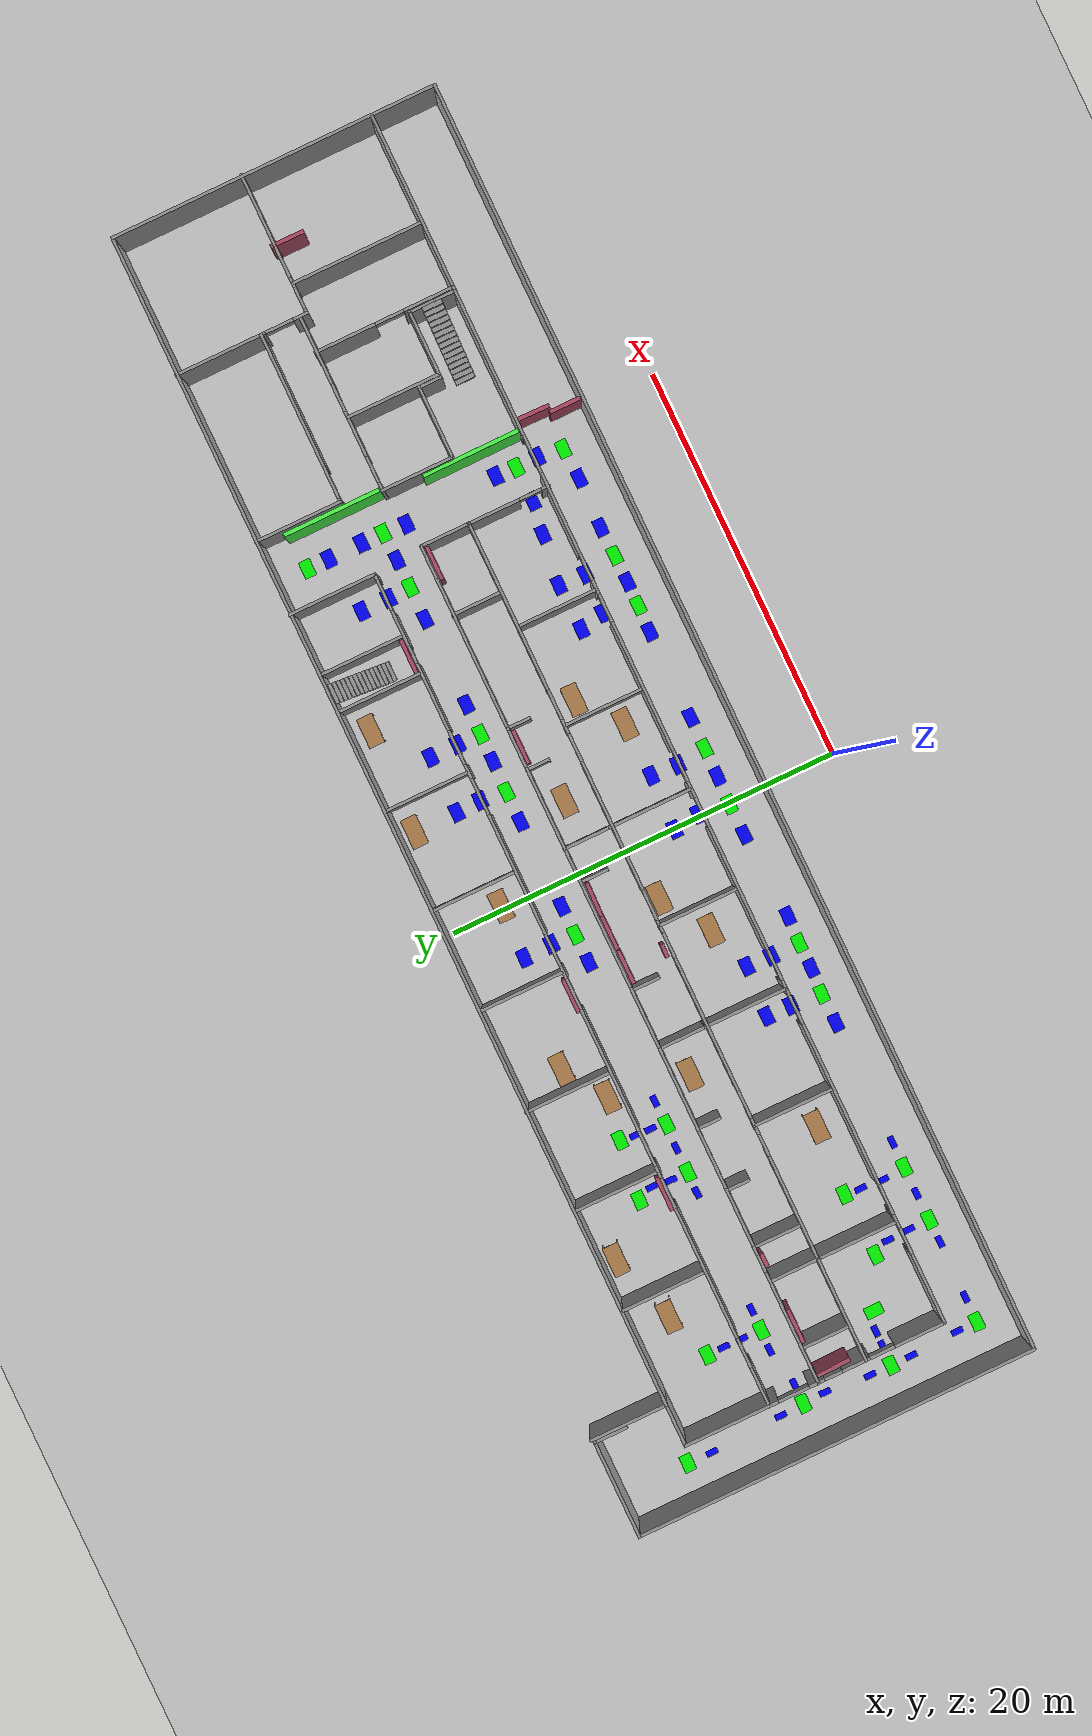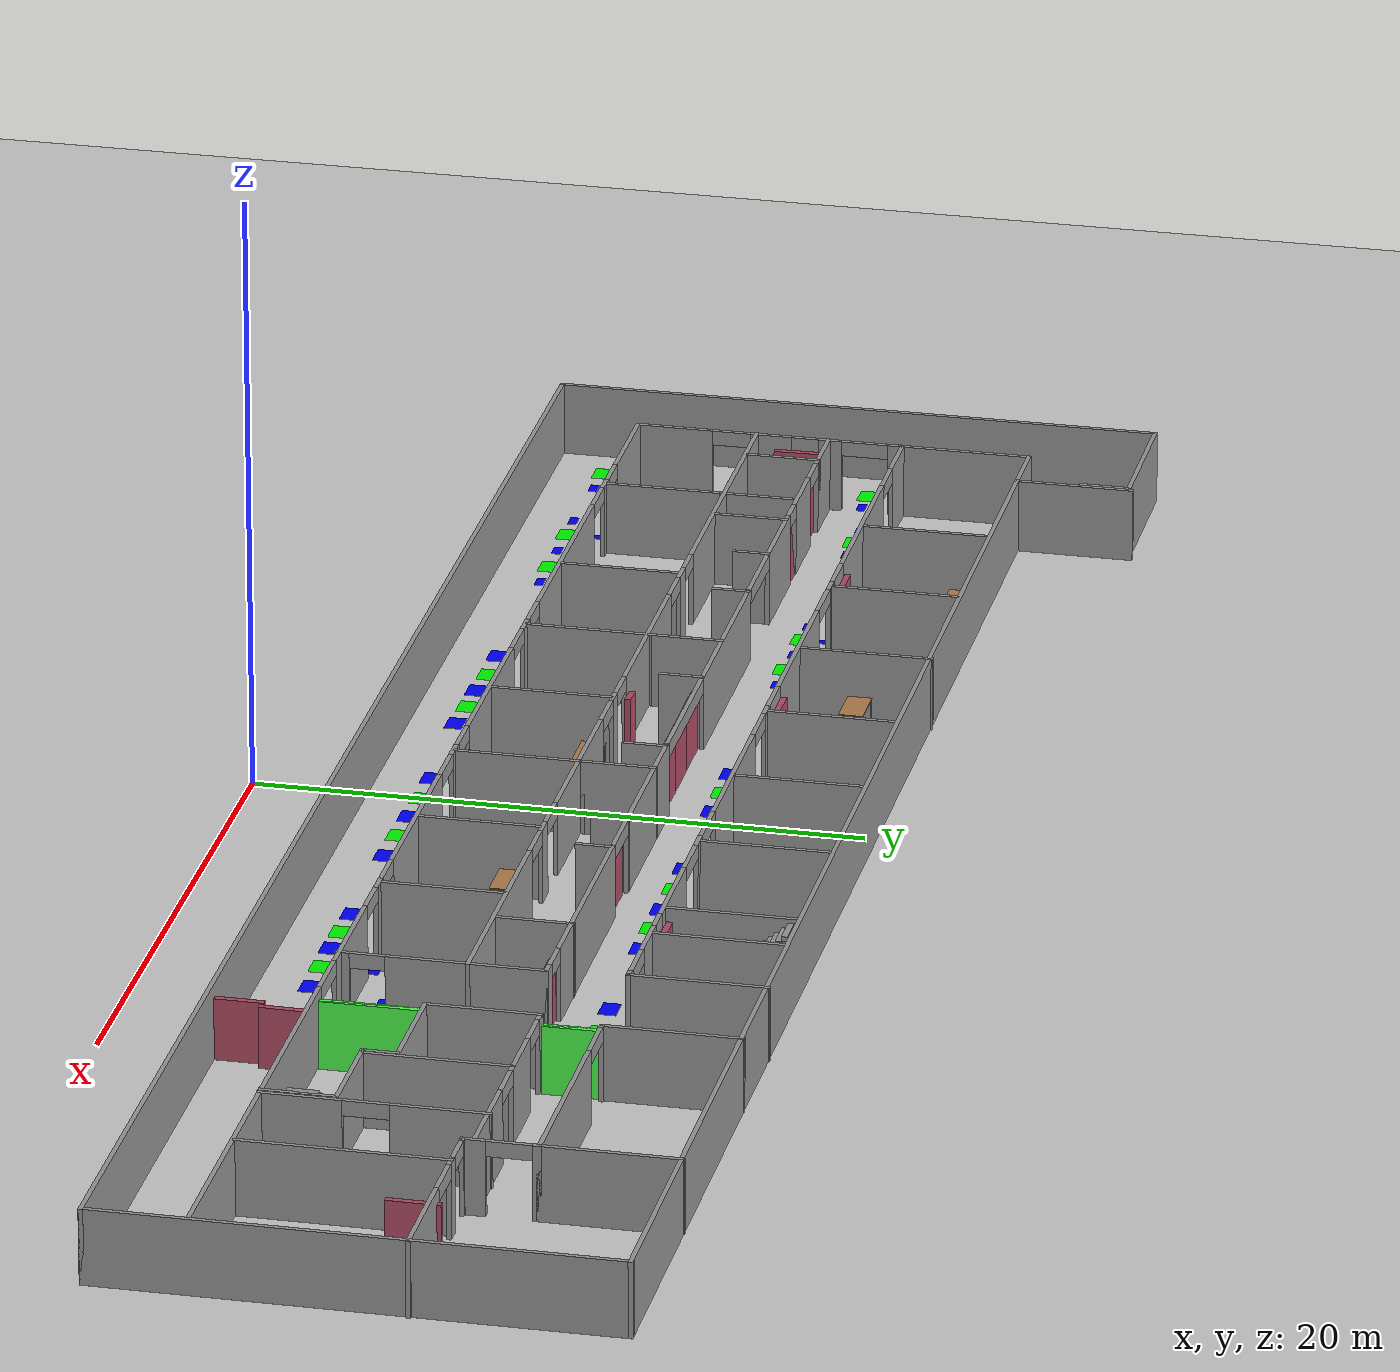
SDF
<sdf version="1.6">
 <world name="default">
  <light name="sun" type="directional">
   <pose>0 0 10.001 0 -0 0</pose>
   <diffuse>0.8 0.8 0.8 1</diffuse>
   <specular>0.2 0.2 0.2 1</specular>
   <attenuation>
    <range>1000</range>
    <constant>0.9</constant>
    <linear>0.01</linear>
    <quadratic>0.001</quadratic>
   </attenuation>
   <direction>-0.5 0.1 -0.9</direction>
  </light>
  <model name="ground_plane">
   <pose>0 0 0.001 0 -0 0</pose>
   <static>1</static>
   <link name="link">
    <collision name="collision">
     <geometry><plane><normal>0 0 1</normal><size>100 100</size></plane></geometry>
     <surface><friction><ode><mu>100</mu><mu2>50</mu2></ode></friction></surface>
    </collision>
    <visual name="visual">
     <cast_shadows>0</cast_shadows>
     <geometry><plane><normal>0 0 1</normal><size>100 100</size></plane></geometry>
     <material>
      <script><uri>file://media/materials/scripts/gazebo.material</uri><name>Gazebo/Grey</name></script>
     </material>
    </visual>
   </link>
  </model>
  <gravity>0 0 -9.8</gravity>
  <magnetic_field>6e-06 2.3e-05 -4.2e-05</magnetic_field>
  <atmosphere type="adiabatic"/>
  <physics name="default_physics" default="0" type="ode">
   <max_step_size>0.001</max_step_size>
   <real_time_factor>1</real_time_factor>
   <real_time_update_rate>1000</real_time_update_rate>
  </physics>
  <scene><ambient>0.4 0.4 0.4 1</ambient><background>0.7 0.7 0.7 1</background><shadows>1</shadows></scene>
  <spherical_coordinates>
   <surface_model>EARTH_WGS84</surface_model>
   <latitude_deg>0</latitude_deg>
   <longitude_deg>0</longitude_deg>
   <elevation>0</elevation>
   <heading_deg>0</heading_deg>
  </spherical_coordinates>
  <model name="table">
   <static>1</static>
   <link name="link">
    <collision name="surface">
     <pose>0 0 1 0 -0 0</pose>
     <geometry><box><size>1.5 0.8 0.03</size></box></geometry>
     <surface><friction><ode><mu>0.6</mu><mu2>0.6</mu2></ode></friction></surface>
    </collision>
    <visual name="visual1">
     <pose>0 0 1 0 -0 0</pose>
     <geometry><box><size>1.5 0.8 0.03</size></box></geometry>
     <material>
      <script><uri>file://media/materials/scripts/gazebo.material</uri><name>Gazebo/Wood</name></script>
     </material>
    </visual>
    <collision name="front_left_leg">
     <pose>0.68 0.38 0.5 0 -0 0</pose>
     <geometry><cylinder><radius>0.02</radius><length>1</length></cylinder></geometry>
    </collision>
    <visual name="front_left_leg">
     <pose>0.68 0.38 0.5 0 -0 0</pose>
     <geometry><cylinder><radius>0.02</radius><length>1</length></cylinder></geometry>
     <material>
      <script><uri>file://media/materials/scripts/gazebo.material</uri><name>Gazebo/Grey</name></script>
     </material>
    </visual>
    <collision name="front_right_leg">
     <pose>0.68 -0.38 0.5 0 -0 0</pose>
     <geometry><cylinder><radius>0.02</radius><length>1</length></cylinder></geometry>
    </collision>
    <visual name="front_right_leg">
     <pose>0.68 -0.38 0.5 0 -0 0</pose>
     <geometry><cylinder><radius>0.02</radius><length>1</length></cylinder></geometry>
     <material>
      <script><uri>file://media/materials/scripts/gazebo.material</uri><name>Gazebo/Grey</name></script>
     </material>
    </visual>
    <collision name="back_right_leg">
     <pose>-0.68 -0.38 0.5 0 -0 0</pose>
     <geometry><cylinder><radius>0.02</radius><length>1</length></cylinder></geometry>
    </collision>
    <visual name="back_right_leg">
     <pose>-0.68 -0.38 0.5 0 -0 0</pose>
     <geometry><cylinder><radius>0.02</radius><length>1</length></cylinder></geometry>
     <material>
      <script><uri>file://media/materials/scripts/gazebo.material</uri><name>Gazebo/Grey</name></script>
     </material>
    </visual>
    <collision name="back_left_leg">
     <pose>-0.68 0.38 0.5 0 -0 0</pose>
     <geometry><cylinder><radius>0.02</radius><length>1</length></cylinder></geometry>
    </collision>
    <visual name="back_left_leg">
     <pose>-0.68 0.38 0.5 0 -0 0</pose>
     <geometry><cylinder><radius>0.02</radius><length>1</length></cylinder></geometry>
     <material>
      <script><uri>file://media/materials/scripts/gazebo.material</uri><name>Gazebo/Grey</name></script>
     </material>
    </visual>
   </link>
   <pose>-20.6493 18.5224 0.001 0 -0 0</pose>
  </model>
  <model name="table_0">
   <static>1</static>
   <link name="link">
    <collision name="surface">
     <pose>0 0 1 0 -0 0</pose>
     <geometry><box><size>1.5 0.8 0.03</size></box></geometry>
     <surface><friction><ode><mu>0.6</mu><mu2>0.6</mu2></ode></friction></surface>
    </collision>
    <visual name="visual1">
     <pose>0 0 1 0 -0 0</pose>
     <geometry><box><size>1.5 0.8 0.03</size></box></geometry>
     <material>
      <script><uri>file://media/materials/scripts/gazebo.material</uri><name>Gazebo/Wood</name></script>
     </material>
    </visual>
    <collision name="front_left_leg">
     <pose>0.68 0.38 0.5 0 -0 0</pose>
     <geometry><cylinder><radius>0.02</radius><length>1</length></cylinder></geometry>
    </collision>
    <visual name="front_left_leg">
     <pose>0.68 0.38 0.5 0 -0 0</pose>
     <geometry><cylinder><radius>0.02</radius><length>1</length></cylinder></geometry>
     <material>
      <script><uri>file://media/materials/scripts/gazebo.material</uri><name>Gazebo/Grey</name></script>
     </material>
    </visual>
    <collision name="front_right_leg">
     <pose>0.68 -0.38 0.5 0 -0 0</pose>
     <geometry><cylinder><radius>0.02</radius><length>1</length></cylinder></geometry>
    </collision>
    <visual name="front_right_leg">
     <pose>0.68 -0.38 0.5 0 -0 0</pose>
     <geometry><cylinder><radius>0.02</radius><length>1</length></cylinder></geometry>
     <material>
      <script><uri>file://media/materials/scripts/gazebo.material</uri><name>Gazebo/Grey</name></script>
     </material>
    </visual>
    <collision name="back_right_leg">
     <pose>-0.68 -0.38 0.5 0 -0 0</pose>
     <geometry><cylinder><radius>0.02</radius><length>1</length></cylinder></geometry>
    </collision>
    <visual name="back_right_leg">
     <pose>-0.68 -0.38 0.5 0 -0 0</pose>
     <geometry><cylinder><radius>0.02</radius><length>1</length></cylinder></geometry>
     <material>
      <script><uri>file://media/materials/scripts/gazebo.material</uri><name>Gazebo/Grey</name></script>
     </material>
    </visual>
    <collision name="back_left_leg">
     <pose>-0.68 0.38 0.5 0 -0 0</pose>
     <geometry><cylinder><radius>0.02</radius><length>1</length></cylinder></geometry>
    </collision>
    <visual name="back_left_leg">
     <pose>-0.68 0.38 0.5 0 -0 0</pose>
     <geometry><cylinder><radius>0.02</radius><length>1</length></cylinder></geometry>
     <material>
      <script><uri>file://media/materials/scripts/gazebo.material</uri><name>Gazebo/Grey</name></script>
     </material>
    </visual>
   </link>
   <pose>-17.1552 19.6086 0.001 0 -0 0</pose>
  </model>
  <model name="table_1">
   <static>1</static>
   <link name="link">
    <collision name="surface">
     <pose>0 0 1 0 -0 0</pose>
     <geometry><box><size>1.5 0.8 0.03</size></box></geometry>
     <surface><friction><ode><mu>0.6</mu><mu2>0.6</mu2></ode></friction></surface>
    </collision>
    <visual name="visual1">
     <pose>0 0 1 0 -0 0</pose>
     <geometry><box><size>1.5 0.8 0.03</size></box></geometry>
     <material>
      <script><uri>file://media/materials/scripts/gazebo.material</uri><name>Gazebo/Wood</name></script>
     </material>
    </visual>
    <collision name="front_left_leg">
     <pose>0.68 0.38 0.5 0 -0 0</pose>
     <geometry><cylinder><radius>0.02</radius><length>1</length></cylinder></geometry>
    </collision>
    <visual name="front_left_leg">
     <pose>0.68 0.38 0.5 0 -0 0</pose>
     <geometry><cylinder><radius>0.02</radius><length>1</length></cylinder></geometry>
     <material>
      <script><uri>file://media/materials/scripts/gazebo.material</uri><name>Gazebo/Grey</name></script>
     </material>
    </visual>
    <collision name="front_right_leg">
     <pose>0.68 -0.38 0.5 0 -0 0</pose>
     <geometry><cylinder><radius>0.02</radius><length>1</length></cylinder></geometry>
    </collision>
    <visual name="front_right_leg">
     <pose>0.68 -0.38 0.5 0 -0 0</pose>
     <geometry><cylinder><radius>0.02</radius><length>1</length></cylinder></geometry>
     <material>
      <script><uri>file://media/materials/scripts/gazebo.material</uri><name>Gazebo/Grey</name></script>
     </material>
    </visual>
    <collision name="back_right_leg">
     <pose>-0.68 -0.38 0.5 0 -0 0</pose>
     <geometry><cylinder><radius>0.02</radius><length>1</length></cylinder></geometry>
    </collision>
    <visual name="back_right_leg">
     <pose>-0.68 -0.38 0.5 0 -0 0</pose>
     <geometry><cylinder><radius>0.02</radius><length>1</length></cylinder></geometry>
     <material>
      <script><uri>file://media/materials/scripts/gazebo.material</uri><name>Gazebo/Grey</name></script>
     </material>
    </visual>
    <collision name="back_left_leg">
     <pose>-0.68 0.38 0.5 0 -0 0</pose>
     <geometry><cylinder><radius>0.02</radius><length>1</length></cylinder></geometry>
    </collision>
    <visual name="back_left_leg">
     <pose>-0.68 0.38 0.5 0 -0 0</pose>
     <geometry><cylinder><radius>0.02</radius><length>1</length></cylinder></geometry>
     <material>
      <script><uri>file://media/materials/scripts/gazebo.material</uri><name>Gazebo/Grey</name></script>
     </material>
    </visual>
   </link>
   <pose>-10.0366 16.6825 0.001 0 -0 0</pose>
  </model>
  <model name="table_2">
   <static>1</static>
   <link name="link">
    <collision name="surface">
     <pose>0 0 1 0 -0 0</pose>
     <geometry><box><size>1.5 0.8 0.03</size></box></geometry>
     <surface><friction><ode><mu>0.6</mu><mu2>0.6</mu2></ode></friction></surface>
    </collision>
    <visual name="visual1">
     <pose>0 0 1 0 -0 0</pose>
     <geometry><box><size>1.5 0.8 0.03</size></box></geometry>
     <material>
      <script><uri>file://media/materials/scripts/gazebo.material</uri><name>Gazebo/Wood</name></script>
     </material>
    </visual>
    <collision name="front_left_leg">
     <pose>0.68 0.38 0.5 0 -0 0</pose>
     <geometry><cylinder><radius>0.02</radius><length>1</length></cylinder></geometry>
    </collision>
    <visual name="front_left_leg">
     <pose>0.68 0.38 0.5 0 -0 0</pose>
     <geometry><cylinder><radius>0.02</radius><length>1</length></cylinder></geometry>
     <material>
      <script><uri>file://media/materials/scripts/gazebo.material</uri><name>Gazebo/Grey</name></script>
     </material>
    </visual>
    <collision name="front_right_leg">
     <pose>0.68 -0.38 0.5 0 -0 0</pose>
     <geometry><cylinder><radius>0.02</radius><length>1</length></cylinder></geometry>
    </collision>
    <visual name="front_right_leg">
     <pose>0.68 -0.38 0.5 0 -0 0</pose>
     <geometry><cylinder><radius>0.02</radius><length>1</length></cylinder></geometry>
     <material>
      <script><uri>file://media/materials/scripts/gazebo.material</uri><name>Gazebo/Grey</name></script>
     </material>
    </visual>
    <collision name="back_right_leg">
     <pose>-0.68 -0.38 0.5 0 -0 0</pose>
     <geometry><cylinder><radius>0.02</radius><length>1</length></cylinder></geometry>
    </collision>
    <visual name="back_right_leg">
     <pose>-0.68 -0.38 0.5 0 -0 0</pose>
     <geometry><cylinder><radius>0.02</radius><length>1</length></cylinder></geometry>
     <material>
      <script><uri>file://media/materials/scripts/gazebo.material</uri><name>Gazebo/Grey</name></script>
     </material>
    </visual>
    <collision name="back_left_leg">
     <pose>-0.68 0.38 0.5 0 -0 0</pose>
     <geometry><cylinder><radius>0.02</radius><length>1</length></cylinder></geometry>
    </collision>
    <visual name="back_left_leg">
     <pose>-0.68 0.38 0.5 0 -0 0</pose>
     <geometry><cylinder><radius>0.02</radius><length>1</length></cylinder></geometry>
     <material>
      <script><uri>file://media/materials/scripts/gazebo.material</uri><name>Gazebo/Grey</name></script>
     </material>
    </visual>
   </link>
   <pose>-15.5399 8.3596 0.001 0 -0 0</pose>
  </model>
  <model name="table_3">
   <static>1</static>
   <link name="link">
    <collision name="surface">
     <pose>0 0 1 0 -0 0</pose>
     <geometry><box><size>1.5 0.8 0.03</size></box></geometry>
     <surface><friction><ode><mu>0.6</mu><mu2>0.6</mu2></ode></friction></surface>
    </collision>
    <visual name="visual1">
     <pose>0 0 1 0 -0 0</pose>
     <geometry><box><size>1.5 0.8 0.03</size></box></geometry>
     <material>
      <script><uri>file://media/materials/scripts/gazebo.material</uri><name>Gazebo/Wood</name></script>
     </material>
    </visual>
    <collision name="front_left_leg">
     <pose>0.68 0.38 0.5 0 -0 0</pose>
     <geometry><cylinder><radius>0.02</radius><length>1</length></cylinder></geometry>
    </collision>
    <visual name="front_left_leg">
     <pose>0.68 0.38 0.5 0 -0 0</pose>
     <geometry><cylinder><radius>0.02</radius><length>1</length></cylinder></geometry>
     <material>
      <script><uri>file://media/materials/scripts/gazebo.material</uri><name>Gazebo/Grey</name></script>
     </material>
    </visual>
    <collision name="front_right_leg">
     <pose>0.68 -0.38 0.5 0 -0 0</pose>
     <geometry><cylinder><radius>0.02</radius><length>1</length></cylinder></geometry>
    </collision>
    <visual name="front_right_leg">
     <pose>0.68 -0.38 0.5 0 -0 0</pose>
     <geometry><cylinder><radius>0.02</radius><length>1</length></cylinder></geometry>
     <material>
      <script><uri>file://media/materials/scripts/gazebo.material</uri><name>Gazebo/Grey</name></script>
     </material>
    </visual>
    <collision name="back_right_leg">
     <pose>-0.68 -0.38 0.5 0 -0 0</pose>
     <geometry><cylinder><radius>0.02</radius><length>1</length></cylinder></geometry>
    </collision>
    <visual name="back_right_leg">
     <pose>-0.68 -0.38 0.5 0 -0 0</pose>
     <geometry><cylinder><radius>0.02</radius><length>1</length></cylinder></geometry>
     <material>
      <script><uri>file://media/materials/scripts/gazebo.material</uri><name>Gazebo/Grey</name></script>
     </material>
    </visual>
    <collision name="back_left_leg">
     <pose>-0.68 0.38 0.5 0 -0 0</pose>
     <geometry><cylinder><radius>0.02</radius><length>1</length></cylinder></geometry>
    </collision>
    <visual name="back_left_leg">
     <pose>-0.68 0.38 0.5 0 -0 0</pose>
     <geometry><cylinder><radius>0.02</radius><length>1</length></cylinder></geometry>
     <material>
      <script><uri>file://media/materials/scripts/gazebo.material</uri><name>Gazebo/Grey</name></script>
     </material>
    </visual>
   </link>
   <pose>-10.736 12.6995 0.001 0 -0 0</pose>
  </model>
  <model name="table_4">
   <static>1</static>
   <link name="link">
    <collision name="surface">
     <pose>0 0 1 0 -0 0</pose>
     <geometry><box><size>1.5 0.8 0.03</size></box></geometry>
     <surface><friction><ode><mu>0.6</mu><mu2>0.6</mu2></ode></friction></surface>
    </collision>
    <visual name="visual1">
     <pose>0 0 1 0 -0 0</pose>
     <geometry><box><size>1.5 0.8 0.03</size></box></geometry>
     <material>
      <script><uri>file://media/materials/scripts/gazebo.material</uri><name>Gazebo/Wood</name></script>
     </material>
    </visual>
    <collision name="front_left_leg">
     <pose>0.68 0.38 0.5 0 -0 0</pose>
     <geometry><cylinder><radius>0.02</radius><length>1</length></cylinder></geometry>
    </collision>
    <visual name="front_left_leg">
     <pose>0.68 0.38 0.5 0 -0 0</pose>
     <geometry><cylinder><radius>0.02</radius><length>1</length></cylinder></geometry>
     <material>
      <script><uri>file://media/materials/scripts/gazebo.material</uri><name>Gazebo/Grey</name></script>
     </material>
    </visual>
    <collision name="front_right_leg">
     <pose>0.68 -0.38 0.5 0 -0 0</pose>
     <geometry><cylinder><radius>0.02</radius><length>1</length></cylinder></geometry>
    </collision>
    <visual name="front_right_leg">
     <pose>0.68 -0.38 0.5 0 -0 0</pose>
     <geometry><cylinder><radius>0.02</radius><length>1</length></cylinder></geometry>
     <material>
      <script><uri>file://media/materials/scripts/gazebo.material</uri><name>Gazebo/Grey</name></script>
     </material>
    </visual>
    <collision name="back_right_leg">
     <pose>-0.68 -0.38 0.5 0 -0 0</pose>
     <geometry><cylinder><radius>0.02</radius><length>1</length></cylinder></geometry>
    </collision>
    <visual name="back_right_leg">
     <pose>-0.68 -0.38 0.5 0 -0 0</pose>
     <geometry><cylinder><radius>0.02</radius><length>1</length></cylinder></geometry>
     <material>
      <script><uri>file://media/materials/scripts/gazebo.material</uri><name>Gazebo/Grey</name></script>
     </material>
    </visual>
    <collision name="back_left_leg">
     <pose>-0.68 0.38 0.5 0 -0 0</pose>
     <geometry><cylinder><radius>0.02</radius><length>1</length></cylinder></geometry>
    </collision>
    <visual name="back_left_leg">
     <pose>-0.68 0.38 0.5 0 -0 0</pose>
     <geometry><cylinder><radius>0.02</radius><length>1</length></cylinder></geometry>
     <material>
      <script><uri>file://media/materials/scripts/gazebo.material</uri><name>Gazebo/Grey</name></script>
     </material>
    </visual>
   </link>
   <pose>-5.01771 8.89432 0.001 0 -0 0</pose>
  </model>
  <model name="table_5">
   <static>1</static>
   <link name="link">
    <collision name="surface">
     <pose>0 0 1 0 -0 0</pose>
     <geometry><box><size>1.5 0.8 0.03</size></box></geometry>
     <surface><friction><ode><mu>0.6</mu><mu2>0.6</mu2></ode></friction></surface>
    </collision>
    <visual name="visual1">
     <pose>0 0 1 0 -0 0</pose>
     <geometry><box><size>1.5 0.8 0.03</size></box></geometry>
     <material>
      <script><uri>file://media/materials/scripts/gazebo.material</uri><name>Gazebo/Wood</name></script>
     </material>
    </visual>
    <collision name="front_left_leg">
     <pose>0.68 0.38 0.5 0 -0 0</pose>
     <geometry><cylinder><radius>0.02</radius><length>1</length></cylinder></geometry>
    </collision>
    <visual name="front_left_leg">
     <pose>0.68 0.38 0.5 0 -0 0</pose>
     <geometry><cylinder><radius>0.02</radius><length>1</length></cylinder></geometry>
     <material>
      <script><uri>file://media/materials/scripts/gazebo.material</uri><name>Gazebo/Grey</name></script>
     </material>
    </visual>
    <collision name="front_right_leg">
     <pose>0.68 -0.38 0.5 0 -0 0</pose>
     <geometry><cylinder><radius>0.02</radius><length>1</length></cylinder></geometry>
    </collision>
    <visual name="front_right_leg">
     <pose>0.68 -0.38 0.5 0 -0 0</pose>
     <geometry><cylinder><radius>0.02</radius><length>1</length></cylinder></geometry>
     <material>
      <script><uri>file://media/materials/scripts/gazebo.material</uri><name>Gazebo/Grey</name></script>
     </material>
    </visual>
    <collision name="back_right_leg">
     <pose>-0.68 -0.38 0.5 0 -0 0</pose>
     <geometry><cylinder><radius>0.02</radius><length>1</length></cylinder></geometry>
    </collision>
    <visual name="back_right_leg">
     <pose>-0.68 -0.38 0.5 0 -0 0</pose>
     <geometry><cylinder><radius>0.02</radius><length>1</length></cylinder></geometry>
     <material>
      <script><uri>file://media/materials/scripts/gazebo.material</uri><name>Gazebo/Grey</name></script>
     </material>
    </visual>
    <collision name="back_left_leg">
     <pose>-0.68 0.38 0.5 0 -0 0</pose>
     <geometry><cylinder><radius>0.02</radius><length>1</length></cylinder></geometry>
    </collision>
    <visual name="back_left_leg">
     <pose>-0.68 0.38 0.5 0 -0 0</pose>
     <geometry><cylinder><radius>0.02</radius><length>1</length></cylinder></geometry>
     <material>
      <script><uri>file://media/materials/scripts/gazebo.material</uri><name>Gazebo/Grey</name></script>
     </material>
    </visual>
   </link>
   <pose>-7.90698 18.0796 0.001 0 -0 0</pose>
  </model>
  <model name="table_6">
   <static>1</static>
   <link name="link">
    <collision name="surface">
     <pose>0 0 1 0 -0 0</pose>
     <geometry><box><size>1.5 0.8 0.03</size></box></geometry>
     <surface><friction><ode><mu>0.6</mu><mu2>0.6</mu2></ode></friction></surface>
    </collision>
    <visual name="visual1">
     <pose>0 0 1 0 -0 0</pose>
     <geometry><box><size>1.5 0.8 0.03</size></box></geometry>
     <material>
      <script><uri>file://media/materials/scripts/gazebo.material</uri><name>Gazebo/Wood</name></script>
     </material>
    </visual>
    <collision name="front_left_leg">
     <pose>0.68 0.38 0.5 0 -0 0</pose>
     <geometry><cylinder><radius>0.02</radius><length>1</length></cylinder></geometry>
    </collision>
    <visual name="front_left_leg">
     <pose>0.68 0.38 0.5 0 -0 0</pose>
     <geometry><cylinder><radius>0.02</radius><length>1</length></cylinder></geometry>
     <material>
      <script><uri>file://media/materials/scripts/gazebo.material</uri><name>Gazebo/Grey</name></script>
     </material>
    </visual>
    <collision name="front_right_leg">
     <pose>0.68 -0.38 0.5 0 -0 0</pose>
     <geometry><cylinder><radius>0.02</radius><length>1</length></cylinder></geometry>
    </collision>
    <visual name="front_right_leg">
     <pose>0.68 -0.38 0.5 0 -0 0</pose>
     <geometry><cylinder><radius>0.02</radius><length>1</length></cylinder></geometry>
     <material>
      <script><uri>file://media/materials/scripts/gazebo.material</uri><name>Gazebo/Grey</name></script>
     </material>
    </visual>
    <collision name="back_right_leg">
     <pose>-0.68 -0.38 0.5 0 -0 0</pose>
     <geometry><cylinder><radius>0.02</radius><length>1</length></cylinder></geometry>
    </collision>
    <visual name="back_right_leg">
     <pose>-0.68 -0.38 0.5 0 -0 0</pose>
     <geometry><cylinder><radius>0.02</radius><length>1</length></cylinder></geometry>
     <material>
      <script><uri>file://media/materials/scripts/gazebo.material</uri><name>Gazebo/Grey</name></script>
     </material>
    </visual>
    <collision name="back_left_leg">
     <pose>-0.68 0.38 0.5 0 -0 0</pose>
     <geometry><cylinder><radius>0.02</radius><length>1</length></cylinder></geometry>
    </collision>
    <visual name="back_left_leg">
     <pose>-0.68 0.38 0.5 0 -0 0</pose>
     <geometry><cylinder><radius>0.02</radius><length>1</length></cylinder></geometry>
     <material>
      <script><uri>file://media/materials/scripts/gazebo.material</uri><name>Gazebo/Grey</name></script>
     </material>
    </visual>
   </link>
   <pose>0.272964 17.3657 0.001 0 -0 0</pose>
  </model>
  <model name="table_7">
   <static>1</static>
   <link name="link">
    <collision name="surface">
     <pose>0 0 1 0 -0 0</pose>
     <geometry><box><size>1.5 0.8 0.03</size></box></geometry>
     <surface><friction><ode><mu>0.6</mu><mu2>0.6</mu2></ode></friction></surface>
    </collision>
    <visual name="visual1">
     <pose>0 0 1 0 -0 0</pose>
     <geometry><box><size>1.5 0.8 0.03</size></box></geometry>
     <material>
      <script><uri>file://media/materials/scripts/gazebo.material</uri><name>Gazebo/Wood</name></script>
     </material>
    </visual>
    <collision name="front_left_leg">
     <pose>0.68 0.38 0.5 0 -0 0</pose>
     <geometry><cylinder><radius>0.02</radius><length>1</length></cylinder></geometry>
    </collision>
    <visual name="front_left_leg">
     <pose>0.68 0.38 0.5 0 -0 0</pose>
     <geometry><cylinder><radius>0.02</radius><length>1</length></cylinder></geometry>
     <material>
      <script><uri>file://media/materials/scripts/gazebo.material</uri><name>Gazebo/Grey</name></script>
     </material>
    </visual>
    <collision name="front_right_leg">
     <pose>0.68 -0.38 0.5 0 -0 0</pose>
     <geometry><cylinder><radius>0.02</radius><length>1</length></cylinder></geometry>
    </collision>
    <visual name="front_right_leg">
     <pose>0.68 -0.38 0.5 0 -0 0</pose>
     <geometry><cylinder><radius>0.02</radius><length>1</length></cylinder></geometry>
     <material>
      <script><uri>file://media/materials/scripts/gazebo.material</uri><name>Gazebo/Grey</name></script>
     </material>
    </visual>
    <collision name="back_right_leg">
     <pose>-0.68 -0.38 0.5 0 -0 0</pose>
     <geometry><cylinder><radius>0.02</radius><length>1</length></cylinder></geometry>
    </collision>
    <visual name="back_right_leg">
     <pose>-0.68 -0.38 0.5 0 -0 0</pose>
     <geometry><cylinder><radius>0.02</radius><length>1</length></cylinder></geometry>
     <material>
      <script><uri>file://media/materials/scripts/gazebo.material</uri><name>Gazebo/Grey</name></script>
     </material>
    </visual>
    <collision name="back_left_leg">
     <pose>-0.68 0.38 0.5 0 -0 0</pose>
     <geometry><cylinder><radius>0.02</radius><length>1</length></cylinder></geometry>
    </collision>
    <visual name="back_left_leg">
     <pose>-0.68 0.38 0.5 0 -0 0</pose>
     <geometry><cylinder><radius>0.02</radius><length>1</length></cylinder></geometry>
     <material>
      <script><uri>file://media/materials/scripts/gazebo.material</uri><name>Gazebo/Grey</name></script>
     </material>
    </visual>
   </link>
   <pose>-2.6011 10.4538 0.001 0 -0 0</pose>
  </model>
  <model name="table_8">
   <static>1</static>
   <link name="link">
    <collision name="surface">
     <pose>0 0 1 0 -0 0</pose>
     <geometry><box><size>1.5 0.8 0.03</size></box></geometry>
     <surface><friction><ode><mu>0.6</mu><mu2>0.6</mu2></ode></friction></surface>
    </collision>
    <visual name="visual1">
     <pose>0 0 1 0 -0 0</pose>
     <geometry><box><size>1.5 0.8 0.03</size></box></geometry>
     <material>
      <script><uri>file://media/materials/scripts/gazebo.material</uri><name>Gazebo/Wood</name></script>
     </material>
    </visual>
    <collision name="front_left_leg">
     <pose>0.68 0.38 0.5 0 -0 0</pose>
     <geometry><cylinder><radius>0.02</radius><length>1</length></cylinder></geometry>
    </collision>
    <visual name="front_left_leg">
     <pose>0.68 0.38 0.5 0 -0 0</pose>
     <geometry><cylinder><radius>0.02</radius><length>1</length></cylinder></geometry>
     <material>
      <script><uri>file://media/materials/scripts/gazebo.material</uri><name>Gazebo/Grey</name></script>
     </material>
    </visual>
    <collision name="front_right_leg">
     <pose>0.68 -0.38 0.5 0 -0 0</pose>
     <geometry><cylinder><radius>0.02</radius><length>1</length></cylinder></geometry>
    </collision>
    <visual name="front_right_leg">
     <pose>0.68 -0.38 0.5 0 -0 0</pose>
     <geometry><cylinder><radius>0.02</radius><length>1</length></cylinder></geometry>
     <material>
      <script><uri>file://media/materials/scripts/gazebo.material</uri><name>Gazebo/Grey</name></script>
     </material>
    </visual>
    <collision name="back_right_leg">
     <pose>-0.68 -0.38 0.5 0 -0 0</pose>
     <geometry><cylinder><radius>0.02</radius><length>1</length></cylinder></geometry>
    </collision>
    <visual name="back_right_leg">
     <pose>-0.68 -0.38 0.5 0 -0 0</pose>
     <geometry><cylinder><radius>0.02</radius><length>1</length></cylinder></geometry>
     <material>
      <script><uri>file://media/materials/scripts/gazebo.material</uri><name>Gazebo/Grey</name></script>
     </material>
    </visual>
    <collision name="back_left_leg">
     <pose>-0.68 0.38 0.5 0 -0 0</pose>
     <geometry><cylinder><radius>0.02</radius><length>1</length></cylinder></geometry>
    </collision>
    <visual name="back_left_leg">
     <pose>-0.68 0.38 0.5 0 -0 0</pose>
     <geometry><cylinder><radius>0.02</radius><length>1</length></cylinder></geometry>
     <material>
      <script><uri>file://media/materials/scripts/gazebo.material</uri><name>Gazebo/Grey</name></script>
     </material>
    </visual>
   </link>
   <pose>5.52089 8.38758 0.001 0 -0 0</pose>
  </model>
  <model name="table_9">
   <static>1</static>
   <link name="link">
    <collision name="surface">
     <pose>0 0 1 0 -0 0</pose>
     <geometry><box><size>1.5 0.8 0.03</size></box></geometry>
     <surface><friction><ode><mu>0.6</mu><mu2>0.6</mu2></ode></friction></surface>
    </collision>
    <visual name="visual1">
     <pose>0 0 1 0 -0 0</pose>
     <geometry><box><size>1.5 0.8 0.03</size></box></geometry>
     <material>
      <script><uri>file://media/materials/scripts/gazebo.material</uri><name>Gazebo/Wood</name></script>
     </material>
    </visual>
    <collision name="front_left_leg">
     <pose>0.68 0.38 0.5 0 -0 0</pose>
     <geometry><cylinder><radius>0.02</radius><length>1</length></cylinder></geometry>
    </collision>
    <visual name="front_left_leg">
     <pose>0.68 0.38 0.5 0 -0 0</pose>
     <geometry><cylinder><radius>0.02</radius><length>1</length></cylinder></geometry>
     <material>
      <script><uri>file://media/materials/scripts/gazebo.material</uri><name>Gazebo/Grey</name></script>
     </material>
    </visual>
    <collision name="front_right_leg">
     <pose>0.68 -0.38 0.5 0 -0 0</pose>
     <geometry><cylinder><radius>0.02</radius><length>1</length></cylinder></geometry>
    </collision>
    <visual name="front_right_leg">
     <pose>0.68 -0.38 0.5 0 -0 0</pose>
     <geometry><cylinder><radius>0.02</radius><length>1</length></cylinder></geometry>
     <material>
      <script><uri>file://media/materials/scripts/gazebo.material</uri><name>Gazebo/Grey</name></script>
     </material>
    </visual>
    <collision name="back_right_leg">
     <pose>-0.68 -0.38 0.5 0 -0 0</pose>
     <geometry><cylinder><radius>0.02</radius><length>1</length></cylinder></geometry>
    </collision>
    <visual name="back_right_leg">
     <pose>-0.68 -0.38 0.5 0 -0 0</pose>
     <geometry><cylinder><radius>0.02</radius><length>1</length></cylinder></geometry>
     <material>
      <script><uri>file://media/materials/scripts/gazebo.material</uri><name>Gazebo/Grey</name></script>
     </material>
    </visual>
    <collision name="back_left_leg">
     <pose>-0.68 0.38 0.5 0 -0 0</pose>
     <geometry><cylinder><radius>0.02</radius><length>1</length></cylinder></geometry>
    </collision>
    <visual name="back_left_leg">
     <pose>-0.68 0.38 0.5 0 -0 0</pose>
     <geometry><cylinder><radius>0.02</radius><length>1</length></cylinder></geometry>
     <material>
      <script><uri>file://media/materials/scripts/gazebo.material</uri><name>Gazebo/Grey</name></script>
     </material>
    </visual>
   </link>
   <pose>10.3778 19.3786 0.001 0 -0 0</pose>
  </model>
  <model name="table_10">
   <static>1</static>
   <link name="link">
    <collision name="surface">
     <pose>0 0 1 0 -0 0</pose>
     <geometry><box><size>1.5 0.8 0.03</size></box></geometry>
     <surface><friction><ode><mu>0.6</mu><mu2>0.6</mu2></ode></friction></surface>
    </collision>
    <visual name="visual1">
     <pose>0 0 1 0 -0 0</pose>
     <geometry><box><size>1.5 0.8 0.03</size></box></geometry>
     <material>
      <script><uri>file://media/materials/scripts/gazebo.material</uri><name>Gazebo/Wood</name></script>
     </material>
    </visual>
    <collision name="front_left_leg">
     <pose>0.68 0.38 0.5 0 -0 0</pose>
     <geometry><cylinder><radius>0.02</radius><length>1</length></cylinder></geometry>
    </collision>
    <visual name="front_left_leg">
     <pose>0.68 0.38 0.5 0 -0 0</pose>
     <geometry><cylinder><radius>0.02</radius><length>1</length></cylinder></geometry>
     <material>
      <script><uri>file://media/materials/scripts/gazebo.material</uri><name>Gazebo/Grey</name></script>
     </material>
    </visual>
    <collision name="front_right_leg">
     <pose>0.68 -0.38 0.5 0 -0 0</pose>
     <geometry><cylinder><radius>0.02</radius><length>1</length></cylinder></geometry>
    </collision>
    <visual name="front_right_leg">
     <pose>0.68 -0.38 0.5 0 -0 0</pose>
     <geometry><cylinder><radius>0.02</radius><length>1</length></cylinder></geometry>
     <material>
      <script><uri>file://media/materials/scripts/gazebo.material</uri><name>Gazebo/Grey</name></script>
     </material>
    </visual>
    <collision name="back_right_leg">
     <pose>-0.68 -0.38 0.5 0 -0 0</pose>
     <geometry><cylinder><radius>0.02</radius><length>1</length></cylinder></geometry>
    </collision>
    <visual name="back_right_leg">
     <pose>-0.68 -0.38 0.5 0 -0 0</pose>
     <geometry><cylinder><radius>0.02</radius><length>1</length></cylinder></geometry>
     <material>
      <script><uri>file://media/materials/scripts/gazebo.material</uri><name>Gazebo/Grey</name></script>
     </material>
    </visual>
    <collision name="back_left_leg">
     <pose>-0.68 0.38 0.5 0 -0 0</pose>
     <geometry><cylinder><radius>0.02</radius><length>1</length></cylinder></geometry>
    </collision>
    <visual name="back_left_leg">
     <pose>-0.68 0.38 0.5 0 -0 0</pose>
     <geometry><cylinder><radius>0.02</radius><length>1</length></cylinder></geometry>
     <material>
      <script><uri>file://media/materials/scripts/gazebo.material</uri><name>Gazebo/Grey</name></script>
     </material>
    </visual>
   </link>
   <pose>3.46371 12.5183 0.001 0 -0 0</pose>
  </model>
  <model name="table_11">
   <static>1</static>
   <link name="link">
    <collision name="surface">
     <pose>0 0 1 0 -0 0</pose>
     <geometry><box><size>1.5 0.8 0.03</size></box></geometry>
     <surface><friction><ode><mu>0.6</mu><mu2>0.6</mu2></ode></friction></surface>
    </collision>
    <visual name="visual1">
     <pose>0 0 1 0 -0 0</pose>
     <geometry><box><size>1.5 0.8 0.03</size></box></geometry>
     <material>
      <script><uri>file://media/materials/scripts/gazebo.material</uri><name>Gazebo/Wood</name></script>
     </material>
    </visual>
    <collision name="front_left_leg">
     <pose>0.68 0.38 0.5 0 -0 0</pose>
     <geometry><cylinder><radius>0.02</radius><length>1</length></cylinder></geometry>
    </collision>
    <visual name="front_left_leg">
     <pose>0.68 0.38 0.5 0 -0 0</pose>
     <geometry><cylinder><radius>0.02</radius><length>1</length></cylinder></geometry>
     <material>
      <script><uri>file://media/materials/scripts/gazebo.material</uri><name>Gazebo/Grey</name></script>
     </material>
    </visual>
    <collision name="front_right_leg">
     <pose>0.68 -0.38 0.5 0 -0 0</pose>
     <geometry><cylinder><radius>0.02</radius><length>1</length></cylinder></geometry>
    </collision>
    <visual name="front_right_leg">
     <pose>0.68 -0.38 0.5 0 -0 0</pose>
     <geometry><cylinder><radius>0.02</radius><length>1</length></cylinder></geometry>
     <material>
      <script><uri>file://media/materials/scripts/gazebo.material</uri><name>Gazebo/Grey</name></script>
     </material>
    </visual>
    <collision name="back_right_leg">
     <pose>-0.68 -0.38 0.5 0 -0 0</pose>
     <geometry><cylinder><radius>0.02</radius><length>1</length></cylinder></geometry>
    </collision>
    <visual name="back_right_leg">
     <pose>-0.68 -0.38 0.5 0 -0 0</pose>
     <geometry><cylinder><radius>0.02</radius><length>1</length></cylinder></geometry>
     <material>
      <script><uri>file://media/materials/scripts/gazebo.material</uri><name>Gazebo/Grey</name></script>
     </material>
    </visual>
    <collision name="back_left_leg">
     <pose>-0.68 0.38 0.5 0 -0 0</pose>
     <geometry><cylinder><radius>0.02</radius><length>1</length></cylinder></geometry>
    </collision>
    <visual name="back_left_leg">
     <pose>-0.68 0.38 0.5 0 -0 0</pose>
     <geometry><cylinder><radius>0.02</radius><length>1</length></cylinder></geometry>
     <material>
      <script><uri>file://media/materials/scripts/gazebo.material</uri><name>Gazebo/Grey</name></script>
     </material>
    </visual>
   </link>
   <pose>5.18073 19.5521 0.001 0 -0 0</pose>
  </model>
  <model name="table_12">
   <static>1</static>
   <link name="link">
    <collision name="surface">
     <pose>0 0 1 0 -0 0</pose>
     <geometry><box><size>1.5 0.8 0.03</size></box></geometry>
     <surface><friction><ode><mu>0.6</mu><mu2>0.6</mu2></ode></friction></surface>
    </collision>
    <visual name="visual1">
     <pose>0 0 1 0 -0 0</pose>
     <geometry><box><size>1.5 0.8 0.03</size></box></geometry>
     <material>
      <script><uri>file://media/materials/scripts/gazebo.material</uri><name>Gazebo/Wood</name></script>
     </material>
    </visual>
    <collision name="front_left_leg">
     <pose>0.68 0.38 0.5 0 -0 0</pose>
     <geometry><cylinder><radius>0.02</radius><length>1</length></cylinder></geometry>
    </collision>
    <visual name="front_left_leg">
     <pose>0.68 0.38 0.5 0 -0 0</pose>
     <geometry><cylinder><radius>0.02</radius><length>1</length></cylinder></geometry>
     <material>
      <script><uri>file://media/materials/scripts/gazebo.material</uri><name>Gazebo/Grey</name></script>
     </material>
    </visual>
    <collision name="front_right_leg">
     <pose>0.68 -0.38 0.5 0 -0 0</pose>
     <geometry><cylinder><radius>0.02</radius><length>1</length></cylinder></geometry>
    </collision>
    <visual name="front_right_leg">
     <pose>0.68 -0.38 0.5 0 -0 0</pose>
     <geometry><cylinder><radius>0.02</radius><length>1</length></cylinder></geometry>
     <material>
      <script><uri>file://media/materials/scripts/gazebo.material</uri><name>Gazebo/Grey</name></script>
     </material>
    </visual>
    <collision name="back_right_leg">
     <pose>-0.68 -0.38 0.5 0 -0 0</pose>
     <geometry><cylinder><radius>0.02</radius><length>1</length></cylinder></geometry>
    </collision>
    <visual name="back_right_leg">
     <pose>-0.68 -0.38 0.5 0 -0 0</pose>
     <geometry><cylinder><radius>0.02</radius><length>1</length></cylinder></geometry>
     <material>
      <script><uri>file://media/materials/scripts/gazebo.material</uri><name>Gazebo/Grey</name></script>
     </material>
    </visual>
    <collision name="back_left_leg">
     <pose>-0.68 0.38 0.5 0 -0 0</pose>
     <geometry><cylinder><radius>0.02</radius><length>1</length></cylinder></geometry>
    </collision>
    <visual name="back_left_leg">
     <pose>-0.68 0.38 0.5 0 -0 0</pose>
     <geometry><cylinder><radius>0.02</radius><length>1</length></cylinder></geometry>
     <material>
      <script><uri>file://media/materials/scripts/gazebo.material</uri><name>Gazebo/Grey</name></script>
     </material>
    </visual>
   </link>
   <pose>7.58214 10.0723 0.001 0 -0 0</pose>
  </model>
  <model name="doorOutside_clone_8_clone">
   <link name="link">
    <pose>0.155539 -0.366282 0.216958 0 -0 0</pose>
    <inertial>
     <mass>2.13199</mass>
     <inertia>
      <ixx>0.452656</ixx>
      <ixy>0</ixy>
      <ixz>0</ixz>
      <iyy>0.796738</iyy>
      <iyz>0</iyz>
      <izz>0.699414</izz>
     </inertia>
     <pose>0 0 0.001 0 -0 0</pose>
    </inertial>
    <visual name="visual">
     <geometry><box><size>1.71368 0.198843 2.05986</size></box></geometry>
     <material>
      <script><name>Gazebo/Grey</name><uri>file://media/materials/scripts/gazebo.material</uri></script>
      <ambient>0.7 0.3 0.4 1</ambient>
      <diffuse>0.7 0.7 0.7 1</diffuse>
      <specular>0.01 0.01 0.01 1</specular>
      <emissive>0 0 0 1</emissive>
      <shader type="vertex"><normal_map>__default__</normal_map></shader>
      <lighting>0</lighting>
     </material>
     <pose>0 0 0.001 0 -0 0</pose>
    </visual>
    <collision name="collision">
     <pose>0 0 0.001 0 -0 0</pose>
     <geometry><box><size>1.71368 0.198843 2.05986</size></box></geometry>
     <surface>
      <friction>
       <ode><mu>1</mu><mu2>1</mu2><fdir1>0 0 0</fdir1><slip1>0</slip1><slip2>0</slip2></ode>
       <torsional>
        <coefficient>1</coefficient>
        <patch_radius>0</patch_radius>
        <surface_radius>0</surface_radius>
        <use_patch_radius>1</use_patch_radius>
        <ode><slip>0</slip></ode>
       </torsional>
      </friction>
      <bounce><restitution_coefficient>0</restitution_coefficient><threshold>1e+06</threshold></bounce>
      <contact>
       <collide_without_contact>0</collide_without_contact>
       <collide_without_contact_bitmask>1</collide_without_contact_bitmask>
       <collide_bitmask>1</collide_bitmask>
       <ode>
        <soft_cfm>0</soft_cfm>
        <soft_erp>0.2</soft_erp>
        <kp>1e+13</kp>
        <kd>1</kd>
        <max_vel>0.01</max_vel>
        <min_depth>0</min_depth>
       </ode>
       <bullet>
        <split_impulse>1</split_impulse>
        <split_impulse_penetration_threshold>-0.01</split_impulse_penetration_threshold>
        <soft_cfm>0</soft_cfm>
        <soft_erp>0.2</soft_erp>
        <kp>1e+13</kp>
        <kd>1</kd>
       </bullet>
      </contact>
     </surface>
    </collision>
   </link>
   <static>1</static>
   <pose>20.1185 5.95904 0.812973 1e-06 1e-06 1.55384</pose>
  </model>
  <model name="doorOutside_clone_8_clone_0">
   <link name="link">
    <pose>0.155539 -0.366282 0.216958 0 -0 0</pose>
    <inertial>
     <mass>2.13199</mass>
     <inertia>
      <ixx>0.452656</ixx>
      <ixy>0</ixy>
      <ixz>0</ixz>
      <iyy>0.796738</iyy>
      <iyz>0</iyz>
      <izz>0.699414</izz>
     </inertia>
     <pose>0 0 0.001 0 -0 0</pose>
    </inertial>
    <visual name="visual">
     <geometry><box><size>1.71368 0.198843 2.05986</size></box></geometry>
     <material>
      <script><name>Gazebo/Grey</name><uri>file://media/materials/scripts/gazebo.material</uri></script>
      <ambient>0.7 0.3 0.4 1</ambient>
      <diffuse>0.7 0.7 0.7 1</diffuse>
      <specular>0.01 0.01 0.01 1</specular>
      <emissive>0 0 0 1</emissive>
      <shader type="vertex"><normal_map>__default__</normal_map></shader>
      <lighting>0</lighting>
     </material>
     <pose>0 0 0.001 0 -0 0</pose>
    </visual>
    <collision name="collision">
     <pose>0 0 0.001 0 -0 0</pose>
     <geometry><box><size>1.71368 0.198843 2.05986</size></box></geometry>
     <surface>
      <friction>
       <ode><mu>1</mu><mu2>1</mu2><fdir1>0 0 0</fdir1><slip1>0</slip1><slip2>0</slip2></ode>
       <torsional>
        <coefficient>1</coefficient>
        <patch_radius>0</patch_radius>
        <surface_radius>0</surface_radius>
        <use_patch_radius>1</use_patch_radius>
        <ode><slip>0</slip></ode>
       </torsional>
      </friction>
      <bounce><restitution_coefficient>0</restitution_coefficient><threshold>1e+06</threshold></bounce>
      <contact>
       <collide_without_contact>0</collide_without_contact>
       <collide_without_contact_bitmask>1</collide_without_contact_bitmask>
       <collide_bitmask>1</collide_bitmask>
       <ode>
        <soft_cfm>0</soft_cfm>
        <soft_erp>0.2</soft_erp>
        <kp>1e+13</kp>
        <kd>1</kd>
        <max_vel>0.01</max_vel>
        <min_depth>0</min_depth>
       </ode>
       <bullet>
        <split_impulse>1</split_impulse>
        <split_impulse_penetration_threshold>-0.01</split_impulse_penetration_threshold>
        <soft_cfm>0</soft_cfm>
        <soft_erp>0.2</soft_erp>
        <kp>1e+13</kp>
        <kd>1</kd>
       </bullet>
      </contact>
     </surface>
    </collision>
   </link>
   <static>1</static>
   <pose>32.3755 12.8211 0.812972 -1e-06 0 1.56458</pose>
  </model>
  <model name="doorOutside_clone_8_clone_1">
   <link name="link">
    <pose>0.155539 -0.366282 0.216958 0 -0 0</pose>
    <inertial>
     <mass>2.13199</mass>
     <inertia>
      <ixx>0.452656</ixx>
      <ixy>0</ixy>
      <ixz>0</ixz>
      <iyy>0.796738</iyy>
      <iyz>0</iyz>
      <izz>0.699414</izz>
     </inertia>
     <pose>0 0 0.001 0 -0 0</pose>
    </inertial>
    <visual name="visual">
     <geometry><box><size>1.71368 0.198843 2.05986</size></box></geometry>
     <material>
      <script><name>Gazebo/Grey</name><uri>file://media/materials/scripts/gazebo.material</uri></script>
      <ambient>0.7 0.3 0.4 1</ambient>
      <diffuse>0.7 0.7 0.7 1</diffuse>
      <specular>0.01 0.01 0.01 1</specular>
      <emissive>0 0 0 1</emissive>
      <shader type="vertex"><normal_map>__default__</normal_map></shader>
      <lighting>0</lighting>
     </material>
     <pose>0 0 0.001 0 -0 0</pose>
    </visual>
    <collision name="collision">
     <pose>0 0 0.001 0 -0 0</pose>
     <geometry><box><size>1.71368 0.198843 2.05986</size></box></geometry>
     <surface>
      <friction>
       <ode><mu>1</mu><mu2>1</mu2><fdir1>0 0 0</fdir1><slip1>0</slip1><slip2>0</slip2></ode>
       <torsional>
        <coefficient>1</coefficient>
        <patch_radius>0</patch_radius>
        <surface_radius>0</surface_radius>
        <use_patch_radius>1</use_patch_radius>
        <ode><slip>0</slip></ode>
       </torsional>
      </friction>
      <bounce><restitution_coefficient>0</restitution_coefficient><threshold>1e+06</threshold></bounce>
      <contact>
       <collide_without_contact>0</collide_without_contact>
       <collide_without_contact_bitmask>1</collide_without_contact_bitmask>
       <collide_bitmask>1</collide_bitmask>
       <ode>
        <soft_cfm>0</soft_cfm>
        <soft_erp>0.2</soft_erp>
        <kp>1e+13</kp>
        <kd>1</kd>
        <max_vel>0.01</max_vel>
        <min_depth>0</min_depth>
       </ode>
       <bullet>
        <split_impulse>1</split_impulse>
        <split_impulse_penetration_threshold>-0.01</split_impulse_penetration_threshold>
        <soft_cfm>0</soft_cfm>
        <soft_erp>0.2</soft_erp>
        <kp>1e+13</kp>
        <kd>1</kd>
       </bullet>
      </contact>
     </surface>
    </collision>
   </link>
   <static>1</static>
   <pose>19.8025 4.35425 0.812972 0 -0 1.57076</pose>
  </model>
  <model name="doorOutside_2_clone">
   <link name="link">
    <pose>0.155539 -0.366282 0.216958 0 -0 0</pose>
    <inertial>
     <mass>2.13199</mass>
     <inertia>
      <ixx>0.452656</ixx>
      <ixy>0</ixy>
      <ixz>0</ixz>
      <iyy>0.796738</iyy>
      <iyz>0</iyz>
      <izz>0.699414</izz>
     </inertia>
     <pose>0 0 0.001 0 -0 0</pose>
    </inertial>
    <visual name="visual">
     <geometry><box><size>1.71368 0.198843 2.05986</size></box></geometry>
     <material>
      <script><name>Gazebo/Grey</name><uri>file://media/materials/scripts/gazebo.material</uri></script>
      <ambient>0.7 0.3 0.4 1</ambient>
      <diffuse>0.7 0.7 0.7 1</diffuse>
      <specular>0.01 0.01 0.01 1</specular>
      <emissive>0 0 0 1</emissive>
      <shader type="vertex"><normal_map>__default__</normal_map></shader>
      <lighting>0</lighting>
     </material>
     <pose>0 0 0.001 0 -0 0</pose>
    </visual>
    <collision name="collision">
     <pose>0 0 0.001 0 -0 0</pose>
     <geometry><box><size>1.71368 0.198843 2.05986</size></box></geometry>
     <surface>
      <friction>
       <ode><mu>1</mu><mu2>1</mu2><fdir1>0 0 0</fdir1><slip1>0</slip1><slip2>0</slip2></ode>
       <torsional>
        <coefficient>1</coefficient>
        <patch_radius>0</patch_radius>
        <surface_radius>0</surface_radius>
        <use_patch_radius>1</use_patch_radius>
        <ode><slip>0</slip></ode>
       </torsional>
      </friction>
      <bounce><restitution_coefficient>0</restitution_coefficient><threshold>1e+06</threshold></bounce>
      <contact>
       <collide_without_contact>0</collide_without_contact>
       <collide_without_contact_bitmask>1</collide_without_contact_bitmask>
       <collide_bitmask>1</collide_bitmask>
       <ode>
        <soft_cfm>0</soft_cfm>
        <soft_erp>0.2</soft_erp>
        <kp>1e+13</kp>
        <kd>1</kd>
        <max_vel>0.01</max_vel>
        <min_depth>0</min_depth>
       </ode>
       <bullet>
        <split_impulse>1</split_impulse>
        <split_impulse_penetration_threshold>-0.01</split_impulse_penetration_threshold>
        <soft_cfm>0</soft_cfm>
        <soft_erp>0.2</soft_erp>
        <kp>1e+13</kp>
        <kd>1</kd>
       </bullet>
      </contact>
     </surface>
    </collision>
   </link>
   <static>0</static>
   <pose>-26.2144 12.3643 0.811972 0 -0 1.59829</pose>
  </model>
  <model name="doorOutside_2_clone_0">
   <link name="link">
    <pose>0.155539 -0.366282 0.216958 0 -0 0</pose>
    <inertial>
     <mass>2.13199</mass>
     <inertia>
      <ixx>0.452656</ixx>
      <ixy>0</ixy>
      <ixz>0</ixz>
      <iyy>0.796738</iyy>
      <iyz>0</iyz>
      <izz>0.699414</izz>
     </inertia>
     <pose>0 0 0.001 0 -0 0</pose>
    </inertial>
    <visual name="visual">
     <geometry><box><size>1.71368 0.198843 2.05986</size></box></geometry>
     <material>
      <script><name>Gazebo/Grey</name><uri>file://media/materials/scripts/gazebo.material</uri></script>
      <ambient>0.7 0.3 0.4 1</ambient>
      <diffuse>0.7 0.7 0.7 1</diffuse>
      <specular>0.01 0.01 0.01 1</specular>
      <emissive>0 0 0 1</emissive>
      <shader type="vertex"><normal_map>__default__</normal_map></shader>
      <lighting>0</lighting>
     </material>
     <pose>0 0 0.001 0 -0 0</pose>
    </visual>
    <collision name="collision">
     <pose>0 0 0.001 0 -0 0</pose>
     <geometry><box><size>1.71368 0.198843 2.05986</size></box></geometry>
     <surface>
      <friction>
       <ode><mu>1</mu><mu2>1</mu2><fdir1>0 0 0</fdir1><slip1>0</slip1><slip2>0</slip2></ode>
       <torsional>
        <coefficient>1</coefficient>
        <patch_radius>0</patch_radius>
        <surface_radius>0</surface_radius>
        <use_patch_radius>1</use_patch_radius>
        <ode><slip>0</slip></ode>
       </torsional>
      </friction>
      <bounce><restitution_coefficient>0</restitution_coefficient><threshold>1e+06</threshold></bounce>
      <contact>
       <collide_without_contact>0</collide_without_contact>
       <collide_without_contact_bitmask>1</collide_without_contact_bitmask>
       <collide_bitmask>1</collide_bitmask>
       <ode>
        <soft_cfm>0</soft_cfm>
        <soft_erp>0.2</soft_erp>
        <kp>1e+13</kp>
        <kd>1</kd>
        <max_vel>0.01</max_vel>
        <min_depth>0</min_depth>
       </ode>
       <bullet>
        <split_impulse>1</split_impulse>
        <split_impulse_penetration_threshold>-0.01</split_impulse_penetration_threshold>
        <soft_cfm>0</soft_cfm>
        <soft_erp>0.2</soft_erp>
        <kp>1e+13</kp>
        <kd>1</kd>
       </bullet>
      </contact>
     </surface>
    </collision>
   </link>
   <static>0</static>
   <pose>-23.205 12.9224 0.811969 1e-06 5e-06 3.14156</pose>
  </model>
  <model name="doorInside_1">
   <link name="link">
    <pose>0.712274 -0.220649 0.216958 0 -0 0</pose>
    <inertial>
     <mass>0.840612</mass>
     <inertia>
      <ixx>0.178476</ixx>
      <ixy>0</ixy>
      <ixz>0</ixz>
      <iyy>0.140406</iyy>
      <iyz>0</iyz>
      <izz>0.102032</izz>
     </inertia>
     <pose>0 0 0.001 0 -0 0</pose>
    </inertial>
    <visual name="visual">
     <geometry><box><size>0.675678 0.198843 2.05986</size></box></geometry>
     <material>
      <script><name>Gazebo/Grey</name><uri>file://media/materials/scripts/gazebo.material</uri></script>
      <ambient>0.7 0.3 0.4 1</ambient>
      <diffuse>0.7 0.7 0.7 1</diffuse>
      <specular>0.01 0.01 0.01 1</specular>
      <emissive>1 0 0 1</emissive>
      <shader type="vertex"><normal_map>__default__</normal_map></shader>
      <lighting>0</lighting>
     </material>
     <pose>0 0 0.001 0 -0 0</pose>
    </visual>
    <collision name="collision">
     <pose>0 0 0.001 0 -0 0</pose>
     <geometry><box><size>0.675678 0.198843 2.05986</size></box></geometry>
     <surface>
      <friction>
       <ode><mu>1</mu><mu2>1</mu2><fdir1>0 0 0</fdir1><slip1>0</slip1><slip2>0</slip2></ode>
       <torsional>
        <coefficient>1</coefficient>
        <patch_radius>0</patch_radius>
        <surface_radius>0</surface_radius>
        <use_patch_radius>1</use_patch_radius>
        <ode><slip>0</slip></ode>
       </torsional>
      </friction>
      <bounce><restitution_coefficient>0</restitution_coefficient><threshold>1e+06</threshold></bounce>
      <contact>
       <collide_without_contact>0</collide_without_contact>
       <collide_without_contact_bitmask>1</collide_without_contact_bitmask>
       <collide_bitmask>1</collide_bitmask>
       <ode>
        <soft_cfm>0</soft_cfm>
        <soft_erp>0.2</soft_erp>
        <kp>1e+13</kp>
        <kd>1</kd>
        <max_vel>0.01</max_vel>
        <min_depth>0</min_depth>
       </ode>
       <bullet>
        <split_impulse>1</split_impulse>
        <split_impulse_penetration_threshold>-0.01</split_impulse_penetration_threshold>
        <soft_cfm>0</soft_cfm>
        <soft_erp>0.2</soft_erp>
        <kp>1e+13</kp>
        <kd>1</kd>
       </bullet>
      </contact>
     </surface>
    </collision>
   </link>
   <static>0</static>
   <pose>-20.6352 13.5903 0.830633 0.063451 -1e-06 -0</pose>
  </model>
  <model name="corridor">
   <link name="link">
    <pose>0 0 0.001 0 -0 0</pose>
    <inertial>
     <mass>0.0352517</mass>
     <inertia>
      <ixx>0.00099707</ixx>
      <ixy>0</ixy>
      <ixz>0</ixz>
      <iyy>0.00220147</iyy>
      <iyz>0</iyz>
      <izz>0.0031692</izz>
     </inertia>
     <pose>0 0 0.001 0 -0 0</pose>
    </inertial>
    <visual name="visual">
     <geometry><box><size>0.862743 0.578289 1e-06</size></box></geometry>
     <material>
      <script><name>Gazebo/Grey</name><uri>file://media/materials/scripts/gazebo.material</uri></script>
      <ambient>0 1 0 1</ambient>
      <diffuse>0 1 0 1</diffuse>
      <specular>0 1 0 1</specular>
      <emissive>0 1 0 1</emissive>
      <shader type="vertex"><normal_map>__default__</normal_map></shader>
     </material>
     <pose>0 0 0.001 0 -0 0</pose>
    </visual>
    <collision name="collision">
     <pose>0 0 0.001 0 -0 0</pose>
     <geometry><box><size>0.862743 0.578289 0.000477</size></box></geometry>
     <surface>
      <friction>
       <ode><mu>1</mu><mu2>1</mu2><fdir1>0 0 0</fdir1><slip1>0</slip1><slip2>0</slip2></ode>
       <torsional>
        <coefficient>1</coefficient>
        <patch_radius>0</patch_radius>
        <surface_radius>0</surface_radius>
        <use_patch_radius>1</use_patch_radius>
        <ode><slip>0</slip></ode>
       </torsional>
      </friction>
      <bounce><restitution_coefficient>0</restitution_coefficient><threshold>1e+06</threshold></bounce>
      <contact>
       <collide_without_contact>0</collide_without_contact>
       <collide_without_contact_bitmask>1</collide_without_contact_bitmask>
       <collide_bitmask>1</collide_bitmask>
       <ode>
        <soft_cfm>0</soft_cfm>
        <soft_erp>0.2</soft_erp>
        <kp>1e+13</kp>
        <kd>1</kd>
        <max_vel>0.01</max_vel>
        <min_depth>0</min_depth>
       </ode>
       <bullet>
        <split_impulse>1</split_impulse>
        <split_impulse_penetration_threshold>-0.01</split_impulse_penetration_threshold>
        <soft_cfm>0</soft_cfm>
        <soft_erp>0.2</soft_erp>
        <kp>1e+13</kp>
        <kd>1</kd>
       </bullet>
      </contact>
     </surface>
    </collision>
   </link>
   <static>1</static>
   <pose>-27.5631 20.7542 0 0 -0 0</pose>
  </model>
  <model name="corridor_0">
   <link name="link">
    <pose>0 0 0.001 0 -0 0</pose>
    <inertial>
     <mass>0.0352517</mass>
     <inertia>
      <ixx>0.00099707</ixx>
      <ixy>0</ixy>
      <ixz>0</ixz>
      <iyy>0.00220147</iyy>
      <iyz>0</iyz>
      <izz>0.0031692</izz>
     </inertia>
     <pose>0 0 0.001 0 -0 0</pose>
    </inertial>
    <visual name="visual">
     <geometry><box><size>0.862743 0.578289 1e-06</size></box></geometry>
     <material>
      <script><name>Gazebo/Grey</name><uri>file://media/materials/scripts/gazebo.material</uri></script>
      <ambient>0 1 0 1</ambient>
      <diffuse>0 1 0 1</diffuse>
      <specular>0 1 0 1</specular>
      <emissive>0 1 0 1</emissive>
      <shader type="vertex"><normal_map>__default__</normal_map></shader>
     </material>
     <pose>0 0 0.001 0 -0 0</pose>
    </visual>
    <collision name="collision">
     <pose>0 0 0.001 0 -0 0</pose>
     <geometry><box><size>0.862743 0.578289 0.000477</size></box></geometry>
     <surface>
      <friction>
       <ode><mu>1</mu><mu2>1</mu2><fdir1>0 0 0</fdir1><slip1>0</slip1><slip2>0</slip2></ode>
       <torsional>
        <coefficient>1</coefficient>
        <patch_radius>0</patch_radius>
        <surface_radius>0</surface_radius>
        <use_patch_radius>1</use_patch_radius>
        <ode><slip>0</slip></ode>
       </torsional>
      </friction>
      <bounce><restitution_coefficient>0</restitution_coefficient><threshold>1e+06</threshold></bounce>
      <contact>
       <collide_without_contact>0</collide_without_contact>
       <collide_without_contact_bitmask>1</collide_without_contact_bitmask>
       <collide_bitmask>1</collide_bitmask>
       <ode>
        <soft_cfm>0</soft_cfm>
        <soft_erp>0.2</soft_erp>
        <kp>1e+13</kp>
        <kd>1</kd>
        <max_vel>0.01</max_vel>
        <min_depth>0</min_depth>
       </ode>
       <bullet>
        <split_impulse>1</split_impulse>
        <split_impulse_penetration_threshold>-0.01</split_impulse_penetration_threshold>
        <soft_cfm>0</soft_cfm>
        <soft_erp>0.2</soft_erp>
        <kp>1e+13</kp>
        <kd>1</kd>
       </bullet>
      </contact>
     </surface>
    </collision>
   </link>
   <static>1</static>
   <pose>-27.3637 14.5565 0 0 -0 0</pose>
  </model>
  <model name="corridor_1">
   <link name="link">
    <pose>0 0 0.001 0 -0 0</pose>
    <inertial>
     <mass>0.0352517</mass>
     <inertia>
      <ixx>0.00099707</ixx>
      <ixy>0</ixy>
      <ixz>0</ixz>
      <iyy>0.00220147</iyy>
      <iyz>0</iyz>
      <izz>0.0031692</izz>
     </inertia>
     <pose>0 0 0.001 0 -0 0</pose>
    </inertial>
    <visual name="visual">
     <geometry><box><size>0.862743 0.578289 1e-06</size></box></geometry>
     <material>
      <script><name>Gazebo/Grey</name><uri>file://media/materials/scripts/gazebo.material</uri></script>
      <ambient>0 1 0 1</ambient>
      <diffuse>0 1 0 1</diffuse>
      <specular>0 1 0 1</specular>
      <emissive>0 1 0 1</emissive>
      <shader type="vertex"><normal_map>__default__</normal_map></shader>
     </material>
     <pose>0 0 0.001 0 -0 0</pose>
    </visual>
    <collision name="collision">
     <pose>0 0 0.001 0 -0 0</pose>
     <geometry><box><size>0.862743 0.578289 0.000477</size></box></geometry>
     <surface>
      <friction>
       <ode><mu>1</mu><mu2>1</mu2><fdir1>0 0 0</fdir1><slip1>0</slip1><slip2>0</slip2></ode>
       <torsional>
        <coefficient>1</coefficient>
        <patch_radius>0</patch_radius>
        <surface_radius>0</surface_radius>
        <use_patch_radius>1</use_patch_radius>
        <ode><slip>0</slip></ode>
       </torsional>
      </friction>
      <bounce><restitution_coefficient>0</restitution_coefficient><threshold>1e+06</threshold></bounce>
      <contact>
       <collide_without_contact>0</collide_without_contact>
       <collide_without_contact_bitmask>1</collide_without_contact_bitmask>
       <collide_bitmask>1</collide_bitmask>
       <ode>
        <soft_cfm>0</soft_cfm>
        <soft_erp>0.2</soft_erp>
        <kp>1e+13</kp>
        <kd>1</kd>
        <max_vel>0.01</max_vel>
        <min_depth>0</min_depth>
       </ode>
       <bullet>
        <split_impulse>1</split_impulse>
        <split_impulse_penetration_threshold>-0.01</split_impulse_penetration_threshold>
        <soft_cfm>0</soft_cfm>
        <soft_erp>0.2</soft_erp>
        <kp>1e+13</kp>
        <kd>1</kd>
       </bullet>
      </contact>
     </surface>
    </collision>
   </link>
   <static>1</static>
   <pose>-27.5054 9.99894 0 0 -0 0</pose>
  </model>
  <model name="corridor_2">
   <link name="link">
    <pose>0 0 0.001 0 -0 0</pose>
    <inertial>
     <mass>0.0352517</mass>
     <inertia>
      <ixx>0.00099707</ixx>
      <ixy>0</ixy>
      <ixz>0</ixz>
      <iyy>0.00220147</iyy>
      <iyz>0</iyz>
      <izz>0.0031692</izz>
     </inertia>
     <pose>0 0 0.001 0 -0 0</pose>
    </inertial>
    <visual name="visual">
     <geometry><box><size>0.862743 0.578289 1e-06</size></box></geometry>
     <material>
      <script><name>Gazebo/Grey</name><uri>file://media/materials/scripts/gazebo.material</uri></script>
      <ambient>0 1 0 1</ambient>
      <diffuse>0 1 0 1</diffuse>
      <specular>0 1 0 1</specular>
      <emissive>0 1 0 1</emissive>
      <shader type="vertex"><normal_map>__default__</normal_map></shader>
     </material>
     <pose>0 0 0.001 0 -0 0</pose>
    </visual>
    <collision name="collision">
     <pose>0 0 0.001 0 -0 0</pose>
     <geometry><box><size>0.862743 0.578289 0.000477</size></box></geometry>
     <surface>
      <friction>
       <ode><mu>1</mu><mu2>1</mu2><fdir1>0 0 0</fdir1><slip1>0</slip1><slip2>0</slip2></ode>
       <torsional>
        <coefficient>1</coefficient>
        <patch_radius>0</patch_radius>
        <surface_radius>0</surface_radius>
        <use_patch_radius>1</use_patch_radius>
        <ode><slip>0</slip></ode>
       </torsional>
      </friction>
      <bounce><restitution_coefficient>0</restitution_coefficient><threshold>1e+06</threshold></bounce>
      <contact>
       <collide_without_contact>0</collide_without_contact>
       <collide_without_contact_bitmask>1</collide_without_contact_bitmask>
       <collide_bitmask>1</collide_bitmask>
       <ode>
        <soft_cfm>0</soft_cfm>
        <soft_erp>0.2</soft_erp>
        <kp>1e+13</kp>
        <kd>1</kd>
        <max_vel>0.01</max_vel>
        <min_depth>0</min_depth>
       </ode>
       <bullet>
        <split_impulse>1</split_impulse>
        <split_impulse_penetration_threshold>-0.01</split_impulse_penetration_threshold>
        <soft_cfm>0</soft_cfm>
        <soft_erp>0.2</soft_erp>
        <kp>1e+13</kp>
        <kd>1</kd>
       </bullet>
      </contact>
     </surface>
    </collision>
   </link>
   <static>1</static>
   <pose>-27.3839 5.42148 0 0 -0 0</pose>
  </model>
  <model name="wall_static_1_clone">
   <link name="link">
    <inertial>
     <mass>1</mass>
     <inertia>
      <ixx>0.166667</ixx>
      <ixy>0</ixy>
      <ixz>0</ixz>
      <iyy>0.166667</iyy>
      <iyz>0</iyz>
      <izz>0.166667</izz>
     </inertia>
     <pose>0 0 0.001 0 -0 0</pose>
    </inertial>
    <visual name="ModelPreview_1::link::visual_1">
     <geometry><box><size>4.92373 0.195361 2.3796</size></box></geometry>
     <material>
      <script><name>Gazebo/Grey</name><uri>file://media/materials/scripts/gazebo.material</uri></script>
      <ambient>0.3 1 0.3 1</ambient>
      <diffuse>0.7 0.7 0.7 1</diffuse>
      <specular>0.01 0.01 0.01 1</specular>
      <emissive>0 0 0 1</emissive>
      <shader type="vertex"><normal_map>__default__</normal_map></shader>
     </material>
     <pose>0 0 0.001 0 -0 0</pose>
    </visual>
    <visual name="visual">
     <geometry><box><size>5 0.2 2.3796</size></box></geometry>
     <material>
      <script><name>Gazebo/Grey</name><uri>file://media/materials/scripts/gazebo.material</uri></script>
      <ambient>0.3 1 0.3 1</ambient>
      <diffuse>0.7 0.7 0.7 1</diffuse>
      <specular>0.01 0.01 0.01 1</specular>
      <emissive>0 0 0 1</emissive>
      <shader type="vertex"><normal_map>__default__</normal_map></shader>
     </material>
     <pose>0 0 0.001 0 -0 0</pose>
    </visual>
    <collision name="collision">
     <pose>0 0 0.001 0 -0 0</pose>
     <geometry><box><size>4.92373 0.195361 2.3796</size></box></geometry>
     <surface>
      <friction>
       <ode><mu>1</mu><mu2>1</mu2><fdir1>0 0 0</fdir1><slip1>0</slip1><slip2>0</slip2></ode>
       <torsional>
        <coefficient>1</coefficient>
        <patch_radius>0</patch_radius>
        <surface_radius>0</surface_radius>
        <use_patch_radius>1</use_patch_radius>
        <ode><slip>0</slip></ode>
       </torsional>
      </friction>
      <bounce><restitution_coefficient>0</restitution_coefficient><threshold>1e+06</threshold></bounce>
      <contact>
       <collide_without_contact>0</collide_without_contact>
       <collide_without_contact_bitmask>1</collide_without_contact_bitmask>
       <collide_bitmask>1</collide_bitmask>
       <ode>
        <soft_cfm>0</soft_cfm>
        <soft_erp>0.2</soft_erp>
        <kp>1e+13</kp>
        <kd>1</kd>
        <max_vel>0.01</max_vel>
        <min_depth>0</min_depth>
       </ode>
       <bullet>
        <split_impulse>1</split_impulse>
        <split_impulse_penetration_threshold>-0.01</split_impulse_penetration_threshold>
        <soft_cfm>0</soft_cfm>
        <soft_erp>0.2</soft_erp>
        <kp>1e+13</kp>
        <kd>1</kd>
       </bullet>
      </contact>
     </surface>
    </collision>
   </link>
   <static>1</static>
   <pose>19.9958 9.52677 1.02486 0 -0 1.57305</pose>
  </model>
  <model name="wall_static_1_clone_0">
   <link name="link">
    <inertial>
     <mass>1</mass>
     <inertia>
      <ixx>0.166667</ixx>
      <ixy>0</ixy>
      <ixz>0</ixz>
      <iyy>0.166667</iyy>
      <iyz>0</iyz>
      <izz>0.166667</izz>
     </inertia>
     <pose>0 0 0.001 0 -0 0</pose>
    </inertial>
    <visual name="ModelPreview_1::link::visual_1">
     <geometry><box><size>4.92373 0.195361 2.3796</size></box></geometry>
     <material>
      <script><name>Gazebo/Grey</name><uri>file://media/materials/scripts/gazebo.material</uri></script>
      <ambient>0.3 1 0.3 1</ambient>
      <diffuse>0.7 0.7 0.7 1</diffuse>
      <specular>0.01 0.01 0.01 1</specular>
      <emissive>0 0 0 1</emissive>
      <shader type="vertex"><normal_map>__default__</normal_map></shader>
     </material>
     <pose>0 0 0.001 0 -0 0</pose>
    </visual>
    <visual name="visual">
     <geometry><box><size>5 0.2 2.3796</size></box></geometry>
     <material>
      <script><name>Gazebo/Grey</name><uri>file://media/materials/scripts/gazebo.material</uri></script>
      <ambient>0.3 1 0.3 1</ambient>
      <diffuse>0.7 0.7 0.7 1</diffuse>
      <specular>0.01 0.01 0.01 1</specular>
      <emissive>0 0 0 1</emissive>
      <shader type="vertex"><normal_map>__default__</normal_map></shader>
     </material>
     <pose>0 0 0.001 0 -0 0</pose>
    </visual>
    <collision name="collision">
     <pose>0 0 0.001 0 -0 0</pose>
     <geometry><box><size>4.92373 0.195361 2.3796</size></box></geometry>
     <surface>
      <friction>
       <ode><mu>1</mu><mu2>1</mu2><fdir1>0 0 0</fdir1><slip1>0</slip1><slip2>0</slip2></ode>
       <torsional>
        <coefficient>1</coefficient>
        <patch_radius>0</patch_radius>
        <surface_radius>0</surface_radius>
        <use_patch_radius>1</use_patch_radius>
        <ode><slip>0</slip></ode>
       </torsional>
      </friction>
      <bounce><restitution_coefficient>0</restitution_coefficient><threshold>1e+06</threshold></bounce>
      <contact>
       <collide_without_contact>0</collide_without_contact>
       <collide_without_contact_bitmask>1</collide_without_contact_bitmask>
       <collide_bitmask>1</collide_bitmask>
       <ode>
        <soft_cfm>0</soft_cfm>
        <soft_erp>0.2</soft_erp>
        <kp>1e+13</kp>
        <kd>1</kd>
        <max_vel>0.01</max_vel>
        <min_depth>0</min_depth>
       </ode>
       <bullet>
        <split_impulse>1</split_impulse>
        <split_impulse_penetration_threshold>-0.01</split_impulse_penetration_threshold>
        <soft_cfm>0</soft_cfm>
        <soft_erp>0.2</soft_erp>
        <kp>1e+13</kp>
        <kd>1</kd>
       </bullet>
      </contact>
     </surface>
    </collision>
   </link>
   <static>1</static>
   <pose>20.2741 16.5722 1.02486 0 -0 1.57305</pose>
  </model>
  <model name="corridor_3">
   <link name="link">
    <pose>0 0 0.001 0 -0 0</pose>
    <inertial>
     <mass>0.0352517</mass>
     <inertia>
      <ixx>0.00099707</ixx>
      <ixy>0</ixy>
      <ixz>0</ixz>
      <iyy>0.00220147</iyy>
      <iyz>0</iyz>
      <izz>0.0031692</izz>
     </inertia>
     <pose>0 0 0.001 0 -0 0</pose>
    </inertial>
    <visual name="visual">
     <geometry><box><size>0.862743 0.578289 1e-06</size></box></geometry>
     <material>
      <script><name>Gazebo/Grey</name><uri>file://media/materials/scripts/gazebo.material</uri></script>
      <ambient>0 1 0 1</ambient>
      <diffuse>0 1 0 1</diffuse>
      <specular>0 1 0 1</specular>
      <emissive>0 1 0 1</emissive>
      <shader type="vertex"><normal_map>__default__</normal_map></shader>
     </material>
     <pose>0 0 0.001 0 -0 0</pose>
    </visual>
    <collision name="collision">
     <pose>0 0 0.001 0 -0 0</pose>
     <geometry><box><size>0.862743 0.578289 0.000477</size></box></geometry>
     <surface>
      <friction>
       <ode><mu>1</mu><mu2>1</mu2><fdir1>0 0 0</fdir1><slip1>0</slip1><slip2>0</slip2></ode>
       <torsional>
        <coefficient>1</coefficient>
        <patch_radius>0</patch_radius>
        <surface_radius>0</surface_radius>
        <use_patch_radius>1</use_patch_radius>
        <ode><slip>0</slip></ode>
       </torsional>
      </friction>
      <bounce><restitution_coefficient>0</restitution_coefficient><threshold>1e+06</threshold></bounce>
      <contact>
       <collide_without_contact>0</collide_without_contact>
       <collide_without_contact_bitmask>1</collide_without_contact_bitmask>
       <collide_bitmask>1</collide_bitmask>
       <ode>
        <soft_cfm>0</soft_cfm>
        <soft_erp>0.2</soft_erp>
        <kp>1e+13</kp>
        <kd>1</kd>
        <max_vel>0.01</max_vel>
        <min_depth>0</min_depth>
       </ode>
       <bullet>
        <split_impulse>1</split_impulse>
        <split_impulse_penetration_threshold>-0.01</split_impulse_penetration_threshold>
        <soft_cfm>0</soft_cfm>
        <soft_erp>0.2</soft_erp>
        <kp>1e+13</kp>
        <kd>1</kd>
       </bullet>
      </contact>
     </surface>
    </collision>
   </link>
   <static>1</static>
   <pose>18.7054 14.8708 0 0 -0 0</pose>
  </model>
  <model name="corridor_4">
   <link name="link">
    <pose>0 0 0.001 0 -0 0</pose>
    <inertial>
     <mass>0.0352517</mass>
     <inertia>
      <ixx>0.00099707</ixx>
      <ixy>0</ixy>
      <ixz>0</ixz>
      <iyy>0.00220147</iyy>
      <iyz>0</iyz>
      <izz>0.0031692</izz>
     </inertia>
     <pose>0 0 0.001 0 -0 0</pose>
    </inertial>
    <visual name="visual">
     <geometry><box><size>0.862743 0.578289 1e-06</size></box></geometry>
     <material>
      <script><name>Gazebo/Grey</name><uri>file://media/materials/scripts/gazebo.material</uri></script>
      <ambient>0 1 0 1</ambient>
      <diffuse>0 1 0 1</diffuse>
      <specular>0 1 0 1</specular>
      <emissive>0 1 0 1</emissive>
      <shader type="vertex"><normal_map>__default__</normal_map></shader>
     </material>
     <pose>0 0 0.001 0 -0 0</pose>
    </visual>
    <collision name="collision">
     <pose>0 0 0.001 0 -0 0</pose>
     <geometry><box><size>0.862743 0.578289 0.000477</size></box></geometry>
     <surface>
      <friction>
       <ode><mu>1</mu><mu2>1</mu2><fdir1>0 0 0</fdir1><slip1>0</slip1><slip2>0</slip2></ode>
       <torsional>
        <coefficient>1</coefficient>
        <patch_radius>0</patch_radius>
        <surface_radius>0</surface_radius>
        <use_patch_radius>1</use_patch_radius>
        <ode><slip>0</slip></ode>
       </torsional>
      </friction>
      <bounce><restitution_coefficient>0</restitution_coefficient><threshold>1e+06</threshold></bounce>
      <contact>
       <collide_without_contact>0</collide_without_contact>
       <collide_without_contact_bitmask>1</collide_without_contact_bitmask>
       <collide_bitmask>1</collide_bitmask>
       <ode>
        <soft_cfm>0</soft_cfm>
        <soft_erp>0.2</soft_erp>
        <kp>1e+13</kp>
        <kd>1</kd>
        <max_vel>0.01</max_vel>
        <min_depth>0</min_depth>
       </ode>
       <bullet>
        <split_impulse>1</split_impulse>
        <split_impulse_penetration_threshold>-0.01</split_impulse_penetration_threshold>
        <soft_cfm>0</soft_cfm>
        <soft_erp>0.2</soft_erp>
        <kp>1e+13</kp>
        <kd>1</kd>
       </bullet>
      </contact>
     </surface>
    </collision>
   </link>
   <static>1</static>
   <pose>18.7246 18.8554 0 0 -0 0</pose>
  </model>
  <model name="corridor_5">
   <link name="link">
    <pose>0 0 0.001 0 -0 0</pose>
    <inertial>
     <mass>0.0352517</mass>
     <inertia>
      <ixx>0.00099707</ixx>
      <ixy>0</ixy>
      <ixz>0</ixz>
      <iyy>0.00220147</iyy>
      <iyz>0</iyz>
      <izz>0.0031692</izz>
     </inertia>
     <pose>0 0 0.001 0 -0 0</pose>
    </inertial>
    <visual name="visual">
     <geometry><box><size>0.862743 0.578289 1e-06</size></box></geometry>
     <material>
      <script><name>Gazebo/Grey</name><uri>file://media/materials/scripts/gazebo.material</uri></script>
      <ambient>0 1 0 1</ambient>
      <diffuse>0 1 0 1</diffuse>
      <specular>0 1 0 1</specular>
      <emissive>0 1 0 1</emissive>
      <shader type="vertex"><normal_map>__default__</normal_map></shader>
     </material>
     <pose>0 0 0.001 0 -0 0</pose>
    </visual>
    <collision name="collision">
     <pose>0 0 0.001 0 -0 0</pose>
     <geometry><box><size>0.862743 0.578289 0.000477</size></box></geometry>
     <surface>
      <friction>
       <ode><mu>1</mu><mu2>1</mu2><fdir1>0 0 0</fdir1><slip1>0</slip1><slip2>0</slip2></ode>
       <torsional>
        <coefficient>1</coefficient>
        <patch_radius>0</patch_radius>
        <surface_radius>0</surface_radius>
        <use_patch_radius>1</use_patch_radius>
        <ode><slip>0</slip></ode>
       </torsional>
      </friction>
      <bounce><restitution_coefficient>0</restitution_coefficient><threshold>1e+06</threshold></bounce>
      <contact>
       <collide_without_contact>0</collide_without_contact>
       <collide_without_contact_bitmask>1</collide_without_contact_bitmask>
       <collide_bitmask>1</collide_bitmask>
       <ode>
        <soft_cfm>0</soft_cfm>
        <soft_erp>0.2</soft_erp>
        <kp>1e+13</kp>
        <kd>1</kd>
        <max_vel>0.01</max_vel>
        <min_depth>0</min_depth>
       </ode>
       <bullet>
        <split_impulse>1</split_impulse>
        <split_impulse_penetration_threshold>-0.01</split_impulse_penetration_threshold>
        <soft_cfm>0</soft_cfm>
        <soft_erp>0.2</soft_erp>
        <kp>1e+13</kp>
        <kd>1</kd>
       </bullet>
      </contact>
     </surface>
    </collision>
   </link>
   <static>1</static>
   <pose>18.8177 7.79015 0 0 -0 0</pose>
  </model>
  <model name="corridor_6">
   <link name="link">
    <pose>0 0 0.001 0 -0 0</pose>
    <inertial>
     <mass>0.0352517</mass>
     <inertia>
      <ixx>0.00099707</ixx>
      <ixy>0</ixy>
      <ixz>0</ixz>
      <iyy>0.00220147</iyy>
      <iyz>0</iyz>
      <izz>0.0031692</izz>
     </inertia>
     <pose>0 0 0.001 0 -0 0</pose>
    </inertial>
    <visual name="visual">
     <geometry><box><size>0.862743 0.578289 1e-06</size></box></geometry>
     <material>
      <script><name>Gazebo/Grey</name><uri>file://media/materials/scripts/gazebo.material</uri></script>
      <ambient>0 1 0 1</ambient>
      <diffuse>0 1 0 1</diffuse>
      <specular>0 1 0 1</specular>
      <emissive>0 1 0 1</emissive>
      <shader type="vertex"><normal_map>__default__</normal_map></shader>
     </material>
     <pose>0 0 0.001 0 -0 0</pose>
    </visual>
    <collision name="collision">
     <pose>0 0 0.001 0 -0 0</pose>
     <geometry><box><size>0.862743 0.578289 0.000477</size></box></geometry>
     <surface>
      <friction>
       <ode><mu>1</mu><mu2>1</mu2><fdir1>0 0 0</fdir1><slip1>0</slip1><slip2>0</slip2></ode>
       <torsional>
        <coefficient>1</coefficient>
        <patch_radius>0</patch_radius>
        <surface_radius>0</surface_radius>
        <use_patch_radius>1</use_patch_radius>
        <ode><slip>0</slip></ode>
       </torsional>
      </friction>
      <bounce><restitution_coefficient>0</restitution_coefficient><threshold>1e+06</threshold></bounce>
      <contact>
       <collide_without_contact>0</collide_without_contact>
       <collide_without_contact_bitmask>1</collide_without_contact_bitmask>
       <collide_bitmask>1</collide_bitmask>
       <ode>
        <soft_cfm>0</soft_cfm>
        <soft_erp>0.2</soft_erp>
        <kp>1e+13</kp>
        <kd>1</kd>
        <max_vel>0.01</max_vel>
        <min_depth>0</min_depth>
       </ode>
       <bullet>
        <split_impulse>1</split_impulse>
        <split_impulse_penetration_threshold>-0.01</split_impulse_penetration_threshold>
        <soft_cfm>0</soft_cfm>
        <soft_erp>0.2</soft_erp>
        <kp>1e+13</kp>
        <kd>1</kd>
       </bullet>
      </contact>
     </surface>
    </collision>
   </link>
   <static>1</static>
   <pose>15.8327 14.8096 0 0 -0 0</pose>
  </model>
  <model name="intersection_11">
   <link name="link">
    <pose>0 0 0.001 0 -0 0</pose>
    <inertial>
     <mass>0.0352517</mass>
     <inertia>
      <ixx>0.000997067</ixx>
      <ixy>0</ixy>
      <ixz>0</ixz>
      <iyy>0.00220147</iyy>
      <iyz>0</iyz>
      <izz>0.0031692</izz>
     </inertia>
     <pose>0 0 0.001 0 -0 0</pose>
    </inertial>
    <visual name="visual">
     <geometry><box><size>0.862743 0.578289 1e-06</size></box></geometry>
     <material>
      <script><name>Gazebo/Grey</name><uri>file://media/materials/scripts/gazebo.material</uri></script>
      <ambient>0 0 1 1</ambient>
      <diffuse>0 0 1 1</diffuse>
      <specular>0 0 1 1</specular>
      <emissive>0 0 1 1</emissive>
      <shader type="vertex"><normal_map>__default__</normal_map></shader>
     </material>
     <pose>0 0 0.001 0 -0 0</pose>
    </visual>
    <collision name="collision">
     <pose>0 0 0.001 0 -0 0</pose>
     <geometry><box><size>0.862743 0.578289 0.000477</size></box></geometry>
     <surface>
      <friction>
       <ode><mu>1</mu><mu2>1</mu2><fdir1>0 0 0</fdir1><slip1>0</slip1><slip2>0</slip2></ode>
       <torsional>
        <coefficient>1</coefficient>
        <patch_radius>0</patch_radius>
        <surface_radius>0</surface_radius>
        <use_patch_radius>1</use_patch_radius>
        <ode><slip>0</slip></ode>
       </torsional>
      </friction>
      <bounce><restitution_coefficient>0</restitution_coefficient><threshold>1e+06</threshold></bounce>
      <contact>
       <collide_without_contact>0</collide_without_contact>
       <collide_without_contact_bitmask>1</collide_without_contact_bitmask>
       <collide_bitmask>1</collide_bitmask>
       <ode>
        <soft_cfm>0</soft_cfm>
        <soft_erp>0.2</soft_erp>
        <kp>1e+13</kp>
        <kd>1</kd>
        <max_vel>0.01</max_vel>
        <min_depth>0</min_depth>
       </ode>
       <bullet>
        <split_impulse>1</split_impulse>
        <split_impulse_penetration_threshold>-0.01</split_impulse_penetration_threshold>
        <soft_cfm>0</soft_cfm>
        <soft_erp>0.2</soft_erp>
        <kp>1e+13</kp>
        <kd>1</kd>
       </bullet>
      </contact>
     </surface>
    </collision>
   </link>
   <static>1</static>
   <pose>15.7862 15.9606 0 0 -0 0</pose>
  </model>
  <model name="intersection_12">
   <link name="link">
    <pose>0 0 0.001 0 -0 0</pose>
    <inertial>
     <mass>0.0352517</mass>
     <inertia>
      <ixx>0.000997067</ixx>
      <ixy>0</ixy>
      <ixz>0</ixz>
      <iyy>0.00220147</iyy>
      <iyz>0</iyz>
      <izz>0.0031692</izz>
     </inertia>
     <pose>0 0 0.001 0 -0 0</pose>
    </inertial>
    <visual name="visual">
     <geometry><box><size>0.862743 0.578289 1e-06</size></box></geometry>
     <material>
      <script><name>Gazebo/Grey</name><uri>file://media/materials/scripts/gazebo.material</uri></script>
      <ambient>0 0 1 1</ambient>
      <diffuse>0 0 1 1</diffuse>
      <specular>0 0 1 1</specular>
      <emissive>0 0 1 1</emissive>
      <shader type="vertex"><normal_map>__default__</normal_map></shader>
     </material>
     <pose>0 0 0.001 0 -0 0</pose>
    </visual>
    <collision name="collision">
     <pose>0 0 0.001 0 -0 0</pose>
     <geometry><box><size>0.862743 0.578289 0.000477</size></box></geometry>
     <surface>
      <friction>
       <ode><mu>1</mu><mu2>1</mu2><fdir1>0 0 0</fdir1><slip1>0</slip1><slip2>0</slip2></ode>
       <torsional>
        <coefficient>1</coefficient>
        <patch_radius>0</patch_radius>
        <surface_radius>0</surface_radius>
        <use_patch_radius>1</use_patch_radius>
        <ode><slip>0</slip></ode>
       </torsional>
      </friction>
      <bounce><restitution_coefficient>0</restitution_coefficient><threshold>1e+06</threshold></bounce>
      <contact>
       <collide_without_contact>0</collide_without_contact>
       <collide_without_contact_bitmask>1</collide_without_contact_bitmask>
       <collide_bitmask>1</collide_bitmask>
       <ode>
        <soft_cfm>0</soft_cfm>
        <soft_erp>0.2</soft_erp>
        <kp>1e+13</kp>
        <kd>1</kd>
        <max_vel>0.01</max_vel>
        <min_depth>0</min_depth>
       </ode>
       <bullet>
        <split_impulse>1</split_impulse>
        <split_impulse_penetration_threshold>-0.01</split_impulse_penetration_threshold>
        <soft_cfm>0</soft_cfm>
        <soft_erp>0.2</soft_erp>
        <kp>1e+13</kp>
        <kd>1</kd>
       </bullet>
      </contact>
     </surface>
    </collision>
   </link>
   <static>1</static>
   <pose>17.0289 7.78146 0 0 -0 0</pose>
  </model>
  <model name="intersection_13">
   <link name="link">
    <pose>0 0 0.001 0 -0 0</pose>
    <inertial>
     <mass>0.0352517</mass>
     <inertia>
      <ixx>0.000997067</ixx>
      <ixy>0</ixy>
      <ixz>0</ixz>
      <iyy>0.00220147</iyy>
      <iyz>0</iyz>
      <izz>0.0031692</izz>
     </inertia>
     <pose>0 0 0.001 0 -0 0</pose>
    </inertial>
    <visual name="visual">
     <geometry><box><size>0.862743 0.578289 1e-06</size></box></geometry>
     <material>
      <script><name>Gazebo/Grey</name><uri>file://media/materials/scripts/gazebo.material</uri></script>
      <ambient>0 0 1 1</ambient>
      <diffuse>0 0 1 1</diffuse>
      <specular>0 0 1 1</specular>
      <emissive>0 0 1 1</emissive>
      <shader type="vertex"><normal_map>__default__</normal_map></shader>
     </material>
     <pose>0 0 0.001 0 -0 0</pose>
    </visual>
    <collision name="collision">
     <pose>0 0 0.001 0 -0 0</pose>
     <geometry><box><size>0.862743 0.578289 0.000477</size></box></geometry>
     <surface>
      <friction>
       <ode><mu>1</mu><mu2>1</mu2><fdir1>0 0 0</fdir1><slip1>0</slip1><slip2>0</slip2></ode>
       <torsional>
        <coefficient>1</coefficient>
        <patch_radius>0</patch_radius>
        <surface_radius>0</surface_radius>
        <use_patch_radius>1</use_patch_radius>
        <ode><slip>0</slip></ode>
       </torsional>
      </friction>
      <bounce><restitution_coefficient>0</restitution_coefficient><threshold>1e+06</threshold></bounce>
      <contact>
       <collide_without_contact>0</collide_without_contact>
       <collide_without_contact_bitmask>1</collide_without_contact_bitmask>
       <collide_bitmask>1</collide_bitmask>
       <ode>
        <soft_cfm>0</soft_cfm>
        <soft_erp>0.2</soft_erp>
        <kp>1e+13</kp>
        <kd>1</kd>
        <max_vel>0.01</max_vel>
        <min_depth>0</min_depth>
       </ode>
       <bullet>
        <split_impulse>1</split_impulse>
        <split_impulse_penetration_threshold>-0.01</split_impulse_penetration_threshold>
        <soft_cfm>0</soft_cfm>
        <soft_erp>0.2</soft_erp>
        <kp>1e+13</kp>
        <kd>1</kd>
       </bullet>
      </contact>
     </surface>
    </collision>
   </link>
   <static>1</static>
   <pose>18.8413 6.67319 0 0 -0 0</pose>
  </model>
  <model name="intersection_14">
   <link name="link">
    <pose>0 0 0.001 0 -0 0</pose>
    <inertial>
     <mass>0.0352517</mass>
     <inertia>
      <ixx>0.000997067</ixx>
      <ixy>0</ixy>
      <ixz>0</ixz>
      <iyy>0.00220147</iyy>
      <iyz>0</iyz>
      <izz>0.0031692</izz>
     </inertia>
     <pose>0 0 0.001 0 -0 0</pose>
    </inertial>
    <visual name="visual">
     <geometry><box><size>0.862743 0.578289 1e-06</size></box></geometry>
     <material>
      <script><name>Gazebo/Grey</name><uri>file://media/materials/scripts/gazebo.material</uri></script>
      <ambient>0 0 1 1</ambient>
      <diffuse>0 0 1 1</diffuse>
      <specular>0 0 1 1</specular>
      <emissive>0 0 1 1</emissive>
      <shader type="vertex"><normal_map>__default__</normal_map></shader>
     </material>
     <pose>0 0 0.001 0 -0 0</pose>
    </visual>
    <collision name="collision">
     <pose>0 0 0.001 0 -0 0</pose>
     <geometry><box><size>0.862743 0.578289 0.000477</size></box></geometry>
     <surface>
      <friction>
       <ode><mu>1</mu><mu2>1</mu2><fdir1>0 0 0</fdir1><slip1>0</slip1><slip2>0</slip2></ode>
       <torsional>
        <coefficient>1</coefficient>
        <patch_radius>0</patch_radius>
        <surface_radius>0</surface_radius>
        <use_patch_radius>1</use_patch_radius>
        <ode><slip>0</slip></ode>
       </torsional>
      </friction>
      <bounce><restitution_coefficient>0</restitution_coefficient><threshold>1e+06</threshold></bounce>
      <contact>
       <collide_without_contact>0</collide_without_contact>
       <collide_without_contact_bitmask>1</collide_without_contact_bitmask>
       <collide_bitmask>1</collide_bitmask>
       <ode>
        <soft_cfm>0</soft_cfm>
        <soft_erp>0.2</soft_erp>
        <kp>1e+13</kp>
        <kd>1</kd>
        <max_vel>0.01</max_vel>
        <min_depth>0</min_depth>
       </ode>
       <bullet>
        <split_impulse>1</split_impulse>
        <split_impulse_penetration_threshold>-0.01</split_impulse_penetration_threshold>
        <soft_cfm>0</soft_cfm>
        <soft_erp>0.2</soft_erp>
        <kp>1e+13</kp>
        <kd>1</kd>
       </bullet>
      </contact>
     </surface>
    </collision>
   </link>
   <static>1</static>
   <pose>12.8142 6.98995 0 0 -0 0</pose>
  </model>
  <model name="intersection_15">
   <link name="link">
    <pose>0 0 0.001 0 -0 0</pose>
    <inertial>
     <mass>0.0352517</mass>
     <inertia>
      <ixx>0.000997067</ixx>
      <ixy>0</ixy>
      <ixz>0</ixz>
      <iyy>0.00220147</iyy>
      <iyz>0</iyz>
      <izz>0.0031692</izz>
     </inertia>
     <pose>0 0 0.001 0 -0 0</pose>
    </inertial>
    <visual name="visual">
     <geometry><box><size>0.862743 0.578289 1e-06</size></box></geometry>
     <material>
      <script><name>Gazebo/Grey</name><uri>file://media/materials/scripts/gazebo.material</uri></script>
      <ambient>0 0 1 1</ambient>
      <diffuse>0 0 1 1</diffuse>
      <specular>0 0 1 1</specular>
      <emissive>0 0 1 1</emissive>
      <shader type="vertex"><normal_map>__default__</normal_map></shader>
     </material>
     <pose>0 0 0.001 0 -0 0</pose>
    </visual>
    <collision name="collision">
     <pose>0 0 0.001 0 -0 0</pose>
     <geometry><box><size>0.862743 0.578289 0.000477</size></box></geometry>
     <surface>
      <friction>
       <ode><mu>1</mu><mu2>1</mu2><fdir1>0 0 0</fdir1><slip1>0</slip1><slip2>0</slip2></ode>
       <torsional>
        <coefficient>1</coefficient>
        <patch_radius>0</patch_radius>
        <surface_radius>0</surface_radius>
        <use_patch_radius>1</use_patch_radius>
        <ode><slip>0</slip></ode>
       </torsional>
      </friction>
      <bounce><restitution_coefficient>0</restitution_coefficient><threshold>1e+06</threshold></bounce>
      <contact>
       <collide_without_contact>0</collide_without_contact>
       <collide_without_contact_bitmask>1</collide_without_contact_bitmask>
       <collide_bitmask>1</collide_bitmask>
       <ode>
        <soft_cfm>0</soft_cfm>
        <soft_erp>0.2</soft_erp>
        <kp>1e+13</kp>
        <kd>1</kd>
        <max_vel>0.01</max_vel>
        <min_depth>0</min_depth>
       </ode>
       <bullet>
        <split_impulse>1</split_impulse>
        <split_impulse_penetration_threshold>-0.01</split_impulse_penetration_threshold>
        <soft_cfm>0</soft_cfm>
        <soft_erp>0.2</soft_erp>
        <kp>1e+13</kp>
        <kd>1</kd>
       </bullet>
      </contact>
     </surface>
    </collision>
   </link>
   <static>1</static>
   <pose>18.8685 8.85619 0 0 -0 0</pose>
  </model>
  <model name="intersection_16">
   <link name="link">
    <pose>0 0 0.001 0 -0 0</pose>
    <inertial>
     <mass>0.0352517</mass>
     <inertia>
      <ixx>0.000997067</ixx>
      <ixy>0</ixy>
      <ixz>0</ixz>
      <iyy>0.00220147</iyy>
      <iyz>0</iyz>
      <izz>0.0031692</izz>
     </inertia>
     <pose>0 0 0.001 0 -0 0</pose>
    </inertial>
    <visual name="visual">
     <geometry><box><size>0.862743 0.578289 1e-06</size></box></geometry>
     <material>
      <script><name>Gazebo/Grey</name><uri>file://media/materials/scripts/gazebo.material</uri></script>
      <ambient>0 0 1 1</ambient>
      <diffuse>0 0 1 1</diffuse>
      <specular>0 0 1 1</specular>
      <emissive>0 0 1 1</emissive>
      <shader type="vertex"><normal_map>__default__</normal_map></shader>
     </material>
     <pose>0 0 0.001 0 -0 0</pose>
    </visual>
    <collision name="collision">
     <pose>0 0 0.001 0 -0 0</pose>
     <geometry><box><size>0.862743 0.578289 0.000477</size></box></geometry>
     <surface>
      <friction>
       <ode><mu>1</mu><mu2>1</mu2><fdir1>0 0 0</fdir1><slip1>0</slip1><slip2>0</slip2></ode>
       <torsional>
        <coefficient>1</coefficient>
        <patch_radius>0</patch_radius>
        <surface_radius>0</surface_radius>
        <use_patch_radius>1</use_patch_radius>
        <ode><slip>0</slip></ode>
       </torsional>
      </friction>
      <bounce><restitution_coefficient>0</restitution_coefficient><threshold>1e+06</threshold></bounce>
      <contact>
       <collide_without_contact>0</collide_without_contact>
       <collide_without_contact_bitmask>1</collide_without_contact_bitmask>
       <collide_bitmask>1</collide_bitmask>
       <ode>
        <soft_cfm>0</soft_cfm>
        <soft_erp>0.2</soft_erp>
        <kp>1e+13</kp>
        <kd>1</kd>
        <max_vel>0.01</max_vel>
        <min_depth>0</min_depth>
       </ode>
       <bullet>
        <split_impulse>1</split_impulse>
        <split_impulse_penetration_threshold>-0.01</split_impulse_penetration_threshold>
        <soft_cfm>0</soft_cfm>
        <soft_erp>0.2</soft_erp>
        <kp>1e+13</kp>
        <kd>1</kd>
       </bullet>
      </contact>
     </surface>
    </collision>
   </link>
   <static>1</static>
   <pose>18.6242 13.6818 0 0 -0 0</pose>
  </model>
  <model name="intersection_17">
   <link name="link">
    <pose>0 0 0.001 0 -0 0</pose>
    <inertial>
     <mass>0.0352517</mass>
     <inertia>
      <ixx>0.000997067</ixx>
      <ixy>0</ixy>
      <ixz>0</ixz>
      <iyy>0.00220147</iyy>
      <iyz>0</iyz>
      <izz>0.0031692</izz>
     </inertia>
     <pose>0 0 0.001 0 -0 0</pose>
    </inertial>
    <visual name="visual">
     <geometry><box><size>0.862743 0.578289 1e-06</size></box></geometry>
     <material>
      <script><name>Gazebo/Grey</name><uri>file://media/materials/scripts/gazebo.material</uri></script>
      <ambient>0 0 1 1</ambient>
      <diffuse>0 0 1 1</diffuse>
      <specular>0 0 1 1</specular>
      <emissive>0 0 1 1</emissive>
      <shader type="vertex"><normal_map>__default__</normal_map></shader>
     </material>
     <pose>0 0 0.001 0 -0 0</pose>
    </visual>
    <collision name="collision">
     <pose>0 0 0.001 0 -0 0</pose>
     <geometry><box><size>0.862743 0.578289 0.000477</size></box></geometry>
     <surface>
      <friction>
       <ode><mu>1</mu><mu2>1</mu2><fdir1>0 0 0</fdir1><slip1>0</slip1><slip2>0</slip2></ode>
       <torsional>
        <coefficient>1</coefficient>
        <patch_radius>0</patch_radius>
        <surface_radius>0</surface_radius>
        <use_patch_radius>1</use_patch_radius>
        <ode><slip>0</slip></ode>
       </torsional>
      </friction>
      <bounce><restitution_coefficient>0</restitution_coefficient><threshold>1e+06</threshold></bounce>
      <contact>
       <collide_without_contact>0</collide_without_contact>
       <collide_without_contact_bitmask>1</collide_without_contact_bitmask>
       <collide_bitmask>1</collide_bitmask>
       <ode>
        <soft_cfm>0</soft_cfm>
        <soft_erp>0.2</soft_erp>
        <kp>1e+13</kp>
        <kd>1</kd>
        <max_vel>0.01</max_vel>
        <min_depth>0</min_depth>
       </ode>
       <bullet>
        <split_impulse>1</split_impulse>
        <split_impulse_penetration_threshold>-0.01</split_impulse_penetration_threshold>
        <soft_cfm>0</soft_cfm>
        <soft_erp>0.2</soft_erp>
        <kp>1e+13</kp>
        <kd>1</kd>
       </bullet>
      </contact>
     </surface>
    </collision>
   </link>
   <static>1</static>
   <pose>18.7197 16.0055 0 0 -0 0</pose>
  </model>
  <model name="intersection_18">
   <link name="link">
    <pose>0 0 0.001 0 -0 0</pose>
    <inertial>
     <mass>0.0352517</mass>
     <inertia>
      <ixx>0.000997067</ixx>
      <ixy>0</ixy>
      <ixz>0</ixz>
      <iyy>0.00220147</iyy>
      <iyz>0</iyz>
      <izz>0.0031692</izz>
     </inertia>
     <pose>0 0 0.001 0 -0 0</pose>
    </inertial>
    <visual name="visual">
     <geometry><box><size>0.862743 0.578289 1e-06</size></box></geometry>
     <material>
      <script><name>Gazebo/Grey</name><uri>file://media/materials/scripts/gazebo.material</uri></script>
      <ambient>0 0 1 1</ambient>
      <diffuse>0 0 1 1</diffuse>
      <specular>0 0 1 1</specular>
      <emissive>0 0 1 1</emissive>
      <shader type="vertex"><normal_map>__default__</normal_map></shader>
     </material>
     <pose>0 0 0.001 0 -0 0</pose>
    </visual>
    <collision name="collision">
     <pose>0 0 0.001 0 -0 0</pose>
     <geometry><box><size>0.862743 0.578289 0.000477</size></box></geometry>
     <surface>
      <friction>
       <ode><mu>1</mu><mu2>1</mu2><fdir1>0 0 0</fdir1><slip1>0</slip1><slip2>0</slip2></ode>
       <torsional>
        <coefficient>1</coefficient>
        <patch_radius>0</patch_radius>
        <surface_radius>0</surface_radius>
        <use_patch_radius>1</use_patch_radius>
        <ode><slip>0</slip></ode>
       </torsional>
      </friction>
      <bounce><restitution_coefficient>0</restitution_coefficient><threshold>1e+06</threshold></bounce>
      <contact>
       <collide_without_contact>0</collide_without_contact>
       <collide_without_contact_bitmask>1</collide_without_contact_bitmask>
       <collide_bitmask>1</collide_bitmask>
       <ode>
        <soft_cfm>0</soft_cfm>
        <soft_erp>0.2</soft_erp>
        <kp>1e+13</kp>
        <kd>1</kd>
        <max_vel>0.01</max_vel>
        <min_depth>0</min_depth>
       </ode>
       <bullet>
        <split_impulse>1</split_impulse>
        <split_impulse_penetration_threshold>-0.01</split_impulse_penetration_threshold>
        <soft_cfm>0</soft_cfm>
        <soft_erp>0.2</soft_erp>
        <kp>1e+13</kp>
        <kd>1</kd>
       </bullet>
      </contact>
     </surface>
    </collision>
   </link>
   <static>1</static>
   <pose>18.7109 17.7348 0 0 -0 0</pose>
  </model>
  <model name="intersection_19">
   <link name="link">
    <pose>0 0 0.001 0 -0 0</pose>
    <inertial>
     <mass>0.0352517</mass>
     <inertia>
      <ixx>0.000997067</ixx>
      <ixy>0</ixy>
      <ixz>0</ixz>
      <iyy>0.00220147</iyy>
      <iyz>0</iyz>
      <izz>0.0031692</izz>
     </inertia>
     <pose>0 0 0.001 0 -0 0</pose>
    </inertial>
    <visual name="visual">
     <geometry><box><size>0.862743 0.578289 1e-06</size></box></geometry>
     <material>
      <script><name>Gazebo/Grey</name><uri>file://media/materials/scripts/gazebo.material</uri></script>
      <ambient>0 0 1 1</ambient>
      <diffuse>0 0 1 1</diffuse>
      <specular>0 0 1 1</specular>
      <emissive>0 0 1 1</emissive>
      <shader type="vertex"><normal_map>__default__</normal_map></shader>
     </material>
     <pose>0 0 0.001 0 -0 0</pose>
    </visual>
    <collision name="collision">
     <pose>0 0 0.001 0 -0 0</pose>
     <geometry><box><size>0.862743 0.578289 0.000477</size></box></geometry>
     <surface>
      <friction>
       <ode><mu>1</mu><mu2>1</mu2><fdir1>0 0 0</fdir1><slip1>0</slip1><slip2>0</slip2></ode>
       <torsional>
        <coefficient>1</coefficient>
        <patch_radius>0</patch_radius>
        <surface_radius>0</surface_radius>
        <use_patch_radius>1</use_patch_radius>
        <ode><slip>0</slip></ode>
       </torsional>
      </friction>
      <bounce><restitution_coefficient>0</restitution_coefficient><threshold>1e+06</threshold></bounce>
      <contact>
       <collide_without_contact>0</collide_without_contact>
       <collide_without_contact_bitmask>1</collide_without_contact_bitmask>
       <collide_bitmask>1</collide_bitmask>
       <ode>
        <soft_cfm>0</soft_cfm>
        <soft_erp>0.2</soft_erp>
        <kp>1e+13</kp>
        <kd>1</kd>
        <max_vel>0.01</max_vel>
        <min_depth>0</min_depth>
       </ode>
       <bullet>
        <split_impulse>1</split_impulse>
        <split_impulse_penetration_threshold>-0.01</split_impulse_penetration_threshold>
        <soft_cfm>0</soft_cfm>
        <soft_erp>0.2</soft_erp>
        <kp>1e+13</kp>
        <kd>1</kd>
       </bullet>
      </contact>
     </surface>
    </collision>
   </link>
   <static>1</static>
   <pose>10.7757 7.03031 0 0 -0 0</pose>
  </model>
  <model name="corridor_7">
   <link name="link">
    <pose>0 0 0.001 0 -0 0</pose>
    <inertial>
     <mass>0.0352517</mass>
     <inertia>
      <ixx>0.00099707</ixx>
      <ixy>0</ixy>
      <ixz>0</ixz>
      <iyy>0.00220147</iyy>
      <iyz>0</iyz>
      <izz>0.0031692</izz>
     </inertia>
     <pose>0 0 0.001 0 -0 0</pose>
    </inertial>
    <visual name="visual">
     <geometry><box><size>0.862743 0.578289 1e-06</size></box></geometry>
     <material>
      <script><name>Gazebo/Grey</name><uri>file://media/materials/scripts/gazebo.material</uri></script>
      <ambient>0 1 0 1</ambient>
      <diffuse>0 1 0 1</diffuse>
      <specular>0 1 0 1</specular>
      <emissive>0 1 0 1</emissive>
      <shader type="vertex"><normal_map>__default__</normal_map></shader>
     </material>
     <pose>0 0 0.001 0 -0 0</pose>
    </visual>
    <collision name="collision">
     <pose>0 0 0.001 0 -0 0</pose>
     <geometry><box><size>0.862743 0.578289 0.000477</size></box></geometry>
     <surface>
      <friction>
       <ode><mu>1</mu><mu2>1</mu2><fdir1>0 0 0</fdir1><slip1>0</slip1><slip2>0</slip2></ode>
       <torsional>
        <coefficient>1</coefficient>
        <patch_radius>0</patch_radius>
        <surface_radius>0</surface_radius>
        <use_patch_radius>1</use_patch_radius>
        <ode><slip>0</slip></ode>
       </torsional>
      </friction>
      <bounce><restitution_coefficient>0</restitution_coefficient><threshold>1e+06</threshold></bounce>
      <contact>
       <collide_without_contact>0</collide_without_contact>
       <collide_without_contact_bitmask>1</collide_without_contact_bitmask>
       <collide_bitmask>1</collide_bitmask>
       <ode>
        <soft_cfm>0</soft_cfm>
        <soft_erp>0.2</soft_erp>
        <kp>1e+13</kp>
        <kd>1</kd>
        <max_vel>0.01</max_vel>
        <min_depth>0</min_depth>
       </ode>
       <bullet>
        <split_impulse>1</split_impulse>
        <split_impulse_penetration_threshold>-0.01</split_impulse_penetration_threshold>
        <soft_cfm>0</soft_cfm>
        <soft_erp>0.2</soft_erp>
        <kp>1e+13</kp>
        <kd>1</kd>
       </bullet>
      </contact>
     </surface>
    </collision>
   </link>
   <static>1</static>
   <pose>10.3849 5.35999 0 0 -0 0</pose>
  </model>
  <model name="corridor_8">
   <link name="link">
    <pose>0 0 0.001 0 -0 0</pose>
    <inertial>
     <mass>0.0352517</mass>
     <inertia>
      <ixx>0.00099707</ixx>
      <ixy>0</ixy>
      <ixz>0</ixz>
      <iyy>0.00220147</iyy>
      <iyz>0</iyz>
      <izz>0.0031692</izz>
     </inertia>
     <pose>0 0 0.001 0 -0 0</pose>
    </inertial>
    <visual name="visual">
     <geometry><box><size>0.862743 0.578289 1e-06</size></box></geometry>
     <material>
      <script><name>Gazebo/Grey</name><uri>file://media/materials/scripts/gazebo.material</uri></script>
      <ambient>0 1 0 1</ambient>
      <diffuse>0 1 0 1</diffuse>
      <specular>0 1 0 1</specular>
      <emissive>0 1 0 1</emissive>
      <shader type="vertex"><normal_map>__default__</normal_map></shader>
     </material>
     <pose>0 0 0.001 0 -0 0</pose>
    </visual>
    <collision name="collision">
     <pose>0 0 0.001 0 -0 0</pose>
     <geometry><box><size>0.862743 0.578289 0.000477</size></box></geometry>
     <surface>
      <friction>
       <ode><mu>1</mu><mu2>1</mu2><fdir1>0 0 0</fdir1><slip1>0</slip1><slip2>0</slip2></ode>
       <torsional>
        <coefficient>1</coefficient>
        <patch_radius>0</patch_radius>
        <surface_radius>0</surface_radius>
        <use_patch_radius>1</use_patch_radius>
        <ode><slip>0</slip></ode>
       </torsional>
      </friction>
      <bounce><restitution_coefficient>0</restitution_coefficient><threshold>1e+06</threshold></bounce>
      <contact>
       <collide_without_contact>0</collide_without_contact>
       <collide_without_contact_bitmask>1</collide_without_contact_bitmask>
       <collide_bitmask>1</collide_bitmask>
       <ode>
        <soft_cfm>0</soft_cfm>
        <soft_erp>0.2</soft_erp>
        <kp>1e+13</kp>
        <kd>1</kd>
        <max_vel>0.01</max_vel>
        <min_depth>0</min_depth>
       </ode>
       <bullet>
        <split_impulse>1</split_impulse>
        <split_impulse_penetration_threshold>-0.01</split_impulse_penetration_threshold>
        <soft_cfm>0</soft_cfm>
        <soft_erp>0.2</soft_erp>
        <kp>1e+13</kp>
        <kd>1</kd>
       </bullet>
      </contact>
     </surface>
    </collision>
   </link>
   <static>1</static>
   <pose>13.022 5.35184 0 0 -0 0</pose>
  </model>
  <model name="corridor_9">
   <link name="link">
    <pose>0 0 0.001 0 -0 0</pose>
    <inertial>
     <mass>0.0352517</mass>
     <inertia>
      <ixx>0.00099707</ixx>
      <ixy>0</ixy>
      <ixz>0</ixz>
      <iyy>0.00220147</iyy>
      <iyz>0</iyz>
      <izz>0.0031692</izz>
     </inertia>
     <pose>0 0 0.001 0 -0 0</pose>
    </inertial>
    <visual name="visual">
     <geometry><box><size>0.862743 0.578289 1e-06</size></box></geometry>
     <material>
      <script><name>Gazebo/Grey</name><uri>file://media/materials/scripts/gazebo.material</uri></script>
      <ambient>0 1 0 1</ambient>
      <diffuse>0 1 0 1</diffuse>
      <specular>0 1 0 1</specular>
      <emissive>0 1 0 1</emissive>
      <shader type="vertex"><normal_map>__default__</normal_map></shader>
     </material>
     <pose>0 0 0.001 0 -0 0</pose>
    </visual>
    <collision name="collision">
     <pose>0 0 0.001 0 -0 0</pose>
     <geometry><box><size>0.862743 0.578289 0.000477</size></box></geometry>
     <surface>
      <friction>
       <ode><mu>1</mu><mu2>1</mu2><fdir1>0 0 0</fdir1><slip1>0</slip1><slip2>0</slip2></ode>
       <torsional>
        <coefficient>1</coefficient>
        <patch_radius>0</patch_radius>
        <surface_radius>0</surface_radius>
        <use_patch_radius>1</use_patch_radius>
        <ode><slip>0</slip></ode>
       </torsional>
      </friction>
      <bounce><restitution_coefficient>0</restitution_coefficient><threshold>1e+06</threshold></bounce>
      <contact>
       <collide_without_contact>0</collide_without_contact>
       <collide_without_contact_bitmask>1</collide_without_contact_bitmask>
       <collide_bitmask>1</collide_bitmask>
       <ode>
        <soft_cfm>0</soft_cfm>
        <soft_erp>0.2</soft_erp>
        <kp>1e+13</kp>
        <kd>1</kd>
        <max_vel>0.01</max_vel>
        <min_depth>0</min_depth>
       </ode>
       <bullet>
        <split_impulse>1</split_impulse>
        <split_impulse_penetration_threshold>-0.01</split_impulse_penetration_threshold>
        <soft_cfm>0</soft_cfm>
        <soft_erp>0.2</soft_erp>
        <kp>1e+13</kp>
        <kd>1</kd>
       </bullet>
      </contact>
     </surface>
    </collision>
   </link>
   <static>1</static>
   <pose>18.6601 5.39316 0 0 -0 0</pose>
  </model>
  <model name="corridor_10">
   <link name="link">
    <pose>0 0 0.001 0 -0 0</pose>
    <inertial>
     <mass>0.0352517</mass>
     <inertia>
      <ixx>0.00099707</ixx>
      <ixy>0</ixy>
      <ixz>0</ixz>
      <iyy>0.00220147</iyy>
      <iyz>0</iyz>
      <izz>0.0031692</izz>
     </inertia>
     <pose>0 0 0.001 0 -0 0</pose>
    </inertial>
    <visual name="visual">
     <geometry><box><size>0.862743 0.578289 1e-06</size></box></geometry>
     <material>
      <script><name>Gazebo/Grey</name><uri>file://media/materials/scripts/gazebo.material</uri></script>
      <ambient>0 1 0 1</ambient>
      <diffuse>0 1 0 1</diffuse>
      <specular>0 1 0 1</specular>
      <emissive>0 1 0 1</emissive>
      <shader type="vertex"><normal_map>__default__</normal_map></shader>
     </material>
     <pose>0 0 0.001 0 -0 0</pose>
    </visual>
    <collision name="collision">
     <pose>0 0 0.001 0 -0 0</pose>
     <geometry><box><size>0.862743 0.578289 0.000477</size></box></geometry>
     <surface>
      <friction>
       <ode><mu>1</mu><mu2>1</mu2><fdir1>0 0 0</fdir1><slip1>0</slip1><slip2>0</slip2></ode>
       <torsional>
        <coefficient>1</coefficient>
        <patch_radius>0</patch_radius>
        <surface_radius>0</surface_radius>
        <use_patch_radius>1</use_patch_radius>
        <ode><slip>0</slip></ode>
       </torsional>
      </friction>
      <bounce><restitution_coefficient>0</restitution_coefficient><threshold>1e+06</threshold></bounce>
      <contact>
       <collide_without_contact>0</collide_without_contact>
       <collide_without_contact_bitmask>1</collide_without_contact_bitmask>
       <collide_bitmask>1</collide_bitmask>
       <ode>
        <soft_cfm>0</soft_cfm>
        <soft_erp>0.2</soft_erp>
        <kp>1e+13</kp>
        <kd>1</kd>
        <max_vel>0.01</max_vel>
        <min_depth>0</min_depth>
       </ode>
       <bullet>
        <split_impulse>1</split_impulse>
        <split_impulse_penetration_threshold>-0.01</split_impulse_penetration_threshold>
        <soft_cfm>0</soft_cfm>
        <soft_erp>0.2</soft_erp>
        <kp>1e+13</kp>
        <kd>1</kd>
       </bullet>
      </contact>
     </surface>
    </collision>
   </link>
   <static>1</static>
   <pose>8.06738 14.7859 0 0 -0 0</pose>
  </model>
  <model name="corridor_11">
   <link name="link">
    <pose>0 0 0.001 0 -0 0</pose>
    <inertial>
     <mass>0.0352517</mass>
     <inertia>
      <ixx>0.00099707</ixx>
      <ixy>0</ixy>
      <ixz>0</ixz>
      <iyy>0.00220147</iyy>
      <iyz>0</iyz>
      <izz>0.0031692</izz>
     </inertia>
     <pose>0 0 0.001 0 -0 0</pose>
    </inertial>
    <visual name="visual">
     <geometry><box><size>0.862743 0.578289 1e-06</size></box></geometry>
     <material>
      <script><name>Gazebo/Grey</name><uri>file://media/materials/scripts/gazebo.material</uri></script>
      <ambient>0 1 0 1</ambient>
      <diffuse>0 1 0 1</diffuse>
      <specular>0 1 0 1</specular>
      <emissive>0 1 0 1</emissive>
      <shader type="vertex"><normal_map>__default__</normal_map></shader>
     </material>
     <pose>0 0 0.001 0 -0 0</pose>
    </visual>
    <collision name="collision">
     <pose>0 0 0.001 0 -0 0</pose>
     <geometry><box><size>0.862743 0.578289 0.000477</size></box></geometry>
     <surface>
      <friction>
       <ode><mu>1</mu><mu2>1</mu2><fdir1>0 0 0</fdir1><slip1>0</slip1><slip2>0</slip2></ode>
       <torsional>
        <coefficient>1</coefficient>
        <patch_radius>0</patch_radius>
        <surface_radius>0</surface_radius>
        <use_patch_radius>1</use_patch_radius>
        <ode><slip>0</slip></ode>
       </torsional>
      </friction>
      <bounce><restitution_coefficient>0</restitution_coefficient><threshold>1e+06</threshold></bounce>
      <contact>
       <collide_without_contact>0</collide_without_contact>
       <collide_without_contact_bitmask>1</collide_without_contact_bitmask>
       <collide_bitmask>1</collide_bitmask>
       <ode>
        <soft_cfm>0</soft_cfm>
        <soft_erp>0.2</soft_erp>
        <kp>1e+13</kp>
        <kd>1</kd>
        <max_vel>0.01</max_vel>
        <min_depth>0</min_depth>
       </ode>
       <bullet>
        <split_impulse>1</split_impulse>
        <split_impulse_penetration_threshold>-0.01</split_impulse_penetration_threshold>
        <soft_cfm>0</soft_cfm>
        <soft_erp>0.2</soft_erp>
        <kp>1e+13</kp>
        <kd>1</kd>
       </bullet>
      </contact>
     </surface>
    </collision>
   </link>
   <static>1</static>
   <pose>5.04547 14.8469 0 0 -0 0</pose>
  </model>
  <model name="intersection_20">
   <link name="link">
    <pose>0 0 0.001 0 -0 0</pose>
    <inertial>
     <mass>0.0352517</mass>
     <inertia>
      <ixx>0.000997067</ixx>
      <ixy>0</ixy>
      <ixz>0</ixz>
      <iyy>0.00220147</iyy>
      <iyz>0</iyz>
      <izz>0.0031692</izz>
     </inertia>
     <pose>0 0 0.001 0 -0 0</pose>
    </inertial>
    <visual name="visual">
     <geometry><box><size>0.862743 0.578289 1e-06</size></box></geometry>
     <material>
      <script><name>Gazebo/Grey</name><uri>file://media/materials/scripts/gazebo.material</uri></script>
      <ambient>0 0 1 1</ambient>
      <diffuse>0 0 1 1</diffuse>
      <specular>0 0 1 1</specular>
      <emissive>0 0 1 1</emissive>
      <shader type="vertex"><normal_map>__default__</normal_map></shader>
     </material>
     <pose>0 0 0.001 0 -0 0</pose>
    </visual>
    <collision name="collision">
     <pose>0 0 0.001 0 -0 0</pose>
     <geometry><box><size>0.862743 0.578289 0.000477</size></box></geometry>
     <surface>
      <friction>
       <ode><mu>1</mu><mu2>1</mu2><fdir1>0 0 0</fdir1><slip1>0</slip1><slip2>0</slip2></ode>
       <torsional>
        <coefficient>1</coefficient>
        <patch_radius>0</patch_radius>
        <surface_radius>0</surface_radius>
        <use_patch_radius>1</use_patch_radius>
        <ode><slip>0</slip></ode>
       </torsional>
      </friction>
      <bounce><restitution_coefficient>0</restitution_coefficient><threshold>1e+06</threshold></bounce>
      <contact>
       <collide_without_contact>0</collide_without_contact>
       <collide_without_contact_bitmask>1</collide_without_contact_bitmask>
       <collide_bitmask>1</collide_bitmask>
       <ode>
        <soft_cfm>0</soft_cfm>
        <soft_erp>0.2</soft_erp>
        <kp>1e+13</kp>
        <kd>1</kd>
        <max_vel>0.01</max_vel>
        <min_depth>0</min_depth>
       </ode>
       <bullet>
        <split_impulse>1</split_impulse>
        <split_impulse_penetration_threshold>-0.01</split_impulse_penetration_threshold>
        <soft_cfm>0</soft_cfm>
        <soft_erp>0.2</soft_erp>
        <kp>1e+13</kp>
        <kd>1</kd>
       </bullet>
      </contact>
     </surface>
    </collision>
   </link>
   <static>1</static>
   <pose>8.08666 15.9813 0 0 -0 0</pose>
  </model>
  <model name="intersection_22">
   <link name="link">
    <pose>0 0 0.001 0 -0 0</pose>
    <inertial>
     <mass>0.0352517</mass>
     <inertia>
      <ixx>0.000997067</ixx>
      <ixy>0</ixy>
      <ixz>0</ixz>
      <iyy>0.00220147</iyy>
      <iyz>0</iyz>
      <izz>0.0031692</izz>
     </inertia>
     <pose>0 0 0.001 0 -0 0</pose>
    </inertial>
    <visual name="visual">
     <geometry><box><size>0.862743 0.578289 1e-06</size></box></geometry>
     <material>
      <script><name>Gazebo/Grey</name><uri>file://media/materials/scripts/gazebo.material</uri></script>
      <ambient>0 0 1 1</ambient>
      <diffuse>0 0 1 1</diffuse>
      <specular>0 0 1 1</specular>
      <emissive>0 0 1 1</emissive>
      <shader type="vertex"><normal_map>__default__</normal_map></shader>
     </material>
     <pose>0 0 0.001 0 -0 0</pose>
    </visual>
    <collision name="collision">
     <pose>0 0 0.001 0 -0 0</pose>
     <geometry><box><size>0.862743 0.578289 0.000477</size></box></geometry>
     <surface>
      <friction>
       <ode><mu>1</mu><mu2>1</mu2><fdir1>0 0 0</fdir1><slip1>0</slip1><slip2>0</slip2></ode>
       <torsional>
        <coefficient>1</coefficient>
        <patch_radius>0</patch_radius>
        <surface_radius>0</surface_radius>
        <use_patch_radius>1</use_patch_radius>
        <ode><slip>0</slip></ode>
       </torsional>
      </friction>
      <bounce><restitution_coefficient>0</restitution_coefficient><threshold>1e+06</threshold></bounce>
      <contact>
       <collide_without_contact>0</collide_without_contact>
       <collide_without_contact_bitmask>1</collide_without_contact_bitmask>
       <collide_bitmask>1</collide_bitmask>
       <ode>
        <soft_cfm>0</soft_cfm>
        <soft_erp>0.2</soft_erp>
        <kp>1e+13</kp>
        <kd>1</kd>
        <max_vel>0.01</max_vel>
        <min_depth>0</min_depth>
       </ode>
       <bullet>
        <split_impulse>1</split_impulse>
        <split_impulse_penetration_threshold>-0.01</split_impulse_penetration_threshold>
        <soft_cfm>0</soft_cfm>
        <soft_erp>0.2</soft_erp>
        <kp>1e+13</kp>
        <kd>1</kd>
       </bullet>
      </contact>
     </surface>
    </collision>
   </link>
   <static>1</static>
   <pose>5.209 16.1439 0 0 -0 0</pose>
  </model>
  <model name="corridor_13">
   <link name="link">
    <pose>0 0 0.001 0 -0 0</pose>
    <inertial>
     <mass>0.0352517</mass>
     <inertia>
      <ixx>0.00099707</ixx>
      <ixy>0</ixy>
      <ixz>0</ixz>
      <iyy>0.00220147</iyy>
      <iyz>0</iyz>
      <izz>0.0031692</izz>
     </inertia>
     <pose>0 0 0.001 0 -0 0</pose>
    </inertial>
    <visual name="visual">
     <geometry><box><size>0.862743 0.578289 1e-06</size></box></geometry>
     <material>
      <script><name>Gazebo/Grey</name><uri>file://media/materials/scripts/gazebo.material</uri></script>
      <ambient>0 1 0 1</ambient>
      <diffuse>0 1 0 1</diffuse>
      <specular>0 1 0 1</specular>
      <emissive>0 1 0 1</emissive>
      <shader type="vertex"><normal_map>__default__</normal_map></shader>
     </material>
     <pose>0 0 0.001 0 -0 0</pose>
    </visual>
    <collision name="collision">
     <pose>0 0 0.001 0 -0 0</pose>
     <geometry><box><size>0.862743 0.578289 0.000477</size></box></geometry>
     <surface>
      <friction>
       <ode><mu>1</mu><mu2>1</mu2><fdir1>0 0 0</fdir1><slip1>0</slip1><slip2>0</slip2></ode>
       <torsional>
        <coefficient>1</coefficient>
        <patch_radius>0</patch_radius>
        <surface_radius>0</surface_radius>
        <use_patch_radius>1</use_patch_radius>
        <ode><slip>0</slip></ode>
       </torsional>
      </friction>
      <bounce><restitution_coefficient>0</restitution_coefficient><threshold>1e+06</threshold></bounce>
      <contact>
       <collide_without_contact>0</collide_without_contact>
       <collide_without_contact_bitmask>1</collide_without_contact_bitmask>
       <collide_bitmask>1</collide_bitmask>
       <ode>
        <soft_cfm>0</soft_cfm>
        <soft_erp>0.2</soft_erp>
        <kp>1e+13</kp>
        <kd>1</kd>
        <max_vel>0.01</max_vel>
        <min_depth>0</min_depth>
       </ode>
       <bullet>
        <split_impulse>1</split_impulse>
        <split_impulse_penetration_threshold>-0.01</split_impulse_penetration_threshold>
        <soft_cfm>0</soft_cfm>
        <soft_erp>0.2</soft_erp>
        <kp>1e+13</kp>
        <kd>1</kd>
       </bullet>
      </contact>
     </surface>
    </collision>
   </link>
   <static>1</static>
   <pose>-2.50576 14.8019 0 0 -0 0</pose>
  </model>
  <model name="intersection_23">
   <link name="link">
    <pose>0 0 0.001 0 -0 0</pose>
    <inertial>
     <mass>0.0352517</mass>
     <inertia>
      <ixx>0.000997067</ixx>
      <ixy>0</ixy>
      <ixz>0</ixz>
      <iyy>0.00220147</iyy>
      <iyz>0</iyz>
      <izz>0.0031692</izz>
     </inertia>
     <pose>0 0 0.001 0 -0 0</pose>
    </inertial>
    <visual name="visual">
     <geometry><box><size>0.862743 0.578289 1e-06</size></box></geometry>
     <material>
      <script><name>Gazebo/Grey</name><uri>file://media/materials/scripts/gazebo.material</uri></script>
      <ambient>0 0 1 1</ambient>
      <diffuse>0 0 1 1</diffuse>
      <specular>0 0 1 1</specular>
      <emissive>0 0 1 1</emissive>
      <shader type="vertex"><normal_map>__default__</normal_map></shader>
     </material>
     <pose>0 0 0.001 0 -0 0</pose>
    </visual>
    <collision name="collision">
     <pose>0 0 0.001 0 -0 0</pose>
     <geometry><box><size>0.862743 0.578289 0.000477</size></box></geometry>
     <surface>
      <friction>
       <ode><mu>1</mu><mu2>1</mu2><fdir1>0 0 0</fdir1><slip1>0</slip1><slip2>0</slip2></ode>
       <torsional>
        <coefficient>1</coefficient>
        <patch_radius>0</patch_radius>
        <surface_radius>0</surface_radius>
        <use_patch_radius>1</use_patch_radius>
        <ode><slip>0</slip></ode>
       </torsional>
      </friction>
      <bounce><restitution_coefficient>0</restitution_coefficient><threshold>1e+06</threshold></bounce>
      <contact>
       <collide_without_contact>0</collide_without_contact>
       <collide_without_contact_bitmask>1</collide_without_contact_bitmask>
       <collide_bitmask>1</collide_bitmask>
       <ode>
        <soft_cfm>0</soft_cfm>
        <soft_erp>0.2</soft_erp>
        <kp>1e+13</kp>
        <kd>1</kd>
        <max_vel>0.01</max_vel>
        <min_depth>0</min_depth>
       </ode>
       <bullet>
        <split_impulse>1</split_impulse>
        <split_impulse_penetration_threshold>-0.01</split_impulse_penetration_threshold>
        <soft_cfm>0</soft_cfm>
        <soft_erp>0.2</soft_erp>
        <kp>1e+13</kp>
        <kd>1</kd>
       </bullet>
      </contact>
     </surface>
    </collision>
   </link>
   <static>1</static>
   <pose>-2.42973 16.0203 0 0 -0 0</pose>
  </model>
  <model name="doorInside_10">
   <link name="link">
    <pose>0.712274 -0.220649 0.216958 0 -0 0</pose>
    <inertial>
     <mass>0.840612</mass>
     <inertia>
      <ixx>0.178476</ixx>
      <ixy>0</ixy>
      <ixz>0</ixz>
      <iyy>0.140406</iyy>
      <iyz>0</iyz>
      <izz>0.102032</izz>
     </inertia>
     <pose>0 0 0.001 0 -0 0</pose>
    </inertial>
    <visual name="visual">
     <geometry><box><size>0.675678 0.198843 2.05986</size></box></geometry>
     <material>
      <script><name>Gazebo/Grey</name><uri>file://media/materials/scripts/gazebo.material</uri></script>
      <ambient>0.7 0.3 0.4 1</ambient>
      <diffuse>0.7 0.7 0.7 1</diffuse>
      <specular>0.01 0.01 0.01 1</specular>
      <emissive>1 0 0 1</emissive>
      <shader type="vertex"><normal_map>__default__</normal_map></shader>
      <lighting>0</lighting>
     </material>
     <pose>0 0 0.001 0 -0 0</pose>
    </visual>
    <collision name="collision">
     <pose>0 0 0.001 0 -0 0</pose>
     <geometry><box><size>0.675678 0.198843 2.05986</size></box></geometry>
     <surface>
      <friction>
       <ode><mu>1</mu><mu2>1</mu2><fdir1>0 0 0</fdir1><slip1>0</slip1><slip2>0</slip2></ode>
       <torsional>
        <coefficient>1</coefficient>
        <patch_radius>0</patch_radius>
        <surface_radius>0</surface_radius>
        <use_patch_radius>1</use_patch_radius>
        <ode><slip>0</slip></ode>
       </torsional>
      </friction>
      <bounce><restitution_coefficient>0</restitution_coefficient><threshold>1e+06</threshold></bounce>
      <contact>
       <collide_without_contact>0</collide_without_contact>
       <collide_without_contact_bitmask>1</collide_without_contact_bitmask>
       <collide_bitmask>1</collide_bitmask>
       <ode>
        <soft_cfm>0</soft_cfm>
        <soft_erp>0.2</soft_erp>
        <kp>1e+13</kp>
        <kd>1</kd>
        <max_vel>0.01</max_vel>
        <min_depth>0</min_depth>
       </ode>
       <bullet>
        <split_impulse>1</split_impulse>
        <split_impulse_penetration_threshold>-0.01</split_impulse_penetration_threshold>
        <soft_cfm>0</soft_cfm>
        <soft_erp>0.2</soft_erp>
        <kp>1e+13</kp>
        <kd>1</kd>
       </bullet>
      </contact>
     </surface>
    </collision>
   </link>
   <static>0</static>
   <pose>-5.58854 11.5499 0.811964 1e-06 -1e-06 -0.037116</pose>
  </model>
  <model name="corridor_14">
   <link name="link">
    <pose>0 0 0.001 0 -0 0</pose>
    <inertial>
     <mass>0.0352517</mass>
     <inertia>
      <ixx>0.00099707</ixx>
      <ixy>0</ixy>
      <ixz>0</ixz>
      <iyy>0.00220147</iyy>
      <iyz>0</iyz>
      <izz>0.0031692</izz>
     </inertia>
     <pose>0 0 0.001 0 -0 0</pose>
    </inertial>
    <visual name="visual">
     <geometry><box><size>0.862743 0.578289 1e-06</size></box></geometry>
     <material>
      <script><name>Gazebo/Grey</name><uri>file://media/materials/scripts/gazebo.material</uri></script>
      <ambient>0 1 0 1</ambient>
      <diffuse>0 1 0 1</diffuse>
      <specular>0 1 0 1</specular>
      <emissive>0 1 0 1</emissive>
      <shader type="vertex"><normal_map>__default__</normal_map></shader>
     </material>
     <pose>0 0 0.001 0 -0 0</pose>
    </visual>
    <collision name="collision">
     <pose>0 0 0.001 0 -0 0</pose>
     <geometry><box><size>0.862743 0.578289 0.000477</size></box></geometry>
     <surface>
      <friction>
       <ode><mu>1</mu><mu2>1</mu2><fdir1>0 0 0</fdir1><slip1>0</slip1><slip2>0</slip2></ode>
       <torsional>
        <coefficient>1</coefficient>
        <patch_radius>0</patch_radius>
        <surface_radius>0</surface_radius>
        <use_patch_radius>1</use_patch_radius>
        <ode><slip>0</slip></ode>
       </torsional>
      </friction>
      <bounce><restitution_coefficient>0</restitution_coefficient><threshold>1e+06</threshold></bounce>
      <contact>
       <collide_without_contact>0</collide_without_contact>
       <collide_without_contact_bitmask>1</collide_without_contact_bitmask>
       <collide_bitmask>1</collide_bitmask>
       <ode>
        <soft_cfm>0</soft_cfm>
        <soft_erp>0.2</soft_erp>
        <kp>1e+13</kp>
        <kd>1</kd>
        <max_vel>0.01</max_vel>
        <min_depth>0</min_depth>
       </ode>
       <bullet>
        <split_impulse>1</split_impulse>
        <split_impulse_penetration_threshold>-0.01</split_impulse_penetration_threshold>
        <soft_cfm>0</soft_cfm>
        <soft_erp>0.2</soft_erp>
        <kp>1e+13</kp>
        <kd>1</kd>
       </bullet>
      </contact>
     </surface>
    </collision>
   </link>
   <static>1</static>
   <pose>2.88258 5.42101 0 0 -0 0</pose>
  </model>
  <model name="intersection_24">
   <link name="link">
    <pose>0 0 0.001 0 -0 0</pose>
    <inertial>
     <mass>0.0352517</mass>
     <inertia>
      <ixx>0.000997067</ixx>
      <ixy>0</ixy>
      <ixz>0</ixz>
      <iyy>0.00220147</iyy>
      <iyz>0</iyz>
      <izz>0.0031692</izz>
     </inertia>
     <pose>0 0 0.001 0 -0 0</pose>
    </inertial>
    <visual name="visual">
     <geometry><box><size>0.862743 0.578289 1e-06</size></box></geometry>
     <material>
      <script><name>Gazebo/Grey</name><uri>file://media/materials/scripts/gazebo.material</uri></script>
      <ambient>0 0 1 1</ambient>
      <diffuse>0 0 1 1</diffuse>
      <specular>0 0 1 1</specular>
      <emissive>0 0 1 1</emissive>
      <shader type="vertex"><normal_map>__default__</normal_map></shader>
     </material>
     <pose>0 0 0.001 0 -0 0</pose>
    </visual>
    <collision name="collision">
     <pose>0 0 0.001 0 -0 0</pose>
     <geometry><box><size>0.862743 0.578289 0.000477</size></box></geometry>
     <surface>
      <friction>
       <ode><mu>1</mu><mu2>1</mu2><fdir1>0 0 0</fdir1><slip1>0</slip1><slip2>0</slip2></ode>
       <torsional>
        <coefficient>1</coefficient>
        <patch_radius>0</patch_radius>
        <surface_radius>0</surface_radius>
        <use_patch_radius>1</use_patch_radius>
        <ode><slip>0</slip></ode>
       </torsional>
      </friction>
      <bounce><restitution_coefficient>0</restitution_coefficient><threshold>1e+06</threshold></bounce>
      <contact>
       <collide_without_contact>0</collide_without_contact>
       <collide_without_contact_bitmask>1</collide_without_contact_bitmask>
       <collide_bitmask>1</collide_bitmask>
       <ode>
        <soft_cfm>0</soft_cfm>
        <soft_erp>0.2</soft_erp>
        <kp>1e+13</kp>
        <kd>1</kd>
        <max_vel>0.01</max_vel>
        <min_depth>0</min_depth>
       </ode>
       <bullet>
        <split_impulse>1</split_impulse>
        <split_impulse_penetration_threshold>-0.01</split_impulse_penetration_threshold>
        <soft_cfm>0</soft_cfm>
        <soft_erp>0.2</soft_erp>
        <kp>1e+13</kp>
        <kd>1</kd>
       </bullet>
      </contact>
     </surface>
    </collision>
   </link>
   <static>1</static>
   <pose>2.70512 6.89942 0 0 -0 0</pose>
  </model>
  <model name="corridor_15">
   <link name="link">
    <pose>0 0 0.001 0 -0 0</pose>
    <inertial>
     <mass>0.0352517</mass>
     <inertia>
      <ixx>0.00099707</ixx>
      <ixy>0</ixy>
      <ixz>0</ixz>
      <iyy>0.00220147</iyy>
      <iyz>0</iyz>
      <izz>0.0031692</izz>
     </inertia>
     <pose>0 0 0.001 0 -0 0</pose>
    </inertial>
    <visual name="visual">
     <geometry><box><size>0.862743 0.578289 1e-06</size></box></geometry>
     <material>
      <script><name>Gazebo/Grey</name><uri>file://media/materials/scripts/gazebo.material</uri></script>
      <ambient>0 1 0 1</ambient>
      <diffuse>0 1 0 1</diffuse>
      <specular>0 1 0 1</specular>
      <emissive>0 1 0 1</emissive>
      <shader type="vertex"><normal_map>__default__</normal_map></shader>
     </material>
     <pose>0 0 0.001 0 -0 0</pose>
    </visual>
    <collision name="collision">
     <pose>0 0 0.001 0 -0 0</pose>
     <geometry><box><size>0.862743 0.578289 0.000477</size></box></geometry>
     <surface>
      <friction>
       <ode><mu>1</mu><mu2>1</mu2><fdir1>0 0 0</fdir1><slip1>0</slip1><slip2>0</slip2></ode>
       <torsional>
        <coefficient>1</coefficient>
        <patch_radius>0</patch_radius>
        <surface_radius>0</surface_radius>
        <use_patch_radius>1</use_patch_radius>
        <ode><slip>0</slip></ode>
       </torsional>
      </friction>
      <bounce><restitution_coefficient>0</restitution_coefficient><threshold>1e+06</threshold></bounce>
      <contact>
       <collide_without_contact>0</collide_without_contact>
       <collide_without_contact_bitmask>1</collide_without_contact_bitmask>
       <collide_bitmask>1</collide_bitmask>
       <ode>
        <soft_cfm>0</soft_cfm>
        <soft_erp>0.2</soft_erp>
        <kp>1e+13</kp>
        <kd>1</kd>
        <max_vel>0.01</max_vel>
        <min_depth>0</min_depth>
       </ode>
       <bullet>
        <split_impulse>1</split_impulse>
        <split_impulse_penetration_threshold>-0.01</split_impulse_penetration_threshold>
        <soft_cfm>0</soft_cfm>
        <soft_erp>0.2</soft_erp>
        <kp>1e+13</kp>
        <kd>1</kd>
       </bullet>
      </contact>
     </surface>
    </collision>
   </link>
   <static>1</static>
   <pose>-0.049046 5.49624 0 0 -0 0</pose>
  </model>
  <model name="intersection_25">
   <link name="link">
    <pose>0 0 0.001 0 -0 0</pose>
    <inertial>
     <mass>0.0352517</mass>
     <inertia>
      <ixx>0.000997067</ixx>
      <ixy>0</ixy>
      <ixz>0</ixz>
      <iyy>0.00220147</iyy>
      <iyz>0</iyz>
      <izz>0.0031692</izz>
     </inertia>
     <pose>0 0 0.001 0 -0 0</pose>
    </inertial>
    <visual name="visual">
     <geometry><box><size>0.862743 0.578289 1e-06</size></box></geometry>
     <material>
      <script><name>Gazebo/Grey</name><uri>file://media/materials/scripts/gazebo.material</uri></script>
      <ambient>0 0 1 1</ambient>
      <diffuse>0 0 1 1</diffuse>
      <specular>0 0 1 1</specular>
      <emissive>0 0 1 1</emissive>
      <shader type="vertex"><normal_map>__default__</normal_map></shader>
     </material>
     <pose>0 0 0.001 0 -0 0</pose>
    </visual>
    <collision name="collision">
     <pose>0 0 0.001 0 -0 0</pose>
     <geometry><box><size>0.862743 0.578289 0.000477</size></box></geometry>
     <surface>
      <friction>
       <ode><mu>1</mu><mu2>1</mu2><fdir1>0 0 0</fdir1><slip1>0</slip1><slip2>0</slip2></ode>
       <torsional>
        <coefficient>1</coefficient>
        <patch_radius>0</patch_radius>
        <surface_radius>0</surface_radius>
        <use_patch_radius>1</use_patch_radius>
        <ode><slip>0</slip></ode>
       </torsional>
      </friction>
      <bounce><restitution_coefficient>0</restitution_coefficient><threshold>1e+06</threshold></bounce>
      <contact>
       <collide_without_contact>0</collide_without_contact>
       <collide_without_contact_bitmask>1</collide_without_contact_bitmask>
       <collide_bitmask>1</collide_bitmask>
       <ode>
        <soft_cfm>0</soft_cfm>
        <soft_erp>0.2</soft_erp>
        <kp>1e+13</kp>
        <kd>1</kd>
        <max_vel>0.01</max_vel>
        <min_depth>0</min_depth>
       </ode>
       <bullet>
        <split_impulse>1</split_impulse>
        <split_impulse_penetration_threshold>-0.01</split_impulse_penetration_threshold>
        <soft_cfm>0</soft_cfm>
        <soft_erp>0.2</soft_erp>
        <kp>1e+13</kp>
        <kd>1</kd>
       </bullet>
      </contact>
     </surface>
    </collision>
   </link>
   <static>1</static>
   <pose>0.175191 7.03237 0 0 -0 0</pose>
  </model>
  <model name="corridor_16">
   <link name="link">
    <pose>0 0 0.001 0 -0 0</pose>
    <inertial>
     <mass>0.0352517</mass>
     <inertia>
      <ixx>0.00099707</ixx>
      <ixy>0</ixy>
      <ixz>0</ixz>
      <iyy>0.00220147</iyy>
      <iyz>0</iyz>
      <izz>0.0031692</izz>
     </inertia>
     <pose>0 0 0.001 0 -0 0</pose>
    </inertial>
    <visual name="visual">
     <geometry><box><size>0.862743 0.578289 1e-06</size></box></geometry>
     <material>
      <script><name>Gazebo/Grey</name><uri>file://media/materials/scripts/gazebo.material</uri></script>
      <ambient>0 1 0 1</ambient>
      <diffuse>0 1 0 1</diffuse>
      <specular>0 1 0 1</specular>
      <emissive>0 1 0 1</emissive>
      <shader type="vertex"><normal_map>__default__</normal_map></shader>
     </material>
     <pose>0 0 0.001 0 -0 0</pose>
    </visual>
    <collision name="collision">
     <pose>0 0 0.001 0 -0 0</pose>
     <geometry><box><size>0.862743 0.578289 0.000477</size></box></geometry>
     <surface>
      <friction>
       <ode><mu>1</mu><mu2>1</mu2><fdir1>0 0 0</fdir1><slip1>0</slip1><slip2>0</slip2></ode>
       <torsional>
        <coefficient>1</coefficient>
        <patch_radius>0</patch_radius>
        <surface_radius>0</surface_radius>
        <use_patch_radius>1</use_patch_radius>
        <ode><slip>0</slip></ode>
       </torsional>
      </friction>
      <bounce><restitution_coefficient>0</restitution_coefficient><threshold>1e+06</threshold></bounce>
      <contact>
       <collide_without_contact>0</collide_without_contact>
       <collide_without_contact_bitmask>1</collide_without_contact_bitmask>
       <collide_bitmask>1</collide_bitmask>
       <ode>
        <soft_cfm>0</soft_cfm>
        <soft_erp>0.2</soft_erp>
        <kp>1e+13</kp>
        <kd>1</kd>
        <max_vel>0.01</max_vel>
        <min_depth>0</min_depth>
       </ode>
       <bullet>
        <split_impulse>1</split_impulse>
        <split_impulse_penetration_threshold>-0.01</split_impulse_penetration_threshold>
        <soft_cfm>0</soft_cfm>
        <soft_erp>0.2</soft_erp>
        <kp>1e+13</kp>
        <kd>1</kd>
       </bullet>
      </contact>
     </surface>
    </collision>
   </link>
   <static>1</static>
   <pose>-7.44314 5.32852 0 0 -0 0</pose>
  </model>
  <model name="intersection_26">
   <link name="link">
    <pose>0 0 0.001 0 -0 0</pose>
    <inertial>
     <mass>0.0352517</mass>
     <inertia>
      <ixx>0.000997067</ixx>
      <ixy>0</ixy>
      <ixz>0</ixz>
      <iyy>0.00220147</iyy>
      <iyz>0</iyz>
      <izz>0.0031692</izz>
     </inertia>
     <pose>0 0 0.001 0 -0 0</pose>
    </inertial>
    <visual name="visual">
     <geometry><box><size>0.862743 0.578289 1e-06</size></box></geometry>
     <material>
      <script><name>Gazebo/Grey</name><uri>file://media/materials/scripts/gazebo.material</uri></script>
      <ambient>0 0 1 1</ambient>
      <diffuse>0 0 1 1</diffuse>
      <specular>0 0 1 1</specular>
      <emissive>0 0 1 1</emissive>
      <shader type="vertex"><normal_map>__default__</normal_map></shader>
     </material>
     <pose>0 0 0.001 0 -0 0</pose>
    </visual>
    <collision name="collision">
     <pose>0 0 0.001 0 -0 0</pose>
     <geometry><box><size>0.862743 0.578289 0.000477</size></box></geometry>
     <surface>
      <friction>
       <ode><mu>1</mu><mu2>1</mu2><fdir1>0 0 0</fdir1><slip1>0</slip1><slip2>0</slip2></ode>
       <torsional>
        <coefficient>1</coefficient>
        <patch_radius>0</patch_radius>
        <surface_radius>0</surface_radius>
        <use_patch_radius>1</use_patch_radius>
        <ode><slip>0</slip></ode>
       </torsional>
      </friction>
      <bounce><restitution_coefficient>0</restitution_coefficient><threshold>1e+06</threshold></bounce>
      <contact>
       <collide_without_contact>0</collide_without_contact>
       <collide_without_contact_bitmask>1</collide_without_contact_bitmask>
       <collide_bitmask>1</collide_bitmask>
       <ode>
        <soft_cfm>0</soft_cfm>
        <soft_erp>0.2</soft_erp>
        <kp>1e+13</kp>
        <kd>1</kd>
        <max_vel>0.01</max_vel>
        <min_depth>0</min_depth>
       </ode>
       <bullet>
        <split_impulse>1</split_impulse>
        <split_impulse_penetration_threshold>-0.01</split_impulse_penetration_threshold>
        <soft_cfm>0</soft_cfm>
        <soft_erp>0.2</soft_erp>
        <kp>1e+13</kp>
        <kd>1</kd>
       </bullet>
      </contact>
     </surface>
    </collision>
   </link>
   <static>1</static>
   <pose>-7.44042 6.78439 0 0 -0 0</pose>
  </model>
  <model name="corridor_17">
   <link name="link">
    <pose>0 0 0.001 0 -0 0</pose>
    <inertial>
     <mass>0.0352517</mass>
     <inertia>
      <ixx>0.00099707</ixx>
      <ixy>0</ixy>
      <ixz>0</ixz>
      <iyy>0.00220147</iyy>
      <iyz>0</iyz>
      <izz>0.0031692</izz>
     </inertia>
     <pose>0 0 0.001 0 -0 0</pose>
    </inertial>
    <visual name="visual">
     <geometry><box><size>0.862743 0.578289 1e-06</size></box></geometry>
     <material>
      <script><name>Gazebo/Grey</name><uri>file://media/materials/scripts/gazebo.material</uri></script>
      <ambient>0 1 0 1</ambient>
      <diffuse>0 1 0 1</diffuse>
      <specular>0 1 0 1</specular>
      <emissive>0 1 0 1</emissive>
      <shader type="vertex"><normal_map>__default__</normal_map></shader>
     </material>
     <pose>0 0 0.001 0 -0 0</pose>
    </visual>
    <collision name="collision">
     <pose>0 0 0.001 0 -0 0</pose>
     <geometry><box><size>0.862743 0.578289 0.000477</size></box></geometry>
     <surface>
      <friction>
       <ode><mu>1</mu><mu2>1</mu2><fdir1>0 0 0</fdir1><slip1>0</slip1><slip2>0</slip2></ode>
       <torsional>
        <coefficient>1</coefficient>
        <patch_radius>0</patch_radius>
        <surface_radius>0</surface_radius>
        <use_patch_radius>1</use_patch_radius>
        <ode><slip>0</slip></ode>
       </torsional>
      </friction>
      <bounce><restitution_coefficient>0</restitution_coefficient><threshold>1e+06</threshold></bounce>
      <contact>
       <collide_without_contact>0</collide_without_contact>
       <collide_without_contact_bitmask>1</collide_without_contact_bitmask>
       <collide_bitmask>1</collide_bitmask>
       <ode>
        <soft_cfm>0</soft_cfm>
        <soft_erp>0.2</soft_erp>
        <kp>1e+13</kp>
        <kd>1</kd>
        <max_vel>0.01</max_vel>
        <min_depth>0</min_depth>
       </ode>
       <bullet>
        <split_impulse>1</split_impulse>
        <split_impulse_penetration_threshold>-0.01</split_impulse_penetration_threshold>
        <soft_cfm>0</soft_cfm>
        <soft_erp>0.2</soft_erp>
        <kp>1e+13</kp>
        <kd>1</kd>
       </bullet>
      </contact>
     </surface>
    </collision>
   </link>
   <static>1</static>
   <pose>-10.0982 5.39888 0 0 -0 0</pose>
  </model>
  <model name="intersection_27">
   <link name="link">
    <pose>0 0 0.001 0 -0 0</pose>
    <inertial>
     <mass>0.0352517</mass>
     <inertia>
      <ixx>0.000997067</ixx>
      <ixy>0</ixy>
      <ixz>0</ixz>
      <iyy>0.00220147</iyy>
      <iyz>0</iyz>
      <izz>0.0031692</izz>
     </inertia>
     <pose>0 0 0.001 0 -0 0</pose>
    </inertial>
    <visual name="visual">
     <geometry><box><size>0.862743 0.578289 1e-06</size></box></geometry>
     <material>
      <script><name>Gazebo/Grey</name><uri>file://media/materials/scripts/gazebo.material</uri></script>
      <ambient>0 0 1 1</ambient>
      <diffuse>0 0 1 1</diffuse>
      <specular>0 0 1 1</specular>
      <emissive>0 0 1 1</emissive>
      <shader type="vertex"><normal_map>__default__</normal_map></shader>
     </material>
     <pose>0 0 0.001 0 -0 0</pose>
    </visual>
    <collision name="collision">
     <pose>0 0 0.001 0 -0 0</pose>
     <geometry><box><size>0.862743 0.578289 0.000477</size></box></geometry>
     <surface>
      <friction>
       <ode><mu>1</mu><mu2>1</mu2><fdir1>0 0 0</fdir1><slip1>0</slip1><slip2>0</slip2></ode>
       <torsional>
        <coefficient>1</coefficient>
        <patch_radius>0</patch_radius>
        <surface_radius>0</surface_radius>
        <use_patch_radius>1</use_patch_radius>
        <ode><slip>0</slip></ode>
       </torsional>
      </friction>
      <bounce><restitution_coefficient>0</restitution_coefficient><threshold>1e+06</threshold></bounce>
      <contact>
       <collide_without_contact>0</collide_without_contact>
       <collide_without_contact_bitmask>1</collide_without_contact_bitmask>
       <collide_bitmask>1</collide_bitmask>
       <ode>
        <soft_cfm>0</soft_cfm>
        <soft_erp>0.2</soft_erp>
        <kp>1e+13</kp>
        <kd>1</kd>
        <max_vel>0.01</max_vel>
        <min_depth>0</min_depth>
       </ode>
       <bullet>
        <split_impulse>1</split_impulse>
        <split_impulse_penetration_threshold>-0.01</split_impulse_penetration_threshold>
        <soft_cfm>0</soft_cfm>
        <soft_erp>0.2</soft_erp>
        <kp>1e+13</kp>
        <kd>1</kd>
       </bullet>
      </contact>
     </surface>
    </collision>
   </link>
   <static>1</static>
   <pose>-9.96291 6.95576 0 0 -0 0</pose>
  </model>
  <model name="corridor_18">
   <link name="link">
    <pose>0 0 0.001 0 -0 0</pose>
    <inertial>
     <mass>0.0352517</mass>
     <inertia>
      <ixx>0.00099707</ixx>
      <ixy>0</ixy>
      <ixz>0</ixz>
      <iyy>0.00220147</iyy>
      <iyz>0</iyz>
      <izz>0.0031692</izz>
     </inertia>
     <pose>0 0 0.001 0 -0 0</pose>
    </inertial>
    <visual name="visual">
     <geometry><box><size>0.862743 0.578289 1e-06</size></box></geometry>
     <material>
      <script><name>Gazebo/Grey</name><uri>file://media/materials/scripts/gazebo.material</uri></script>
      <ambient>0 1 0 1</ambient>
      <diffuse>0 1 0 1</diffuse>
      <specular>0 1 0 1</specular>
      <emissive>0 1 0 1</emissive>
      <shader type="vertex"><normal_map>__default__</normal_map></shader>
     </material>
     <pose>0 0 0.001 0 -0 0</pose>
    </visual>
    <collision name="collision">
     <pose>0 0 0.001 0 -0 0</pose>
     <geometry><box><size>0.862743 0.578289 0.000477</size></box></geometry>
     <surface>
      <friction>
       <ode><mu>1</mu><mu2>1</mu2><fdir1>0 0 0</fdir1><slip1>0</slip1><slip2>0</slip2></ode>
       <torsional>
        <coefficient>1</coefficient>
        <patch_radius>0</patch_radius>
        <surface_radius>0</surface_radius>
        <use_patch_radius>1</use_patch_radius>
        <ode><slip>0</slip></ode>
       </torsional>
      </friction>
      <bounce><restitution_coefficient>0</restitution_coefficient><threshold>1e+06</threshold></bounce>
      <contact>
       <collide_without_contact>0</collide_without_contact>
       <collide_without_contact_bitmask>1</collide_without_contact_bitmask>
       <collide_bitmask>1</collide_bitmask>
       <ode>
        <soft_cfm>0</soft_cfm>
        <soft_erp>0.2</soft_erp>
        <kp>1e+13</kp>
        <kd>1</kd>
        <max_vel>0.01</max_vel>
        <min_depth>0</min_depth>
       </ode>
       <bullet>
        <split_impulse>1</split_impulse>
        <split_impulse_penetration_threshold>-0.01</split_impulse_penetration_threshold>
        <soft_cfm>0</soft_cfm>
        <soft_erp>0.2</soft_erp>
        <kp>1e+13</kp>
        <kd>1</kd>
       </bullet>
      </contact>
     </surface>
    </collision>
   </link>
   <static>1</static>
   <pose>-12.5336 14.7447 0 0 -0 0</pose>
  </model>
  <model name="corridor_19">
   <link name="link">
    <pose>0 0 0.001 0 -0 0</pose>
    <inertial>
     <mass>0.0352517</mass>
     <inertia>
      <ixx>0.00099707</ixx>
      <ixy>0</ixy>
      <ixz>0</ixz>
      <iyy>0.00220147</iyy>
      <iyz>0</iyz>
      <izz>0.0031692</izz>
     </inertia>
     <pose>0 0 0.001 0 -0 0</pose>
    </inertial>
    <visual name="visual">
     <geometry><box><size>0.862743 0.578289 1e-06</size></box></geometry>
     <material>
      <script><name>Gazebo/Grey</name><uri>file://media/materials/scripts/gazebo.material</uri></script>
      <ambient>0 1 0 1</ambient>
      <diffuse>0 1 0 1</diffuse>
      <specular>0 1 0 1</specular>
      <emissive>0 1 0 1</emissive>
      <shader type="vertex"><normal_map>__default__</normal_map></shader>
     </material>
     <pose>0 0 0.001 0 -0 0</pose>
    </visual>
    <collision name="collision">
     <pose>0 0 0.001 0 -0 0</pose>
     <geometry><box><size>0.862743 0.578289 0.000477</size></box></geometry>
     <surface>
      <friction>
       <ode><mu>1</mu><mu2>1</mu2><fdir1>0 0 0</fdir1><slip1>0</slip1><slip2>0</slip2></ode>
       <torsional>
        <coefficient>1</coefficient>
        <patch_radius>0</patch_radius>
        <surface_radius>0</surface_radius>
        <use_patch_radius>1</use_patch_radius>
        <ode><slip>0</slip></ode>
       </torsional>
      </friction>
      <bounce><restitution_coefficient>0</restitution_coefficient><threshold>1e+06</threshold></bounce>
      <contact>
       <collide_without_contact>0</collide_without_contact>
       <collide_without_contact_bitmask>1</collide_without_contact_bitmask>
       <collide_bitmask>1</collide_bitmask>
       <ode>
        <soft_cfm>0</soft_cfm>
        <soft_erp>0.2</soft_erp>
        <kp>1e+13</kp>
        <kd>1</kd>
        <max_vel>0.01</max_vel>
        <min_depth>0</min_depth>
       </ode>
       <bullet>
        <split_impulse>1</split_impulse>
        <split_impulse_penetration_threshold>-0.01</split_impulse_penetration_threshold>
        <soft_cfm>0</soft_cfm>
        <soft_erp>0.2</soft_erp>
        <kp>1e+13</kp>
        <kd>1</kd>
       </bullet>
      </contact>
     </surface>
    </collision>
   </link>
   <static>1</static>
   <pose>-15.0379 14.8136 0 0 -0 0</pose>
  </model>
  <model name="corridor_20">
   <link name="link">
    <pose>0 0 0.001 0 -0 0</pose>
    <inertial>
     <mass>0.0352517</mass>
     <inertia>
      <ixx>0.00099707</ixx>
      <ixy>0</ixy>
      <ixz>0</ixz>
      <iyy>0.00220147</iyy>
      <iyz>0</iyz>
      <izz>0.0031692</izz>
     </inertia>
     <pose>0 0 0.001 0 -0 0</pose>
    </inertial>
    <visual name="visual">
     <geometry><box><size>0.862743 0.578289 1e-06</size></box></geometry>
     <material>
      <script><name>Gazebo/Grey</name><uri>file://media/materials/scripts/gazebo.material</uri></script>
      <ambient>0 1 0 1</ambient>
      <diffuse>0 1 0 1</diffuse>
      <specular>0 1 0 1</specular>
      <emissive>0 1 0 1</emissive>
      <shader type="vertex"><normal_map>__default__</normal_map></shader>
     </material>
     <pose>0 0 0.001 0 -0 0</pose>
    </visual>
    <collision name="collision">
     <pose>0 0 0.001 0 -0 0</pose>
     <geometry><box><size>0.862743 0.578289 0.000477</size></box></geometry>
     <surface>
      <friction>
       <ode><mu>1</mu><mu2>1</mu2><fdir1>0 0 0</fdir1><slip1>0</slip1><slip2>0</slip2></ode>
       <torsional>
        <coefficient>1</coefficient>
        <patch_radius>0</patch_radius>
        <surface_radius>0</surface_radius>
        <use_patch_radius>1</use_patch_radius>
        <ode><slip>0</slip></ode>
       </torsional>
      </friction>
      <bounce><restitution_coefficient>0</restitution_coefficient><threshold>1e+06</threshold></bounce>
      <contact>
       <collide_without_contact>0</collide_without_contact>
       <collide_without_contact_bitmask>1</collide_without_contact_bitmask>
       <collide_bitmask>1</collide_bitmask>
       <ode>
        <soft_cfm>0</soft_cfm>
        <soft_erp>0.2</soft_erp>
        <kp>1e+13</kp>
        <kd>1</kd>
        <max_vel>0.01</max_vel>
        <min_depth>0</min_depth>
       </ode>
       <bullet>
        <split_impulse>1</split_impulse>
        <split_impulse_penetration_threshold>-0.01</split_impulse_penetration_threshold>
        <soft_cfm>0</soft_cfm>
        <soft_erp>0.2</soft_erp>
        <kp>1e+13</kp>
        <kd>1</kd>
       </bullet>
      </contact>
     </surface>
    </collision>
   </link>
   <static>1</static>
   <pose>-19.241 5.38665 0 0 -0 0</pose>
  </model>
  <model name="corridor_21">
   <link name="link">
    <pose>0 0 0.001 0 -0 0</pose>
    <inertial>
     <mass>0.0352517</mass>
     <inertia>
      <ixx>0.00099707</ixx>
      <ixy>0</ixy>
      <ixz>0</ixz>
      <iyy>0.00220147</iyy>
      <iyz>0</iyz>
      <izz>0.0031692</izz>
     </inertia>
     <pose>0 0 0.001 0 -0 0</pose>
    </inertial>
    <visual name="visual">
     <geometry><box><size>0.862743 0.578289 1e-06</size></box></geometry>
     <material>
      <script><name>Gazebo/Grey</name><uri>file://media/materials/scripts/gazebo.material</uri></script>
      <ambient>0 1 0 1</ambient>
      <diffuse>0 1 0 1</diffuse>
      <specular>0 1 0 1</specular>
      <emissive>0 1 0 1</emissive>
      <shader type="vertex"><normal_map>__default__</normal_map></shader>
     </material>
     <pose>0 0 0.001 0 -0 0</pose>
    </visual>
    <collision name="collision">
     <pose>0 0 0.001 0 -0 0</pose>
     <geometry><box><size>0.862743 0.578289 0.000477</size></box></geometry>
     <surface>
      <friction>
       <ode><mu>1</mu><mu2>1</mu2><fdir1>0 0 0</fdir1><slip1>0</slip1><slip2>0</slip2></ode>
       <torsional>
        <coefficient>1</coefficient>
        <patch_radius>0</patch_radius>
        <surface_radius>0</surface_radius>
        <use_patch_radius>1</use_patch_radius>
        <ode><slip>0</slip></ode>
       </torsional>
      </friction>
      <bounce><restitution_coefficient>0</restitution_coefficient><threshold>1e+06</threshold></bounce>
      <contact>
       <collide_without_contact>0</collide_without_contact>
       <collide_without_contact_bitmask>1</collide_without_contact_bitmask>
       <collide_bitmask>1</collide_bitmask>
       <ode>
        <soft_cfm>0</soft_cfm>
        <soft_erp>0.2</soft_erp>
        <kp>1e+13</kp>
        <kd>1</kd>
        <max_vel>0.01</max_vel>
        <min_depth>0</min_depth>
       </ode>
       <bullet>
        <split_impulse>1</split_impulse>
        <split_impulse_penetration_threshold>-0.01</split_impulse_penetration_threshold>
        <soft_cfm>0</soft_cfm>
        <soft_erp>0.2</soft_erp>
        <kp>1e+13</kp>
        <kd>1</kd>
       </bullet>
      </contact>
     </surface>
    </collision>
   </link>
   <static>1</static>
   <pose>-22.0183 5.38077 0 0 -0 0</pose>
  </model>
  <model name="corridor_22">
   <link name="link">
    <pose>0 0 0.001 0 -0 0</pose>
    <inertial>
     <mass>0.0352517</mass>
     <inertia>
      <ixx>0.00099707</ixx>
      <ixy>0</ixy>
      <ixz>0</ixz>
      <iyy>0.00220147</iyy>
      <iyz>0</iyz>
      <izz>0.0031692</izz>
     </inertia>
     <pose>0 0 0.001 0 -0 0</pose>
    </inertial>
    <visual name="visual">
     <geometry><box><size>0.862743 0.578289 1e-06</size></box></geometry>
     <material>
      <script><name>Gazebo/Grey</name><uri>file://media/materials/scripts/gazebo.material</uri></script>
      <ambient>0 1 0 1</ambient>
      <diffuse>0 1 0 1</diffuse>
      <specular>0 1 0 1</specular>
      <emissive>0 1 0 1</emissive>
      <shader type="vertex"><normal_map>__default__</normal_map></shader>
     </material>
     <pose>0 0 0.001 0 -0 0</pose>
    </visual>
    <collision name="collision">
     <pose>0 0 0.001 0 -0 0</pose>
     <geometry><box><size>0.862743 0.578289 0.000477</size></box></geometry>
     <surface>
      <friction>
       <ode><mu>1</mu><mu2>1</mu2><fdir1>0 0 0</fdir1><slip1>0</slip1><slip2>0</slip2></ode>
       <torsional>
        <coefficient>1</coefficient>
        <patch_radius>0</patch_radius>
        <surface_radius>0</surface_radius>
        <use_patch_radius>1</use_patch_radius>
        <ode><slip>0</slip></ode>
       </torsional>
      </friction>
      <bounce><restitution_coefficient>0</restitution_coefficient><threshold>1e+06</threshold></bounce>
      <contact>
       <collide_without_contact>0</collide_without_contact>
       <collide_without_contact_bitmask>1</collide_without_contact_bitmask>
       <collide_bitmask>1</collide_bitmask>
       <ode>
        <soft_cfm>0</soft_cfm>
        <soft_erp>0.2</soft_erp>
        <kp>1e+13</kp>
        <kd>1</kd>
        <max_vel>0.01</max_vel>
        <min_depth>0</min_depth>
       </ode>
       <bullet>
        <split_impulse>1</split_impulse>
        <split_impulse_penetration_threshold>-0.01</split_impulse_penetration_threshold>
        <soft_cfm>0</soft_cfm>
        <soft_erp>0.2</soft_erp>
        <kp>1e+13</kp>
        <kd>1</kd>
       </bullet>
      </contact>
     </surface>
    </collision>
   </link>
   <static>1</static>
   <pose>-23.3369 14.8778 0 0 -0 0</pose>
  </model>
  <model name="intersection_43">
   <link name="link">
    <pose>0 0 0.001 0 -0 0</pose>
    <inertial>
     <mass>0.0352517</mass>
     <inertia>
      <ixx>0.000997067</ixx>
      <ixy>0</ixy>
      <ixz>0</ixz>
      <iyy>0.00220147</iyy>
      <iyz>0</iyz>
      <izz>0.0031692</izz>
     </inertia>
     <pose>0 0 0.001 0 -0 0</pose>
    </inertial>
    <visual name="visual">
     <geometry><box><size>0.862743 0.578289 1e-06</size></box></geometry>
     <material>
      <script><name>Gazebo/Grey</name><uri>file://media/materials/scripts/gazebo.material</uri></script>
      <ambient>0 0 1 1</ambient>
      <diffuse>0 0 1 1</diffuse>
      <specular>0 0 1 1</specular>
      <emissive>0 0 1 1</emissive>
      <shader type="vertex"><normal_map>__default__</normal_map></shader>
     </material>
     <pose>0 0 0.001 0 -0 0</pose>
    </visual>
    <collision name="collision">
     <pose>0 0 0.001 0 -0 0</pose>
     <geometry><box><size>0.862743 0.578289 0.000477</size></box></geometry>
     <surface>
      <friction>
       <ode><mu>1</mu><mu2>1</mu2><fdir1>0 0 0</fdir1><slip1>0</slip1><slip2>0</slip2></ode>
       <torsional>
        <coefficient>1</coefficient>
        <patch_radius>0</patch_radius>
        <surface_radius>0</surface_radius>
        <use_patch_radius>1</use_patch_radius>
        <ode><slip>0</slip></ode>
       </torsional>
      </friction>
      <bounce><restitution_coefficient>0</restitution_coefficient><threshold>1e+06</threshold></bounce>
      <contact>
       <collide_without_contact>0</collide_without_contact>
       <collide_without_contact_bitmask>1</collide_without_contact_bitmask>
       <collide_bitmask>1</collide_bitmask>
       <ode>
        <soft_cfm>0</soft_cfm>
        <soft_erp>0.2</soft_erp>
        <kp>1e+13</kp>
        <kd>1</kd>
        <max_vel>0.01</max_vel>
        <min_depth>0</min_depth>
       </ode>
       <bullet>
        <split_impulse>1</split_impulse>
        <split_impulse_penetration_threshold>-0.01</split_impulse_penetration_threshold>
        <soft_cfm>0</soft_cfm>
        <soft_erp>0.2</soft_erp>
        <kp>1e+13</kp>
        <kd>1</kd>
       </bullet>
      </contact>
     </surface>
    </collision>
   </link>
   <static>1</static>
   <pose>-11.6322 5.37303 0 0 -0 0</pose>
  </model>
  <model name="intersection_44">
   <link name="link">
    <pose>0 0 0.001 0 -0 0</pose>
    <inertial>
     <mass>0.0352517</mass>
     <inertia>
      <ixx>0.000997067</ixx>
      <ixy>0</ixy>
      <ixz>0</ixz>
      <iyy>0.00220147</iyy>
      <iyz>0</iyz>
      <izz>0.0031692</izz>
     </inertia>
     <pose>0 0 0.001 0 -0 0</pose>
    </inertial>
    <visual name="visual">
     <geometry><box><size>0.862743 0.578289 1e-06</size></box></geometry>
     <material>
      <script><name>Gazebo/Grey</name><uri>file://media/materials/scripts/gazebo.material</uri></script>
      <ambient>0 0 1 1</ambient>
      <diffuse>0 0 1 1</diffuse>
      <specular>0 0 1 1</specular>
      <emissive>0 0 1 1</emissive>
      <shader type="vertex"><normal_map>__default__</normal_map></shader>
     </material>
     <pose>0 0 0.001 0 -0 0</pose>
    </visual>
    <collision name="collision">
     <pose>0 0 0.001 0 -0 0</pose>
     <geometry><box><size>0.862743 0.578289 0.000477</size></box></geometry>
     <surface>
      <friction>
       <ode><mu>1</mu><mu2>1</mu2><fdir1>0 0 0</fdir1><slip1>0</slip1><slip2>0</slip2></ode>
       <torsional>
        <coefficient>1</coefficient>
        <patch_radius>0</patch_radius>
        <surface_radius>0</surface_radius>
        <use_patch_radius>1</use_patch_radius>
        <ode><slip>0</slip></ode>
       </torsional>
      </friction>
      <bounce><restitution_coefficient>0</restitution_coefficient><threshold>1e+06</threshold></bounce>
      <contact>
       <collide_without_contact>0</collide_without_contact>
       <collide_without_contact_bitmask>1</collide_without_contact_bitmask>
       <collide_bitmask>1</collide_bitmask>
       <ode>
        <soft_cfm>0</soft_cfm>
        <soft_erp>0.2</soft_erp>
        <kp>1e+13</kp>
        <kd>1</kd>
        <max_vel>0.01</max_vel>
        <min_depth>0</min_depth>
       </ode>
       <bullet>
        <split_impulse>1</split_impulse>
        <split_impulse_penetration_threshold>-0.01</split_impulse_penetration_threshold>
        <soft_cfm>0</soft_cfm>
        <soft_erp>0.2</soft_erp>
        <kp>1e+13</kp>
        <kd>1</kd>
       </bullet>
      </contact>
     </surface>
    </collision>
   </link>
   <static>1</static>
   <pose>-8.76868 5.3199 0 0 -0 0</pose>
  </model>
  <model name="intersection">
   <link name="link">
    <pose>0 0 0.001 0 -0 0</pose>
    <inertial>
     <mass>0.0352517</mass>
     <inertia>
      <ixx>0.000997067</ixx>
      <ixy>0</ixy>
      <ixz>0</ixz>
      <iyy>0.00220147</iyy>
      <iyz>0</iyz>
      <izz>0.0031692</izz>
     </inertia>
     <pose>0 0 0.001 0 -0 0</pose>
    </inertial>
    <visual name="visual">
     <geometry><box><size>0.862743 0.578289 1e-06</size></box></geometry>
     <material>
      <script><name>Gazebo/Grey</name><uri>file://media/materials/scripts/gazebo.material</uri></script>
      <ambient>0 0 1 1</ambient>
      <diffuse>0 0 1 1</diffuse>
      <specular>0 0 1 1</specular>
      <emissive>0 0 1 1</emissive>
      <shader type="vertex"><normal_map>__default__</normal_map></shader>
     </material>
     <pose>0 0 0.001 0 -0 0</pose>
    </visual>
    <collision name="collision">
     <pose>0 0 0.001 0 -0 0</pose>
     <geometry><box><size>0.862743 0.578289 0.000477</size></box></geometry>
     <surface>
      <friction>
       <ode><mu>1</mu><mu2>1</mu2><fdir1>0 0 0</fdir1><slip1>0</slip1><slip2>0</slip2></ode>
       <torsional>
        <coefficient>1</coefficient>
        <patch_radius>0</patch_radius>
        <surface_radius>0</surface_radius>
        <use_patch_radius>1</use_patch_radius>
        <ode><slip>0</slip></ode>
       </torsional>
      </friction>
      <bounce><restitution_coefficient>0</restitution_coefficient><threshold>1e+06</threshold></bounce>
      <contact>
       <collide_without_contact>0</collide_without_contact>
       <collide_without_contact_bitmask>1</collide_without_contact_bitmask>
       <collide_bitmask>1</collide_bitmask>
       <ode>
        <soft_cfm>0</soft_cfm>
        <soft_erp>0.2</soft_erp>
        <kp>1e+13</kp>
        <kd>1</kd>
        <max_vel>0.01</max_vel>
        <min_depth>0</min_depth>
       </ode>
       <bullet>
        <split_impulse>1</split_impulse>
        <split_impulse_penetration_threshold>-0.01</split_impulse_penetration_threshold>
        <soft_cfm>0</soft_cfm>
        <soft_erp>0.2</soft_erp>
        <kp>1e+13</kp>
        <kd>1</kd>
       </bullet>
      </contact>
     </surface>
    </collision>
   </link>
   <static>1</static>
   <pose>-6.05755 5.26757 0 0 -0 0</pose>
  </model>
  <model name="intersection_5">
   <link name="link">
    <pose>0 0 0.001 0 -0 0</pose>
    <inertial>
     <mass>0.0352517</mass>
     <inertia>
      <ixx>0.000997067</ixx>
      <ixy>0</ixy>
      <ixz>0</ixz>
      <iyy>0.00220147</iyy>
      <iyz>0</iyz>
      <izz>0.0031692</izz>
     </inertia>
     <pose>0 0 0.001 0 -0 0</pose>
    </inertial>
    <visual name="visual">
     <geometry><box><size>0.862743 0.578289 1e-06</size></box></geometry>
     <material>
      <script><name>Gazebo/Grey</name><uri>file://media/materials/scripts/gazebo.material</uri></script>
      <ambient>0 0 1 1</ambient>
      <diffuse>0 0 1 1</diffuse>
      <specular>0 0 1 1</specular>
      <emissive>0 0 1 1</emissive>
      <shader type="vertex"><normal_map>__default__</normal_map></shader>
     </material>
     <pose>0 0 0.001 0 -0 0</pose>
    </visual>
    <collision name="collision">
     <pose>0 0 0.001 0 -0 0</pose>
     <geometry><box><size>0.862743 0.578289 0.000477</size></box></geometry>
     <surface>
      <friction>
       <ode><mu>1</mu><mu2>1</mu2><fdir1>0 0 0</fdir1><slip1>0</slip1><slip2>0</slip2></ode>
       <torsional>
        <coefficient>1</coefficient>
        <patch_radius>0</patch_radius>
        <surface_radius>0</surface_radius>
        <use_patch_radius>1</use_patch_radius>
        <ode><slip>0</slip></ode>
       </torsional>
      </friction>
      <bounce><restitution_coefficient>0</restitution_coefficient><threshold>1e+06</threshold></bounce>
      <contact>
       <collide_without_contact>0</collide_without_contact>
       <collide_without_contact_bitmask>1</collide_without_contact_bitmask>
       <collide_bitmask>1</collide_bitmask>
       <ode>
        <soft_cfm>0</soft_cfm>
        <soft_erp>0.2</soft_erp>
        <kp>1e+13</kp>
        <kd>1</kd>
        <max_vel>0.01</max_vel>
        <min_depth>0</min_depth>
       </ode>
       <bullet>
        <split_impulse>1</split_impulse>
        <split_impulse_penetration_threshold>-0.01</split_impulse_penetration_threshold>
        <soft_cfm>0</soft_cfm>
        <soft_erp>0.2</soft_erp>
        <kp>1e+13</kp>
        <kd>1</kd>
       </bullet>
      </contact>
     </surface>
    </collision>
   </link>
   <static>1</static>
   <pose>-3.98047 14.7833 0 0 -0 0</pose>
  </model>
  <model name="intersection_6">
   <link name="link">
    <pose>0 0 0.001 0 -0 0</pose>
    <inertial>
     <mass>0.0352517</mass>
     <inertia>
      <ixx>0.000997067</ixx>
      <ixy>0</ixy>
      <ixz>0</ixz>
      <iyy>0.00220147</iyy>
      <iyz>0</iyz>
      <izz>0.0031692</izz>
     </inertia>
     <pose>0 0 0.001 0 -0 0</pose>
    </inertial>
    <visual name="visual">
     <geometry><box><size>0.862743 0.578289 1e-06</size></box></geometry>
     <material>
      <script><name>Gazebo/Grey</name><uri>file://media/materials/scripts/gazebo.material</uri></script>
      <ambient>0 0 1 1</ambient>
      <diffuse>0 0 1 1</diffuse>
      <specular>0 0 1 1</specular>
      <emissive>0 0 1 1</emissive>
      <shader type="vertex"><normal_map>__default__</normal_map></shader>
     </material>
     <pose>0 0 0.001 0 -0 0</pose>
    </visual>
    <collision name="collision">
     <pose>0 0 0.001 0 -0 0</pose>
     <geometry><box><size>0.862743 0.578289 0.000477</size></box></geometry>
     <surface>
      <friction>
       <ode><mu>1</mu><mu2>1</mu2><fdir1>0 0 0</fdir1><slip1>0</slip1><slip2>0</slip2></ode>
       <torsional>
        <coefficient>1</coefficient>
        <patch_radius>0</patch_radius>
        <surface_radius>0</surface_radius>
        <use_patch_radius>1</use_patch_radius>
        <ode><slip>0</slip></ode>
       </torsional>
      </friction>
      <bounce><restitution_coefficient>0</restitution_coefficient><threshold>1e+06</threshold></bounce>
      <contact>
       <collide_without_contact>0</collide_without_contact>
       <collide_without_contact_bitmask>1</collide_without_contact_bitmask>
       <collide_bitmask>1</collide_bitmask>
       <ode>
        <soft_cfm>0</soft_cfm>
        <soft_erp>0.2</soft_erp>
        <kp>1e+13</kp>
        <kd>1</kd>
        <max_vel>0.01</max_vel>
        <min_depth>0</min_depth>
       </ode>
       <bullet>
        <split_impulse>1</split_impulse>
        <split_impulse_penetration_threshold>-0.01</split_impulse_penetration_threshold>
        <soft_cfm>0</soft_cfm>
        <soft_erp>0.2</soft_erp>
        <kp>1e+13</kp>
        <kd>1</kd>
       </bullet>
      </contact>
     </surface>
    </collision>
   </link>
   <static>1</static>
   <pose>-1.01311 14.8032 0 0 -0 0</pose>
  </model>
  <model name="intersection_7">
   <link name="link">
    <pose>0 0 0.001 0 -0 0</pose>
    <inertial>
     <mass>0.0352517</mass>
     <inertia>
      <ixx>0.000997067</ixx>
      <ixy>0</ixy>
      <ixz>0</ixz>
      <iyy>0.00220147</iyy>
      <iyz>0</iyz>
      <izz>0.0031692</izz>
     </inertia>
     <pose>0 0 0.001 0 -0 0</pose>
    </inertial>
    <visual name="visual">
     <geometry><box><size>0.862743 0.578289 1e-06</size></box></geometry>
     <material>
      <script><name>Gazebo/Grey</name><uri>file://media/materials/scripts/gazebo.material</uri></script>
      <ambient>0 0 1 1</ambient>
      <diffuse>0 0 1 1</diffuse>
      <specular>0 0 1 1</specular>
      <emissive>0 0 1 1</emissive>
      <shader type="vertex"><normal_map>__default__</normal_map></shader>
     </material>
     <pose>0 0 0.001 0 -0 0</pose>
    </visual>
    <collision name="collision">
     <pose>0 0 0.001 0 -0 0</pose>
     <geometry><box><size>0.862743 0.578289 0.000477</size></box></geometry>
     <surface>
      <friction>
       <ode><mu>1</mu><mu2>1</mu2><fdir1>0 0 0</fdir1><slip1>0</slip1><slip2>0</slip2></ode>
       <torsional>
        <coefficient>1</coefficient>
        <patch_radius>0</patch_radius>
        <surface_radius>0</surface_radius>
        <use_patch_radius>1</use_patch_radius>
        <ode><slip>0</slip></ode>
       </torsional>
      </friction>
      <bounce><restitution_coefficient>0</restitution_coefficient><threshold>1e+06</threshold></bounce>
      <contact>
       <collide_without_contact>0</collide_without_contact>
       <collide_without_contact_bitmask>1</collide_without_contact_bitmask>
       <collide_bitmask>1</collide_bitmask>
       <ode>
        <soft_cfm>0</soft_cfm>
        <soft_erp>0.2</soft_erp>
        <kp>1e+13</kp>
        <kd>1</kd>
        <max_vel>0.01</max_vel>
        <min_depth>0</min_depth>
       </ode>
       <bullet>
        <split_impulse>1</split_impulse>
        <split_impulse_penetration_threshold>-0.01</split_impulse_penetration_threshold>
        <soft_cfm>0</soft_cfm>
        <soft_erp>0.2</soft_erp>
        <kp>1e+13</kp>
        <kd>1</kd>
       </bullet>
      </contact>
     </surface>
    </collision>
   </link>
   <static>1</static>
   <pose>14.5085 5.39019 0 0 -0 0</pose>
  </model>
  <model name="intersection_21">
   <link name="link">
    <pose>0 0 0.001 0 -0 0</pose>
    <inertial>
     <mass>0.0352517</mass>
     <inertia>
      <ixx>0.000997067</ixx>
      <ixy>0</ixy>
      <ixz>0</ixz>
      <iyy>0.00220147</iyy>
      <iyz>0</iyz>
      <izz>0.0031692</izz>
     </inertia>
     <pose>0 0 0.001 0 -0 0</pose>
    </inertial>
    <visual name="visual">
     <geometry><box><size>0.862743 0.578289 1e-06</size></box></geometry>
     <material>
      <script><name>Gazebo/Grey</name><uri>file://media/materials/scripts/gazebo.material</uri></script>
      <ambient>0 0 1 1</ambient>
      <diffuse>0 0 1 1</diffuse>
      <specular>0 0 1 1</specular>
      <emissive>0 0 1 1</emissive>
      <shader type="vertex"><normal_map>__default__</normal_map></shader>
     </material>
     <pose>0 0 0.001 0 -0 0</pose>
    </visual>
    <collision name="collision">
     <pose>0 0 0.001 0 -0 0</pose>
     <geometry><box><size>0.862743 0.578289 0.000477</size></box></geometry>
     <surface>
      <friction>
       <ode><mu>1</mu><mu2>1</mu2><fdir1>0 0 0</fdir1><slip1>0</slip1><slip2>0</slip2></ode>
       <torsional>
        <coefficient>1</coefficient>
        <patch_radius>0</patch_radius>
        <surface_radius>0</surface_radius>
        <use_patch_radius>1</use_patch_radius>
        <ode><slip>0</slip></ode>
       </torsional>
      </friction>
      <bounce><restitution_coefficient>0</restitution_coefficient><threshold>1e+06</threshold></bounce>
      <contact>
       <collide_without_contact>0</collide_without_contact>
       <collide_without_contact_bitmask>1</collide_without_contact_bitmask>
       <collide_bitmask>1</collide_bitmask>
       <ode>
        <soft_cfm>0</soft_cfm>
        <soft_erp>0.2</soft_erp>
        <kp>1e+13</kp>
        <kd>1</kd>
        <max_vel>0.01</max_vel>
        <min_depth>0</min_depth>
       </ode>
       <bullet>
        <split_impulse>1</split_impulse>
        <split_impulse_penetration_threshold>-0.01</split_impulse_penetration_threshold>
        <soft_cfm>0</soft_cfm>
        <soft_erp>0.2</soft_erp>
        <kp>1e+13</kp>
        <kd>1</kd>
       </bullet>
      </contact>
     </surface>
    </collision>
   </link>
   <static>1</static>
   <pose>11.6248 5.3471 0 0 -0 0</pose>
  </model>
  <model name="intersection_47">
   <link name="link">
    <pose>0 0 0.001 0 -0 0</pose>
    <inertial>
     <mass>0.0352517</mass>
     <inertia>
      <ixx>0.000997067</ixx>
      <ixy>0</ixy>
      <ixz>0</ixz>
      <iyy>0.00220147</iyy>
      <iyz>0</iyz>
      <izz>0.0031692</izz>
     </inertia>
     <pose>0 0 0.001 0 -0 0</pose>
    </inertial>
    <visual name="visual">
     <geometry><box><size>0.862743 0.578289 1e-06</size></box></geometry>
     <material>
      <script><name>Gazebo/Grey</name><uri>file://media/materials/scripts/gazebo.material</uri></script>
      <ambient>0 0 1 1</ambient>
      <diffuse>0 0 1 1</diffuse>
      <specular>0 0 1 1</specular>
      <emissive>0 0 1 1</emissive>
      <shader type="vertex"><normal_map>__default__</normal_map></shader>
     </material>
     <pose>0 0 0.001 0 -0 0</pose>
    </visual>
    <collision name="collision">
     <pose>0 0 0.001 0 -0 0</pose>
     <geometry><box><size>0.862743 0.578289 0.000477</size></box></geometry>
     <surface>
      <friction>
       <ode><mu>1</mu><mu2>1</mu2><fdir1>0 0 0</fdir1><slip1>0</slip1><slip2>0</slip2></ode>
       <torsional>
        <coefficient>1</coefficient>
        <patch_radius>0</patch_radius>
        <surface_radius>0</surface_radius>
        <use_patch_radius>1</use_patch_radius>
        <ode><slip>0</slip></ode>
       </torsional>
      </friction>
      <bounce><restitution_coefficient>0</restitution_coefficient><threshold>1e+06</threshold></bounce>
      <contact>
       <collide_without_contact>0</collide_without_contact>
       <collide_without_contact_bitmask>1</collide_without_contact_bitmask>
       <collide_bitmask>1</collide_bitmask>
       <ode>
        <soft_cfm>0</soft_cfm>
        <soft_erp>0.2</soft_erp>
        <kp>1e+13</kp>
        <kd>1</kd>
        <max_vel>0.01</max_vel>
        <min_depth>0</min_depth>
       </ode>
       <bullet>
        <split_impulse>1</split_impulse>
        <split_impulse_penetration_threshold>-0.01</split_impulse_penetration_threshold>
        <soft_cfm>0</soft_cfm>
        <soft_erp>0.2</soft_erp>
        <kp>1e+13</kp>
        <kd>1</kd>
       </bullet>
      </contact>
     </surface>
    </collision>
   </link>
   <static>1</static>
   <pose>17.0607 5.30445 0 0 -0 0</pose>
  </model>
  <model name="intersection_48">
   <link name="link">
    <pose>0 0 0.001 0 -0 0</pose>
    <inertial>
     <mass>0.0352517</mass>
     <inertia>
      <ixx>0.000997067</ixx>
      <ixy>0</ixy>
      <ixz>0</ixz>
      <iyy>0.00220147</iyy>
      <iyz>0</iyz>
      <izz>0.0031692</izz>
     </inertia>
     <pose>0 0 0.001 0 -0 0</pose>
    </inertial>
    <visual name="visual">
     <geometry><box><size>0.862743 0.578289 1e-06</size></box></geometry>
     <material>
      <script><name>Gazebo/Grey</name><uri>file://media/materials/scripts/gazebo.material</uri></script>
      <ambient>0 0 1 1</ambient>
      <diffuse>0 0 1 1</diffuse>
      <specular>0 0 1 1</specular>
      <emissive>0 0 1 1</emissive>
      <shader type="vertex"><normal_map>__default__</normal_map></shader>
     </material>
     <pose>0 0 0.001 0 -0 0</pose>
    </visual>
    <collision name="collision">
     <pose>0 0 0.001 0 -0 0</pose>
     <geometry><box><size>0.862743 0.578289 0.000477</size></box></geometry>
     <surface>
      <friction>
       <ode><mu>1</mu><mu2>1</mu2><fdir1>0 0 0</fdir1><slip1>0</slip1><slip2>0</slip2></ode>
       <torsional>
        <coefficient>1</coefficient>
        <patch_radius>0</patch_radius>
        <surface_radius>0</surface_radius>
        <use_patch_radius>1</use_patch_radius>
        <ode><slip>0</slip></ode>
       </torsional>
      </friction>
      <bounce><restitution_coefficient>0</restitution_coefficient><threshold>1e+06</threshold></bounce>
      <contact>
       <collide_without_contact>0</collide_without_contact>
       <collide_without_contact_bitmask>1</collide_without_contact_bitmask>
       <collide_bitmask>1</collide_bitmask>
       <ode>
        <soft_cfm>0</soft_cfm>
        <soft_erp>0.2</soft_erp>
        <kp>1e+13</kp>
        <kd>1</kd>
        <max_vel>0.01</max_vel>
        <min_depth>0</min_depth>
       </ode>
       <bullet>
        <split_impulse>1</split_impulse>
        <split_impulse_penetration_threshold>-0.01</split_impulse_penetration_threshold>
        <soft_cfm>0</soft_cfm>
        <soft_erp>0.2</soft_erp>
        <kp>1e+13</kp>
        <kd>1</kd>
       </bullet>
      </contact>
     </surface>
    </collision>
   </link>
   <static>1</static>
   <pose>17.2674 14.8287 0 0 -0 0</pose>
  </model>
  <model name="intersection_49">
   <link name="link">
    <pose>0 0 0.001 0 -0 0</pose>
    <inertial>
     <mass>0.0352517</mass>
     <inertia>
      <ixx>0.000997067</ixx>
      <ixy>0</ixy>
      <ixz>0</ixz>
      <iyy>0.00220147</iyy>
      <iyz>0</iyz>
      <izz>0.0031692</izz>
     </inertia>
     <pose>0 0 0.001 0 -0 0</pose>
    </inertial>
    <visual name="visual">
     <geometry><box><size>0.862743 0.578289 1e-06</size></box></geometry>
     <material>
      <script><name>Gazebo/Grey</name><uri>file://media/materials/scripts/gazebo.material</uri></script>
      <ambient>0 0 1 1</ambient>
      <diffuse>0 0 1 1</diffuse>
      <specular>0 0 1 1</specular>
      <emissive>0 0 1 1</emissive>
      <shader type="vertex"><normal_map>__default__</normal_map></shader>
     </material>
     <pose>0 0 0.001 0 -0 0</pose>
    </visual>
    <collision name="collision">
     <pose>0 0 0.001 0 -0 0</pose>
     <geometry><box><size>0.862743 0.578289 0.000477</size></box></geometry>
     <surface>
      <friction>
       <ode><mu>1</mu><mu2>1</mu2><fdir1>0 0 0</fdir1><slip1>0</slip1><slip2>0</slip2></ode>
       <torsional>
        <coefficient>1</coefficient>
        <patch_radius>0</patch_radius>
        <surface_radius>0</surface_radius>
        <use_patch_radius>1</use_patch_radius>
        <ode><slip>0</slip></ode>
       </torsional>
      </friction>
      <bounce><restitution_coefficient>0</restitution_coefficient><threshold>1e+06</threshold></bounce>
      <contact>
       <collide_without_contact>0</collide_without_contact>
       <collide_without_contact_bitmask>1</collide_without_contact_bitmask>
       <collide_bitmask>1</collide_bitmask>
       <ode>
        <soft_cfm>0</soft_cfm>
        <soft_erp>0.2</soft_erp>
        <kp>1e+13</kp>
        <kd>1</kd>
        <max_vel>0.01</max_vel>
        <min_depth>0</min_depth>
       </ode>
       <bullet>
        <split_impulse>1</split_impulse>
        <split_impulse_penetration_threshold>-0.01</split_impulse_penetration_threshold>
        <soft_cfm>0</soft_cfm>
        <soft_erp>0.2</soft_erp>
        <kp>1e+13</kp>
        <kd>1</kd>
       </bullet>
      </contact>
     </surface>
    </collision>
   </link>
   <static>1</static>
   <pose>14.1447 14.8229 0 0 -0 0</pose>
  </model>
  <model name="intersection_50">
   <link name="link">
    <pose>0 0 0.001 0 -0 0</pose>
    <inertial>
     <mass>0.0352517</mass>
     <inertia>
      <ixx>0.000997067</ixx>
      <ixy>0</ixy>
      <ixz>0</ixz>
      <iyy>0.00220147</iyy>
      <iyz>0</iyz>
      <izz>0.0031692</izz>
     </inertia>
     <pose>0 0 0.001 0 -0 0</pose>
    </inertial>
    <visual name="visual">
     <geometry><box><size>0.862743 0.578289 1e-06</size></box></geometry>
     <material>
      <script><name>Gazebo/Grey</name><uri>file://media/materials/scripts/gazebo.material</uri></script>
      <ambient>0 0 1 1</ambient>
      <diffuse>0 0 1 1</diffuse>
      <specular>0 0 1 1</specular>
      <emissive>0 0 1 1</emissive>
      <shader type="vertex"><normal_map>__default__</normal_map></shader>
     </material>
     <pose>0 0 0.001 0 -0 0</pose>
    </visual>
    <collision name="collision">
     <pose>0 0 0.001 0 -0 0</pose>
     <geometry><box><size>0.862743 0.578289 0.000477</size></box></geometry>
     <surface>
      <friction>
       <ode><mu>1</mu><mu2>1</mu2><fdir1>0 0 0</fdir1><slip1>0</slip1><slip2>0</slip2></ode>
       <torsional>
        <coefficient>1</coefficient>
        <patch_radius>0</patch_radius>
        <surface_radius>0</surface_radius>
        <use_patch_radius>1</use_patch_radius>
        <ode><slip>0</slip></ode>
       </torsional>
      </friction>
      <bounce><restitution_coefficient>0</restitution_coefficient><threshold>1e+06</threshold></bounce>
      <contact>
       <collide_without_contact>0</collide_without_contact>
       <collide_without_contact_bitmask>1</collide_without_contact_bitmask>
       <collide_bitmask>1</collide_bitmask>
       <ode>
        <soft_cfm>0</soft_cfm>
        <soft_erp>0.2</soft_erp>
        <kp>1e+13</kp>
        <kd>1</kd>
        <max_vel>0.01</max_vel>
        <min_depth>0</min_depth>
       </ode>
       <bullet>
        <split_impulse>1</split_impulse>
        <split_impulse_penetration_threshold>-0.01</split_impulse_penetration_threshold>
        <soft_cfm>0</soft_cfm>
        <soft_erp>0.2</soft_erp>
        <kp>1e+13</kp>
        <kd>1</kd>
       </bullet>
      </contact>
     </surface>
    </collision>
   </link>
   <static>1</static>
   <pose>9.63102 14.7946 0.001956 0 -0 0</pose>
  </model>
  <model name="intersection_51">
   <link name="link">
    <pose>0 0 0.001 0 -0 0</pose>
    <inertial>
     <mass>0.0352517</mass>
     <inertia>
      <ixx>0.000997067</ixx>
      <ixy>0</ixy>
      <ixz>0</ixz>
      <iyy>0.00220147</iyy>
      <iyz>0</iyz>
      <izz>0.0031692</izz>
     </inertia>
     <pose>0 0 0.001 0 -0 0</pose>
    </inertial>
    <visual name="visual">
     <geometry><box><size>0.862743 0.578289 1e-06</size></box></geometry>
     <material>
      <script><name>Gazebo/Grey</name><uri>file://media/materials/scripts/gazebo.material</uri></script>
      <ambient>0 0 1 1</ambient>
      <diffuse>0 0 1 1</diffuse>
      <specular>0 0 1 1</specular>
      <emissive>0 0 1 1</emissive>
      <shader type="vertex"><normal_map>__default__</normal_map></shader>
     </material>
     <pose>0 0 0.001 0 -0 0</pose>
    </visual>
    <collision name="collision">
     <pose>0 0 0.001 0 -0 0</pose>
     <geometry><box><size>0.862743 0.578289 0.000477</size></box></geometry>
     <surface>
      <friction>
       <ode><mu>1</mu><mu2>1</mu2><fdir1>0 0 0</fdir1><slip1>0</slip1><slip2>0</slip2></ode>
       <torsional>
        <coefficient>1</coefficient>
        <patch_radius>0</patch_radius>
        <surface_radius>0</surface_radius>
        <use_patch_radius>1</use_patch_radius>
        <ode><slip>0</slip></ode>
       </torsional>
      </friction>
      <bounce><restitution_coefficient>0</restitution_coefficient><threshold>1e+06</threshold></bounce>
      <contact>
       <collide_without_contact>0</collide_without_contact>
       <collide_without_contact_bitmask>1</collide_without_contact_bitmask>
       <collide_bitmask>1</collide_bitmask>
       <ode>
        <soft_cfm>0</soft_cfm>
        <soft_erp>0.2</soft_erp>
        <kp>1e+13</kp>
        <kd>1</kd>
        <max_vel>0.01</max_vel>
        <min_depth>0</min_depth>
       </ode>
       <bullet>
        <split_impulse>1</split_impulse>
        <split_impulse_penetration_threshold>-0.01</split_impulse_penetration_threshold>
        <soft_cfm>0</soft_cfm>
        <soft_erp>0.2</soft_erp>
        <kp>1e+13</kp>
        <kd>1</kd>
       </bullet>
      </contact>
     </surface>
    </collision>
   </link>
   <static>1</static>
   <pose>6.63947 14.8043 0 0 -0 0</pose>
  </model>
  <model name="intersection_52">
   <link name="link">
    <pose>0 0 0.001 0 -0 0</pose>
    <inertial>
     <mass>0.0352517</mass>
     <inertia>
      <ixx>0.000997067</ixx>
      <ixy>0</ixy>
      <ixz>0</ixz>
      <iyy>0.00220147</iyy>
      <iyz>0</iyz>
      <izz>0.0031692</izz>
     </inertia>
     <pose>0 0 0.001 0 -0 0</pose>
    </inertial>
    <visual name="visual">
     <geometry><box><size>0.862743 0.578289 1e-06</size></box></geometry>
     <material>
      <script><name>Gazebo/Grey</name><uri>file://media/materials/scripts/gazebo.material</uri></script>
      <ambient>0 0 1 1</ambient>
      <diffuse>0 0 1 1</diffuse>
      <specular>0 0 1 1</specular>
      <emissive>0 0 1 1</emissive>
      <shader type="vertex"><normal_map>__default__</normal_map></shader>
     </material>
     <pose>0 0 0.001 0 -0 0</pose>
    </visual>
    <collision name="collision">
     <pose>0 0 0.001 0 -0 0</pose>
     <geometry><box><size>0.862743 0.578289 0.000477</size></box></geometry>
     <surface>
      <friction>
       <ode><mu>1</mu><mu2>1</mu2><fdir1>0 0 0</fdir1><slip1>0</slip1><slip2>0</slip2></ode>
       <torsional>
        <coefficient>1</coefficient>
        <patch_radius>0</patch_radius>
        <surface_radius>0</surface_radius>
        <use_patch_radius>1</use_patch_radius>
        <ode><slip>0</slip></ode>
       </torsional>
      </friction>
      <bounce><restitution_coefficient>0</restitution_coefficient><threshold>1e+06</threshold></bounce>
      <contact>
       <collide_without_contact>0</collide_without_contact>
       <collide_without_contact_bitmask>1</collide_without_contact_bitmask>
       <collide_bitmask>1</collide_bitmask>
       <ode>
        <soft_cfm>0</soft_cfm>
        <soft_erp>0.2</soft_erp>
        <kp>1e+13</kp>
        <kd>1</kd>
        <max_vel>0.01</max_vel>
        <min_depth>0</min_depth>
       </ode>
       <bullet>
        <split_impulse>1</split_impulse>
        <split_impulse_penetration_threshold>-0.01</split_impulse_penetration_threshold>
        <soft_cfm>0</soft_cfm>
        <soft_erp>0.2</soft_erp>
        <kp>1e+13</kp>
        <kd>1</kd>
       </bullet>
      </contact>
     </surface>
    </collision>
   </link>
   <static>1</static>
   <pose>-1.65565 5.47389 0 0 -0 0</pose>
  </model>
  <model name="intersection_53">
   <link name="link">
    <pose>0 0 0.001 0 -0 0</pose>
    <inertial>
     <mass>0.0352517</mass>
     <inertia>
      <ixx>0.000997067</ixx>
      <ixy>0</ixy>
      <ixz>0</ixz>
      <iyy>0.00220147</iyy>
      <iyz>0</iyz>
      <izz>0.0031692</izz>
     </inertia>
     <pose>0 0 0.001 0 -0 0</pose>
    </inertial>
    <visual name="visual">
     <geometry><box><size>0.862743 0.578289 1e-06</size></box></geometry>
     <material>
      <script><name>Gazebo/Grey</name><uri>file://media/materials/scripts/gazebo.material</uri></script>
      <ambient>0 0 1 1</ambient>
      <diffuse>0 0 1 1</diffuse>
      <specular>0 0 1 1</specular>
      <emissive>0 0 1 1</emissive>
      <shader type="vertex"><normal_map>__default__</normal_map></shader>
     </material>
     <pose>0 0 0.001 0 -0 0</pose>
    </visual>
    <collision name="collision">
     <pose>0 0 0.001 0 -0 0</pose>
     <geometry><box><size>0.862743 0.578289 0.000477</size></box></geometry>
     <surface>
      <friction>
       <ode><mu>1</mu><mu2>1</mu2><fdir1>0 0 0</fdir1><slip1>0</slip1><slip2>0</slip2></ode>
       <torsional>
        <coefficient>1</coefficient>
        <patch_radius>0</patch_radius>
        <surface_radius>0</surface_radius>
        <use_patch_radius>1</use_patch_radius>
        <ode><slip>0</slip></ode>
       </torsional>
      </friction>
      <bounce><restitution_coefficient>0</restitution_coefficient><threshold>1e+06</threshold></bounce>
      <contact>
       <collide_without_contact>0</collide_without_contact>
       <collide_without_contact_bitmask>1</collide_without_contact_bitmask>
       <collide_bitmask>1</collide_bitmask>
       <ode>
        <soft_cfm>0</soft_cfm>
        <soft_erp>0.2</soft_erp>
        <kp>1e+13</kp>
        <kd>1</kd>
        <max_vel>0.01</max_vel>
        <min_depth>0</min_depth>
       </ode>
       <bullet>
        <split_impulse>1</split_impulse>
        <split_impulse_penetration_threshold>-0.01</split_impulse_penetration_threshold>
        <soft_cfm>0</soft_cfm>
        <soft_erp>0.2</soft_erp>
        <kp>1e+13</kp>
        <kd>1</kd>
       </bullet>
      </contact>
     </surface>
    </collision>
   </link>
   <static>1</static>
   <pose>1.40239 5.44112 0 0 -0 0</pose>
  </model>
  <model name="intersection_54">
   <link name="link">
    <pose>0 0 0.001 0 -0 0</pose>
    <inertial>
     <mass>0.0352517</mass>
     <inertia>
      <ixx>0.000997067</ixx>
      <ixy>0</ixy>
      <ixz>0</ixz>
      <iyy>0.00220147</iyy>
      <iyz>0</iyz>
      <izz>0.0031692</izz>
     </inertia>
     <pose>0 0 0.001 0 -0 0</pose>
    </inertial>
    <visual name="visual">
     <geometry><box><size>0.862743 0.578289 1e-06</size></box></geometry>
     <material>
      <script><name>Gazebo/Grey</name><uri>file://media/materials/scripts/gazebo.material</uri></script>
      <ambient>0 0 1 1</ambient>
      <diffuse>0 0 1 1</diffuse>
      <specular>0 0 1 1</specular>
      <emissive>0 0 1 1</emissive>
      <shader type="vertex"><normal_map>__default__</normal_map></shader>
     </material>
     <pose>0 0 0.001 0 -0 0</pose>
    </visual>
    <collision name="collision">
     <pose>0 0 0.001 0 -0 0</pose>
     <geometry><box><size>0.862743 0.578289 0.000477</size></box></geometry>
     <surface>
      <friction>
       <ode><mu>1</mu><mu2>1</mu2><fdir1>0 0 0</fdir1><slip1>0</slip1><slip2>0</slip2></ode>
       <torsional>
        <coefficient>1</coefficient>
        <patch_radius>0</patch_radius>
        <surface_radius>0</surface_radius>
        <use_patch_radius>1</use_patch_radius>
        <ode><slip>0</slip></ode>
       </torsional>
      </friction>
      <bounce><restitution_coefficient>0</restitution_coefficient><threshold>1e+06</threshold></bounce>
      <contact>
       <collide_without_contact>0</collide_without_contact>
       <collide_without_contact_bitmask>1</collide_without_contact_bitmask>
       <collide_bitmask>1</collide_bitmask>
       <ode>
        <soft_cfm>0</soft_cfm>
        <soft_erp>0.2</soft_erp>
        <kp>1e+13</kp>
        <kd>1</kd>
        <max_vel>0.01</max_vel>
        <min_depth>0</min_depth>
       </ode>
       <bullet>
        <split_impulse>1</split_impulse>
        <split_impulse_penetration_threshold>-0.01</split_impulse_penetration_threshold>
        <soft_cfm>0</soft_cfm>
        <soft_erp>0.2</soft_erp>
        <kp>1e+13</kp>
        <kd>1</kd>
       </bullet>
      </contact>
     </surface>
    </collision>
   </link>
   <static>1</static>
   <pose>4.48738 5.38831 0 0 -0 0</pose>
  </model>
  <model name="intersection_55">
   <link name="link">
    <pose>0 0 0.001 0 -0 0</pose>
    <inertial>
     <mass>0.0352517</mass>
     <inertia>
      <ixx>0.000997067</ixx>
      <ixy>0</ixy>
      <ixz>0</ixz>
      <iyy>0.00220147</iyy>
      <iyz>0</iyz>
      <izz>0.0031692</izz>
     </inertia>
     <pose>0 0 0.001 0 -0 0</pose>
    </inertial>
    <visual name="visual">
     <geometry><box><size>0.862743 0.578289 1e-06</size></box></geometry>
     <material>
      <script><name>Gazebo/Grey</name><uri>file://media/materials/scripts/gazebo.material</uri></script>
      <ambient>0 0 1 1</ambient>
      <diffuse>0 0 1 1</diffuse>
      <specular>0 0 1 1</specular>
      <emissive>0 0 1 1</emissive>
      <shader type="vertex"><normal_map>__default__</normal_map></shader>
     </material>
     <pose>0 0 0.001 0 -0 0</pose>
    </visual>
    <collision name="collision">
     <pose>0 0 0.001 0 -0 0</pose>
     <geometry><box><size>0.862743 0.578289 0.000477</size></box></geometry>
     <surface>
      <friction>
       <ode><mu>1</mu><mu2>1</mu2><fdir1>0 0 0</fdir1><slip1>0</slip1><slip2>0</slip2></ode>
       <torsional>
        <coefficient>1</coefficient>
        <patch_radius>0</patch_radius>
        <surface_radius>0</surface_radius>
        <use_patch_radius>1</use_patch_radius>
        <ode><slip>0</slip></ode>
       </torsional>
      </friction>
      <bounce><restitution_coefficient>0</restitution_coefficient><threshold>1e+06</threshold></bounce>
      <contact>
       <collide_without_contact>0</collide_without_contact>
       <collide_without_contact_bitmask>1</collide_without_contact_bitmask>
       <collide_bitmask>1</collide_bitmask>
       <ode>
        <soft_cfm>0</soft_cfm>
        <soft_erp>0.2</soft_erp>
        <kp>1e+13</kp>
        <kd>1</kd>
        <max_vel>0.01</max_vel>
        <min_depth>0</min_depth>
       </ode>
       <bullet>
        <split_impulse>1</split_impulse>
        <split_impulse_penetration_threshold>-0.01</split_impulse_penetration_threshold>
        <soft_cfm>0</soft_cfm>
        <soft_erp>0.2</soft_erp>
        <kp>1e+13</kp>
        <kd>1</kd>
       </bullet>
      </contact>
     </surface>
    </collision>
   </link>
   <static>1</static>
   <pose>9.01358 5.40163 0 0 -0 0</pose>
  </model>
  <model name="doorOutside_4">
   <link name="link">
    <pose>0.155539 -0.366282 0.216958 0 -0 0</pose>
    <inertial>
     <mass>2.13199</mass>
     <inertia>
      <ixx>0.452656</ixx>
      <ixy>0</ixy>
      <ixz>0</ixz>
      <iyy>0.796738</iyy>
      <iyz>0</iyz>
      <izz>0.699414</izz>
     </inertia>
    </inertial>
    <visual name="visual">
     <geometry><box><size>1.71368 0.198843 2.05986</size></box></geometry>
     <material>
      <script><name>Gazebo/Grey</name><uri>file://media/materials/scripts/gazebo.material</uri></script>
      <ambient>0.7 0.3 0.4 1</ambient>
      <diffuse>0.7 0.7 0.7 1</diffuse>
      <specular>0.01 0.01 0.01 1</specular>
      <emissive>0 0 0 1</emissive>
      <shader type="vertex"><normal_map>__default__</normal_map></shader>
      <lighting>0</lighting>
     </material>
    </visual>
    <collision name="collision">
     <geometry><box><size>1.71368 0.198843 2.05986</size></box></geometry>
     <surface>
      <friction>
       <ode><mu>1</mu><mu2>1</mu2><fdir1>0 0 0</fdir1><slip1>0</slip1><slip2>0</slip2></ode>
       <torsional>
        <coefficient>1</coefficient>
        <patch_radius>0</patch_radius>
        <surface_radius>0</surface_radius>
        <use_patch_radius>1</use_patch_radius>
        <ode><slip>0</slip></ode>
       </torsional>
      </friction>
      <bounce><restitution_coefficient>0</restitution_coefficient><threshold>1e+06</threshold></bounce>
      <contact>
       <collide_without_contact>0</collide_without_contact>
       <collide_without_contact_bitmask>1</collide_without_contact_bitmask>
       <collide_bitmask>1</collide_bitmask>
       <ode>
        <soft_cfm>0</soft_cfm>
        <soft_erp>0.2</soft_erp>
        <kp>1e+13</kp>
        <kd>1</kd>
        <max_vel>0.01</max_vel>
        <min_depth>0</min_depth>
       </ode>
       <bullet>
        <split_impulse>1</split_impulse>
        <split_impulse_penetration_threshold>-0.01</split_impulse_penetration_threshold>
        <soft_cfm>0</soft_cfm>
        <soft_erp>0.2</soft_erp>
        <kp>1e+13</kp>
        <kd>1</kd>
       </bullet>
      </contact>
     </surface>
    </collision>
   </link>
   <static>0</static>
   <pose>-3.16757 13.633 0.812972 0 0 -0.001236</pose>
  </model>
  <model name="doorOutside_5">
   <link name="link">
    <pose>0.155539 -0.366282 0.216958 0 -0 0</pose>
    <inertial>
     <mass>2.13199</mass>
     <inertia>
      <ixx>0.452656</ixx>
      <ixy>0</ixy>
      <ixz>0</ixz>
      <iyy>0.796738</iyy>
      <iyz>0</iyz>
      <izz>0.699414</izz>
     </inertia>
    </inertial>
    <visual name="visual">
     <geometry><box><size>1.71368 0.198843 2.05986</size></box></geometry>
     <material>
      <script><name>Gazebo/Grey</name><uri>file://media/materials/scripts/gazebo.material</uri></script>
      <ambient>0.7 0.3 0.4 1</ambient>
      <diffuse>0.7 0.7 0.7 1</diffuse>
      <specular>0.01 0.01 0.01 1</specular>
      <emissive>0 0 0 1</emissive>
      <shader type="vertex"><normal_map>__default__</normal_map></shader>
      <lighting>0</lighting>
     </material>
    </visual>
    <collision name="collision">
     <geometry><box><size>1.71368 0.198843 2.05986</size></box></geometry>
     <surface>
      <friction>
       <ode><mu>1</mu><mu2>1</mu2><fdir1>0 0 0</fdir1><slip1>0</slip1><slip2>0</slip2></ode>
       <torsional>
        <coefficient>1</coefficient>
        <patch_radius>0</patch_radius>
        <surface_radius>0</surface_radius>
        <use_patch_radius>1</use_patch_radius>
        <ode><slip>0</slip></ode>
       </torsional>
      </friction>
      <bounce><restitution_coefficient>0</restitution_coefficient><threshold>1e+06</threshold></bounce>
      <contact>
       <collide_without_contact>0</collide_without_contact>
       <collide_without_contact_bitmask>1</collide_without_contact_bitmask>
       <collide_bitmask>1</collide_bitmask>
       <ode>
        <soft_cfm>0</soft_cfm>
        <soft_erp>0.2</soft_erp>
        <kp>1e+13</kp>
        <kd>1</kd>
        <max_vel>0.01</max_vel>
        <min_depth>0</min_depth>
       </ode>
       <bullet>
        <split_impulse>1</split_impulse>
        <split_impulse_penetration_threshold>-0.01</split_impulse_penetration_threshold>
        <soft_cfm>0</soft_cfm>
        <soft_erp>0.2</soft_erp>
        <kp>1e+13</kp>
        <kd>1</kd>
       </bullet>
      </contact>
     </surface>
    </collision>
   </link>
   <static>0</static>
   <pose>6.45244 13.66 0.812972 0 -0 0.00019</pose>
  </model>
  <model name="intersection_57">
   <link name="link">
    <pose>0 0 0.001 0 -0 0</pose>
    <inertial>
     <mass>0.0352517</mass>
     <inertia>
      <ixx>0.000997067</ixx>
      <ixy>0</ixy>
      <ixz>0</ixz>
      <iyy>0.00220147</iyy>
      <iyz>0</iyz>
      <izz>0.0031692</izz>
     </inertia>
     <pose>0 0 0.001 0 -0 0</pose>
    </inertial>
    <visual name="visual">
     <geometry><box><size>0.862743 0.578289 1e-06</size></box></geometry>
     <material>
      <script><name>Gazebo/Grey</name><uri>file://media/materials/scripts/gazebo.material</uri></script>
      <ambient>0 0 1 1</ambient>
      <diffuse>0 0 1 1</diffuse>
      <specular>0 0 1 1</specular>
      <emissive>0 0 1 1</emissive>
      <shader type="vertex"><normal_map>__default__</normal_map></shader>
     </material>
     <pose>0 0 0.001 0 -0 0</pose>
    </visual>
    <collision name="collision">
     <pose>0 0 0.001 0 -0 0</pose>
     <geometry><box><size>0.862743 0.578289 0.000477</size></box></geometry>
     <surface>
      <friction>
       <ode><mu>1</mu><mu2>1</mu2><fdir1>0 0 0</fdir1><slip1>0</slip1><slip2>0</slip2></ode>
       <torsional>
        <coefficient>1</coefficient>
        <patch_radius>0</patch_radius>
        <surface_radius>0</surface_radius>
        <use_patch_radius>1</use_patch_radius>
        <ode><slip>0</slip></ode>
       </torsional>
      </friction>
      <bounce><restitution_coefficient>0</restitution_coefficient><threshold>1e+06</threshold></bounce>
      <contact>
       <collide_without_contact>0</collide_without_contact>
       <collide_without_contact_bitmask>1</collide_without_contact_bitmask>
       <collide_bitmask>1</collide_bitmask>
       <ode>
        <soft_cfm>0</soft_cfm>
        <soft_erp>0.2</soft_erp>
        <kp>1e+13</kp>
        <kd>1</kd>
        <max_vel>0.01</max_vel>
        <min_depth>0</min_depth>
       </ode>
       <bullet>
        <split_impulse>1</split_impulse>
        <split_impulse_penetration_threshold>-0.01</split_impulse_penetration_threshold>
        <soft_cfm>0</soft_cfm>
        <soft_erp>0.2</soft_erp>
        <kp>1e+13</kp>
        <kd>1</kd>
       </bullet>
      </contact>
     </surface>
    </collision>
   </link>
   <static>1</static>
   <pose>3.47327 14.8545 0 0 -0 0</pose>
  </model>
  <model name="doorOutside_8">
   <link name="link">
    <pose>0.155539 -0.366282 0.216958 0 -0 0</pose>
    <inertial>
     <mass>2.13199</mass>
     <inertia>
      <ixx>0.452656</ixx>
      <ixy>0</ixy>
      <ixz>0</ixz>
      <iyy>0.796738</iyy>
      <iyz>0</iyz>
      <izz>0.699414</izz>
     </inertia>
    </inertial>
    <visual name="visual">
     <geometry><box><size>1.71368 0.198843 2.05986</size></box></geometry>
     <material>
      <script><name>Gazebo/Grey</name><uri>file://media/materials/scripts/gazebo.material</uri></script>
      <ambient>0.7 0.3 0.4 1</ambient>
      <diffuse>0.7 0.7 0.7 1</diffuse>
      <specular>0.01 0.01 0.01 1</specular>
      <emissive>0 0 0 1</emissive>
      <shader type="vertex"><normal_map>__default__</normal_map></shader>
      <lighting>0</lighting>
     </material>
    </visual>
    <collision name="collision">
     <geometry><box><size>1.71368 0.198843 2.05986</size></box></geometry>
     <surface>
      <friction>
       <ode><mu>1</mu><mu2>1</mu2><fdir1>0 0 0</fdir1><slip1>0</slip1><slip2>0</slip2></ode>
       <torsional>
        <coefficient>1</coefficient>
        <patch_radius>0</patch_radius>
        <surface_radius>0</surface_radius>
        <use_patch_radius>1</use_patch_radius>
        <ode><slip>0</slip></ode>
       </torsional>
      </friction>
      <bounce><restitution_coefficient>0</restitution_coefficient><threshold>1e+06</threshold></bounce>
      <contact>
       <collide_without_contact>0</collide_without_contact>
       <collide_without_contact_bitmask>1</collide_without_contact_bitmask>
       <collide_bitmask>1</collide_bitmask>
       <ode>
        <soft_cfm>0</soft_cfm>
        <soft_erp>0.2</soft_erp>
        <kp>1e+13</kp>
        <kd>1</kd>
        <max_vel>0.01</max_vel>
        <min_depth>0</min_depth>
       </ode>
       <bullet>
        <split_impulse>1</split_impulse>
        <split_impulse_penetration_threshold>-0.01</split_impulse_penetration_threshold>
        <soft_cfm>0</soft_cfm>
        <soft_erp>0.2</soft_erp>
        <kp>1e+13</kp>
        <kd>1</kd>
       </bullet>
      </contact>
     </surface>
    </collision>
   </link>
   <static>0</static>
   <pose>-15.302 16.5446 0.812972 0 -0 0.000415</pose>
  </model>
  <model name="doorOutside_10">
   <link name="link">
    <pose>0.155539 -0.366282 0.216958 0 -0 0</pose>
    <inertial>
     <mass>2.13199</mass>
     <inertia>
      <ixx>0.452656</ixx>
      <ixy>0</ixy>
      <ixz>0</ixz>
      <iyy>0.796738</iyy>
      <iyz>0</iyz>
      <izz>0.699414</izz>
     </inertia>
    </inertial>
    <visual name="visual">
     <geometry><box><size>1.71368 0.198843 2.05986</size></box></geometry>
     <material>
      <script><name>Gazebo/Grey</name><uri>file://media/materials/scripts/gazebo.material</uri></script>
      <ambient>0.7 0.3 0.4 1</ambient>
      <diffuse>0.7 0.7 0.7 1</diffuse>
      <specular>0.01 0.01 0.01 1</specular>
      <emissive>0 0 0 1</emissive>
      <shader type="vertex"><normal_map>__default__</normal_map></shader>
      <lighting>0</lighting>
     </material>
    </visual>
    <collision name="collision">
     <geometry><box><size>1.71368 0.198843 2.05986</size></box></geometry>
     <surface>
      <friction>
       <ode><mu>1</mu><mu2>1</mu2><fdir1>0 0 0</fdir1><slip1>0</slip1><slip2>0</slip2></ode>
       <torsional>
        <coefficient>1</coefficient>
        <patch_radius>0</patch_radius>
        <surface_radius>0</surface_radius>
        <use_patch_radius>1</use_patch_radius>
        <ode><slip>0</slip></ode>
       </torsional>
      </friction>
      <bounce><restitution_coefficient>0</restitution_coefficient><threshold>1e+06</threshold></bounce>
      <contact>
       <collide_without_contact>0</collide_without_contact>
       <collide_without_contact_bitmask>1</collide_without_contact_bitmask>
       <collide_bitmask>1</collide_bitmask>
       <ode>
        <soft_cfm>0</soft_cfm>
        <soft_erp>0.2</soft_erp>
        <kp>1e+13</kp>
        <kd>1</kd>
        <max_vel>0.01</max_vel>
        <min_depth>0</min_depth>
       </ode>
       <bullet>
        <split_impulse>1</split_impulse>
        <split_impulse_penetration_threshold>-0.01</split_impulse_penetration_threshold>
        <soft_cfm>0</soft_cfm>
        <soft_erp>0.2</soft_erp>
        <kp>1e+13</kp>
        <kd>1</kd>
       </bullet>
      </contact>
     </surface>
    </collision>
   </link>
   <static>0</static>
   <pose>-5.08289 16.5322 0.812972 0 0 -0.000163</pose>
  </model>
  <model name="Se1_cut">
   <pose>3.62364 13.9276 0 0 -0 0</pose>
   <link name="Stairs_0">
    <visual name="Stairs_0_Visual_0">
     <pose>8.95439 3.41699 0.083333 0 -0 -3.14159</pose>
     <geometry><box><size>1 0.196093 0.166667</size></box></geometry>
     <material>
      <script><uri>file://media/materials/scripts/gazebo.material</uri><name>Gazebo/Grey</name></script>
      <ambient>1 1 1 1</ambient>
     </material>
    </visual>
    <collision name="Stairs_0_Collision_0">
     <geometry><box><size>1 0.196093 0.166667</size></box></geometry>
     <pose>8.95439 3.41699 0.083333 0 -0 -3.14159</pose>
    </collision>
    <visual name="Stairs_0_Visual_1">
     <pose>8.95439 3.61308 0.25 0 -0 -3.14159</pose>
     <geometry><box><size>1 0.196093 0.166667</size></box></geometry>
     <material>
      <script><uri>file://media/materials/scripts/gazebo.material</uri><name>Gazebo/Grey</name></script>
      <ambient>1 1 1 1</ambient>
     </material>
    </visual>
    <collision name="Stairs_0_Collision_1">
     <geometry><box><size>1 0.196093 0.166667</size></box></geometry>
     <pose>8.95439 3.61308 0.25 0 -0 -3.14159</pose>
    </collision>
    <visual name="Stairs_0_Visual_2">
     <pose>8.95439 3.80917 0.416667 0 -0 -3.14159</pose>
     <geometry><box><size>1 0.196093 0.166667</size></box></geometry>
     <material>
      <script><uri>file://media/materials/scripts/gazebo.material</uri><name>Gazebo/Grey</name></script>
      <ambient>1 1 1 1</ambient>
     </material>
    </visual>
    <collision name="Stairs_0_Collision_2">
     <geometry><box><size>1 0.196093 0.166667</size></box></geometry>
     <pose>8.95439 3.80917 0.416667 0 -0 -3.14159</pose>
    </collision>
    <visual name="Stairs_0_Visual_3">
     <pose>8.95439 4.00526 0.583333 0 -0 -3.14159</pose>
     <geometry><box><size>1 0.196093 0.166667</size></box></geometry>
     <material>
      <script><uri>file://media/materials/scripts/gazebo.material</uri><name>Gazebo/Grey</name></script>
      <ambient>1 1 1 1</ambient>
     </material>
    </visual>
    <collision name="Stairs_0_Collision_3">
     <geometry><box><size>1 0.196093 0.166667</size></box></geometry>
     <pose>8.95439 4.00526 0.583333 0 -0 -3.14159</pose>
    </collision>
    <visual name="Stairs_0_Visual_4">
     <pose>8.95439 4.20136 0.75 0 -0 -3.14159</pose>
     <geometry><box><size>1 0.196093 0.166667</size></box></geometry>
     <material>
      <script><uri>file://media/materials/scripts/gazebo.material</uri><name>Gazebo/Grey</name></script>
      <ambient>1 1 1 1</ambient>
     </material>
    </visual>
    <collision name="Stairs_0_Collision_4">
     <geometry><box><size>1 0.196093 0.166667</size></box></geometry>
     <pose>8.95439 4.20136 0.75 0 -0 -3.14159</pose>
    </collision>
    <visual name="Stairs_0_Visual_5">
     <pose>8.95439 4.39745 0.916667 0 -0 -3.14159</pose>
     <geometry><box><size>1 0.196093 0.166667</size></box></geometry>
     <material>
      <script><uri>file://media/materials/scripts/gazebo.material</uri><name>Gazebo/Grey</name></script>
      <ambient>1 1 1 1</ambient>
     </material>
    </visual>
    <collision name="Stairs_0_Collision_5">
     <geometry><box><size>1 0.196093 0.166667</size></box></geometry>
     <pose>8.95439 4.39745 0.916667 0 -0 -3.14159</pose>
    </collision>
    <visual name="Stairs_0_Visual_6">
     <pose>8.95439 4.59354 1.08333 0 -0 -3.14159</pose>
     <geometry><box><size>1 0.196093 0.166667</size></box></geometry>
     <material>
      <script><uri>file://media/materials/scripts/gazebo.material</uri><name>Gazebo/Grey</name></script>
      <ambient>1 1 1 1</ambient>
     </material>
    </visual>
    <collision name="Stairs_0_Collision_6">
     <geometry><box><size>1 0.196093 0.166667</size></box></geometry>
     <pose>8.95439 4.59354 1.08333 0 -0 -3.14159</pose>
    </collision>
    <visual name="Stairs_0_Visual_7">
     <pose>8.95439 4.78964 1.25 0 -0 -3.14159</pose>
     <geometry><box><size>1 0.196093 0.166667</size></box></geometry>
     <material>
      <script><uri>file://media/materials/scripts/gazebo.material</uri><name>Gazebo/Grey</name></script>
      <ambient>1 1 1 1</ambient>
     </material>
    </visual>
    <collision name="Stairs_0_Collision_7">
     <geometry><box><size>1 0.196093 0.166667</size></box></geometry>
     <pose>8.95439 4.78964 1.25 0 -0 -3.14159</pose>
    </collision>
    <visual name="Stairs_0_Visual_8">
     <pose>8.95439 4.98573 1.41667 0 -0 -3.14159</pose>
     <geometry><box><size>1 0.196093 0.166667</size></box></geometry>
     <material>
      <script><uri>file://media/materials/scripts/gazebo.material</uri><name>Gazebo/Grey</name></script>
      <ambient>1 1 1 1</ambient>
     </material>
    </visual>
    <collision name="Stairs_0_Collision_8">
     <geometry><box><size>1 0.196093 0.166667</size></box></geometry>
     <pose>8.95439 4.98573 1.41667 0 -0 -3.14159</pose>
    </collision>
    <visual name="Stairs_0_Visual_9">
     <pose>8.95439 5.18182 1.58333 0 -0 -3.14159</pose>
     <geometry><box><size>1 0.196093 0.166667</size></box></geometry>
     <material>
      <script><uri>file://media/materials/scripts/gazebo.material</uri><name>Gazebo/Grey</name></script>
      <ambient>1 1 1 1</ambient>
     </material>
    </visual>
    <collision name="Stairs_0_Collision_9">
     <geometry><box><size>1 0.196093 0.166667</size></box></geometry>
     <pose>8.95439 5.18182 1.58333 0 -0 -3.14159</pose>
    </collision>
    <visual name="Stairs_0_Visual_10">
     <pose>8.95439 5.37792 1.75 0 -0 -3.14159</pose>
     <geometry><box><size>1 0.196093 0.166667</size></box></geometry>
     <material>
      <script><uri>file://media/materials/scripts/gazebo.material</uri><name>Gazebo/Grey</name></script>
      <ambient>1 1 1 1</ambient>
     </material>
    </visual>
    <collision name="Stairs_0_Collision_10">
     <geometry><box><size>1 0.196093 0.166667</size></box></geometry>
     <pose>8.95439 5.37792 1.75 0 -0 -3.14159</pose>
    </collision>
    <visual name="Stairs_0_Visual_11">
     <pose>8.95439 5.57401 1.91667 0 -0 -3.14159</pose>
     <geometry><box><size>1 0.196093 0.166667</size></box></geometry>
     <material>
      <script><uri>file://media/materials/scripts/gazebo.material</uri><name>Gazebo/Grey</name></script>
      <ambient>1 1 1 1</ambient>
     </material>
    </visual>
    <collision name="Stairs_0_Collision_11">
     <geometry><box><size>1 0.196093 0.166667</size></box></geometry>
     <pose>8.95439 5.57401 1.91667 0 -0 -3.14159</pose>
    </collision>
    <visual name="Stairs_0_Visual_12">
     <pose>8.95439 5.7701 2.08333 0 -0 -3.14159</pose>
     <geometry><box><size>1 0.196093 0.166667</size></box></geometry>
     <material>
      <script><uri>file://media/materials/scripts/gazebo.material</uri><name>Gazebo/Grey</name></script>
      <ambient>1 1 1 1</ambient>
     </material>
    </visual>
    <collision name="Stairs_0_Collision_12">
     <geometry><box><size>1 0.196093 0.166667</size></box></geometry>
     <pose>8.95439 5.7701 2.08333 0 -0 -3.14159</pose>
    </collision>
    <visual name="Stairs_0_Visual_13">
     <pose>8.95439 5.9662 2.25 0 -0 -3.14159</pose>
     <geometry><box><size>1 0.196093 0.166667</size></box></geometry>
     <material>
      <script><uri>file://media/materials/scripts/gazebo.material</uri><name>Gazebo/Grey</name></script>
      <ambient>1 1 1 1</ambient>
     </material>
    </visual>
    <collision name="Stairs_0_Collision_13">
     <geometry><box><size>1 0.196093 0.166667</size></box></geometry>
     <pose>8.95439 5.9662 2.25 0 -0 -3.14159</pose>
    </collision>
    <visual name="Stairs_0_Visual_14">
     <pose>8.95439 6.16229 2.41667 0 -0 -3.14159</pose>
     <geometry><box><size>1 0.196093 0.166667</size></box></geometry>
     <material>
      <script><uri>file://media/materials/scripts/gazebo.material</uri><name>Gazebo/Grey</name></script>
      <ambient>1 1 1 1</ambient>
     </material>
    </visual>
    <collision name="Stairs_0_Collision_14">
     <geometry><box><size>1 0.196093 0.166667</size></box></geometry>
     <pose>8.95439 6.16229 2.41667 0 -0 -3.14159</pose>
    </collision>
   </link>
   <link name="Stairs_1">
    <visual name="Stairs_1_Visual_0">
     <pose>20.036 -5.73074 0.083333 0 -0 1.5708</pose>
     <geometry><box><size>1 0.233333 0.166667</size></box></geometry>
     <material>
      <script><uri>file://media/materials/scripts/gazebo.material</uri><name>Gazebo/Grey</name></script>
      <ambient>1 1 1 1</ambient>
     </material>
    </visual>
    <collision name="Stairs_1_Collision_0">
     <geometry><box><size>1 0.233333 0.166667</size></box></geometry>
     <pose>20.036 -5.73074 0.083333 0 -0 1.5708</pose>
    </collision>
    <visual name="Stairs_1_Visual_1">
     <pose>20.2693 -5.73074 0.25 0 -0 1.5708</pose>
     <geometry><box><size>1 0.233333 0.166667</size></box></geometry>
     <material>
      <script><uri>file://media/materials/scripts/gazebo.material</uri><name>Gazebo/Grey</name></script>
      <ambient>1 1 1 1</ambient>
     </material>
    </visual>
    <collision name="Stairs_1_Collision_1">
     <geometry><box><size>1 0.233333 0.166667</size></box></geometry>
     <pose>20.2693 -5.73074 0.25 0 -0 1.5708</pose>
    </collision>
    <visual name="Stairs_1_Visual_2">
     <pose>20.5026 -5.73074 0.416667 0 -0 1.5708</pose>
     <geometry><box><size>1 0.233333 0.166667</size></box></geometry>
     <material>
      <script><uri>file://media/materials/scripts/gazebo.material</uri><name>Gazebo/Grey</name></script>
      <ambient>1 1 1 1</ambient>
     </material>
    </visual>
    <collision name="Stairs_1_Collision_2">
     <geometry><box><size>1 0.233333 0.166667</size></box></geometry>
     <pose>20.5026 -5.73074 0.416667 0 -0 1.5708</pose>
    </collision>
    <visual name="Stairs_1_Visual_3">
     <pose>20.736 -5.73074 0.583333 0 -0 1.5708</pose>
     <geometry><box><size>1 0.233333 0.166667</size></box></geometry>
     <material>
      <script><uri>file://media/materials/scripts/gazebo.material</uri><name>Gazebo/Grey</name></script>
      <ambient>1 1 1 1</ambient>
     </material>
    </visual>
    <collision name="Stairs_1_Collision_3">
     <geometry><box><size>1 0.233333 0.166667</size></box></geometry>
     <pose>20.736 -5.73074 0.583333 0 -0 1.5708</pose>
    </collision>
    <visual name="Stairs_1_Visual_4">
     <pose>20.9693 -5.73074 0.75 0 -0 1.5708</pose>
     <geometry><box><size>1 0.233333 0.166667</size></box></geometry>
     <material>
      <script><uri>file://media/materials/scripts/gazebo.material</uri><name>Gazebo/Grey</name></script>
      <ambient>1 1 1 1</ambient>
     </material>
    </visual>
    <collision name="Stairs_1_Collision_4">
     <geometry><box><size>1 0.233333 0.166667</size></box></geometry>
     <pose>20.9693 -5.73074 0.75 0 -0 1.5708</pose>
    </collision>
    <visual name="Stairs_1_Visual_5">
     <pose>21.2026 -5.73074 0.916667 0 -0 1.5708</pose>
     <geometry><box><size>1 0.233333 0.166667</size></box></geometry>
     <material>
      <script><uri>file://media/materials/scripts/gazebo.material</uri><name>Gazebo/Grey</name></script>
      <ambient>1 1 1 1</ambient>
     </material>
    </visual>
    <collision name="Stairs_1_Collision_5">
     <geometry><box><size>1 0.233333 0.166667</size></box></geometry>
     <pose>21.2026 -5.73074 0.916667 0 -0 1.5708</pose>
    </collision>
    <visual name="Stairs_1_Visual_6">
     <pose>21.436 -5.73074 1.08333 0 -0 1.5708</pose>
     <geometry><box><size>1 0.233333 0.166667</size></box></geometry>
     <material>
      <script><uri>file://media/materials/scripts/gazebo.material</uri><name>Gazebo/Grey</name></script>
      <ambient>1 1 1 1</ambient>
     </material>
    </visual>
    <collision name="Stairs_1_Collision_6">
     <geometry><box><size>1 0.233333 0.166667</size></box></geometry>
     <pose>21.436 -5.73074 1.08333 0 -0 1.5708</pose>
    </collision>
    <visual name="Stairs_1_Visual_7">
     <pose>21.6693 -5.73074 1.25 0 -0 1.5708</pose>
     <geometry><box><size>1 0.233333 0.166667</size></box></geometry>
     <material>
      <script><uri>file://media/materials/scripts/gazebo.material</uri><name>Gazebo/Grey</name></script>
      <ambient>1 1 1 1</ambient>
     </material>
    </visual>
    <collision name="Stairs_1_Collision_7">
     <geometry><box><size>1 0.233333 0.166667</size></box></geometry>
     <pose>21.6693 -5.73074 1.25 0 -0 1.5708</pose>
    </collision>
    <visual name="Stairs_1_Visual_8">
     <pose>21.9026 -5.73074 1.41667 0 -0 1.5708</pose>
     <geometry><box><size>1 0.233333 0.166667</size></box></geometry>
     <material>
      <script><uri>file://media/materials/scripts/gazebo.material</uri><name>Gazebo/Grey</name></script>
      <ambient>1 1 1 1</ambient>
     </material>
    </visual>
    <collision name="Stairs_1_Collision_8">
     <geometry><box><size>1 0.233333 0.166667</size></box></geometry>
     <pose>21.9026 -5.73074 1.41667 0 -0 1.5708</pose>
    </collision>
    <visual name="Stairs_1_Visual_9">
     <pose>22.136 -5.73074 1.58333 0 -0 1.5708</pose>
     <geometry><box><size>1 0.233333 0.166667</size></box></geometry>
     <material>
      <script><uri>file://media/materials/scripts/gazebo.material</uri><name>Gazebo/Grey</name></script>
      <ambient>1 1 1 1</ambient>
     </material>
    </visual>
    <collision name="Stairs_1_Collision_9">
     <geometry><box><size>1 0.233333 0.166667</size></box></geometry>
     <pose>22.136 -5.73074 1.58333 0 -0 1.5708</pose>
    </collision>
    <visual name="Stairs_1_Visual_10">
     <pose>22.3693 -5.73074 1.75 0 -0 1.5708</pose>
     <geometry><box><size>1 0.233333 0.166667</size></box></geometry>
     <material>
      <script><uri>file://media/materials/scripts/gazebo.material</uri><name>Gazebo/Grey</name></script>
      <ambient>1 1 1 1</ambient>
     </material>
    </visual>
    <collision name="Stairs_1_Collision_10">
     <geometry><box><size>1 0.233333 0.166667</size></box></geometry>
     <pose>22.3693 -5.73074 1.75 0 -0 1.5708</pose>
    </collision>
    <visual name="Stairs_1_Visual_11">
     <pose>22.6026 -5.73074 1.91667 0 -0 1.5708</pose>
     <geometry><box><size>1 0.233333 0.166667</size></box></geometry>
     <material>
      <script><uri>file://media/materials/scripts/gazebo.material</uri><name>Gazebo/Grey</name></script>
      <ambient>1 1 1 1</ambient>
     </material>
    </visual>
    <collision name="Stairs_1_Collision_11">
     <geometry><box><size>1 0.233333 0.166667</size></box></geometry>
     <pose>22.6026 -5.73074 1.91667 0 -0 1.5708</pose>
    </collision>
    <visual name="Stairs_1_Visual_12">
     <pose>22.836 -5.73074 2.08333 0 -0 1.5708</pose>
     <geometry><box><size>1 0.233333 0.166667</size></box></geometry>
     <material>
      <script><uri>file://media/materials/scripts/gazebo.material</uri><name>Gazebo/Grey</name></script>
      <ambient>1 1 1 1</ambient>
     </material>
    </visual>
    <collision name="Stairs_1_Collision_12">
     <geometry><box><size>1 0.233333 0.166667</size></box></geometry>
     <pose>22.836 -5.73074 2.08333 0 -0 1.5708</pose>
    </collision>
    <visual name="Stairs_1_Visual_13">
     <pose>23.0693 -5.73074 2.25 0 -0 1.5708</pose>
     <geometry><box><size>1 0.233333 0.166667</size></box></geometry>
     <material>
      <script><uri>file://media/materials/scripts/gazebo.material</uri><name>Gazebo/Grey</name></script>
      <ambient>1 1 1 1</ambient>
     </material>
    </visual>
    <collision name="Stairs_1_Collision_13">
     <geometry><box><size>1 0.233333 0.166667</size></box></geometry>
     <pose>23.0693 -5.73074 2.25 0 -0 1.5708</pose>
    </collision>
    <visual name="Stairs_1_Visual_14">
     <pose>23.3026 -5.73074 2.41667 0 -0 1.5708</pose>
     <geometry><box><size>1 0.233333 0.166667</size></box></geometry>
     <material>
      <script><uri>file://media/materials/scripts/gazebo.material</uri><name>Gazebo/Grey</name></script>
      <ambient>1 1 1 1</ambient>
     </material>
    </visual>
    <collision name="Stairs_1_Collision_14">
     <geometry><box><size>1 0.233333 0.166667</size></box></geometry>
     <pose>23.3026 -5.73074 2.41667 0 -0 1.5708</pose>
    </collision>
   </link>
   <link name="Wall_0">
    <collision name="Wall_0_Collision">
     <geometry><box><size>1.75 0.15 2.5</size></box></geometry>
     <pose>0 0 1.25 0 -0 0</pose>
    </collision>
    <visual name="Wall_0_Visual">
     <pose>0 0 1.25 0 -0 0</pose>
     <geometry><box><size>1.75 0.15 2.5</size></box></geometry>
     <material>
      <script><uri>file://media/materials/scripts/gazebo.material</uri><name>Gazebo/Grey</name></script>
      <ambient>1 1 1 1</ambient>
     </material>
    </visual>
    <pose>-27.7314 9.325 0 0 -0 1.5708</pose>
   </link>
   <link name="Wall_1">
    <collision name="Wall_1_Collision">
     <geometry><box><size>5 0.15 2.5</size></box></geometry>
     <pose>0 0 1.25 0 -0 0</pose>
    </collision>
    <visual name="Wall_1_Visual">
     <pose>0 0 1.25 0 -0 0</pose>
     <geometry><box><size>5 0.15 2.5</size></box></geometry>
     <material>
      <script><uri>file://media/materials/scripts/gazebo.material</uri><name>Gazebo/Grey</name></script>
      <ambient>1 1 1 1</ambient>
     </material>
    </visual>
    <pose>-30.1564 10.125 0 0 -0 3.14159</pose>
   </link>
   <link name="Wall_10">
    <pose>1.36862 -6.975 0 0 -0 0</pose>
    <visual name="Wall_10_Visual_0">
     <pose>-29.3076 0 1.25 0 -0 0</pose>
     <geometry><box><size>3.63484 0.15 2.5</size></box></geometry>
     <material>
      <script><uri>file://media/materials/scripts/gazebo.material</uri><name>Gazebo/Grey</name></script>
      <ambient>1 1 1 1</ambient>
     </material>
    </visual>
    <collision name="Wall_10_Collision_0">
     <geometry><box><size>3.63484 0.15 2.5</size></box></geometry>
     <pose>-29.3076 0 1.25 0 -0 0</pose>
    </collision>
    <visual name="Wall_10_Visual_1">
     <pose>-25.817 0 1.25 0 -0 0</pose>
     <geometry><box><size>0.713595 0.15 2.5</size></box></geometry>
     <material>
      <script><uri>file://media/materials/scripts/gazebo.material</uri><name>Gazebo/Grey</name></script>
      <ambient>1 1 1 1</ambient>
     </material>
    </visual>
    <collision name="Wall_10_Collision_1">
     <geometry><box><size>0.713595 0.15 2.5</size></box></geometry>
     <pose>-25.817 0 1.25 0 -0 0</pose>
    </collision>
    <visual name="Wall_10_Visual_2">
     <pose>-19.8 0 1.25 0 -0 0</pose>
     <geometry><box><size>8.27129 0.15 2.5</size></box></geometry>
     <material>
      <script><uri>file://media/materials/scripts/gazebo.material</uri><name>Gazebo/Grey</name></script>
      <ambient>1 1 1 1</ambient>
     </material>
    </visual>
    <collision name="Wall_10_Collision_2">
     <geometry><box><size>8.27129 0.15 2.5</size></box></geometry>
     <pose>-19.8 0 1.25 0 -0 0</pose>
    </collision>
    <visual name="Wall_10_Visual_3">
     <pose>-13.8092 0 1.25 0 -0 0</pose>
     <geometry><box><size>0.8001 0.15 2.5</size></box></geometry>
     <material>
      <script><uri>file://media/materials/scripts/gazebo.material</uri><name>Gazebo/Grey</name></script>
      <ambient>1 1 1 1</ambient>
     </material>
    </visual>
    <collision name="Wall_10_Collision_3">
     <geometry><box><size>0.8001 0.15 2.5</size></box></geometry>
     <pose>-13.8092 0 1.25 0 -0 0</pose>
    </collision>
    <visual name="Wall_10_Visual_4">
     <pose>-8.68578 0 1.25 0 -0 0</pose>
     <geometry><box><size>6.35145 0.15 2.5</size></box></geometry>
     <material>
      <script><uri>file://media/materials/scripts/gazebo.material</uri><name>Gazebo/Grey</name></script>
      <ambient>1 1 1 1</ambient>
     </material>
    </visual>
    <collision name="Wall_10_Collision_4">
     <geometry><box><size>6.35145 0.15 2.5</size></box></geometry>
     <pose>-8.68578 0 1.25 0 -0 0</pose>
    </collision>
    <visual name="Wall_10_Visual_5">
     <pose>-3.58549 0 1.25 0 -0 0</pose>
     <geometry><box><size>0.8001 0.15 2.5</size></box></geometry>
     <material>
      <script><uri>file://media/materials/scripts/gazebo.material</uri><name>Gazebo/Grey</name></script>
      <ambient>1 1 1 1</ambient>
     </material>
    </visual>
    <collision name="Wall_10_Collision_5">
     <geometry><box><size>0.8001 0.15 2.5</size></box></geometry>
     <pose>-3.58549 0 1.25 0 -0 0</pose>
    </collision>
    <visual name="Wall_10_Visual_6">
     <pose>1.72877 0 1.25 0 -0 0</pose>
     <geometry><box><size>6.64058 0.15 2.5</size></box></geometry>
     <material>
      <script><uri>file://media/materials/scripts/gazebo.material</uri><name>Gazebo/Grey</name></script>
      <ambient>1 1 1 1</ambient>
     </material>
    </visual>
    <collision name="Wall_10_Collision_6">
     <geometry><box><size>6.64058 0.15 2.5</size></box></geometry>
     <pose>1.72877 0 1.25 0 -0 0</pose>
    </collision>
    <visual name="Wall_10_Visual_7">
     <pose>6.82907 0 1.25 0 -0 0</pose>
     <geometry><box><size>0.696012 0.15 2.5</size></box></geometry>
     <material>
      <script><uri>file://media/materials/scripts/gazebo.material</uri><name>Gazebo/Grey</name></script>
      <ambient>1 1 1 1</ambient>
     </material>
    </visual>
    <collision name="Wall_10_Collision_7">
     <geometry><box><size>0.696012 0.15 2.5</size></box></geometry>
     <pose>6.82907 0 1.25 0 -0 0</pose>
    </collision>
    <visual name="Wall_10_Visual_8">
     <pose>10.6539 0 1.25 0 -0 0</pose>
     <geometry><box><size>4.13586 0.15 2.5</size></box></geometry>
     <material>
      <script><uri>file://media/materials/scripts/gazebo.material</uri><name>Gazebo/Grey</name></script>
      <ambient>1 1 1 1</ambient>
     </material>
    </visual>
    <collision name="Wall_10_Collision_8">
     <geometry><box><size>4.13586 0.15 2.5</size></box></geometry>
     <pose>10.6539 0 1.25 0 -0 0</pose>
    </collision>
    <visual name="Wall_10_Visual_9">
     <pose>22.8921 0 1.25 0 -0 0</pose>
     <geometry><box><size>16.4658 0.15 2.5</size></box></geometry>
     <material>
      <script><uri>file://media/materials/scripts/gazebo.material</uri><name>Gazebo/Grey</name></script>
      <ambient>1 1 1 1</ambient>
     </material>
    </visual>
    <collision name="Wall_10_Collision_9">
     <geometry><box><size>16.4658 0.15 2.5</size></box></geometry>
     <pose>22.8921 0 1.25 0 -0 0</pose>
    </collision>
    <visual name="Wall_10_Visual_10">
     <pose>-26.832 0 2.25 0 -0 0</pose>
     <geometry><box><size>1.31635 0.15 0.5</size></box></geometry>
     <material>
      <script><uri>file://media/materials/scripts/gazebo.material</uri><name>Gazebo/Grey</name></script>
      <ambient>1 1 1 1</ambient>
     </material>
    </visual>
    <collision name="Wall_10_Collision_10">
     <geometry><box><size>1.31635 0.15 0.5</size></box></geometry>
     <pose>-26.832 0 2.25 0 -0 0</pose>
    </collision>
    <visual name="Wall_10_Visual_11">
     <pose>-24.6979 0 2.25 0 -0 0</pose>
     <geometry><box><size>1.52453 0.15 0.5</size></box></geometry>
     <material>
      <script><uri>file://media/materials/scripts/gazebo.material</uri><name>Gazebo/Grey</name></script>
      <ambient>1 1 1 1</ambient>
     </material>
    </visual>
    <collision name="Wall_10_Collision_11">
     <geometry><box><size>1.52453 0.15 0.5</size></box></geometry>
     <pose>-24.6979 0 2.25 0 -0 0</pose>
    </collision>
    <visual name="Wall_10_Visual_12">
     <pose>-14.9368 0 2.25 0 -0 0</pose>
     <geometry><box><size>1.45514 0.15 0.5</size></box></geometry>
     <material>
      <script><uri>file://media/materials/scripts/gazebo.material</uri><name>Gazebo/Grey</name></script>
      <ambient>1 1 1 1</ambient>
     </material>
    </visual>
    <collision name="Wall_10_Collision_12">
     <geometry><box><size>1.45514 0.15 0.5</size></box></geometry>
     <pose>-14.9368 0 2.25 0 -0 0</pose>
    </collision>
    <visual name="Wall_10_Visual_13">
     <pose>-12.6353 0 2.25 0 -0 0</pose>
     <geometry><box><size>1.54766 0.15 0.5</size></box></geometry>
     <material>
      <script><uri>file://media/materials/scripts/gazebo.material</uri><name>Gazebo/Grey</name></script>
      <ambient>1 1 1 1</ambient>
     </material>
    </visual>
    <collision name="Wall_10_Collision_13">
     <geometry><box><size>1.54766 0.15 0.5</size></box></geometry>
     <pose>-12.6353 0 2.25 0 -0 0</pose>
    </collision>
    <visual name="Wall_10_Visual_14">
     <pose>-4.7478 0 2.25 0 -0 0</pose>
     <geometry><box><size>1.52453 0.15 0.5</size></box></geometry>
     <material>
      <script><uri>file://media/materials/scripts/gazebo.material</uri><name>Gazebo/Grey</name></script>
      <ambient>1 1 1 1</ambient>
     </material>
    </visual>
    <collision name="Wall_10_Collision_14">
     <geometry><box><size>1.52453 0.15 0.5</size></box></geometry>
     <pose>-4.7478 0 2.25 0 -0 0</pose>
    </collision>
    <visual name="Wall_10_Visual_15">
     <pose>-2.38848 0 2.25 0 -0 0</pose>
     <geometry><box><size>1.59392 0.15 0.5</size></box></geometry>
     <material>
      <script><uri>file://media/materials/scripts/gazebo.material</uri><name>Gazebo/Grey</name></script>
      <ambient>1 1 1 1</ambient>
     </material>
    </visual>
    <collision name="Wall_10_Collision_15">
     <geometry><box><size>1.59392 0.15 0.5</size></box></geometry>
     <pose>-2.38848 0 2.25 0 -0 0</pose>
    </collision>
    <visual name="Wall_10_Visual_16">
     <pose>5.76506 0 2.25 0 -0 0</pose>
     <geometry><box><size>1.432 0.15 0.5</size></box></geometry>
     <material>
      <script><uri>file://media/materials/scripts/gazebo.material</uri><name>Gazebo/Grey</name></script>
      <ambient>1 1 1 1</ambient>
     </material>
    </visual>
    <collision name="Wall_10_Collision_16">
     <geometry><box><size>1.432 0.15 0.5</size></box></geometry>
     <pose>5.76506 0 2.25 0 -0 0</pose>
    </collision>
    <visual name="Wall_10_Visual_17">
     <pose>7.88151 0 2.25 0 -0 0</pose>
     <geometry><box><size>1.40887 0.15 0.5</size></box></geometry>
     <material>
      <script><uri>file://media/materials/scripts/gazebo.material</uri><name>Gazebo/Grey</name></script>
      <ambient>1 1 1 1</ambient>
     </material>
    </visual>
    <collision name="Wall_10_Collision_17">
     <geometry><box><size>1.40887 0.15 0.5</size></box></geometry>
     <pose>7.88151 0 2.25 0 -0 0</pose>
    </collision>
    <visual name="Wall_10_Visual_18">
     <pose>13.6905 0 2.25 0 -0 0</pose>
     <geometry><box><size>1.93741 0.15 0.5</size></box></geometry>
     <material>
      <script><uri>file://media/materials/scripts/gazebo.material</uri><name>Gazebo/Grey</name></script>
      <ambient>1 1 1 1</ambient>
     </material>
    </visual>
    <collision name="Wall_10_Collision_18">
     <geometry><box><size>1.93741 0.15 0.5</size></box></geometry>
     <pose>13.6905 0 2.25 0 -0 0</pose>
    </collision>
   </link>
   <link name="Wall_12">
    <pose>-8.15027 -2.91919 0 0 -0 0</pose>
    <visual name="Wall_12_Visual_0">
     <pose>-16.3333 0 1.25 0 -0 0</pose>
     <geometry><box><size>10.5834 0.15 2.5</size></box></geometry>
     <material>
      <script><uri>file://media/materials/scripts/gazebo.material</uri><name>Gazebo/Grey</name></script>
      <ambient>1 1 1 1</ambient>
     </material>
    </visual>
    <collision name="Wall_12_Collision_0">
     <geometry><box><size>10.5834 0.15 2.5</size></box></geometry>
     <pose>-16.3333 0 1.25 0 -0 0</pose>
    </collision>
    <visual name="Wall_12_Visual_1">
     <pose>-9.48534 0 1.25 0 -0 0</pose>
     <geometry><box><size>0.82277 0.15 2.5</size></box></geometry>
     <material>
      <script><uri>file://media/materials/scripts/gazebo.material</uri><name>Gazebo/Grey</name></script>
      <ambient>1 1 1 1</ambient>
     </material>
    </visual>
    <collision name="Wall_12_Collision_1">
     <geometry><box><size>0.82277 0.15 2.5</size></box></geometry>
     <pose>-9.48534 0 1.25 0 -0 0</pose>
    </collision>
    <visual name="Wall_12_Visual_2">
     <pose>-4.24018 0 1.25 0 -0 0</pose>
     <geometry><box><size>6.85313 0.15 2.5</size></box></geometry>
     <material>
      <script><uri>file://media/materials/scripts/gazebo.material</uri><name>Gazebo/Grey</name></script>
      <ambient>1 1 1 1</ambient>
     </material>
    </visual>
    <collision name="Wall_12_Collision_2">
     <geometry><box><size>6.85313 0.15 2.5</size></box></geometry>
     <pose>-4.24018 0 1.25 0 -0 0</pose>
    </collision>
    <visual name="Wall_12_Visual_3">
     <pose>0.816046 0 1.25 0 -0 0</pose>
     <geometry><box><size>0.62662 0.15 2.5</size></box></geometry>
     <material>
      <script><uri>file://media/materials/scripts/gazebo.material</uri><name>Gazebo/Grey</name></script>
      <ambient>1 1 1 1</ambient>
     </material>
    </visual>
    <collision name="Wall_12_Collision_3">
     <geometry><box><size>0.62662 0.15 2.5</size></box></geometry>
     <pose>0.816046 0 1.25 0 -0 0</pose>
    </collision>
    <visual name="Wall_12_Visual_4">
     <pose>5.98559 0 1.25 0 -0 0</pose>
     <geometry><box><size>6.61716 0.15 2.5</size></box></geometry>
     <material>
      <script><uri>file://media/materials/scripts/gazebo.material</uri><name>Gazebo/Grey</name></script>
      <ambient>1 1 1 1</ambient>
     </material>
    </visual>
    <collision name="Wall_12_Collision_4">
     <geometry><box><size>6.61716 0.15 2.5</size></box></geometry>
     <pose>5.98559 0 1.25 0 -0 0</pose>
    </collision>
    <visual name="Wall_12_Visual_5">
     <pose>11.0915 0 1.25 0 -0 0</pose>
     <geometry><box><size>0.730708 0.15 2.5</size></box></geometry>
     <material>
      <script><uri>file://media/materials/scripts/gazebo.material</uri><name>Gazebo/Grey</name></script>
      <ambient>1 1 1 1</ambient>
     </material>
    </visual>
    <collision name="Wall_12_Collision_5">
     <geometry><box><size>0.730708 0.15 2.5</size></box></geometry>
     <pose>11.0915 0 1.25 0 -0 0</pose>
    </collision>
    <visual name="Wall_12_Visual_6">
     <pose>17.3032 0 1.25 0 -0 0</pose>
     <geometry><box><size>8.64359 0.15 2.5</size></box></geometry>
     <material>
      <script><uri>file://media/materials/scripts/gazebo.material</uri><name>Gazebo/Grey</name></script>
      <ambient>1 1 1 1</ambient>
     </material>
    </visual>
    <collision name="Wall_12_Collision_6">
     <geometry><box><size>8.64359 0.15 2.5</size></box></geometry>
     <pose>17.3032 0 1.25 0 -0 0</pose>
    </collision>
    <visual name="Wall_12_Visual_7">
     <pose>-10.4692 0 2.25 0 -0 0</pose>
     <geometry><box><size>1.14486 0.15 0.5</size></box></geometry>
     <material>
      <script><uri>file://media/materials/scripts/gazebo.material</uri><name>Gazebo/Grey</name></script>
      <ambient>1 1 1 1</ambient>
     </material>
    </visual>
    <collision name="Wall_12_Collision_7">
     <geometry><box><size>1.14486 0.15 0.5</size></box></geometry>
     <pose>-10.4692 0 2.25 0 -0 0</pose>
    </collision>
    <visual name="Wall_12_Visual_8">
     <pose>-8.37035 0 2.25 0 -0 0</pose>
     <geometry><box><size>1.40721 0.15 0.5</size></box></geometry>
     <material>
      <script><uri>file://media/materials/scripts/gazebo.material</uri><name>Gazebo/Grey</name></script>
      <ambient>1 1 1 1</ambient>
     </material>
    </visual>
    <collision name="Wall_12_Collision_8">
     <geometry><box><size>1.40721 0.15 0.5</size></box></geometry>
     <pose>-8.37035 0 2.25 0 -0 0</pose>
    </collision>
    <visual name="Wall_12_Visual_9">
     <pose>-0.155439 0 2.25 0 -0 0</pose>
     <geometry><box><size>1.31635 0.15 0.5</size></box></geometry>
     <material>
      <script><uri>file://media/materials/scripts/gazebo.material</uri><name>Gazebo/Grey</name></script>
      <ambient>1 1 1 1</ambient>
     </material>
    </visual>
    <collision name="Wall_12_Collision_9">
     <geometry><box><size>1.31635 0.15 0.5</size></box></geometry>
     <pose>-0.155439 0 2.25 0 -0 0</pose>
    </collision>
    <visual name="Wall_12_Visual_10">
     <pose>1.90318 0 2.25 0 -0 0</pose>
     <geometry><box><size>1.54766 0.15 0.5</size></box></geometry>
     <material>
      <script><uri>file://media/materials/scripts/gazebo.material</uri><name>Gazebo/Grey</name></script>
      <ambient>1 1 1 1</ambient>
     </material>
    </visual>
    <collision name="Wall_12_Collision_10">
     <geometry><box><size>1.54766 0.15 0.5</size></box></geometry>
     <pose>1.90318 0 2.25 0 -0 0</pose>
    </collision>
    <visual name="Wall_12_Visual_11">
     <pose>10.0102 0 2.25 0 -0 0</pose>
     <geometry><box><size>1.432 0.15 0.5</size></box></geometry>
     <material>
      <script><uri>file://media/materials/scripts/gazebo.material</uri><name>Gazebo/Grey</name></script>
      <ambient>1 1 1 1</ambient>
     </material>
    </visual>
    <collision name="Wall_12_Collision_11">
     <geometry><box><size>1.432 0.15 0.5</size></box></geometry>
     <pose>10.0102 0 2.25 0 -0 0</pose>
    </collision>
    <visual name="Wall_12_Visual_12">
     <pose>12.2191 0 2.25 0 -0 0</pose>
     <geometry><box><size>1.52453 0.15 0.5</size></box></geometry>
     <material>
      <script><uri>file://media/materials/scripts/gazebo.material</uri><name>Gazebo/Grey</name></script>
      <ambient>1 1 1 1</ambient>
     </material>
    </visual>
    <collision name="Wall_12_Collision_12">
     <geometry><box><size>1.52453 0.15 0.5</size></box></geometry>
     <pose>12.2191 0 2.25 0 -0 0</pose>
    </collision>
   </link>
   <link name="Wall_13">
    <pose>13.3997 -4.96918 0 0 0 -1.5708</pose>
    <visual name="Wall_13_Visual_0">
     <pose>-0.786431 0 1.25 0 -0 0</pose>
     <geometry><box><size>2.67714 0.15 2.5</size></box></geometry>
     <material>
      <script><uri>file://media/materials/scripts/gazebo.material</uri><name>Gazebo/Grey</name></script>
      <ambient>1 1 1 1</ambient>
     </material>
    </visual>
    <collision name="Wall_13_Collision_0">
     <geometry><box><size>2.67714 0.15 2.5</size></box></geometry>
     <pose>-0.786431 0 1.25 0 -0 0</pose>
    </collision>
    <visual name="Wall_13_Visual_1">
     <pose>1.90422 0 1.25 0 -0 0</pose>
     <geometry><box><size>0.441555 0.15 2.5</size></box></geometry>
     <material>
      <script><uri>file://media/materials/scripts/gazebo.material</uri><name>Gazebo/Grey</name></script>
      <ambient>1 1 1 1</ambient>
     </material>
    </visual>
    <collision name="Wall_13_Collision_1">
     <geometry><box><size>0.441555 0.15 2.5</size></box></geometry>
     <pose>1.90422 0 1.25 0 -0 0</pose>
    </collision>
    <visual name="Wall_13_Visual_2">
     <pose>1.11779 0 2.25 0 -0 0</pose>
     <geometry><box><size>1.13131 0.15 0.5</size></box></geometry>
     <material>
      <script><uri>file://media/materials/scripts/gazebo.material</uri><name>Gazebo/Grey</name></script>
      <ambient>1 1 1 1</ambient>
     </material>
    </visual>
    <collision name="Wall_13_Collision_2">
     <geometry><box><size>1.13131 0.15 0.5</size></box></geometry>
     <pose>1.11779 0 2.25 0 -0 0</pose>
    </collision>
   </link>
   <link name="Wall_15">
    <pose>-8.15027 -0.45807 0 0 -0 0</pose>
    <visual name="Wall_15_Visual_0">
     <pose>-20.5479 0 1.25 0 -0 0</pose>
     <geometry><box><size>2.15424 0.15 2.5</size></box></geometry>
     <material>
      <script><uri>file://media/materials/scripts/gazebo.material</uri><name>Gazebo/Grey</name></script>
      <ambient>1 1 1 1</ambient>
     </material>
    </visual>
    <collision name="Wall_15_Collision_0">
     <geometry><box><size>2.15424 0.15 2.5</size></box></geometry>
     <pose>-20.5479 0 1.25 0 -0 0</pose>
    </collision>
    <visual name="Wall_15_Visual_1">
     <pose>-17.0143 0 1.25 0 -0 0</pose>
     <geometry><box><size>2.34337 0.15 2.5</size></box></geometry>
     <material>
      <script><uri>file://media/materials/scripts/gazebo.material</uri><name>Gazebo/Grey</name></script>
      <ambient>1 1 1 1</ambient>
     </material>
    </visual>
    <collision name="Wall_15_Collision_1">
     <geometry><box><size>2.34337 0.15 2.5</size></box></geometry>
     <pose>-17.0143 0 1.25 0 -0 0</pose>
    </collision>
    <visual name="Wall_15_Visual_2">
     <pose>-13.2326 0 1.25 0 -0 0</pose>
     <geometry><box><size>3.42005 0.15 2.5</size></box></geometry>
     <material>
      <script><uri>file://media/materials/scripts/gazebo.material</uri><name>Gazebo/Grey</name></script>
      <ambient>1 1 1 1</ambient>
     </material>
    </visual>
    <collision name="Wall_15_Collision_2">
     <geometry><box><size>3.42005 0.15 2.5</size></box></geometry>
     <pose>-13.2326 0 1.25 0 -0 0</pose>
    </collision>
    <visual name="Wall_15_Visual_3">
     <pose>-4.87122 0 1.25 0 -0 0</pose>
     <geometry><box><size>7.37503 0.15 2.5</size></box></geometry>
     <material>
      <script><uri>file://media/materials/scripts/gazebo.material</uri><name>Gazebo/Grey</name></script>
      <ambient>1 1 1 1</ambient>
     </material>
    </visual>
    <collision name="Wall_15_Collision_3">
     <geometry><box><size>7.37503 0.15 2.5</size></box></geometry>
     <pose>-4.87122 0 1.25 0 -0 0</pose>
    </collision>
    <visual name="Wall_15_Visual_4">
     <pose>7.10743 0 1.25 0 -0 0</pose>
     <geometry><box><size>6.08516 0.15 2.5</size></box></geometry>
     <material>
      <script><uri>file://media/materials/scripts/gazebo.material</uri><name>Gazebo/Grey</name></script>
      <ambient>1 1 1 1</ambient>
     </material>
    </visual>
    <collision name="Wall_15_Collision_4">
     <geometry><box><size>6.08516 0.15 2.5</size></box></geometry>
     <pose>7.10743 0 1.25 0 -0 0</pose>
    </collision>
    <visual name="Wall_15_Visual_5">
     <pose>15.9605 0 1.25 0 -0 0</pose>
     <geometry><box><size>7.83181 0.15 2.5</size></box></geometry>
     <material>
      <script><uri>file://media/materials/scripts/gazebo.material</uri><name>Gazebo/Grey</name></script>
      <ambient>1 1 1 1</ambient>
     </material>
    </visual>
    <collision name="Wall_15_Collision_5">
     <geometry><box><size>7.83181 0.15 2.5</size></box></geometry>
     <pose>15.9605 0 1.25 0 -0 0</pose>
    </collision>
    <visual name="Wall_15_Visual_6">
     <pose>21.3626 0 1.25 0 -0 0</pose>
     <geometry><box><size>0.524744 0.15 2.5</size></box></geometry>
     <material>
      <script><uri>file://media/materials/scripts/gazebo.material</uri><name>Gazebo/Grey</name></script>
      <ambient>1 1 1 1</ambient>
     </material>
    </visual>
    <collision name="Wall_15_Collision_6">
     <geometry><box><size>0.524744 0.15 2.5</size></box></geometry>
     <pose>21.3626 0 1.25 0 -0 0</pose>
    </collision>
    <visual name="Wall_15_Visual_7">
     <pose>-18.8284 0 2.25 0 -0 0</pose>
     <geometry><box><size>1.28478 0.15 0.5</size></box></geometry>
     <material>
      <script><uri>file://media/materials/scripts/gazebo.material</uri><name>Gazebo/Grey</name></script>
      <ambient>1 1 1 1</ambient>
     </material>
    </visual>
    <collision name="Wall_15_Collision_7">
     <geometry><box><size>1.28478 0.15 0.5</size></box></geometry>
     <pose>-18.8284 0 2.25 0 -0 0</pose>
    </collision>
    <visual name="Wall_15_Visual_8">
     <pose>-15.3926 0 2.25 0 -0 0</pose>
     <geometry><box><size>0.9 0.15 0.5</size></box></geometry>
     <material>
      <script><uri>file://media/materials/scripts/gazebo.material</uri><name>Gazebo/Grey</name></script>
      <ambient>1 1 1 1</ambient>
     </material>
    </visual>
    <collision name="Wall_15_Collision_8">
     <geometry><box><size>0.9 0.15 0.5</size></box></geometry>
     <pose>-15.3926 0 2.25 0 -0 0</pose>
    </collision>
    <visual name="Wall_15_Visual_9">
     <pose>-10.0406 0 2.25 0 -0 0</pose>
     <geometry><box><size>2.96383 0.15 0.5</size></box></geometry>
     <material>
      <script><uri>file://media/materials/scripts/gazebo.material</uri><name>Gazebo/Grey</name></script>
      <ambient>1 1 1 1</ambient>
     </material>
    </visual>
    <collision name="Wall_15_Collision_9">
     <geometry><box><size>2.96383 0.15 0.5</size></box></geometry>
     <pose>-10.0406 0 2.25 0 -0 0</pose>
    </collision>
    <visual name="Wall_15_Visual_10">
     <pose>1.44057 0 2.25 0 -0 0</pose>
     <geometry><box><size>5.24855 0.15 0.5</size></box></geometry>
     <material>
      <script><uri>file://media/materials/scripts/gazebo.material</uri><name>Gazebo/Grey</name></script>
      <ambient>1 1 1 1</ambient>
     </material>
    </visual>
    <collision name="Wall_15_Collision_10">
     <geometry><box><size>5.24855 0.15 0.5</size></box></geometry>
     <pose>1.44057 0 2.25 0 -0 0</pose>
    </collision>
    <visual name="Wall_15_Visual_11">
     <pose>11.0973 0 2.25 0 -0 0</pose>
     <geometry><box><size>1.89462 0.15 0.5</size></box></geometry>
     <material>
      <script><uri>file://media/materials/scripts/gazebo.material</uri><name>Gazebo/Grey</name></script>
      <ambient>1 1 1 1</ambient>
     </material>
    </visual>
    <collision name="Wall_15_Collision_11">
     <geometry><box><size>1.89462 0.15 0.5</size></box></geometry>
     <pose>11.0973 0 2.25 0 -0 0</pose>
    </collision>
    <visual name="Wall_15_Visual_12">
     <pose>20.4883 0 2.25 0 -0 0</pose>
     <geometry><box><size>1.22383 0.15 0.5</size></box></geometry>
     <material>
      <script><uri>file://media/materials/scripts/gazebo.material</uri><name>Gazebo/Grey</name></script>
      <ambient>1 1 1 1</ambient>
     </material>
    </visual>
    <collision name="Wall_15_Collision_12">
     <geometry><box><size>1.22383 0.15 0.5</size></box></geometry>
     <pose>20.4883 0 2.25 0 -0 0</pose>
    </collision>
   </link>
   <link name="Wall_16">
    <collision name="Wall_16_Collision">
     <geometry><box><size>2.61111 0.15 2.5</size></box></geometry>
     <pose>0 0 1.25 0 -0 0</pose>
    </collision>
    <visual name="Wall_16_Visual">
     <pose>0 0 1.25 0 -0 0</pose>
     <geometry><box><size>2.61111 0.15 2.5</size></box></geometry>
     <material>
      <script><uri>file://media/materials/scripts/gazebo.material</uri><name>Gazebo/Grey</name></script>
      <ambient>1 1 1 1</ambient>
     </material>
    </visual>
    <pose>13.3997 -1.68863 0 0 0 -1.5708</pose>
   </link>
   <link name="Wall_18">
    <collision name="Wall_18_Collision">
     <geometry><box><size>2.5 0.15 2.5</size></box></geometry>
     <pose>0 0 1.25 0 -0 0</pose>
    </collision>
    <visual name="Wall_18_Visual">
     <pose>0 0 1.25 0 -0 0</pose>
     <geometry><box><size>2.5 0.15 2.5</size></box></geometry>
     <material>
      <script><uri>file://media/materials/scripts/gazebo.material</uri><name>Gazebo/Grey</name></script>
      <ambient>1 1 1 1</ambient>
     </material>
    </visual>
    <pose>-27.916 -1.63307 0 0 0 -1.5708</pose>
   </link>
   <link name="Wall_2">
    <collision name="Wall_2_Collision">
     <geometry><box><size>20.5 0.15 2.5</size></box></geometry>
     <pose>0 0 1.25 0 -0 0</pose>
    </collision>
    <visual name="Wall_2_Visual">
     <pose>0 0 1.25 0 -0 0</pose>
     <geometry><box><size>20.5 0.15 2.5</size></box></geometry>
     <material>
      <script><uri>file://media/materials/scripts/gazebo.material</uri><name>Gazebo/Grey</name></script>
      <ambient>1 1 1 1</ambient>
     </material>
    </visual>
    <pose>-32.5814 -0.05 0 0 0 -1.5708</pose>
   </link>
   <link name="Wall_20">
    <collision name="Wall_20_Collision">
     <geometry><box><size>2.57604 0.15 2.5</size></box></geometry>
     <pose>0 0 1.25 0 -0 0</pose>
    </collision>
    <visual name="Wall_20_Visual">
     <pose>0 0 1.25 0 -0 0</pose>
     <geometry><box><size>2.57604 0.15 2.5</size></box></geometry>
     <material>
      <script><uri>file://media/materials/scripts/gazebo.material</uri><name>Gazebo/Grey</name></script>
      <ambient>1 1 1 1</ambient>
     </material>
    </visual>
    <pose>-24.4704 -1.79415 0 0 0 -1.5708</pose>
   </link>
   <link name="Wall_23">
    <collision name="Wall_23_Collision">
     <geometry><box><size>2.5 0.15 2.5</size></box></geometry>
     <pose>0 0 1.25 0 -0 0</pose>
    </collision>
    <visual name="Wall_23_Visual">
     <pose>0 0 1.25 0 -0 0</pose>
     <geometry><box><size>2.5 0.15 2.5</size></box></geometry>
     <material>
      <script><uri>file://media/materials/scripts/gazebo.material</uri><name>Gazebo/Grey</name></script>
      <ambient>1 1 1 1</ambient>
     </material>
    </visual>
    <pose>-22.711 -1.63352 0 0 0 -1.5708</pose>
   </link>
   <link name="Wall_25">
    <collision name="Wall_25_Collision">
     <geometry><box><size>1.25 0.15 2.5</size></box></geometry>
     <pose>0 0 1.25 0 -0 0</pose>
    </collision>
    <visual name="Wall_25_Visual">
     <pose>0 0 1.25 0 -0 0</pose>
     <geometry><box><size>1.25 0.15 2.5</size></box></geometry>
     <material>
      <script><uri>file://media/materials/scripts/gazebo.material</uri><name>Gazebo/Grey</name></script>
      <ambient>1 1 1 1</ambient>
     </material>
    </visual>
    <pose>-19.781 -1.01852 0 0 0 -1.5708</pose>
   </link>
   <link name="Wall_27">
    <collision name="Wall_27_Collision">
     <geometry><box><size>1.25 0.15 2.5</size></box></geometry>
     <pose>0 0 1.25 0 -0 0</pose>
    </collision>
    <visual name="Wall_27_Visual">
     <pose>0 0 1.25 0 -0 0</pose>
     <geometry><box><size>1.25 0.15 2.5</size></box></geometry>
     <material>
      <script><uri>file://media/materials/scripts/gazebo.material</uri><name>Gazebo/Grey</name></script>
      <ambient>1 1 1 1</ambient>
     </material>
    </visual>
    <pose>-16.601 -1.02852 0 0 0 -1.5708</pose>
   </link>
   <link name="Wall_29">
    <collision name="Wall_29_Collision">
     <geometry><box><size>2.5 0.15 2.5</size></box></geometry>
     <pose>0 0 1.25 0 -0 0</pose>
    </collision>
    <visual name="Wall_29_Visual">
     <pose>0 0 1.25 0 -0 0</pose>
     <geometry><box><size>2.5 0.15 2.5</size></box></geometry>
     <material>
      <script><uri>file://media/materials/scripts/gazebo.material</uri><name>Gazebo/Grey</name></script>
      <ambient>1 1 1 1</ambient>
     </material>
    </visual>
    <pose>-12.471 -1.66352 0 0 0 -1.5708</pose>
   </link>
   <link name="Wall_3">
    <collision name="Wall_3_Collision">
     <geometry><box><size>65.25 0.15 2.5</size></box></geometry>
     <pose>0 0 1.25 0 -0 0</pose>
    </collision>
    <visual name="Wall_3_Visual">
     <pose>0 0 1.25 0 -0 0</pose>
     <geometry><box><size>65.25 0.15 2.5</size></box></geometry>
     <material>
      <script><uri>file://media/materials/scripts/gazebo.material</uri><name>Gazebo/Grey</name></script>
      <ambient>1 1 1 1</ambient>
     </material>
    </visual>
    <pose>-0.031375 -10.225 0 0 -0 0</pose>
   </link>
   <link name="Wall_31">
    <collision name="Wall_31_Collision">
     <geometry><box><size>1.5 0.15 2.5</size></box></geometry>
     <pose>0 0 1.25 0 -0 0</pose>
    </collision>
    <visual name="Wall_31_Visual">
     <pose>0 0 1.25 0 -0 0</pose>
     <geometry><box><size>1.5 0.15 2.5</size></box></geometry>
     <material>
      <script><uri>file://media/materials/scripts/gazebo.material</uri><name>Gazebo/Grey</name></script>
      <ambient>1 1 1 1</ambient>
     </material>
    </visual>
    <pose>-9.481 -1.13352 0 0 0 -1.5708</pose>
   </link>
   <link name="Wall_33">
    <collision name="Wall_33_Collision">
     <geometry><box><size>1.5 0.15 2.5</size></box></geometry>
     <pose>0 0 1.25 0 -0 0</pose>
    </collision>
    <visual name="Wall_33_Visual">
     <pose>0 0 1.25 0 -0 0</pose>
     <geometry><box><size>1.5 0.15 2.5</size></box></geometry>
     <material>
      <script><uri>file://media/materials/scripts/gazebo.material</uri><name>Gazebo/Grey</name></script>
      <ambient>1 1 1 1</ambient>
     </material>
    </visual>
    <pose>-3.911 -1.13352 0 0 0 -1.5708</pose>
   </link>
   <link name="Wall_35">
    <collision name="Wall_35_Collision">
     <geometry><box><size>2.5 0.15 2.5</size></box></geometry>
     <pose>0 0 1.25 0 -0 0</pose>
    </collision>
    <visual name="Wall_35_Visual">
     <pose>0 0 1.25 0 -0 0</pose>
     <geometry><box><size>2.5 0.15 2.5</size></box></geometry>
     <material>
      <script><uri>file://media/materials/scripts/gazebo.material</uri><name>Gazebo/Grey</name></script>
      <ambient>1 1 1 1</ambient>
     </material>
    </visual>
    <pose>-2.181 -1.62352 0 0 0 -1.5708</pose>
   </link>
   <link name="Wall_37">
    <collision name="Wall_37_Collision">
     <geometry><box><size>1.25 0.15 2.5</size></box></geometry>
     <pose>0 0 1.25 0 -0 0</pose>
    </collision>
    <visual name="Wall_37_Visual">
     <pose>0 0 1.25 0 -0 0</pose>
     <geometry><box><size>1.25 0.15 2.5</size></box></geometry>
     <material>
      <script><uri>file://media/materials/scripts/gazebo.material</uri><name>Gazebo/Grey</name></script>
      <ambient>1 1 1 1</ambient>
     </material>
    </visual>
    <pose>1.889 -0.998521 0 0 0 -1.5708</pose>
   </link>
   <link name="Wall_39">
    <collision name="Wall_39_Collision">
     <geometry><box><size>1.25 0.15 2.5</size></box></geometry>
     <pose>0 0 1.25 0 -0 0</pose>
    </collision>
    <visual name="Wall_39_Visual">
     <pose>0 0 1.25 0 -0 0</pose>
     <geometry><box><size>1.25 0.15 2.5</size></box></geometry>
     <material>
      <script><uri>file://media/materials/scripts/gazebo.material</uri><name>Gazebo/Grey</name></script>
      <ambient>1 1 1 1</ambient>
     </material>
    </visual>
    <pose>4.019 -1.00852 0 0 0 -1.5708</pose>
   </link>
   <link name="Wall_4">
    <collision name="Wall_4_Collision">
     <geometry><box><size>16.75 0.15 2.5</size></box></geometry>
     <pose>0 0 1.25 0 -0 0</pose>
    </collision>
    <visual name="Wall_4_Visual">
     <pose>0 0 1.25 0 -0 0</pose>
     <geometry><box><size>16.75 0.15 2.5</size></box></geometry>
     <material>
      <script><uri>file://media/materials/scripts/gazebo.material</uri><name>Gazebo/Grey</name></script>
      <ambient>1 1 1 1</ambient>
     </material>
    </visual>
    <pose>32.5186 -1.925 0 0 -0 1.5708</pose>
   </link>
   <link name="Wall_41">
    <collision name="Wall_41_Collision">
     <geometry><box><size>2.5 0.15 2.5</size></box></geometry>
     <pose>0 0 1.25 0 -0 0</pose>
    </collision>
    <visual name="Wall_41_Visual">
     <pose>0 0 1.25 0 -0 0</pose>
     <geometry><box><size>2.5 0.15 2.5</size></box></geometry>
     <material>
      <script><uri>file://media/materials/scripts/gazebo.material</uri><name>Gazebo/Grey</name></script>
      <ambient>1 1 1 1</ambient>
     </material>
    </visual>
    <pose>9.879 -1.60352 0 0 0 -1.5708</pose>
   </link>
   <link name="Wall_46">
    <pose>-8.2779 2.06374 0 0 -0 0</pose>
    <visual name="Wall_46_Visual_0">
     <pose>-20.462 0 1.25 0 -0 0</pose>
     <geometry><box><size>2.07596 0.15 2.5</size></box></geometry>
     <material>
      <script><uri>file://media/materials/scripts/gazebo.material</uri><name>Gazebo/Grey</name></script>
      <ambient>1 1 1 1</ambient>
     </material>
    </visual>
    <collision name="Wall_46_Collision_0">
     <geometry><box><size>2.07596 0.15 2.5</size></box></geometry>
     <pose>-20.462 0 1.25 0 -0 0</pose>
    </collision>
    <visual name="Wall_46_Visual_1">
     <pose>-14.5766 0 1.25 0 -0 0</pose>
     <geometry><box><size>6.67122 0.15 2.5</size></box></geometry>
     <material>
      <script><uri>file://media/materials/scripts/gazebo.material</uri><name>Gazebo/Grey</name></script>
      <ambient>1 1 1 1</ambient>
     </material>
    </visual>
    <collision name="Wall_46_Collision_1">
     <geometry><box><size>6.67122 0.15 2.5</size></box></geometry>
     <pose>-14.5766 0 1.25 0 -0 0</pose>
    </collision>
    <visual name="Wall_46_Visual_2">
     <pose>-9.36125 0 1.25 0 -0 0</pose>
     <geometry><box><size>0.629513 0.15 2.5</size></box></geometry>
     <material>
      <script><uri>file://media/materials/scripts/gazebo.material</uri><name>Gazebo/Grey</name></script>
      <ambient>1 1 1 1</ambient>
     </material>
    </visual>
    <collision name="Wall_46_Collision_2">
     <geometry><box><size>0.629513 0.15 2.5</size></box></geometry>
     <pose>-9.36125 0 1.25 0 -0 0</pose>
    </collision>
    <visual name="Wall_46_Visual_3">
     <pose>-4.12766 0 1.25 0 -0 0</pose>
     <geometry><box><size>6.28205 0.15 2.5</size></box></geometry>
     <material>
      <script><uri>file://media/materials/scripts/gazebo.material</uri><name>Gazebo/Grey</name></script>
      <ambient>1 1 1 1</ambient>
     </material>
    </visual>
    <collision name="Wall_46_Collision_3">
     <geometry><box><size>6.28205 0.15 2.5</size></box></geometry>
     <pose>-4.12766 0 1.25 0 -0 0</pose>
    </collision>
    <visual name="Wall_46_Visual_4">
     <pose>0.926374 0 1.25 0 -0 0</pose>
     <geometry><box><size>0.642812 0.15 2.5</size></box></geometry>
     <material>
      <script><uri>file://media/materials/scripts/gazebo.material</uri><name>Gazebo/Grey</name></script>
      <ambient>1 1 1 1</ambient>
     </material>
    </visual>
    <collision name="Wall_46_Collision_4">
     <geometry><box><size>0.642812 0.15 2.5</size></box></geometry>
     <pose>0.926374 0 1.25 0 -0 0</pose>
    </collision>
    <visual name="Wall_46_Visual_5">
     <pose>5.96711 0 1.25 0 -0 0</pose>
     <geometry><box><size>6.14905 0.15 2.5</size></box></geometry>
     <material>
      <script><uri>file://media/materials/scripts/gazebo.material</uri><name>Gazebo/Grey</name></script>
      <ambient>1 1 1 1</ambient>
     </material>
    </visual>
    <collision name="Wall_46_Collision_5">
     <geometry><box><size>6.14905 0.15 2.5</size></box></geometry>
     <pose>5.96711 0 1.25 0 -0 0</pose>
    </collision>
    <visual name="Wall_46_Visual_6">
     <pose>11.2606 0 1.25 0 -0 0</pose>
     <geometry><box><size>0.722612 0.15 2.5</size></box></geometry>
     <material>
      <script><uri>file://media/materials/scripts/gazebo.material</uri><name>Gazebo/Grey</name></script>
      <ambient>1 1 1 1</ambient>
     </material>
    </visual>
    <collision name="Wall_46_Collision_6">
     <geometry><box><size>0.722612 0.15 2.5</size></box></geometry>
     <pose>11.2606 0 1.25 0 -0 0</pose>
    </collision>
    <visual name="Wall_46_Visual_7">
     <pose>15.1043 0 1.25 0 -0 0</pose>
     <geometry><box><size>3.46243 0.15 2.5</size></box></geometry>
     <material>
      <script><uri>file://media/materials/scripts/gazebo.material</uri><name>Gazebo/Grey</name></script>
      <ambient>1 1 1 1</ambient>
     </material>
    </visual>
    <collision name="Wall_46_Collision_7">
     <geometry><box><size>3.46243 0.15 2.5</size></box></geometry>
     <pose>15.1043 0 1.25 0 -0 0</pose>
    </collision>
    <visual name="Wall_46_Visual_8">
     <pose>18.6421 0 1.25 0 -0 0</pose>
     <geometry><box><size>1.81322 0.15 2.5</size></box></geometry>
     <material>
      <script><uri>file://media/materials/scripts/gazebo.material</uri><name>Gazebo/Grey</name></script>
      <ambient>1 1 1 1</ambient>
     </material>
    </visual>
    <collision name="Wall_46_Collision_8">
     <geometry><box><size>1.81322 0.15 2.5</size></box></geometry>
     <pose>18.6421 0 1.25 0 -0 0</pose>
    </collision>
    <visual name="Wall_46_Visual_9">
     <pose>21.3202 0 1.25 0 -0 0</pose>
     <geometry><box><size>0.359679 0.15 2.5</size></box></geometry>
     <material>
      <script><uri>file://media/materials/scripts/gazebo.material</uri><name>Gazebo/Grey</name></script>
      <ambient>1 1 1 1</ambient>
     </material>
    </visual>
    <collision name="Wall_46_Collision_9">
     <geometry><box><size>0.359679 0.15 2.5</size></box></geometry>
     <pose>21.3202 0 1.25 0 -0 0</pose>
    </collision>
    <visual name="Wall_46_Visual_10">
     <pose>-18.6681 0 2.25 0 -0 0</pose>
     <geometry><box><size>1.51181 0.15 0.5</size></box></geometry>
     <material>
      <script><uri>file://media/materials/scripts/gazebo.material</uri><name>Gazebo/Grey</name></script>
      <ambient>1 1 1 1</ambient>
     </material>
    </visual>
    <collision name="Wall_46_Collision_10">
     <geometry><box><size>1.51181 0.15 0.5</size></box></geometry>
     <pose>-18.6681 0 2.25 0 -0 0</pose>
    </collision>
    <visual name="Wall_46_Visual_11">
     <pose>-10.4585 0 2.25 0 -0 0</pose>
     <geometry><box><size>1.565 0.15 0.5</size></box></geometry>
     <material>
      <script><uri>file://media/materials/scripts/gazebo.material</uri><name>Gazebo/Grey</name></script>
      <ambient>1 1 1 1</ambient>
     </material>
    </visual>
    <collision name="Wall_46_Collision_11">
     <geometry><box><size>1.565 0.15 0.5</size></box></geometry>
     <pose>-10.4585 0 2.25 0 -0 0</pose>
    </collision>
    <visual name="Wall_46_Visual_12">
     <pose>-8.15759 0 2.25 0 -0 0</pose>
     <geometry><box><size>1.77781 0.15 0.5</size></box></geometry>
     <material>
      <script><uri>file://media/materials/scripts/gazebo.material</uri><name>Gazebo/Grey</name></script>
      <ambient>1 1 1 1</ambient>
     </material>
    </visual>
    <collision name="Wall_46_Collision_12">
     <geometry><box><size>1.77781 0.15 0.5</size></box></geometry>
     <pose>-8.15759 0 2.25 0 -0 0</pose>
    </collision>
    <visual name="Wall_46_Visual_13">
     <pose>-0.190835 0 2.25 0 -0 0</pose>
     <geometry><box><size>1.5916 0.15 0.5</size></box></geometry>
     <material>
      <script><uri>file://media/materials/scripts/gazebo.material</uri><name>Gazebo/Grey</name></script>
      <ambient>1 1 1 1</ambient>
     </material>
    </visual>
    <collision name="Wall_46_Collision_13">
     <geometry><box><size>1.5916 0.15 0.5</size></box></geometry>
     <pose>-0.190835 0 2.25 0 -0 0</pose>
    </collision>
    <visual name="Wall_46_Visual_14">
     <pose>2.07018 0 2.25 0 -0 0</pose>
     <geometry><box><size>1.64481 0.15 0.5</size></box></geometry>
     <material>
      <script><uri>file://media/materials/scripts/gazebo.material</uri><name>Gazebo/Grey</name></script>
      <ambient>1 1 1 1</ambient>
     </material>
    </visual>
    <collision name="Wall_46_Collision_14">
     <geometry><box><size>1.64481 0.15 0.5</size></box></geometry>
     <pose>2.07018 0 2.25 0 -0 0</pose>
    </collision>
    <visual name="Wall_46_Visual_15">
     <pose>9.97044 0 2.25 0 -0 0</pose>
     <geometry><box><size>1.85761 0.15 0.5</size></box></geometry>
     <material>
      <script><uri>file://media/materials/scripts/gazebo.material</uri><name>Gazebo/Grey</name></script>
      <ambient>1 1 1 1</ambient>
     </material>
    </visual>
    <collision name="Wall_46_Collision_15">
     <geometry><box><size>1.85761 0.15 0.5</size></box></geometry>
     <pose>9.97044 0 2.25 0 -0 0</pose>
    </collision>
    <visual name="Wall_46_Visual_16">
     <pose>12.4975 0 2.25 0 -0 0</pose>
     <geometry><box><size>1.75121 0.15 0.5</size></box></geometry>
     <material>
      <script><uri>file://media/materials/scripts/gazebo.material</uri><name>Gazebo/Grey</name></script>
      <ambient>1 1 1 1</ambient>
     </material>
    </visual>
    <collision name="Wall_46_Collision_16">
     <geometry><box><size>1.75121 0.15 0.5</size></box></geometry>
     <pose>12.4975 0 2.25 0 -0 0</pose>
    </collision>
    <visual name="Wall_46_Visual_17">
     <pose>17.2855 0 2.25 0 -0 0</pose>
     <geometry><box><size>0.9 0.15 0.5</size></box></geometry>
     <material>
      <script><uri>file://media/materials/scripts/gazebo.material</uri><name>Gazebo/Grey</name></script>
      <ambient>1 1 1 1</ambient>
     </material>
    </visual>
    <collision name="Wall_46_Collision_17">
     <geometry><box><size>0.9 0.15 0.5</size></box></geometry>
     <pose>17.2855 0 2.25 0 -0 0</pose>
    </collision>
    <visual name="Wall_46_Visual_18">
     <pose>20.3445 0 2.25 0 -0 0</pose>
     <geometry><box><size>1.5916 0.15 0.5</size></box></geometry>
     <material>
      <script><uri>file://media/materials/scripts/gazebo.material</uri><name>Gazebo/Grey</name></script>
      <ambient>1 1 1 1</ambient>
     </material>
    </visual>
    <collision name="Wall_46_Collision_18">
     <geometry><box><size>1.5916 0.15 0.5</size></box></geometry>
     <pose>20.3445 0 2.25 0 -0 0</pose>
    </collision>
   </link>
   <link name="Wall_47">
    <collision name="Wall_47_Collision">
     <geometry><box><size>4.5 0.15 2.5</size></box></geometry>
     <pose>0 0 1.25 0 -0 0</pose>
    </collision>
    <visual name="Wall_47_Visual">
     <pose>0 0 1.25 0 -0 0</pose>
     <geometry><box><size>4.5 0.15 2.5</size></box></geometry>
     <material>
      <script><uri>file://media/materials/scripts/gazebo.material</uri><name>Gazebo/Grey</name></script>
      <ambient>1 1 1 1</ambient>
     </material>
    </visual>
    <pose>13.1471 4.23874 0 0 -0 1.5708</pose>
   </link>
   <link name="Wall_49">
    <collision name="Wall_49_Collision">
     <geometry><box><size>4.25 0.15 2.5</size></box></geometry>
     <pose>0 0 1.25 0 -0 0</pose>
    </collision>
    <visual name="Wall_49_Visual">
     <pose>0 0 1.25 0 -0 0</pose>
     <geometry><box><size>4.25 0.15 2.5</size></box></geometry>
     <material>
      <script><uri>file://media/materials/scripts/gazebo.material</uri><name>Gazebo/Grey</name></script>
      <ambient>1 1 1 1</ambient>
     </material>
    </visual>
    <pose>-22.7583 4.23959 0 0 0 -1.5708</pose>
   </link>
   <link name="Wall_5">
    <collision name="Wall_5_Collision">
     <geometry><box><size>60.25 0.15 2.5</size></box></geometry>
     <pose>0 0 1.25 0 -0 0</pose>
    </collision>
    <visual name="Wall_5_Visual">
     <pose>0 0 1.25 0 -0 0</pose>
     <geometry><box><size>60.25 0.15 2.5</size></box></geometry>
     <material>
      <script><uri>file://media/materials/scripts/gazebo.material</uri><name>Gazebo/Grey</name></script>
      <ambient>1 1 1 1</ambient>
     </material>
    </visual>
    <pose>2.46862 6.375 0 0 -0 3.14159</pose>
   </link>
   <link name="Wall_51">
    <collision name="Wall_51_Collision">
     <geometry><box><size>4.25 0.15 2.5</size></box></geometry>
     <pose>0 0 1.25 0 -0 0</pose>
    </collision>
    <visual name="Wall_51_Visual">
     <pose>0 0 1.25 0 -0 0</pose>
     <geometry><box><size>4.25 0.15 2.5</size></box></geometry>
     <material>
      <script><uri>file://media/materials/scripts/gazebo.material</uri><name>Gazebo/Grey</name></script>
      <ambient>1 1 1 1</ambient>
     </material>
    </visual>
    <pose>-17.6222 4.24038 0 0 0 -1.5708</pose>
   </link>
   <link name="Wall_53">
    <collision name="Wall_53_Collision">
     <geometry><box><size>4.5 0.15 2.5</size></box></geometry>
     <pose>0 0 1.25 0 -0 0</pose>
    </collision>
    <visual name="Wall_53_Visual">
     <pose>0 0 1.25 0 -0 0</pose>
     <geometry><box><size>4.5 0.15 2.5</size></box></geometry>
     <material>
      <script><uri>file://media/materials/scripts/gazebo.material</uri><name>Gazebo/Grey</name></script>
      <ambient>1 1 1 1</ambient>
     </material>
    </visual>
    <pose>-12.4852 4.25279 0 0 0 -1.5708</pose>
   </link>
   <link name="Wall_55">
    <collision name="Wall_55_Collision">
     <geometry><box><size>4.25 0.15 2.5</size></box></geometry>
     <pose>0 0 1.25 0 -0 0</pose>
    </collision>
    <visual name="Wall_55_Visual">
     <pose>0 0 1.25 0 -0 0</pose>
     <geometry><box><size>4.25 0.15 2.5</size></box></geometry>
     <material>
      <script><uri>file://media/materials/scripts/gazebo.material</uri><name>Gazebo/Grey</name></script>
      <ambient>1 1 1 1</ambient>
     </material>
    </visual>
    <pose>-7.3248 4.21819 0 0 0 -1.5708</pose>
   </link>
   <link name="Wall_57">
    <collision name="Wall_57_Collision">
     <geometry><box><size>4.25 0.15 2.5</size></box></geometry>
     <pose>0 0 1.25 0 -0 0</pose>
    </collision>
    <visual name="Wall_57_Visual">
     <pose>0 0 1.25 0 -0 0</pose>
     <geometry><box><size>4.25 0.15 2.5</size></box></geometry>
     <material>
      <script><uri>file://media/materials/scripts/gazebo.material</uri><name>Gazebo/Grey</name></script>
      <ambient>1 1 1 1</ambient>
     </material>
    </visual>
    <pose>-2.16437 4.21819 0 0 0 -1.5708</pose>
   </link>
   <link name="Wall_59">
    <collision name="Wall_59_Collision">
     <geometry><box><size>4.25 0.15 2.5</size></box></geometry>
     <pose>0 0 1.25 0 -0 0</pose>
    </collision>
    <visual name="Wall_59_Visual">
     <pose>0 0 1.25 0 -0 0</pose>
     <geometry><box><size>4.25 0.15 2.5</size></box></geometry>
     <material>
      <script><uri>file://media/materials/scripts/gazebo.material</uri><name>Gazebo/Grey</name></script>
      <ambient>1 1 1 1</ambient>
     </material>
    </visual>
    <pose>2.96947 4.24479 0 0 0 -1.5708</pose>
   </link>
   <link name="Wall_6">
    <collision name="Wall_6_Collision">
     <geometry><box><size>4 0.15 2.5</size></box></geometry>
     <pose>0 0 1.25 0 -0 0</pose>
    </collision>
    <visual name="Wall_6_Visual">
     <pose>0 0 1.25 0 -0 0</pose>
     <geometry><box><size>4 0.15 2.5</size></box></geometry>
     <material>
      <script><uri>file://media/materials/scripts/gazebo.material</uri><name>Gazebo/Grey</name></script>
      <ambient>1 1 1 1</ambient>
     </material>
    </visual>
    <pose>-27.5814 8.3 0 0 -0 1.5708</pose>
   </link>
   <link name="Wall_61">
    <collision name="Wall_61_Collision">
     <geometry><box><size>4.25 0.15 2.5</size></box></geometry>
     <pose>0 0 1.25 0 -0 0</pose>
    </collision>
    <visual name="Wall_61_Visual">
     <pose>0 0 1.25 0 -0 0</pose>
     <geometry><box><size>4.25 0.15 2.5</size></box></geometry>
     <material>
      <script><uri>file://media/materials/scripts/gazebo.material</uri><name>Gazebo/Grey</name></script>
      <ambient>1 1 1 1</ambient>
     </material>
    </visual>
    <pose>8.07671 4.24479 0 0 0 -1.5708</pose>
   </link>
   <link name="Wall_63">
    <collision name="Wall_63_Collision">
     <geometry><box><size>4.25 0.15 2.5</size></box></geometry>
     <pose>0 0 1.25 0 -0 0</pose>
    </collision>
    <visual name="Wall_63_Visual">
     <pose>0 0 1.25 0 -0 0</pose>
     <geometry><box><size>4.25 0.15 2.5</size></box></geometry>
     <material>
      <script><uri>file://media/materials/scripts/gazebo.material</uri><name>Gazebo/Grey</name></script>
      <ambient>1 1 1 1</ambient>
     </material>
    </visual>
    <pose>9.99193 4.24479 0 0 0 -1.5708</pose>
   </link>
   <link name="Wall_65">
    <collision name="Wall_65_Collision">
     <geometry><box><size>4.5 0.15 2.5</size></box></geometry>
     <pose>0 0 1.25 0 -0 0</pose>
    </collision>
    <visual name="Wall_65_Visual">
     <pose>0 0 1.25 0 -0 0</pose>
     <geometry><box><size>4.5 0.15 2.5</size></box></geometry>
     <material>
      <script><uri>file://media/materials/scripts/gazebo.material</uri><name>Gazebo/Grey</name></script>
      <ambient>1 1 1 1</ambient>
     </material>
    </visual>
    <pose>16.8814 4.22619 0 0 0 -1.5708</pose>
   </link>
   <link name="Wall_66">
    <pose>21.1814 2.05119 0 0 -0 0</pose>
    <visual name="Wall_66_Visual_0">
     <pose>-4.25666 0 1.25 0 -0 0</pose>
     <geometry><box><size>0.236679 0.15 2.5</size></box></geometry>
     <material>
      <script><uri>file://media/materials/scripts/gazebo.material</uri><name>Gazebo/Grey</name></script>
      <ambient>1 1 1 1</ambient>
     </material>
    </visual>
    <collision name="Wall_66_Collision_0">
     <geometry><box><size>0.236679 0.15 2.5</size></box></geometry>
     <pose>-4.25666 0 1.25 0 -0 0</pose>
    </collision>
    <visual name="Wall_66_Visual_1">
     <pose>0.954042 0 1.25 0 -0 0</pose>
     <geometry><box><size>6.84192 0.15 2.5</size></box></geometry>
     <material>
      <script><uri>file://media/materials/scripts/gazebo.material</uri><name>Gazebo/Grey</name></script>
      <ambient>1 1 1 1</ambient>
     </material>
    </visual>
    <collision name="Wall_66_Collision_1">
     <geometry><box><size>6.84192 0.15 2.5</size></box></geometry>
     <pose>0.954042 0 1.25 0 -0 0</pose>
    </collision>
    <visual name="Wall_66_Visual_2">
     <pose>-3.30262 0 2.25 0 -0 0</pose>
     <geometry><box><size>1.67141 0.15 0.5</size></box></geometry>
     <material>
      <script><uri>file://media/materials/scripts/gazebo.material</uri><name>Gazebo/Grey</name></script>
      <ambient>1 1 1 1</ambient>
     </material>
    </visual>
    <collision name="Wall_66_Collision_2">
     <geometry><box><size>1.67141 0.15 0.5</size></box></geometry>
     <pose>-3.30262 0 2.25 0 -0 0</pose>
    </collision>
   </link>
   <link name="Wall_67">
    <collision name="Wall_67_Collision">
     <geometry><box><size>4.5 0.15 2.5</size></box></geometry>
     <pose>0 0 1.25 0 -0 0</pose>
    </collision>
    <visual name="Wall_67_Visual">
     <pose>0 0 1.25 0 -0 0</pose>
     <geometry><box><size>4.5 0.15 2.5</size></box></geometry>
     <material>
      <script><uri>file://media/materials/scripts/gazebo.material</uri><name>Gazebo/Grey</name></script>
      <ambient>1 1 1 1</ambient>
     </material>
    </visual>
    <pose>25.4814 4.22619 0 0 -0 1.5708</pose>
   </link>
   <link name="Wall_69">
    <pose>25.4814 0.876187 0 0 0 -1.5708</pose>
    <visual name="Wall_69_Visual_0">
     <pose>-1.11105 0 1.25 0 -0 0</pose>
     <geometry><box><size>0.278249 0.15 2.5</size></box></geometry>
     <material>
      <script><uri>file://media/materials/scripts/gazebo.material</uri><name>Gazebo/Grey</name></script>
      <ambient>1 1 1 1</ambient>
     </material>
    </visual>
    <collision name="Wall_69_Collision_0">
     <geometry><box><size>0.278249 0.15 2.5</size></box></geometry>
     <pose>-1.11105 0 1.25 0 -0 0</pose>
    </collision>
    <visual name="Wall_69_Visual_1">
     <pose>0.855126 0 1.25 0 -0 0</pose>
     <geometry><box><size>0.790095 0.15 2.5</size></box></geometry>
     <material>
      <script><uri>file://media/materials/scripts/gazebo.material</uri><name>Gazebo/Grey</name></script>
      <ambient>1 1 1 1</ambient>
     </material>
    </visual>
    <collision name="Wall_69_Collision_1">
     <geometry><box><size>0.790095 0.15 2.5</size></box></geometry>
     <pose>0.855126 0 1.25 0 -0 0</pose>
    </collision>
    <visual name="Wall_69_Visual_2">
     <pose>-0.255923 0 2.25 0 -0 0</pose>
     <geometry><box><size>1.432 0.15 0.5</size></box></geometry>
     <material>
      <script><uri>file://media/materials/scripts/gazebo.material</uri><name>Gazebo/Grey</name></script>
      <ambient>1 1 1 1</ambient>
     </material>
    </visual>
    <collision name="Wall_69_Collision_2">
     <geometry><box><size>1.432 0.15 0.5</size></box></geometry>
     <pose>-0.255923 0 2.25 0 -0 0</pose>
    </collision>
   </link>
   <link name="Wall_70">
    <pose>29.0314 -0.298813 0 0 -0 0</pose>
    <visual name="Wall_70_Visual_0">
     <pose>-3.49078 0 1.25 0 -0 0</pose>
     <geometry><box><size>0.268443 0.15 2.5</size></box></geometry>
     <material>
      <script><uri>file://media/materials/scripts/gazebo.material</uri><name>Gazebo/Grey</name></script>
      <ambient>1 1 1 1</ambient>
     </material>
    </visual>
    <collision name="Wall_70_Collision_0">
     <geometry><box><size>0.268443 0.15 2.5</size></box></geometry>
     <pose>-3.49078 0 1.25 0 -0 0</pose>
    </collision>
    <visual name="Wall_70_Visual_1">
     <pose>-1.9689 0 1.25 0 -0 0</pose>
     <geometry><box><size>0.496511 0.15 2.5</size></box></geometry>
     <material>
      <script><uri>file://media/materials/scripts/gazebo.material</uri><name>Gazebo/Grey</name></script>
      <ambient>1 1 1 1</ambient>
     </material>
    </visual>
    <collision name="Wall_70_Collision_1">
     <geometry><box><size>0.496511 0.15 2.5</size></box></geometry>
     <pose>-1.9689 0 1.25 0 -0 0</pose>
    </collision>
    <visual name="Wall_70_Visual_2">
     <pose>1.76128 0 1.25 0 -0 0</pose>
     <geometry><box><size>3.72744 0.15 2.5</size></box></geometry>
     <material>
      <script><uri>file://media/materials/scripts/gazebo.material</uri><name>Gazebo/Grey</name></script>
      <ambient>1 1 1 1</ambient>
     </material>
    </visual>
    <collision name="Wall_70_Collision_2">
     <geometry><box><size>3.72744 0.15 2.5</size></box></geometry>
     <pose>1.76128 0 1.25 0 -0 0</pose>
    </collision>
    <visual name="Wall_70_Visual_3">
     <pose>-2.78686 0 2.25 0 -0 0</pose>
     <geometry><box><size>1.1394 0.15 0.5</size></box></geometry>
     <material>
      <script><uri>file://media/materials/scripts/gazebo.material</uri><name>Gazebo/Grey</name></script>
      <ambient>1 1 1 1</ambient>
     </material>
    </visual>
    <collision name="Wall_70_Collision_3">
     <geometry><box><size>1.1394 0.15 0.5</size></box></geometry>
     <pose>-2.78686 0 2.25 0 -0 0</pose>
    </collision>
    <visual name="Wall_70_Visual_4">
     <pose>-0.911541 0 2.25 0 -0 0</pose>
     <geometry><box><size>1.6182 0.15 0.5</size></box></geometry>
     <material>
      <script><uri>file://media/materials/scripts/gazebo.material</uri><name>Gazebo/Grey</name></script>
      <ambient>1 1 1 1</ambient>
     </material>
    </visual>
    <collision name="Wall_70_Collision_4">
     <geometry><box><size>1.6182 0.15 0.5</size></box></geometry>
     <pose>-0.911541 0 2.25 0 -0 0</pose>
    </collision>
   </link>
   <link name="Wall_72">
    <collision name="Wall_72_Collision">
     <geometry><box><size>3.75 0.15 2.5</size></box></geometry>
     <pose>0 0 1.25 0 -0 0</pose>
    </collision>
    <visual name="Wall_72_Visual">
     <pose>0 0 1.25 0 -0 0</pose>
     <geometry><box><size>3.75 0.15 2.5</size></box></geometry>
     <material>
      <script><uri>file://media/materials/scripts/gazebo.material</uri><name>Gazebo/Grey</name></script>
      <ambient>1 1 1 1</ambient>
     </material>
    </visual>
    <pose>16.5155 -1.74337 0 0 0 -1.5708</pose>
   </link>
   <link name="Wall_73">
    <collision name="Wall_73_Collision">
     <geometry><box><size>3.75 0.15 2.5</size></box></geometry>
     <pose>0 0 1.25 0 -0 0</pose>
    </collision>
    <visual name="Wall_73_Visual">
     <pose>0 0 1.25 0 -0 0</pose>
     <geometry><box><size>3.75 0.15 2.5</size></box></geometry>
     <material>
      <script><uri>file://media/materials/scripts/gazebo.material</uri><name>Gazebo/Grey</name></script>
      <ambient>1 1 1 1</ambient>
     </material>
    </visual>
    <pose>18.3155 -3.54337 0 0 -0 0</pose>
   </link>
   <link name="Wall_74">
    <collision name="Wall_74_Collision">
     <geometry><box><size>1.25 0.15 2.5</size></box></geometry>
     <pose>0 0 1.25 0 -0 0</pose>
    </collision>
    <visual name="Wall_74_Visual">
     <pose>0 0 1.25 0 -0 0</pose>
     <geometry><box><size>1.25 0.15 2.5</size></box></geometry>
     <material>
      <script><uri>file://media/materials/scripts/gazebo.material</uri><name>Gazebo/Grey</name></script>
      <ambient>1 1 1 1</ambient>
     </material>
    </visual>
    <pose>20.1155 -4.09337 0 0 0 -1.5708</pose>
   </link>
   <link name="Wall_75">
    <collision name="Wall_75_Collision">
     <geometry><box><size>3.5 0.15 2.5</size></box></geometry>
     <pose>0 0 1.25 0 -0 0</pose>
    </collision>
    <visual name="Wall_75_Visual">
     <pose>0 0 1.25 0 -0 0</pose>
     <geometry><box><size>3.5 0.15 2.5</size></box></geometry>
     <material>
      <script><uri>file://media/materials/scripts/gazebo.material</uri><name>Gazebo/Grey</name></script>
      <ambient>1 1 1 1</ambient>
     </material>
    </visual>
    <pose>21.7905 -4.64337 0 0 -0 0</pose>
   </link>
   <link name="Wall_77">
    <collision name="Wall_77_Collision">
     <geometry><box><size>2.5 0.15 2.5</size></box></geometry>
     <pose>0 0 1.25 0 -0 0</pose>
    </collision>
    <visual name="Wall_77_Visual">
     <pose>0 0 1.25 0 -0 0</pose>
     <geometry><box><size>2.5 0.15 2.5</size></box></geometry>
     <material>
      <script><uri>file://media/materials/scripts/gazebo.material</uri><name>Gazebo/Grey</name></script>
      <ambient>1 1 1 1</ambient>
     </material>
    </visual>
    <pose>23.4655 -5.81837 0 0 0 -1.5708</pose>
   </link>
   <link name="Wall_79">
    <pose>20.9405 0.056629 0 0 -0 0</pose>
    <visual name="Wall_79_Visual_0">
     <pose>-4.25855 0 1.25 0 -0 0</pose>
     <geometry><box><size>0.482903 0.15 2.5</size></box></geometry>
     <material>
      <script><uri>file://media/materials/scripts/gazebo.material</uri><name>Gazebo/Grey</name></script>
      <ambient>1 1 1 1</ambient>
     </material>
    </visual>
    <collision name="Wall_79_Collision_0">
     <geometry><box><size>0.482903 0.15 2.5</size></box></geometry>
     <pose>-4.25855 0 1.25 0 -0 0</pose>
    </collision>
    <visual name="Wall_79_Visual_1">
     <pose>-1.51223 0 1.25 0 -0 0</pose>
     <geometry><box><size>2.30532 0.15 2.5</size></box></geometry>
     <material>
      <script><uri>file://media/materials/scripts/gazebo.material</uri><name>Gazebo/Grey</name></script>
      <ambient>1 1 1 1</ambient>
     </material>
    </visual>
    <collision name="Wall_79_Collision_1">
     <geometry><box><size>2.30532 0.15 2.5</size></box></geometry>
     <pose>-1.51223 0 1.25 0 -0 0</pose>
    </collision>
    <visual name="Wall_79_Visual_2">
     <pose>2.77292 0 1.25 0 -0 0</pose>
     <geometry><box><size>3.45417 0.15 2.5</size></box></geometry>
     <material>
      <script><uri>file://media/materials/scripts/gazebo.material</uri><name>Gazebo/Grey</name></script>
      <ambient>1 1 1 1</ambient>
     </material>
    </visual>
    <collision name="Wall_79_Collision_2">
     <geometry><box><size>3.45417 0.15 2.5</size></box></geometry>
     <pose>2.77292 0 1.25 0 -0 0</pose>
    </collision>
    <visual name="Wall_79_Visual_3">
     <pose>-3.341 0 2.25 0 -0 0</pose>
     <geometry><box><size>1.3522 0.15 0.5</size></box></geometry>
     <material>
      <script><uri>file://media/materials/scripts/gazebo.material</uri><name>Gazebo/Grey</name></script>
      <ambient>1 1 1 1</ambient>
     </material>
    </visual>
    <collision name="Wall_79_Collision_3">
     <geometry><box><size>1.3522 0.15 0.5</size></box></geometry>
     <pose>-3.341 0 2.25 0 -0 0</pose>
    </collision>
    <visual name="Wall_79_Visual_4">
     <pose>0.343132 0 2.25 0 -0 0</pose>
     <geometry><box><size>1.4054 0.15 0.5</size></box></geometry>
     <material>
      <script><uri>file://media/materials/scripts/gazebo.material</uri><name>Gazebo/Grey</name></script>
      <ambient>1 1 1 1</ambient>
     </material>
    </visual>
    <collision name="Wall_79_Collision_4">
     <geometry><box><size>1.4054 0.15 0.5</size></box></geometry>
     <pose>0.343132 0 2.25 0 -0 0</pose>
    </collision>
   </link>
   <link name="Wall_8">
    <collision name="Wall_8_Collision">
     <geometry><box><size>2.25 0.15 2.5</size></box></geometry>
     <pose>0 0 1.25 0 -0 0</pose>
    </collision>
    <visual name="Wall_8_Visual">
     <pose>0 0 1.25 0 -0 0</pose>
     <geometry><box><size>2.25 0.15 2.5</size></box></geometry>
     <material>
      <script><uri>file://media/materials/scripts/gazebo.material</uri><name>Gazebo/Grey</name></script>
      <ambient>1 1 1 1</ambient>
     </material>
    </visual>
    <pose>-28.6314 6.375 0 0 -0 3.14159</pose>
   </link>
   <link name="Wall_81">
    <collision name="Wall_81_Collision">
     <geometry><box><size>4.75 0.15 2.5</size></box></geometry>
     <pose>0 0 1.25 0 -0 0</pose>
    </collision>
    <visual name="Wall_81_Visual">
     <pose>0 0 1.25 0 -0 0</pose>
     <geometry><box><size>4.75 0.15 2.5</size></box></geometry>
     <material>
      <script><uri>file://media/materials/scripts/gazebo.material</uri><name>Gazebo/Grey</name></script>
      <ambient>1 1 1 1</ambient>
     </material>
    </visual>
    <pose>20.2773 -2.2622 0 0 0 -1.5708</pose>
   </link>
   <link name="Wall_83">
    <pose>23.6544 -3.44281 0 0 0 -1.5708</pose>
    <visual name="Wall_83_Visual_0">
     <pose>-2.05064 0 1.25 0 -0 0</pose>
     <geometry><box><size>3.14871 0.15 2.5</size></box></geometry>
     <material>
      <script><uri>file://media/materials/scripts/gazebo.material</uri><name>Gazebo/Grey</name></script>
      <ambient>1 1 1 1</ambient>
     </material>
    </visual>
    <collision name="Wall_83_Collision_0">
     <geometry><box><size>3.14871 0.15 2.5</size></box></geometry>
     <pose>-2.05064 0 1.25 0 -0 0</pose>
    </collision>
    <visual name="Wall_83_Visual_1">
     <pose>2.30366 0 1.25 0 -0 0</pose>
     <geometry><box><size>2.64268 0.15 2.5</size></box></geometry>
     <material>
      <script><uri>file://media/materials/scripts/gazebo.material</uri><name>Gazebo/Grey</name></script>
      <ambient>1 1 1 1</ambient>
     </material>
    </visual>
    <collision name="Wall_83_Collision_1">
     <geometry><box><size>2.64268 0.15 2.5</size></box></geometry>
     <pose>2.30366 0 1.25 0 -0 0</pose>
    </collision>
    <visual name="Wall_83_Visual_2">
     <pose>0.253014 0 2.25 0 -0 0</pose>
     <geometry><box><size>1.4586 0.15 0.5</size></box></geometry>
     <material>
      <script><uri>file://media/materials/scripts/gazebo.material</uri><name>Gazebo/Grey</name></script>
      <ambient>1 1 1 1</ambient>
     </material>
    </visual>
    <collision name="Wall_83_Collision_2">
     <geometry><box><size>1.4586 0.15 0.5</size></box></geometry>
     <pose>0.253014 0 2.25 0 -0 0</pose>
    </collision>
   </link>
   <link name="Wall_85">
    <collision name="Wall_85_Collision">
     <geometry><box><size>6.75 0.15 2.5</size></box></geometry>
     <pose>0 0 1.25 0 -0 0</pose>
    </collision>
    <visual name="Wall_85_Visual">
     <pose>0 0 1.25 0 -0 0</pose>
     <geometry><box><size>6.75 0.15 2.5</size></box></geometry>
     <material>
      <script><uri>file://media/materials/scripts/gazebo.material</uri><name>Gazebo/Grey</name></script>
      <ambient>1 1 1 1</ambient>
     </material>
    </visual>
    <pose>27.0083 -3.60916 0 0 0 -1.5708</pose>
   </link>
   <link name="Wall_87">
    <collision name="Wall_87_Collision">
     <geometry><box><size>4 0.15 2.5</size></box></geometry>
     <pose>0 0 1.25 0 -0 0</pose>
    </collision>
    <visual name="Wall_87_Visual">
     <pose>0 0 1.25 0 -0 0</pose>
     <geometry><box><size>4 0.15 2.5</size></box></geometry>
     <material>
      <script><uri>file://media/materials/scripts/gazebo.material</uri><name>Gazebo/Grey</name></script>
      <ambient>1 1 1 1</ambient>
     </material>
    </visual>
    <pose>-24.4704 -4.93217 0 0 0 -1.5708</pose>
   </link>
   <link name="Wall_89">
    <collision name="Wall_89_Collision">
     <geometry><box><size>4 0.15 2.5</size></box></geometry>
     <pose>0 0 1.25 0 -0 0</pose>
    </collision>
    <visual name="Wall_89_Visual">
     <pose>0 0 1.25 0 -0 0</pose>
     <geometry><box><size>4 0.15 2.5</size></box></geometry>
     <material>
      <script><uri>file://media/materials/scripts/gazebo.material</uri><name>Gazebo/Grey</name></script>
      <ambient>1 1 1 1</ambient>
     </material>
    </visual>
    <pose>-17.6091 -4.94228 0 0 0 -1.5708</pose>
   </link>
   <link name="Wall_9">
    <pose>-29.6814 -0.3 0 0 0 -1.5708</pose>
    <visual name="Wall_9_Visual_0">
     <pose>-4.31652 0 1.25 0 -0 0</pose>
     <geometry><box><size>4.86697 0.15 2.5</size></box></geometry>
     <material>
      <script><uri>file://media/materials/scripts/gazebo.material</uri><name>Gazebo/Grey</name></script>
      <ambient>1 1 1 1</ambient>
     </material>
    </visual>
    <collision name="Wall_9_Collision_0">
     <geometry><box><size>4.86697 0.15 2.5</size></box></geometry>
     <pose>-4.31652 0 1.25 0 -0 0</pose>
    </collision>
    <visual name="Wall_9_Visual_1">
     <pose>0.092822 0 1.25 0 -0 0</pose>
     <geometry><box><size>0.80276 0.15 2.5</size></box></geometry>
     <material>
      <script><uri>file://media/materials/scripts/gazebo.material</uri><name>Gazebo/Grey</name></script>
      <ambient>1 1 1 1</ambient>
     </material>
    </visual>
    <collision name="Wall_9_Collision_1">
     <geometry><box><size>0.80276 0.15 2.5</size></box></geometry>
     <pose>0.092822 0 1.25 0 -0 0</pose>
    </collision>
    <visual name="Wall_9_Visual_2">
     <pose>2.10756 0 1.25 0 -0 0</pose>
     <geometry><box><size>1.42671 0.15 2.5</size></box></geometry>
     <material>
      <script><uri>file://media/materials/scripts/gazebo.material</uri><name>Gazebo/Grey</name></script>
      <ambient>1 1 1 1</ambient>
     </material>
    </visual>
    <collision name="Wall_9_Collision_2">
     <geometry><box><size>1.42671 0.15 2.5</size></box></geometry>
     <pose>2.10756 0 1.25 0 -0 0</pose>
    </collision>
    <visual name="Wall_9_Visual_3">
     <pose>5.43207 0 1.25 0 -0 0</pose>
     <geometry><box><size>2.63587 0.15 2.5</size></box></geometry>
     <material>
      <script><uri>file://media/materials/scripts/gazebo.material</uri><name>Gazebo/Grey</name></script>
      <ambient>1 1 1 1</ambient>
     </material>
    </visual>
    <collision name="Wall_9_Collision_3">
     <geometry><box><size>2.63587 0.15 2.5</size></box></geometry>
     <pose>5.43207 0 1.25 0 -0 0</pose>
    </collision>
    <visual name="Wall_9_Visual_4">
     <pose>-1.0958 0 2.25 0 -0 0</pose>
     <geometry><box><size>1.57448 0.15 0.5</size></box></geometry>
     <material>
      <script><uri>file://media/materials/scripts/gazebo.material</uri><name>Gazebo/Grey</name></script>
      <ambient>1 1 1 1</ambient>
     </material>
    </visual>
    <collision name="Wall_9_Collision_4">
     <geometry><box><size>1.57448 0.15 0.5</size></box></geometry>
     <pose>-1.0958 0 2.25 0 -0 0</pose>
    </collision>
    <visual name="Wall_9_Visual_5">
     <pose>0.944202 0 2.25 0 -0 0</pose>
     <geometry><box><size>0.9 0.15 0.5</size></box></geometry>
     <material>
      <script><uri>file://media/materials/scripts/gazebo.material</uri><name>Gazebo/Grey</name></script>
      <ambient>1 1 1 1</ambient>
     </material>
    </visual>
    <collision name="Wall_9_Collision_5">
     <geometry><box><size>0.9 0.15 0.5</size></box></geometry>
     <pose>0.944202 0 2.25 0 -0 0</pose>
    </collision>
    <visual name="Wall_9_Visual_6">
     <pose>3.46752 0 2.25 0 -0 0</pose>
     <geometry><box><size>1.29322 0.15 0.5</size></box></geometry>
     <material>
      <script><uri>file://media/materials/scripts/gazebo.material</uri><name>Gazebo/Grey</name></script>
      <ambient>1 1 1 1</ambient>
     </material>
    </visual>
    <collision name="Wall_9_Collision_6">
     <geometry><box><size>1.29322 0.15 0.5</size></box></geometry>
     <pose>3.46752 0 2.25 0 -0 0</pose>
    </collision>
   </link>
   <link name="Wall_91">
    <collision name="Wall_91_Collision">
     <geometry><box><size>4.25 0.15 2.5</size></box></geometry>
     <pose>0 0 1.25 0 -0 0</pose>
    </collision>
    <visual name="Wall_91_Visual">
     <pose>0 0 1.25 0 -0 0</pose>
     <geometry><box><size>4.25 0.15 2.5</size></box></geometry>
     <material>
      <script><uri>file://media/materials/scripts/gazebo.material</uri><name>Gazebo/Grey</name></script>
      <ambient>1 1 1 1</ambient>
     </material>
    </visual>
    <pose>-12.471 -4.88852 0 0 0 -1.5708</pose>
   </link>
   <link name="Wall_93">
    <collision name="Wall_93_Collision">
     <geometry><box><size>4 0.15 2.5</size></box></geometry>
     <pose>0 0 1.25 0 -0 0</pose>
    </collision>
    <visual name="Wall_93_Visual">
     <pose>0 0 1.25 0 -0 0</pose>
     <geometry><box><size>4 0.15 2.5</size></box></geometry>
     <material>
      <script><uri>file://media/materials/scripts/gazebo.material</uri><name>Gazebo/Grey</name></script>
      <ambient>1 1 1 1</ambient>
     </material>
    </visual>
    <pose>-7.29761 -4.91186 0 0 0 -1.5708</pose>
   </link>
   <link name="Wall_95">
    <collision name="Wall_95_Collision">
     <geometry><box><size>4.25 0.15 2.5</size></box></geometry>
     <pose>0 0 1.25 0 -0 0</pose>
    </collision>
    <visual name="Wall_95_Visual">
     <pose>0 0 1.25 0 -0 0</pose>
     <geometry><box><size>4.25 0.15 2.5</size></box></geometry>
     <material>
      <script><uri>file://media/materials/scripts/gazebo.material</uri><name>Gazebo/Grey</name></script>
      <ambient>1 1 1 1</ambient>
     </material>
    </visual>
    <pose>-2.181 -4.84852 0 0 0 -1.5708</pose>
   </link>
   <link name="Wall_97">
    <collision name="Wall_97_Collision">
     <geometry><box><size>4 0.15 2.5</size></box></geometry>
     <pose>0 0 1.25 0 -0 0</pose>
    </collision>
    <visual name="Wall_97_Visual">
     <pose>0 0 1.25 0 -0 0</pose>
     <geometry><box><size>4 0.15 2.5</size></box></geometry>
     <material>
      <script><uri>file://media/materials/scripts/gazebo.material</uri><name>Gazebo/Grey</name></script>
      <ambient>1 1 1 1</ambient>
     </material>
    </visual>
    <pose>2.99871 -4.95749 0 0 0 -1.5708</pose>
   </link>
   <link name="Wall_99">
    <collision name="Wall_99_Collision">
     <geometry><box><size>4 0.15 2.5</size></box></geometry>
     <pose>0 0 1.25 0 -0 0</pose>
    </collision>
    <visual name="Wall_99_Visual">
     <pose>0 0 1.25 0 -0 0</pose>
     <geometry><box><size>4 0.15 2.5</size></box></geometry>
     <material>
      <script><uri>file://media/materials/scripts/gazebo.material</uri><name>Gazebo/Grey</name></script>
      <ambient>1 1 1 1</ambient>
     </material>
    </visual>
    <pose>8.09364 -4.92707 0 0 0 -1.5708</pose>
   </link>
   <static>1</static>
  </model>
  <model name="doorOutside_10_clone">
   <link name="link">
    <pose>0.155539 -0.366282 0.216958 0 -0 0</pose>
    <inertial>
     <mass>2.13199</mass>
     <inertia>
      <ixx>0.452656</ixx>
      <ixy>0</ixy>
      <ixz>0</ixz>
      <iyy>0.796738</iyy>
      <iyz>0</iyz>
      <izz>0.699414</izz>
     </inertia>
    </inertial>
    <visual name="visual">
     <geometry><box><size>1.71368 0.198843 2.05986</size></box></geometry>
     <material>
      <script><name>Gazebo/Grey</name><uri>file://media/materials/scripts/gazebo.material</uri></script>
      <ambient>0.7 0.3 0.4 1</ambient>
      <diffuse>0.7 0.7 0.7 1</diffuse>
      <specular>0.01 0.01 0.01 1</specular>
      <emissive>0 0 0 1</emissive>
      <shader type="vertex"><normal_map>__default__</normal_map></shader>
      <lighting>0</lighting>
     </material>
    </visual>
    <collision name="collision">
     <geometry><box><size>1.71368 0.198843 2.05986</size></box></geometry>
     <surface>
      <friction>
       <ode><mu>1</mu><mu2>1</mu2><fdir1>0 0 0</fdir1><slip1>0</slip1><slip2>0</slip2></ode>
       <torsional>
        <coefficient>1</coefficient>
        <patch_radius>0</patch_radius>
        <surface_radius>0</surface_radius>
        <use_patch_radius>1</use_patch_radius>
        <ode><slip>0</slip></ode>
       </torsional>
      </friction>
      <bounce><restitution_coefficient>0</restitution_coefficient><threshold>1e+06</threshold></bounce>
      <contact>
       <collide_without_contact>0</collide_without_contact>
       <collide_without_contact_bitmask>1</collide_without_contact_bitmask>
       <collide_bitmask>1</collide_bitmask>
       <ode>
        <soft_cfm>0</soft_cfm>
        <soft_erp>0.2</soft_erp>
        <kp>1e+13</kp>
        <kd>1</kd>
        <max_vel>0.01</max_vel>
        <min_depth>0</min_depth>
       </ode>
       <bullet>
        <split_impulse>1</split_impulse>
        <split_impulse_penetration_threshold>-0.01</split_impulse_penetration_threshold>
        <soft_cfm>0</soft_cfm>
        <soft_erp>0.2</soft_erp>
        <kp>1e+13</kp>
        <kd>1</kd>
       </bullet>
      </contact>
     </surface>
    </collision>
   </link>
   <static>0</static>
   <pose>-1.4442 13.6261 0.812972 0 0 -0.022218</pose>
  </model>
  <model name="doorOutside_11">
   <link name="link">
    <pose>0.155539 -0.366282 0.216958 0 -0 0</pose>
    <inertial>
     <mass>2.13199</mass>
     <inertia>
      <ixx>0.452656</ixx>
      <ixy>0</ixy>
      <ixz>0</ixz>
      <iyy>0.796738</iyy>
      <iyz>0</iyz>
      <izz>0.699414</izz>
     </inertia>
    </inertial>
    <visual name="visual">
     <geometry><box><size>1.71368 0.198843 2.05986</size></box></geometry>
     <material>
      <script><name>Gazebo/Grey</name><uri>file://media/materials/scripts/gazebo.material</uri></script>
      <ambient>0.7 0.3 0.4 1</ambient>
      <diffuse>0.7 0.7 0.7 1</diffuse>
      <specular>0.01 0.01 0.01 1</specular>
      <emissive>0 0 0 1</emissive>
      <shader type="vertex"><normal_map>__default__</normal_map></shader>
      <lighting>0</lighting>
     </material>
    </visual>
    <collision name="collision">
     <geometry><box><size>1.71368 0.198843 2.05986</size></box></geometry>
     <surface>
      <friction>
       <ode><mu>1</mu><mu2>1</mu2><fdir1>0 0 0</fdir1><slip1>0</slip1><slip2>0</slip2></ode>
       <torsional>
        <coefficient>1</coefficient>
        <patch_radius>0</patch_radius>
        <surface_radius>0</surface_radius>
        <use_patch_radius>1</use_patch_radius>
        <ode><slip>0</slip></ode>
       </torsional>
      </friction>
      <bounce><restitution_coefficient>0</restitution_coefficient><threshold>1e+06</threshold></bounce>
      <contact>
       <collide_without_contact>0</collide_without_contact>
       <collide_without_contact_bitmask>1</collide_without_contact_bitmask>
       <collide_bitmask>1</collide_bitmask>
       <ode>
        <soft_cfm>0</soft_cfm>
        <soft_erp>0.2</soft_erp>
        <kp>1e+13</kp>
        <kd>1</kd>
        <max_vel>0.01</max_vel>
        <min_depth>0</min_depth>
       </ode>
       <bullet>
        <split_impulse>1</split_impulse>
        <split_impulse_penetration_threshold>-0.01</split_impulse_penetration_threshold>
        <soft_cfm>0</soft_cfm>
        <soft_erp>0.2</soft_erp>
        <kp>1e+13</kp>
        <kd>1</kd>
       </bullet>
      </contact>
     </surface>
    </collision>
   </link>
   <static>0</static>
   <pose>-4.94281 13.6209 0.812968 -1e-06 5e-06 0.00026</pose>
  </model>
  <model name="doorOutside_5_clone">
   <link name="link">
    <pose>0.155539 -0.366282 0.216958 0 -0 0</pose>
    <inertial>
     <mass>2.13199</mass>
     <inertia>
      <ixx>0.452656</ixx>
      <ixy>0</ixy>
      <ixz>0</ixz>
      <iyy>0.796738</iyy>
      <iyz>0</iyz>
      <izz>0.699414</izz>
     </inertia>
    </inertial>
    <visual name="visual">
     <geometry><box><size>1.71368 0.198843 2.05986</size></box></geometry>
     <material>
      <script><name>Gazebo/Grey</name><uri>file://media/materials/scripts/gazebo.material</uri></script>
      <ambient>0.7 0.3 0.4 1</ambient>
      <diffuse>0.7 0.7 0.7 1</diffuse>
      <specular>0.01 0.01 0.01 1</specular>
      <emissive>0 0 0 1</emissive>
      <shader type="vertex"><normal_map>__default__</normal_map></shader>
      <lighting>0</lighting>
     </material>
    </visual>
    <collision name="collision">
     <geometry><box><size>1.71368 0.198843 2.05986</size></box></geometry>
     <surface>
      <friction>
       <ode><mu>1</mu><mu2>1</mu2><fdir1>0 0 0</fdir1><slip1>0</slip1><slip2>0</slip2></ode>
       <torsional>
        <coefficient>1</coefficient>
        <patch_radius>0</patch_radius>
        <surface_radius>0</surface_radius>
        <use_patch_radius>1</use_patch_radius>
        <ode><slip>0</slip></ode>
       </torsional>
      </friction>
      <bounce><restitution_coefficient>0</restitution_coefficient><threshold>1e+06</threshold></bounce>
      <contact>
       <collide_without_contact>0</collide_without_contact>
       <collide_without_contact_bitmask>1</collide_without_contact_bitmask>
       <collide_bitmask>1</collide_bitmask>
       <ode>
        <soft_cfm>0</soft_cfm>
        <soft_erp>0.2</soft_erp>
        <kp>1e+13</kp>
        <kd>1</kd>
        <max_vel>0.01</max_vel>
        <min_depth>0</min_depth>
       </ode>
       <bullet>
        <split_impulse>1</split_impulse>
        <split_impulse_penetration_threshold>-0.01</split_impulse_penetration_threshold>
        <soft_cfm>0</soft_cfm>
        <soft_erp>0.2</soft_erp>
        <kp>1e+13</kp>
        <kd>1</kd>
       </bullet>
      </contact>
     </surface>
    </collision>
   </link>
   <static>0</static>
   <pose>12.5283 16.5779 0.81297 -1e-06 -2e-06 -0.000889</pose>
  </model>
  <model name="doorOutside_5_clone_0">
   <link name="link">
    <pose>0.155539 -0.366282 0.216958 0 -0 0</pose>
    <inertial>
     <mass>2.13199</mass>
     <inertia>
      <ixx>0.452656</ixx>
      <ixy>0</ixy>
      <ixz>0</ixz>
      <iyy>0.796738</iyy>
      <iyz>0</iyz>
      <izz>0.699414</izz>
     </inertia>
    </inertial>
    <visual name="visual">
     <geometry><box><size>1.71368 0.198843 2.05986</size></box></geometry>
     <material>
      <script><name>Gazebo/Grey</name><uri>file://media/materials/scripts/gazebo.material</uri></script>
      <ambient>0.7 0.3 0.4 1</ambient>
      <diffuse>0.7 0.7 0.7 1</diffuse>
      <specular>0.01 0.01 0.01 1</specular>
      <emissive>0 0 0 1</emissive>
      <shader type="vertex"><normal_map>__default__</normal_map></shader>
      <lighting>0</lighting>
     </material>
    </visual>
    <collision name="collision">
     <geometry><box><size>1.71368 0.198843 2.05986</size></box></geometry>
     <surface>
      <friction>
       <ode><mu>1</mu><mu2>1</mu2><fdir1>0 0 0</fdir1><slip1>0</slip1><slip2>0</slip2></ode>
       <torsional>
        <coefficient>1</coefficient>
        <patch_radius>0</patch_radius>
        <surface_radius>0</surface_radius>
        <use_patch_radius>1</use_patch_radius>
        <ode><slip>0</slip></ode>
       </torsional>
      </friction>
      <bounce><restitution_coefficient>0</restitution_coefficient><threshold>1e+06</threshold></bounce>
      <contact>
       <collide_without_contact>0</collide_without_contact>
       <collide_without_contact_bitmask>1</collide_without_contact_bitmask>
       <collide_bitmask>1</collide_bitmask>
       <ode>
        <soft_cfm>0</soft_cfm>
        <soft_erp>0.2</soft_erp>
        <kp>1e+13</kp>
        <kd>1</kd>
        <max_vel>0.01</max_vel>
        <min_depth>0</min_depth>
       </ode>
       <bullet>
        <split_impulse>1</split_impulse>
        <split_impulse_penetration_threshold>-0.01</split_impulse_penetration_threshold>
        <soft_cfm>0</soft_cfm>
        <soft_erp>0.2</soft_erp>
        <kp>1e+13</kp>
        <kd>1</kd>
       </bullet>
      </contact>
     </surface>
    </collision>
   </link>
   <static>0</static>
   <pose>15.936 13.6211 0.812966 -1e-06 -5e-06 -0.000498</pose>
  </model>
  <model name="intersection_33_clone_0">
   <link name="link">
    <pose>0 0 0.001 0 -0 0</pose>
    <inertial>
     <mass>0.0352517</mass>
     <inertia>
      <ixx>0.000997067</ixx>
      <ixy>0</ixy>
      <ixz>0</ixz>
      <iyy>0.00220147</iyy>
      <iyz>0</iyz>
      <izz>0.0031692</izz>
     </inertia>
     <pose>0 0 0.001 0 -0 0</pose>
    </inertial>
    <visual name="visual">
     <geometry><box><size>0.862743 0.578289 1e-06</size></box></geometry>
     <material>
      <script><name>Gazebo/Grey</name><uri>file://media/materials/scripts/gazebo.material</uri></script>
      <ambient>0 0 1 1</ambient>
      <diffuse>0 0 1 1</diffuse>
      <specular>0 0 1 1</specular>
      <emissive>0 0 1 1</emissive>
      <shader type="vertex"><normal_map>__default__</normal_map></shader>
     </material>
     <pose>0 0 0.001 0 -0 0</pose>
    </visual>
    <collision name="collision">
     <pose>0 0 0.001 0 -0 0</pose>
     <geometry><box><size>0.862743 0.578289 0.000477</size></box></geometry>
     <surface>
      <friction>
       <ode><mu>1</mu><mu2>1</mu2><fdir1>0 0 0</fdir1><slip1>0</slip1><slip2>0</slip2></ode>
       <torsional>
        <coefficient>1</coefficient>
        <patch_radius>0</patch_radius>
        <surface_radius>0</surface_radius>
        <use_patch_radius>1</use_patch_radius>
        <ode><slip>0</slip></ode>
       </torsional>
      </friction>
      <bounce><restitution_coefficient>0</restitution_coefficient><threshold>1e+06</threshold></bounce>
      <contact>
       <collide_without_contact>0</collide_without_contact>
       <collide_without_contact_bitmask>1</collide_without_contact_bitmask>
       <collide_bitmask>1</collide_bitmask>
       <ode>
        <soft_cfm>0</soft_cfm>
        <soft_erp>0.2</soft_erp>
        <kp>1e+13</kp>
        <kd>1</kd>
        <max_vel>0.01</max_vel>
        <min_depth>0</min_depth>
       </ode>
       <bullet>
        <split_impulse>1</split_impulse>
        <split_impulse_penetration_threshold>-0.01</split_impulse_penetration_threshold>
        <soft_cfm>0</soft_cfm>
        <soft_erp>0.2</soft_erp>
        <kp>1e+13</kp>
        <kd>1</kd>
       </bullet>
      </contact>
     </surface>
    </collision>
   </link>
   <static>1</static>
   <pose>-2.46809 17.4741 0.011897 0 -0 0</pose>
  </model>
  <model name="intersection_33_clone_1">
   <link name="link">
    <pose>0 0 0.001 0 -0 0</pose>
    <inertial>
     <mass>0.0352517</mass>
     <inertia>
      <ixx>0.000997067</ixx>
      <ixy>0</ixy>
      <ixz>0</ixz>
      <iyy>0.00220147</iyy>
      <iyz>0</iyz>
      <izz>0.0031692</izz>
     </inertia>
     <pose>0 0 0.001 0 -0 0</pose>
    </inertial>
    <visual name="visual">
     <geometry><box><size>0.862743 0.578289 1e-06</size></box></geometry>
     <material>
      <script><name>Gazebo/Grey</name><uri>file://media/materials/scripts/gazebo.material</uri></script>
      <ambient>0 0 1 1</ambient>
      <diffuse>0 0 1 1</diffuse>
      <specular>0 0 1 1</specular>
      <emissive>0 0 1 1</emissive>
      <shader type="vertex"><normal_map>__default__</normal_map></shader>
     </material>
     <pose>0 0 0.001 0 -0 0</pose>
    </visual>
    <collision name="collision">
     <pose>0 0 0.001 0 -0 0</pose>
     <geometry><box><size>0.862743 0.578289 0.000477</size></box></geometry>
     <surface>
      <friction>
       <ode><mu>1</mu><mu2>1</mu2><fdir1>0 0 0</fdir1><slip1>0</slip1><slip2>0</slip2></ode>
       <torsional>
        <coefficient>1</coefficient>
        <patch_radius>0</patch_radius>
        <surface_radius>0</surface_radius>
        <use_patch_radius>1</use_patch_radius>
        <ode><slip>0</slip></ode>
       </torsional>
      </friction>
      <bounce><restitution_coefficient>0</restitution_coefficient><threshold>1e+06</threshold></bounce>
      <contact>
       <collide_without_contact>0</collide_without_contact>
       <collide_without_contact_bitmask>1</collide_without_contact_bitmask>
       <collide_bitmask>1</collide_bitmask>
       <ode>
        <soft_cfm>0</soft_cfm>
        <soft_erp>0.2</soft_erp>
        <kp>1e+13</kp>
        <kd>1</kd>
        <max_vel>0.01</max_vel>
        <min_depth>0</min_depth>
       </ode>
       <bullet>
        <split_impulse>1</split_impulse>
        <split_impulse_penetration_threshold>-0.01</split_impulse_penetration_threshold>
        <soft_cfm>0</soft_cfm>
        <soft_erp>0.2</soft_erp>
        <kp>1e+13</kp>
        <kd>1</kd>
       </bullet>
      </contact>
     </surface>
    </collision>
   </link>
   <static>1</static>
   <pose>5.178 17.4112 0.011897 0 -0 0</pose>
  </model>
  <model name="intersection_33_clone_2">
   <link name="link">
    <pose>0 0 0.001 0 -0 0</pose>
    <inertial>
     <mass>0.0352517</mass>
     <inertia>
      <ixx>0.000997067</ixx>
      <ixy>0</ixy>
      <ixz>0</ixz>
      <iyy>0.00220147</iyy>
      <iyz>0</iyz>
      <izz>0.0031692</izz>
     </inertia>
     <pose>0 0 0.001 0 -0 0</pose>
    </inertial>
    <visual name="visual">
     <geometry><box><size>0.862743 0.578289 1e-06</size></box></geometry>
     <material>
      <script><name>Gazebo/Grey</name><uri>file://media/materials/scripts/gazebo.material</uri></script>
      <ambient>0 0 1 1</ambient>
      <diffuse>0 0 1 1</diffuse>
      <specular>0 0 1 1</specular>
      <emissive>0 0 1 1</emissive>
      <shader type="vertex"><normal_map>__default__</normal_map></shader>
     </material>
     <pose>0 0 0.001 0 -0 0</pose>
    </visual>
    <collision name="collision">
     <pose>0 0 0.001 0 -0 0</pose>
     <geometry><box><size>0.862743 0.578289 0.000477</size></box></geometry>
     <surface>
      <friction>
       <ode><mu>1</mu><mu2>1</mu2><fdir1>0 0 0</fdir1><slip1>0</slip1><slip2>0</slip2></ode>
       <torsional>
        <coefficient>1</coefficient>
        <patch_radius>0</patch_radius>
        <surface_radius>0</surface_radius>
        <use_patch_radius>1</use_patch_radius>
        <ode><slip>0</slip></ode>
       </torsional>
      </friction>
      <bounce><restitution_coefficient>0</restitution_coefficient><threshold>1e+06</threshold></bounce>
      <contact>
       <collide_without_contact>0</collide_without_contact>
       <collide_without_contact_bitmask>1</collide_without_contact_bitmask>
       <collide_bitmask>1</collide_bitmask>
       <ode>
        <soft_cfm>0</soft_cfm>
        <soft_erp>0.2</soft_erp>
        <kp>1e+13</kp>
        <kd>1</kd>
        <max_vel>0.01</max_vel>
        <min_depth>0</min_depth>
       </ode>
       <bullet>
        <split_impulse>1</split_impulse>
        <split_impulse_penetration_threshold>-0.01</split_impulse_penetration_threshold>
        <soft_cfm>0</soft_cfm>
        <soft_erp>0.2</soft_erp>
        <kp>1e+13</kp>
        <kd>1</kd>
       </bullet>
      </contact>
     </surface>
    </collision>
   </link>
   <static>1</static>
   <pose>8.08542 17.4088 0.011897 0 -0 0</pose>
  </model>
  <model name="intersection_33_clone_3">
   <link name="link">
    <pose>0 0 0.001 0 -0 0</pose>
    <inertial>
     <mass>0.0352517</mass>
     <inertia>
      <ixx>0.000997067</ixx>
      <ixy>0</ixy>
      <ixz>0</ixz>
      <iyy>0.00220147</iyy>
      <iyz>0</iyz>
      <izz>0.0031692</izz>
     </inertia>
     <pose>0 0 0.001 0 -0 0</pose>
    </inertial>
    <visual name="visual">
     <geometry><box><size>0.862743 0.578289 1e-06</size></box></geometry>
     <material>
      <script><name>Gazebo/Grey</name><uri>file://media/materials/scripts/gazebo.material</uri></script>
      <ambient>0 0 1 1</ambient>
      <diffuse>0 0 1 1</diffuse>
      <specular>0 0 1 1</specular>
      <emissive>0 0 1 1</emissive>
      <shader type="vertex"><normal_map>__default__</normal_map></shader>
     </material>
     <pose>0 0 0.001 0 -0 0</pose>
    </visual>
    <collision name="collision">
     <pose>0 0 0.001 0 -0 0</pose>
     <geometry><box><size>0.862743 0.578289 0.000477</size></box></geometry>
     <surface>
      <friction>
       <ode><mu>1</mu><mu2>1</mu2><fdir1>0 0 0</fdir1><slip1>0</slip1><slip2>0</slip2></ode>
       <torsional>
        <coefficient>1</coefficient>
        <patch_radius>0</patch_radius>
        <surface_radius>0</surface_radius>
        <use_patch_radius>1</use_patch_radius>
        <ode><slip>0</slip></ode>
       </torsional>
      </friction>
      <bounce><restitution_coefficient>0</restitution_coefficient><threshold>1e+06</threshold></bounce>
      <contact>
       <collide_without_contact>0</collide_without_contact>
       <collide_without_contact_bitmask>1</collide_without_contact_bitmask>
       <collide_bitmask>1</collide_bitmask>
       <ode>
        <soft_cfm>0</soft_cfm>
        <soft_erp>0.2</soft_erp>
        <kp>1e+13</kp>
        <kd>1</kd>
        <max_vel>0.01</max_vel>
        <min_depth>0</min_depth>
       </ode>
       <bullet>
        <split_impulse>1</split_impulse>
        <split_impulse_penetration_threshold>-0.01</split_impulse_penetration_threshold>
        <soft_cfm>0</soft_cfm>
        <soft_erp>0.2</soft_erp>
        <kp>1e+13</kp>
        <kd>1</kd>
       </bullet>
      </contact>
     </surface>
    </collision>
   </link>
   <static>1</static>
   <pose>15.7836 17.3853 0.011897 0 -0 0</pose>
  </model>
  <model name="intersection_33_clone_4">
   <link name="link">
    <pose>0 0 0.001 0 -0 0</pose>
    <inertial>
     <mass>0.0352517</mass>
     <inertia>
      <ixx>0.000997067</ixx>
      <ixy>0</ixy>
      <ixz>0</ixz>
      <iyy>0.00220147</iyy>
      <iyz>0</iyz>
      <izz>0.0031692</izz>
     </inertia>
     <pose>0 0 0.001 0 -0 0</pose>
    </inertial>
    <visual name="visual">
     <geometry><box><size>0.862743 0.578289 1e-06</size></box></geometry>
     <material>
      <script><name>Gazebo/Grey</name><uri>file://media/materials/scripts/gazebo.material</uri></script>
      <ambient>0 0 1 1</ambient>
      <diffuse>0 0 1 1</diffuse>
      <specular>0 0 1 1</specular>
      <emissive>0 0 1 1</emissive>
      <shader type="vertex"><normal_map>__default__</normal_map></shader>
     </material>
     <pose>0 0 0.001 0 -0 0</pose>
    </visual>
    <collision name="collision">
     <pose>0 0 0.001 0 -0 0</pose>
     <geometry><box><size>0.862743 0.578289 0.000477</size></box></geometry>
     <surface>
      <friction>
       <ode><mu>1</mu><mu2>1</mu2><fdir1>0 0 0</fdir1><slip1>0</slip1><slip2>0</slip2></ode>
       <torsional>
        <coefficient>1</coefficient>
        <patch_radius>0</patch_radius>
        <surface_radius>0</surface_radius>
        <use_patch_radius>1</use_patch_radius>
        <ode><slip>0</slip></ode>
       </torsional>
      </friction>
      <bounce><restitution_coefficient>0</restitution_coefficient><threshold>1e+06</threshold></bounce>
      <contact>
       <collide_without_contact>0</collide_without_contact>
       <collide_without_contact_bitmask>1</collide_without_contact_bitmask>
       <collide_bitmask>1</collide_bitmask>
       <ode>
        <soft_cfm>0</soft_cfm>
        <soft_erp>0.2</soft_erp>
        <kp>1e+13</kp>
        <kd>1</kd>
        <max_vel>0.01</max_vel>
        <min_depth>0</min_depth>
       </ode>
       <bullet>
        <split_impulse>1</split_impulse>
        <split_impulse_penetration_threshold>-0.01</split_impulse_penetration_threshold>
        <soft_cfm>0</soft_cfm>
        <soft_erp>0.2</soft_erp>
        <kp>1e+13</kp>
        <kd>1</kd>
       </bullet>
      </contact>
     </surface>
    </collision>
   </link>
   <static>1</static>
   <pose>12.8759 8.36568 0.011897 0 -0 0</pose>
  </model>
  <model name="intersection_33_clone_5">
   <link name="link">
    <pose>0 0 0.001 0 -0 0</pose>
    <inertial>
     <mass>0.0352517</mass>
     <inertia>
      <ixx>0.000997067</ixx>
      <ixy>0</ixy>
      <ixz>0</ixz>
      <iyy>0.00220147</iyy>
      <iyz>0</iyz>
      <izz>0.0031692</izz>
     </inertia>
     <pose>0 0 0.001 0 -0 0</pose>
    </inertial>
    <visual name="visual">
     <geometry><box><size>0.862743 0.578289 1e-06</size></box></geometry>
     <material>
      <script><name>Gazebo/Grey</name><uri>file://media/materials/scripts/gazebo.material</uri></script>
      <ambient>0 0 1 1</ambient>
      <diffuse>0 0 1 1</diffuse>
      <specular>0 0 1 1</specular>
      <emissive>0 0 1 1</emissive>
      <shader type="vertex"><normal_map>__default__</normal_map></shader>
     </material>
     <pose>0 0 0.001 0 -0 0</pose>
    </visual>
    <collision name="collision">
     <pose>0 0 0.001 0 -0 0</pose>
     <geometry><box><size>0.862743 0.578289 0.000477</size></box></geometry>
     <surface>
      <friction>
       <ode><mu>1</mu><mu2>1</mu2><fdir1>0 0 0</fdir1><slip1>0</slip1><slip2>0</slip2></ode>
       <torsional>
        <coefficient>1</coefficient>
        <patch_radius>0</patch_radius>
        <surface_radius>0</surface_radius>
        <use_patch_radius>1</use_patch_radius>
        <ode><slip>0</slip></ode>
       </torsional>
      </friction>
      <bounce><restitution_coefficient>0</restitution_coefficient><threshold>1e+06</threshold></bounce>
      <contact>
       <collide_without_contact>0</collide_without_contact>
       <collide_without_contact_bitmask>1</collide_without_contact_bitmask>
       <collide_bitmask>1</collide_bitmask>
       <ode>
        <soft_cfm>0</soft_cfm>
        <soft_erp>0.2</soft_erp>
        <kp>1e+13</kp>
        <kd>1</kd>
        <max_vel>0.01</max_vel>
        <min_depth>0</min_depth>
       </ode>
       <bullet>
        <split_impulse>1</split_impulse>
        <split_impulse_penetration_threshold>-0.01</split_impulse_penetration_threshold>
        <soft_cfm>0</soft_cfm>
        <soft_erp>0.2</soft_erp>
        <kp>1e+13</kp>
        <kd>1</kd>
       </bullet>
      </contact>
     </surface>
    </collision>
   </link>
   <static>1</static>
   <pose>15.3897 8.01442 0.011897 0 -0 0</pose>
  </model>
  <model name="intersection_33_clone_6">
   <link name="link">
    <pose>0 0 0.001 0 -0 0</pose>
    <inertial>
     <mass>0.0352517</mass>
     <inertia>
      <ixx>0.000997067</ixx>
      <ixy>0</ixy>
      <ixz>0</ixz>
      <iyy>0.00220147</iyy>
      <iyz>0</iyz>
      <izz>0.0031692</izz>
     </inertia>
     <pose>0 0 0.001 0 -0 0</pose>
    </inertial>
    <visual name="visual">
     <geometry><box><size>0.862743 0.578289 1e-06</size></box></geometry>
     <material>
      <script><name>Gazebo/Grey</name><uri>file://media/materials/scripts/gazebo.material</uri></script>
      <ambient>0 0 1 1</ambient>
      <diffuse>0 0 1 1</diffuse>
      <specular>0 0 1 1</specular>
      <emissive>0 0 1 1</emissive>
      <shader type="vertex"><normal_map>__default__</normal_map></shader>
     </material>
     <pose>0 0 0.001 0 -0 0</pose>
    </visual>
    <collision name="collision">
     <pose>0 0 0.001 0 -0 0</pose>
     <geometry><box><size>0.862743 0.578289 0.000477</size></box></geometry>
     <surface>
      <friction>
       <ode><mu>1</mu><mu2>1</mu2><fdir1>0 0 0</fdir1><slip1>0</slip1><slip2>0</slip2></ode>
       <torsional>
        <coefficient>1</coefficient>
        <patch_radius>0</patch_radius>
        <surface_radius>0</surface_radius>
        <use_patch_radius>1</use_patch_radius>
        <ode><slip>0</slip></ode>
       </torsional>
      </friction>
      <bounce><restitution_coefficient>0</restitution_coefficient><threshold>1e+06</threshold></bounce>
      <contact>
       <collide_without_contact>0</collide_without_contact>
       <collide_without_contact_bitmask>1</collide_without_contact_bitmask>
       <collide_bitmask>1</collide_bitmask>
       <ode>
        <soft_cfm>0</soft_cfm>
        <soft_erp>0.2</soft_erp>
        <kp>1e+13</kp>
        <kd>1</kd>
        <max_vel>0.01</max_vel>
        <min_depth>0</min_depth>
       </ode>
       <bullet>
        <split_impulse>1</split_impulse>
        <split_impulse_penetration_threshold>-0.01</split_impulse_penetration_threshold>
        <soft_cfm>0</soft_cfm>
        <soft_erp>0.2</soft_erp>
        <kp>1e+13</kp>
        <kd>1</kd>
       </bullet>
      </contact>
     </surface>
    </collision>
   </link>
   <static>1</static>
   <pose>10.5161 8.29882 0.011897 0 -0 0</pose>
  </model>
  <model name="intersection_33_clone_7">
   <link name="link">
    <pose>0 0 0.001 0 -0 0</pose>
    <inertial>
     <mass>0.0352517</mass>
     <inertia>
      <ixx>0.000997067</ixx>
      <ixy>0</ixy>
      <ixz>0</ixz>
      <iyy>0.00220147</iyy>
      <iyz>0</iyz>
      <izz>0.0031692</izz>
     </inertia>
     <pose>0 0 0.001 0 -0 0</pose>
    </inertial>
    <visual name="visual">
     <geometry><box><size>0.862743 0.578289 1e-06</size></box></geometry>
     <material>
      <script><name>Gazebo/Grey</name><uri>file://media/materials/scripts/gazebo.material</uri></script>
      <ambient>0 0 1 1</ambient>
      <diffuse>0 0 1 1</diffuse>
      <specular>0 0 1 1</specular>
      <emissive>0 0 1 1</emissive>
      <shader type="vertex"><normal_map>__default__</normal_map></shader>
     </material>
     <pose>0 0 0.001 0 -0 0</pose>
    </visual>
    <collision name="collision">
     <pose>0 0 0.001 0 -0 0</pose>
     <geometry><box><size>0.862743 0.578289 0.000477</size></box></geometry>
     <surface>
      <friction>
       <ode><mu>1</mu><mu2>1</mu2><fdir1>0 0 0</fdir1><slip1>0</slip1><slip2>0</slip2></ode>
       <torsional>
        <coefficient>1</coefficient>
        <patch_radius>0</patch_radius>
        <surface_radius>0</surface_radius>
        <use_patch_radius>1</use_patch_radius>
        <ode><slip>0</slip></ode>
       </torsional>
      </friction>
      <bounce><restitution_coefficient>0</restitution_coefficient><threshold>1e+06</threshold></bounce>
      <contact>
       <collide_without_contact>0</collide_without_contact>
       <collide_without_contact_bitmask>1</collide_without_contact_bitmask>
       <collide_bitmask>1</collide_bitmask>
       <ode>
        <soft_cfm>0</soft_cfm>
        <soft_erp>0.2</soft_erp>
        <kp>1e+13</kp>
        <kd>1</kd>
        <max_vel>0.01</max_vel>
        <min_depth>0</min_depth>
       </ode>
       <bullet>
        <split_impulse>1</split_impulse>
        <split_impulse_penetration_threshold>-0.01</split_impulse_penetration_threshold>
        <soft_cfm>0</soft_cfm>
        <soft_erp>0.2</soft_erp>
        <kp>1e+13</kp>
        <kd>1</kd>
       </bullet>
      </contact>
     </surface>
    </collision>
   </link>
   <static>1</static>
   <pose>2.79059 8.28352 0.011897 0 -0 0</pose>
  </model>
  <model name="intersection_33_clone_8">
   <link name="link">
    <pose>0 0 0.001 0 -0 0</pose>
    <inertial>
     <mass>0.0352517</mass>
     <inertia>
      <ixx>0.000997067</ixx>
      <ixy>0</ixy>
      <ixz>0</ixz>
      <iyy>0.00220147</iyy>
      <iyz>0</iyz>
      <izz>0.0031692</izz>
     </inertia>
     <pose>0 0 0.001 0 -0 0</pose>
    </inertial>
    <visual name="visual">
     <geometry><box><size>0.862743 0.578289 1e-06</size></box></geometry>
     <material>
      <script><name>Gazebo/Grey</name><uri>file://media/materials/scripts/gazebo.material</uri></script>
      <ambient>0 0 1 1</ambient>
      <diffuse>0 0 1 1</diffuse>
      <specular>0 0 1 1</specular>
      <emissive>0 0 1 1</emissive>
      <shader type="vertex"><normal_map>__default__</normal_map></shader>
     </material>
     <pose>0 0 0.001 0 -0 0</pose>
    </visual>
    <collision name="collision">
     <pose>0 0 0.001 0 -0 0</pose>
     <geometry><box><size>0.862743 0.578289 0.000477</size></box></geometry>
     <surface>
      <friction>
       <ode><mu>1</mu><mu2>1</mu2><fdir1>0 0 0</fdir1><slip1>0</slip1><slip2>0</slip2></ode>
       <torsional>
        <coefficient>1</coefficient>
        <patch_radius>0</patch_radius>
        <surface_radius>0</surface_radius>
        <use_patch_radius>1</use_patch_radius>
        <ode><slip>0</slip></ode>
       </torsional>
      </friction>
      <bounce><restitution_coefficient>0</restitution_coefficient><threshold>1e+06</threshold></bounce>
      <contact>
       <collide_without_contact>0</collide_without_contact>
       <collide_without_contact_bitmask>1</collide_without_contact_bitmask>
       <collide_bitmask>1</collide_bitmask>
       <ode>
        <soft_cfm>0</soft_cfm>
        <soft_erp>0.2</soft_erp>
        <kp>1e+13</kp>
        <kd>1</kd>
        <max_vel>0.01</max_vel>
        <min_depth>0</min_depth>
       </ode>
       <bullet>
        <split_impulse>1</split_impulse>
        <split_impulse_penetration_threshold>-0.01</split_impulse_penetration_threshold>
        <soft_cfm>0</soft_cfm>
        <soft_erp>0.2</soft_erp>
        <kp>1e+13</kp>
        <kd>1</kd>
       </bullet>
      </contact>
     </surface>
    </collision>
   </link>
   <static>1</static>
   <pose>-0.008528 8.36771 0.011897 0 -0 0</pose>
  </model>
  <model name="intersection_33_clone_9">
   <link name="link">
    <pose>0 0 0.001 0 -0 0</pose>
    <inertial>
     <mass>0.0352517</mass>
     <inertia>
      <ixx>0.000997067</ixx>
      <ixy>0</ixy>
      <ixz>0</ixz>
      <iyy>0.00220147</iyy>
      <iyz>0</iyz>
      <izz>0.0031692</izz>
     </inertia>
     <pose>0 0 0.001 0 -0 0</pose>
    </inertial>
    <visual name="visual">
     <geometry><box><size>0.862743 0.578289 1e-06</size></box></geometry>
     <material>
      <script><name>Gazebo/Grey</name><uri>file://media/materials/scripts/gazebo.material</uri></script>
      <ambient>0 0 1 1</ambient>
      <diffuse>0 0 1 1</diffuse>
      <specular>0 0 1 1</specular>
      <emissive>0 0 1 1</emissive>
      <shader type="vertex"><normal_map>__default__</normal_map></shader>
     </material>
     <pose>0 0 0.001 0 -0 0</pose>
    </visual>
    <collision name="collision">
     <pose>0 0 0.001 0 -0 0</pose>
     <geometry><box><size>0.862743 0.578289 0.000477</size></box></geometry>
     <surface>
      <friction>
       <ode><mu>1</mu><mu2>1</mu2><fdir1>0 0 0</fdir1><slip1>0</slip1><slip2>0</slip2></ode>
       <torsional>
        <coefficient>1</coefficient>
        <patch_radius>0</patch_radius>
        <surface_radius>0</surface_radius>
        <use_patch_radius>1</use_patch_radius>
        <ode><slip>0</slip></ode>
       </torsional>
      </friction>
      <bounce><restitution_coefficient>0</restitution_coefficient><threshold>1e+06</threshold></bounce>
      <contact>
       <collide_without_contact>0</collide_without_contact>
       <collide_without_contact_bitmask>1</collide_without_contact_bitmask>
       <collide_bitmask>1</collide_bitmask>
       <ode>
        <soft_cfm>0</soft_cfm>
        <soft_erp>0.2</soft_erp>
        <kp>1e+13</kp>
        <kd>1</kd>
        <max_vel>0.01</max_vel>
        <min_depth>0</min_depth>
       </ode>
       <bullet>
        <split_impulse>1</split_impulse>
        <split_impulse_penetration_threshold>-0.01</split_impulse_penetration_threshold>
        <soft_cfm>0</soft_cfm>
        <soft_erp>0.2</soft_erp>
        <kp>1e+13</kp>
        <kd>1</kd>
       </bullet>
      </contact>
     </surface>
    </collision>
   </link>
   <static>1</static>
   <pose>-7.38002 8.06093 0.011897 0 -0 0</pose>
  </model>
  <model name="intersection_33_clone_10">
   <link name="link">
    <pose>0 0 0.001 0 -0 0</pose>
    <inertial>
     <mass>0.0352517</mass>
     <inertia>
      <ixx>0.000997067</ixx>
      <ixy>0</ixy>
      <ixz>0</ixz>
      <iyy>0.00220147</iyy>
      <iyz>0</iyz>
      <izz>0.0031692</izz>
     </inertia>
     <pose>0 0 0.001 0 -0 0</pose>
    </inertial>
    <visual name="visual">
     <geometry><box><size>0.862743 0.578289 1e-06</size></box></geometry>
     <material>
      <script><name>Gazebo/Grey</name><uri>file://media/materials/scripts/gazebo.material</uri></script>
      <ambient>0 0 1 1</ambient>
      <diffuse>0 0 1 1</diffuse>
      <specular>0 0 1 1</specular>
      <emissive>0 0 1 1</emissive>
      <shader type="vertex"><normal_map>__default__</normal_map></shader>
     </material>
     <pose>0 0 0.001 0 -0 0</pose>
    </visual>
    <collision name="collision">
     <pose>0 0 0.001 0 -0 0</pose>
     <geometry><box><size>0.862743 0.578289 0.000477</size></box></geometry>
     <surface>
      <friction>
       <ode><mu>1</mu><mu2>1</mu2><fdir1>0 0 0</fdir1><slip1>0</slip1><slip2>0</slip2></ode>
       <torsional>
        <coefficient>1</coefficient>
        <patch_radius>0</patch_radius>
        <surface_radius>0</surface_radius>
        <use_patch_radius>1</use_patch_radius>
        <ode><slip>0</slip></ode>
       </torsional>
      </friction>
      <bounce><restitution_coefficient>0</restitution_coefficient><threshold>1e+06</threshold></bounce>
      <contact>
       <collide_without_contact>0</collide_without_contact>
       <collide_without_contact_bitmask>1</collide_without_contact_bitmask>
       <collide_bitmask>1</collide_bitmask>
       <ode>
        <soft_cfm>0</soft_cfm>
        <soft_erp>0.2</soft_erp>
        <kp>1e+13</kp>
        <kd>1</kd>
        <max_vel>0.01</max_vel>
        <min_depth>0</min_depth>
       </ode>
       <bullet>
        <split_impulse>1</split_impulse>
        <split_impulse_penetration_threshold>-0.01</split_impulse_penetration_threshold>
        <soft_cfm>0</soft_cfm>
        <soft_erp>0.2</soft_erp>
        <kp>1e+13</kp>
        <kd>1</kd>
       </bullet>
      </contact>
     </surface>
    </collision>
   </link>
   <static>1</static>
   <pose>-9.93417 8.22566 0.011897 0 -0 0</pose>
  </model>
  <model name="intersectionXS">
   <link name="link">
    <pose>0 0 0.001 0 -0 0</pose>
    <inertial>
     <mass>0.0122177</mass>
     <inertia>
      <ixx>0.000345567</ixx>
      <ixy>0</ixy>
      <ixz>0</ixz>
      <iyy>9.61239e-05</iyy>
      <iyz>0</iyz>
      <izz>0.000431523</izz>
     </inertia>
    </inertial>
    <visual name="visual">
     <geometry><box><size>0.299013 0.578289 1e-06</size></box></geometry>
     <material>
      <script><name>Gazebo/Grey</name><uri>file://media/materials/scripts/gazebo.material</uri></script>
      <ambient>0 0 1 1</ambient>
      <diffuse>0 0 1 1</diffuse>
      <specular>0 0 1 1</specular>
      <emissive>0 0 1 1</emissive>
      <shader type="vertex"><normal_map>__default__</normal_map></shader>
     </material>
     <pose>0 0 0.001 0 -0 0</pose>
    </visual>
    <collision name="collision">
     <pose>0 0 0.001 0 -0 0</pose>
     <geometry><box><size>0.299013 0.578289 0.000477</size></box></geometry>
     <surface>
      <friction>
       <ode><mu>1</mu><mu2>1</mu2><fdir1>0 0 0</fdir1><slip1>0</slip1><slip2>0</slip2></ode>
       <torsional>
        <coefficient>1</coefficient>
        <patch_radius>0</patch_radius>
        <surface_radius>0</surface_radius>
        <use_patch_radius>1</use_patch_radius>
        <ode><slip>0</slip></ode>
       </torsional>
      </friction>
      <bounce><restitution_coefficient>0</restitution_coefficient><threshold>1e+06</threshold></bounce>
      <contact>
       <collide_without_contact>0</collide_without_contact>
       <collide_without_contact_bitmask>1</collide_without_contact_bitmask>
       <collide_bitmask>1</collide_bitmask>
       <ode>
        <soft_cfm>0</soft_cfm>
        <soft_erp>0.2</soft_erp>
        <kp>1e+13</kp>
        <kd>1</kd>
        <max_vel>0.01</max_vel>
        <min_depth>0</min_depth>
       </ode>
       <bullet>
        <split_impulse>1</split_impulse>
        <split_impulse_penetration_threshold>-0.01</split_impulse_penetration_threshold>
        <soft_cfm>0</soft_cfm>
        <soft_erp>0.2</soft_erp>
        <kp>1e+13</kp>
        <kd>1</kd>
       </bullet>
      </contact>
     </surface>
    </collision>
   </link>
   <static>1</static>
   <pose>-27.6025 19.4899 0 0 -0 0</pose>
  </model>
  <model name="intersectionXS_0">
   <link name="link">
    <pose>0 0 0.001 0 -0 0</pose>
    <inertial>
     <mass>0.0122177</mass>
     <inertia>
      <ixx>0.000345567</ixx>
      <ixy>0</ixy>
      <ixz>0</ixz>
      <iyy>9.61239e-05</iyy>
      <iyz>0</iyz>
      <izz>0.000431523</izz>
     </inertia>
    </inertial>
    <visual name="visual">
     <geometry><box><size>0.299013 0.578289 1e-06</size></box></geometry>
     <material>
      <script><name>Gazebo/Grey</name><uri>file://media/materials/scripts/gazebo.material</uri></script>
      <ambient>0 0 1 1</ambient>
      <diffuse>0 0 1 1</diffuse>
      <specular>0 0 1 1</specular>
      <emissive>0 0 1 1</emissive>
      <shader type="vertex"><normal_map>__default__</normal_map></shader>
     </material>
     <pose>0 0 0.001 0 -0 0</pose>
    </visual>
    <collision name="collision">
     <pose>0 0 0.001 0 -0 0</pose>
     <geometry><box><size>0.299013 0.578289 0.000477</size></box></geometry>
     <surface>
      <friction>
       <ode><mu>1</mu><mu2>1</mu2><fdir1>0 0 0</fdir1><slip1>0</slip1><slip2>0</slip2></ode>
       <torsional>
        <coefficient>1</coefficient>
        <patch_radius>0</patch_radius>
        <surface_radius>0</surface_radius>
        <use_patch_radius>1</use_patch_radius>
        <ode><slip>0</slip></ode>
       </torsional>
      </friction>
      <bounce><restitution_coefficient>0</restitution_coefficient><threshold>1e+06</threshold></bounce>
      <contact>
       <collide_without_contact>0</collide_without_contact>
       <collide_without_contact_bitmask>1</collide_without_contact_bitmask>
       <collide_bitmask>1</collide_bitmask>
       <ode>
        <soft_cfm>0</soft_cfm>
        <soft_erp>0.2</soft_erp>
        <kp>1e+13</kp>
        <kd>1</kd>
        <max_vel>0.01</max_vel>
        <min_depth>0</min_depth>
       </ode>
       <bullet>
        <split_impulse>1</split_impulse>
        <split_impulse_penetration_threshold>-0.01</split_impulse_penetration_threshold>
        <soft_cfm>0</soft_cfm>
        <soft_erp>0.2</soft_erp>
        <kp>1e+13</kp>
        <kd>1</kd>
       </bullet>
      </contact>
     </surface>
    </collision>
   </link>
   <static>1</static>
   <pose>-27.432 15.7839 0 0 -0 0</pose>
  </model>
  <model name="intersectionXS_1">
   <link name="link">
    <pose>0 0 0.001 0 -0 0</pose>
    <inertial>
     <mass>0.0122177</mass>
     <inertia>
      <ixx>0.000345567</ixx>
      <ixy>0</ixy>
      <ixz>0</ixz>
      <iyy>9.61239e-05</iyy>
      <iyz>0</iyz>
      <izz>0.000431523</izz>
     </inertia>
    </inertial>
    <visual name="visual">
     <geometry><box><size>0.299013 0.578289 1e-06</size></box></geometry>
     <material>
      <script><name>Gazebo/Grey</name><uri>file://media/materials/scripts/gazebo.material</uri></script>
      <ambient>0 0 1 1</ambient>
      <diffuse>0 0 1 1</diffuse>
      <specular>0 0 1 1</specular>
      <emissive>0 0 1 1</emissive>
      <shader type="vertex"><normal_map>__default__</normal_map></shader>
     </material>
     <pose>0 0 0.001 0 -0 0</pose>
    </visual>
    <collision name="collision">
     <pose>0 0 0.001 0 -0 0</pose>
     <geometry><box><size>0.299013 0.578289 0.000477</size></box></geometry>
     <surface>
      <friction>
       <ode><mu>1</mu><mu2>1</mu2><fdir1>0 0 0</fdir1><slip1>0</slip1><slip2>0</slip2></ode>
       <torsional>
        <coefficient>1</coefficient>
        <patch_radius>0</patch_radius>
        <surface_radius>0</surface_radius>
        <use_patch_radius>1</use_patch_radius>
        <ode><slip>0</slip></ode>
       </torsional>
      </friction>
      <bounce><restitution_coefficient>0</restitution_coefficient><threshold>1e+06</threshold></bounce>
      <contact>
       <collide_without_contact>0</collide_without_contact>
       <collide_without_contact_bitmask>1</collide_without_contact_bitmask>
       <collide_bitmask>1</collide_bitmask>
       <ode>
        <soft_cfm>0</soft_cfm>
        <soft_erp>0.2</soft_erp>
        <kp>1e+13</kp>
        <kd>1</kd>
        <max_vel>0.01</max_vel>
        <min_depth>0</min_depth>
       </ode>
       <bullet>
        <split_impulse>1</split_impulse>
        <split_impulse_penetration_threshold>-0.01</split_impulse_penetration_threshold>
        <soft_cfm>0</soft_cfm>
        <soft_erp>0.2</soft_erp>
        <kp>1e+13</kp>
        <kd>1</kd>
       </bullet>
      </contact>
     </surface>
    </collision>
   </link>
   <static>1</static>
   <pose>-27.3187 13.392 0 0 -0 0</pose>
  </model>
  <model name="intersectionXS_2">
   <link name="link">
    <pose>0 0 0.001 0 -0 0</pose>
    <inertial>
     <mass>0.0122177</mass>
     <inertia>
      <ixx>0.000345567</ixx>
      <ixy>0</ixy>
      <ixz>0</ixz>
      <iyy>9.61239e-05</iyy>
      <iyz>0</iyz>
      <izz>0.000431523</izz>
     </inertia>
    </inertial>
    <visual name="visual">
     <geometry><box><size>0.299013 0.578289 1e-06</size></box></geometry>
     <material>
      <script><name>Gazebo/Grey</name><uri>file://media/materials/scripts/gazebo.material</uri></script>
      <ambient>0 0 1 1</ambient>
      <diffuse>0 0 1 1</diffuse>
      <specular>0 0 1 1</specular>
      <emissive>0 0 1 1</emissive>
      <shader type="vertex"><normal_map>__default__</normal_map></shader>
     </material>
     <pose>0 0 0.001 0 -0 0</pose>
    </visual>
    <collision name="collision">
     <pose>0 0 0.001 0 -0 0</pose>
     <geometry><box><size>0.299013 0.578289 0.000477</size></box></geometry>
     <surface>
      <friction>
       <ode><mu>1</mu><mu2>1</mu2><fdir1>0 0 0</fdir1><slip1>0</slip1><slip2>0</slip2></ode>
       <torsional>
        <coefficient>1</coefficient>
        <patch_radius>0</patch_radius>
        <surface_radius>0</surface_radius>
        <use_patch_radius>1</use_patch_radius>
        <ode><slip>0</slip></ode>
       </torsional>
      </friction>
      <bounce><restitution_coefficient>0</restitution_coefficient><threshold>1e+06</threshold></bounce>
      <contact>
       <collide_without_contact>0</collide_without_contact>
       <collide_without_contact_bitmask>1</collide_without_contact_bitmask>
       <collide_bitmask>1</collide_bitmask>
       <ode>
        <soft_cfm>0</soft_cfm>
        <soft_erp>0.2</soft_erp>
        <kp>1e+13</kp>
        <kd>1</kd>
        <max_vel>0.01</max_vel>
        <min_depth>0</min_depth>
       </ode>
       <bullet>
        <split_impulse>1</split_impulse>
        <split_impulse_penetration_threshold>-0.01</split_impulse_penetration_threshold>
        <soft_cfm>0</soft_cfm>
        <soft_erp>0.2</soft_erp>
        <kp>1e+13</kp>
        <kd>1</kd>
       </bullet>
      </contact>
     </surface>
    </collision>
   </link>
   <static>1</static>
   <pose>-27.5116 11.099 0 0 -0 0</pose>
  </model>
  <model name="intersectionXS_3">
   <link name="link">
    <pose>0 0 0.001 0 -0 0</pose>
    <inertial>
     <mass>0.0122177</mass>
     <inertia>
      <ixx>0.000345567</ixx>
      <ixy>0</ixy>
      <ixz>0</ixz>
      <iyy>9.61239e-05</iyy>
      <iyz>0</iyz>
      <izz>0.000431523</izz>
     </inertia>
    </inertial>
    <visual name="visual">
     <geometry><box><size>0.299013 0.578289 1e-06</size></box></geometry>
     <material>
      <script><name>Gazebo/Grey</name><uri>file://media/materials/scripts/gazebo.material</uri></script>
      <ambient>0 0 1 1</ambient>
      <diffuse>0 0 1 1</diffuse>
      <specular>0 0 1 1</specular>
      <emissive>0 0 1 1</emissive>
      <shader type="vertex"><normal_map>__default__</normal_map></shader>
     </material>
     <pose>0 0 0.001 0 -0 0</pose>
    </visual>
    <collision name="collision">
     <pose>0 0 0.001 0 -0 0</pose>
     <geometry><box><size>0.299013 0.578289 0.000477</size></box></geometry>
     <surface>
      <friction>
       <ode><mu>1</mu><mu2>1</mu2><fdir1>0 0 0</fdir1><slip1>0</slip1><slip2>0</slip2></ode>
       <torsional>
        <coefficient>1</coefficient>
        <patch_radius>0</patch_radius>
        <surface_radius>0</surface_radius>
        <use_patch_radius>1</use_patch_radius>
        <ode><slip>0</slip></ode>
       </torsional>
      </friction>
      <bounce><restitution_coefficient>0</restitution_coefficient><threshold>1e+06</threshold></bounce>
      <contact>
       <collide_without_contact>0</collide_without_contact>
       <collide_without_contact_bitmask>1</collide_without_contact_bitmask>
       <collide_bitmask>1</collide_bitmask>
       <ode>
        <soft_cfm>0</soft_cfm>
        <soft_erp>0.2</soft_erp>
        <kp>1e+13</kp>
        <kd>1</kd>
        <max_vel>0.01</max_vel>
        <min_depth>0</min_depth>
       </ode>
       <bullet>
        <split_impulse>1</split_impulse>
        <split_impulse_penetration_threshold>-0.01</split_impulse_penetration_threshold>
        <soft_cfm>0</soft_cfm>
        <soft_erp>0.2</soft_erp>
        <kp>1e+13</kp>
        <kd>1</kd>
       </bullet>
      </contact>
     </surface>
    </collision>
   </link>
   <static>1</static>
   <pose>-27.511 8.93568 0 0 -0 0</pose>
  </model>
  <model name="intersectionXS_4">
   <link name="link">
    <pose>0 0 0.001 0 -0 0</pose>
    <inertial>
     <mass>0.0122177</mass>
     <inertia>
      <ixx>0.000345567</ixx>
      <ixy>0</ixy>
      <ixz>0</ixz>
      <iyy>9.61239e-05</iyy>
      <iyz>0</iyz>
      <izz>0.000431523</izz>
     </inertia>
    </inertial>
    <visual name="visual">
     <geometry><box><size>0.299013 0.578289 1e-06</size></box></geometry>
     <material>
      <script><name>Gazebo/Grey</name><uri>file://media/materials/scripts/gazebo.material</uri></script>
      <ambient>0 0 1 1</ambient>
      <diffuse>0 0 1 1</diffuse>
      <specular>0 0 1 1</specular>
      <emissive>0 0 1 1</emissive>
      <shader type="vertex"><normal_map>__default__</normal_map></shader>
     </material>
     <pose>0 0 0.001 0 -0 0</pose>
    </visual>
    <collision name="collision">
     <pose>0 0 0.001 0 -0 0</pose>
     <geometry><box><size>0.299013 0.578289 0.000477</size></box></geometry>
     <surface>
      <friction>
       <ode><mu>1</mu><mu2>1</mu2><fdir1>0 0 0</fdir1><slip1>0</slip1><slip2>0</slip2></ode>
       <torsional>
        <coefficient>1</coefficient>
        <patch_radius>0</patch_radius>
        <surface_radius>0</surface_radius>
        <use_patch_radius>1</use_patch_radius>
        <ode><slip>0</slip></ode>
       </torsional>
      </friction>
      <bounce><restitution_coefficient>0</restitution_coefficient><threshold>1e+06</threshold></bounce>
      <contact>
       <collide_without_contact>0</collide_without_contact>
       <collide_without_contact_bitmask>1</collide_without_contact_bitmask>
       <collide_bitmask>1</collide_bitmask>
       <ode>
        <soft_cfm>0</soft_cfm>
        <soft_erp>0.2</soft_erp>
        <kp>1e+13</kp>
        <kd>1</kd>
        <max_vel>0.01</max_vel>
        <min_depth>0</min_depth>
       </ode>
       <bullet>
        <split_impulse>1</split_impulse>
        <split_impulse_penetration_threshold>-0.01</split_impulse_penetration_threshold>
        <soft_cfm>0</soft_cfm>
        <soft_erp>0.2</soft_erp>
        <kp>1e+13</kp>
        <kd>1</kd>
       </bullet>
      </contact>
     </surface>
    </collision>
   </link>
   <static>1</static>
   <pose>-27.3955 6.45309 0 0 -0 0</pose>
  </model>
  <model name="intersectionXS_5">
   <link name="link">
    <pose>0 0 0.001 0 -0 0</pose>
    <inertial>
     <mass>0.0122177</mass>
     <inertia>
      <ixx>0.000345567</ixx>
      <ixy>0</ixy>
      <ixz>0</ixz>
      <iyy>9.61239e-05</iyy>
      <iyz>0</iyz>
      <izz>0.000431523</izz>
     </inertia>
    </inertial>
    <visual name="visual">
     <geometry><box><size>0.299013 0.578289 1e-06</size></box></geometry>
     <material>
      <script><name>Gazebo/Grey</name><uri>file://media/materials/scripts/gazebo.material</uri></script>
      <ambient>0 0 1 1</ambient>
      <diffuse>0 0 1 1</diffuse>
      <specular>0 0 1 1</specular>
      <emissive>0 0 1 1</emissive>
      <shader type="vertex"><normal_map>__default__</normal_map></shader>
     </material>
     <pose>0 0 0.001 0 -0 0</pose>
    </visual>
    <collision name="collision">
     <pose>0 0 0.001 0 -0 0</pose>
     <geometry><box><size>0.299013 0.578289 0.000477</size></box></geometry>
     <surface>
      <friction>
       <ode><mu>1</mu><mu2>1</mu2><fdir1>0 0 0</fdir1><slip1>0</slip1><slip2>0</slip2></ode>
       <torsional>
        <coefficient>1</coefficient>
        <patch_radius>0</patch_radius>
        <surface_radius>0</surface_radius>
        <use_patch_radius>1</use_patch_radius>
        <ode><slip>0</slip></ode>
       </torsional>
      </friction>
      <bounce><restitution_coefficient>0</restitution_coefficient><threshold>1e+06</threshold></bounce>
      <contact>
       <collide_without_contact>0</collide_without_contact>
       <collide_without_contact_bitmask>1</collide_without_contact_bitmask>
       <collide_bitmask>1</collide_bitmask>
       <ode>
        <soft_cfm>0</soft_cfm>
        <soft_erp>0.2</soft_erp>
        <kp>1e+13</kp>
        <kd>1</kd>
        <max_vel>0.01</max_vel>
        <min_depth>0</min_depth>
       </ode>
       <bullet>
        <split_impulse>1</split_impulse>
        <split_impulse_penetration_threshold>-0.01</split_impulse_penetration_threshold>
        <soft_cfm>0</soft_cfm>
        <soft_erp>0.2</soft_erp>
        <kp>1e+13</kp>
        <kd>1</kd>
       </bullet>
      </contact>
     </surface>
    </collision>
   </link>
   <static>1</static>
   <pose>-23.3238 15.8869 0 0 -0 0</pose>
  </model>
  <model name="intersectionXS_6">
   <link name="link">
    <pose>0 0 0.001 0 -0 0</pose>
    <inertial>
     <mass>0.0122177</mass>
     <inertia>
      <ixx>0.000345567</ixx>
      <ixy>0</ixy>
      <ixz>0</ixz>
      <iyy>9.61239e-05</iyy>
      <iyz>0</iyz>
      <izz>0.000431523</izz>
     </inertia>
    </inertial>
    <visual name="visual">
     <geometry><box><size>0.299013 0.578289 1e-06</size></box></geometry>
     <material>
      <script><name>Gazebo/Grey</name><uri>file://media/materials/scripts/gazebo.material</uri></script>
      <ambient>0 0 1 1</ambient>
      <diffuse>0 0 1 1</diffuse>
      <specular>0 0 1 1</specular>
      <emissive>0 0 1 1</emissive>
      <shader type="vertex"><normal_map>__default__</normal_map></shader>
     </material>
     <pose>0 0 0.001 0 -0 0</pose>
    </visual>
    <collision name="collision">
     <pose>0 0 0.001 0 -0 0</pose>
     <geometry><box><size>0.299013 0.578289 0.000477</size></box></geometry>
     <surface>
      <friction>
       <ode><mu>1</mu><mu2>1</mu2><fdir1>0 0 0</fdir1><slip1>0</slip1><slip2>0</slip2></ode>
       <torsional>
        <coefficient>1</coefficient>
        <patch_radius>0</patch_radius>
        <surface_radius>0</surface_radius>
        <use_patch_radius>1</use_patch_radius>
        <ode><slip>0</slip></ode>
       </torsional>
      </friction>
      <bounce><restitution_coefficient>0</restitution_coefficient><threshold>1e+06</threshold></bounce>
      <contact>
       <collide_without_contact>0</collide_without_contact>
       <collide_without_contact_bitmask>1</collide_without_contact_bitmask>
       <collide_bitmask>1</collide_bitmask>
       <ode>
        <soft_cfm>0</soft_cfm>
        <soft_erp>0.2</soft_erp>
        <kp>1e+13</kp>
        <kd>1</kd>
        <max_vel>0.01</max_vel>
        <min_depth>0</min_depth>
       </ode>
       <bullet>
        <split_impulse>1</split_impulse>
        <split_impulse_penetration_threshold>-0.01</split_impulse_penetration_threshold>
        <soft_cfm>0</soft_cfm>
        <soft_erp>0.2</soft_erp>
        <kp>1e+13</kp>
        <kd>1</kd>
       </bullet>
      </contact>
     </surface>
    </collision>
   </link>
   <static>1</static>
   <pose>-23.3096 16.8323 0 0 -0 0</pose>
  </model>
  <model name="intersectionXS_7">
   <link name="link">
    <pose>0 0 0.001 0 -0 0</pose>
    <inertial>
     <mass>0.0122177</mass>
     <inertia>
      <ixx>0.000345567</ixx>
      <ixy>0</ixy>
      <ixz>0</ixz>
      <iyy>9.61239e-05</iyy>
      <iyz>0</iyz>
      <izz>0.000431523</izz>
     </inertia>
    </inertial>
    <visual name="visual">
     <geometry><box><size>0.299013 0.578289 1e-06</size></box></geometry>
     <material>
      <script><name>Gazebo/Grey</name><uri>file://media/materials/scripts/gazebo.material</uri></script>
      <ambient>0 0 1 1</ambient>
      <diffuse>0 0 1 1</diffuse>
      <specular>0 0 1 1</specular>
      <emissive>0 0 1 1</emissive>
      <shader type="vertex"><normal_map>__default__</normal_map></shader>
     </material>
     <pose>0 0 0.001 0 -0 0</pose>
    </visual>
    <collision name="collision">
     <pose>0 0 0.001 0 -0 0</pose>
     <geometry><box><size>0.299013 0.578289 0.000477</size></box></geometry>
     <surface>
      <friction>
       <ode><mu>1</mu><mu2>1</mu2><fdir1>0 0 0</fdir1><slip1>0</slip1><slip2>0</slip2></ode>
       <torsional>
        <coefficient>1</coefficient>
        <patch_radius>0</patch_radius>
        <surface_radius>0</surface_radius>
        <use_patch_radius>1</use_patch_radius>
        <ode><slip>0</slip></ode>
       </torsional>
      </friction>
      <bounce><restitution_coefficient>0</restitution_coefficient><threshold>1e+06</threshold></bounce>
      <contact>
       <collide_without_contact>0</collide_without_contact>
       <collide_without_contact_bitmask>1</collide_without_contact_bitmask>
       <collide_bitmask>1</collide_bitmask>
       <ode>
        <soft_cfm>0</soft_cfm>
        <soft_erp>0.2</soft_erp>
        <kp>1e+13</kp>
        <kd>1</kd>
        <max_vel>0.01</max_vel>
        <min_depth>0</min_depth>
       </ode>
       <bullet>
        <split_impulse>1</split_impulse>
        <split_impulse_penetration_threshold>-0.01</split_impulse_penetration_threshold>
        <soft_cfm>0</soft_cfm>
        <soft_erp>0.2</soft_erp>
        <kp>1e+13</kp>
        <kd>1</kd>
       </bullet>
      </contact>
     </surface>
    </collision>
   </link>
   <static>1</static>
   <pose>-15.0355 15.695 0 0 -0 0</pose>
  </model>
  <model name="intersectionXS_8">
   <link name="link">
    <pose>0 0 0.001 0 -0 0</pose>
    <inertial>
     <mass>0.0122177</mass>
     <inertia>
      <ixx>0.000345567</ixx>
      <ixy>0</ixy>
      <ixz>0</ixz>
      <iyy>9.61239e-05</iyy>
      <iyz>0</iyz>
      <izz>0.000431523</izz>
     </inertia>
    </inertial>
    <visual name="visual">
     <geometry><box><size>0.299013 0.578289 1e-06</size></box></geometry>
     <material>
      <script><name>Gazebo/Grey</name><uri>file://media/materials/scripts/gazebo.material</uri></script>
      <ambient>0 0 1 1</ambient>
      <diffuse>0 0 1 1</diffuse>
      <specular>0 0 1 1</specular>
      <emissive>0 0 1 1</emissive>
      <shader type="vertex"><normal_map>__default__</normal_map></shader>
     </material>
     <pose>0 0 0.001 0 -0 0</pose>
    </visual>
    <collision name="collision">
     <pose>0 0 0.001 0 -0 0</pose>
     <geometry><box><size>0.299013 0.578289 0.000477</size></box></geometry>
     <surface>
      <friction>
       <ode><mu>1</mu><mu2>1</mu2><fdir1>0 0 0</fdir1><slip1>0</slip1><slip2>0</slip2></ode>
       <torsional>
        <coefficient>1</coefficient>
        <patch_radius>0</patch_radius>
        <surface_radius>0</surface_radius>
        <use_patch_radius>1</use_patch_radius>
        <ode><slip>0</slip></ode>
       </torsional>
      </friction>
      <bounce><restitution_coefficient>0</restitution_coefficient><threshold>1e+06</threshold></bounce>
      <contact>
       <collide_without_contact>0</collide_without_contact>
       <collide_without_contact_bitmask>1</collide_without_contact_bitmask>
       <collide_bitmask>1</collide_bitmask>
       <ode>
        <soft_cfm>0</soft_cfm>
        <soft_erp>0.2</soft_erp>
        <kp>1e+13</kp>
        <kd>1</kd>
        <max_vel>0.01</max_vel>
        <min_depth>0</min_depth>
       </ode>
       <bullet>
        <split_impulse>1</split_impulse>
        <split_impulse_penetration_threshold>-0.01</split_impulse_penetration_threshold>
        <soft_cfm>0</soft_cfm>
        <soft_erp>0.2</soft_erp>
        <kp>1e+13</kp>
        <kd>1</kd>
       </bullet>
      </contact>
     </surface>
    </collision>
   </link>
   <static>1</static>
   <pose>-14.9426 16.6481 0 0 -0 0</pose>
  </model>
  <model name="intersectionXS_9">
   <link name="link">
    <pose>0 0 0.001 0 -0 0</pose>
    <inertial>
     <mass>0.0122177</mass>
     <inertia>
      <ixx>0.000345567</ixx>
      <ixy>0</ixy>
      <ixz>0</ixz>
      <iyy>9.61239e-05</iyy>
      <iyz>0</iyz>
      <izz>0.000431523</izz>
     </inertia>
    </inertial>
    <visual name="visual">
     <geometry><box><size>0.299013 0.578289 1e-06</size></box></geometry>
     <material>
      <script><name>Gazebo/Grey</name><uri>file://media/materials/scripts/gazebo.material</uri></script>
      <ambient>0 0 1 1</ambient>
      <diffuse>0 0 1 1</diffuse>
      <specular>0 0 1 1</specular>
      <emissive>0 0 1 1</emissive>
      <shader type="vertex"><normal_map>__default__</normal_map></shader>
     </material>
     <pose>0 0 0.001 0 -0 0</pose>
    </visual>
    <collision name="collision">
     <pose>0 0 0.001 0 -0 0</pose>
     <geometry><box><size>0.299013 0.578289 0.000477</size></box></geometry>
     <surface>
      <friction>
       <ode><mu>1</mu><mu2>1</mu2><fdir1>0 0 0</fdir1><slip1>0</slip1><slip2>0</slip2></ode>
       <torsional>
        <coefficient>1</coefficient>
        <patch_radius>0</patch_radius>
        <surface_radius>0</surface_radius>
        <use_patch_radius>1</use_patch_radius>
        <ode><slip>0</slip></ode>
       </torsional>
      </friction>
      <bounce><restitution_coefficient>0</restitution_coefficient><threshold>1e+06</threshold></bounce>
      <contact>
       <collide_without_contact>0</collide_without_contact>
       <collide_without_contact_bitmask>1</collide_without_contact_bitmask>
       <collide_bitmask>1</collide_bitmask>
       <ode>
        <soft_cfm>0</soft_cfm>
        <soft_erp>0.2</soft_erp>
        <kp>1e+13</kp>
        <kd>1</kd>
        <max_vel>0.01</max_vel>
        <min_depth>0</min_depth>
       </ode>
       <bullet>
        <split_impulse>1</split_impulse>
        <split_impulse_penetration_threshold>-0.01</split_impulse_penetration_threshold>
        <soft_cfm>0</soft_cfm>
        <soft_erp>0.2</soft_erp>
        <kp>1e+13</kp>
        <kd>1</kd>
       </bullet>
      </contact>
     </surface>
    </collision>
   </link>
   <static>1</static>
   <pose>-22.0236 6.47064 0 0 -0 0</pose>
  </model>
  <model name="intersectionXS_10">
   <link name="link">
    <pose>0 0 0.001 0 -0 0</pose>
    <inertial>
     <mass>0.0122177</mass>
     <inertia>
      <ixx>0.000345567</ixx>
      <ixy>0</ixy>
      <ixz>0</ixz>
      <iyy>9.61239e-05</iyy>
      <iyz>0</iyz>
      <izz>0.000431523</izz>
     </inertia>
    </inertial>
    <visual name="visual">
     <geometry><box><size>0.299013 0.578289 1e-06</size></box></geometry>
     <material>
      <script><name>Gazebo/Grey</name><uri>file://media/materials/scripts/gazebo.material</uri></script>
      <ambient>0 0 1 1</ambient>
      <diffuse>0 0 1 1</diffuse>
      <specular>0 0 1 1</specular>
      <emissive>0 0 1 1</emissive>
      <shader type="vertex"><normal_map>__default__</normal_map></shader>
     </material>
     <pose>0 0 0.001 0 -0 0</pose>
    </visual>
    <collision name="collision">
     <pose>0 0 0.001 0 -0 0</pose>
     <geometry><box><size>0.299013 0.578289 0.000477</size></box></geometry>
     <surface>
      <friction>
       <ode><mu>1</mu><mu2>1</mu2><fdir1>0 0 0</fdir1><slip1>0</slip1><slip2>0</slip2></ode>
       <torsional>
        <coefficient>1</coefficient>
        <patch_radius>0</patch_radius>
        <surface_radius>0</surface_radius>
        <use_patch_radius>1</use_patch_radius>
        <ode><slip>0</slip></ode>
       </torsional>
      </friction>
      <bounce><restitution_coefficient>0</restitution_coefficient><threshold>1e+06</threshold></bounce>
      <contact>
       <collide_without_contact>0</collide_without_contact>
       <collide_without_contact_bitmask>1</collide_without_contact_bitmask>
       <collide_bitmask>1</collide_bitmask>
       <ode>
        <soft_cfm>0</soft_cfm>
        <soft_erp>0.2</soft_erp>
        <kp>1e+13</kp>
        <kd>1</kd>
        <max_vel>0.01</max_vel>
        <min_depth>0</min_depth>
       </ode>
       <bullet>
        <split_impulse>1</split_impulse>
        <split_impulse_penetration_threshold>-0.01</split_impulse_penetration_threshold>
        <soft_cfm>0</soft_cfm>
        <soft_erp>0.2</soft_erp>
        <kp>1e+13</kp>
        <kd>1</kd>
       </bullet>
      </contact>
     </surface>
    </collision>
   </link>
   <static>1</static>
   <pose>-22.0603 7.56999 0 0 -0 0</pose>
  </model>
  <model name="intersectionXS_11">
   <link name="link">
    <pose>0 0 0.001 0 -0 0</pose>
    <inertial>
     <mass>0.0122177</mass>
     <inertia>
      <ixx>0.000345567</ixx>
      <ixy>0</ixy>
      <ixz>0</ixz>
      <iyy>9.61239e-05</iyy>
      <iyz>0</iyz>
      <izz>0.000431523</izz>
     </inertia>
    </inertial>
    <visual name="visual">
     <geometry><box><size>0.299013 0.578289 1e-06</size></box></geometry>
     <material>
      <script><name>Gazebo/Grey</name><uri>file://media/materials/scripts/gazebo.material</uri></script>
      <ambient>0 0 1 1</ambient>
      <diffuse>0 0 1 1</diffuse>
      <specular>0 0 1 1</specular>
      <emissive>0 0 1 1</emissive>
      <shader type="vertex"><normal_map>__default__</normal_map></shader>
     </material>
     <pose>0 0 0.001 0 -0 0</pose>
    </visual>
    <collision name="collision">
     <pose>0 0 0.001 0 -0 0</pose>
     <geometry><box><size>0.299013 0.578289 0.000477</size></box></geometry>
     <surface>
      <friction>
       <ode><mu>1</mu><mu2>1</mu2><fdir1>0 0 0</fdir1><slip1>0</slip1><slip2>0</slip2></ode>
       <torsional>
        <coefficient>1</coefficient>
        <patch_radius>0</patch_radius>
        <surface_radius>0</surface_radius>
        <use_patch_radius>1</use_patch_radius>
        <ode><slip>0</slip></ode>
       </torsional>
      </friction>
      <bounce><restitution_coefficient>0</restitution_coefficient><threshold>1e+06</threshold></bounce>
      <contact>
       <collide_without_contact>0</collide_without_contact>
       <collide_without_contact_bitmask>1</collide_without_contact_bitmask>
       <collide_bitmask>1</collide_bitmask>
       <ode>
        <soft_cfm>0</soft_cfm>
        <soft_erp>0.2</soft_erp>
        <kp>1e+13</kp>
        <kd>1</kd>
        <max_vel>0.01</max_vel>
        <min_depth>0</min_depth>
       </ode>
       <bullet>
        <split_impulse>1</split_impulse>
        <split_impulse_penetration_threshold>-0.01</split_impulse_penetration_threshold>
        <soft_cfm>0</soft_cfm>
        <soft_erp>0.2</soft_erp>
        <kp>1e+13</kp>
        <kd>1</kd>
       </bullet>
      </contact>
     </surface>
    </collision>
   </link>
   <static>1</static>
   <pose>-19.3524 6.56449 0 0 -0 0</pose>
  </model>
  <model name="intersectionXS_12">
   <link name="link">
    <pose>0 0 0.001 0 -0 0</pose>
    <inertial>
     <mass>0.0122177</mass>
     <inertia>
      <ixx>0.000345567</ixx>
      <ixy>0</ixy>
      <ixz>0</ixz>
      <iyy>9.61239e-05</iyy>
      <iyz>0</iyz>
      <izz>0.000431523</izz>
     </inertia>
    </inertial>
    <visual name="visual">
     <geometry><box><size>0.299013 0.578289 1e-06</size></box></geometry>
     <material>
      <script><name>Gazebo/Grey</name><uri>file://media/materials/scripts/gazebo.material</uri></script>
      <ambient>0 0 1 1</ambient>
      <diffuse>0 0 1 1</diffuse>
      <specular>0 0 1 1</specular>
      <emissive>0 0 1 1</emissive>
      <shader type="vertex"><normal_map>__default__</normal_map></shader>
     </material>
     <pose>0 0 0.001 0 -0 0</pose>
    </visual>
    <collision name="collision">
     <pose>0 0 0.001 0 -0 0</pose>
     <geometry><box><size>0.299013 0.578289 0.000477</size></box></geometry>
     <surface>
      <friction>
       <ode><mu>1</mu><mu2>1</mu2><fdir1>0 0 0</fdir1><slip1>0</slip1><slip2>0</slip2></ode>
       <torsional>
        <coefficient>1</coefficient>
        <patch_radius>0</patch_radius>
        <surface_radius>0</surface_radius>
        <use_patch_radius>1</use_patch_radius>
        <ode><slip>0</slip></ode>
       </torsional>
      </friction>
      <bounce><restitution_coefficient>0</restitution_coefficient><threshold>1e+06</threshold></bounce>
      <contact>
       <collide_without_contact>0</collide_without_contact>
       <collide_without_contact_bitmask>1</collide_without_contact_bitmask>
       <collide_bitmask>1</collide_bitmask>
       <ode>
        <soft_cfm>0</soft_cfm>
        <soft_erp>0.2</soft_erp>
        <kp>1e+13</kp>
        <kd>1</kd>
        <max_vel>0.01</max_vel>
        <min_depth>0</min_depth>
       </ode>
       <bullet>
        <split_impulse>1</split_impulse>
        <split_impulse_penetration_threshold>-0.01</split_impulse_penetration_threshold>
        <soft_cfm>0</soft_cfm>
        <soft_erp>0.2</soft_erp>
        <kp>1e+13</kp>
        <kd>1</kd>
       </bullet>
      </contact>
     </surface>
    </collision>
   </link>
   <static>1</static>
   <pose>-19.2833 7.70222 0 0 -0 0</pose>
  </model>
  <model name="corridor_22_clone">
   <link name="link">
    <pose>0 0 0.001 0 -0 0</pose>
    <inertial>
     <mass>0.0352517</mass>
     <inertia>
      <ixx>0.00099707</ixx>
      <ixy>0</ixy>
      <ixz>0</ixz>
      <iyy>0.00220147</iyy>
      <iyz>0</iyz>
      <izz>0.0031692</izz>
     </inertia>
     <pose>0 0 0.001 0 -0 0</pose>
    </inertial>
    <visual name="visual">
     <geometry><box><size>0.862743 0.578289 1e-06</size></box></geometry>
     <material>
      <script><name>Gazebo/Grey</name><uri>file://media/materials/scripts/gazebo.material</uri></script>
      <ambient>0 1 0 1</ambient>
      <diffuse>0 1 0 1</diffuse>
      <specular>0 1 0 1</specular>
      <emissive>0 1 0 1</emissive>
      <shader type="vertex"><normal_map>__default__</normal_map></shader>
     </material>
     <pose>0 0 0.001 0 -0 0</pose>
    </visual>
    <collision name="collision">
     <pose>0 0 0.001 0 -0 0</pose>
     <geometry><box><size>0.862743 0.578289 0.000477</size></box></geometry>
     <surface>
      <friction>
       <ode><mu>1</mu><mu2>1</mu2><fdir1>0 0 0</fdir1><slip1>0</slip1><slip2>0</slip2></ode>
       <torsional>
        <coefficient>1</coefficient>
        <patch_radius>0</patch_radius>
        <surface_radius>0</surface_radius>
        <use_patch_radius>1</use_patch_radius>
        <ode><slip>0</slip></ode>
       </torsional>
      </friction>
      <bounce><restitution_coefficient>0</restitution_coefficient><threshold>1e+06</threshold></bounce>
      <contact>
       <collide_without_contact>0</collide_without_contact>
       <collide_without_contact_bitmask>1</collide_without_contact_bitmask>
       <collide_bitmask>1</collide_bitmask>
       <ode>
        <soft_cfm>0</soft_cfm>
        <soft_erp>0.2</soft_erp>
        <kp>1e+13</kp>
        <kd>1</kd>
        <max_vel>0.01</max_vel>
        <min_depth>0</min_depth>
       </ode>
       <bullet>
        <split_impulse>1</split_impulse>
        <split_impulse_penetration_threshold>-0.01</split_impulse_penetration_threshold>
        <soft_cfm>0</soft_cfm>
        <soft_erp>0.2</soft_erp>
        <kp>1e+13</kp>
        <kd>1</kd>
       </bullet>
      </contact>
     </surface>
    </collision>
   </link>
   <static>1</static>
   <pose>-23.3057 17.7007 0 0 -0 0</pose>
  </model>
  <model name="corridor_22_clone_0">
   <link name="link">
    <pose>0 0 0.001 0 -0 0</pose>
    <inertial>
     <mass>0.0352517</mass>
     <inertia>
      <ixx>0.00099707</ixx>
      <ixy>0</ixy>
      <ixz>0</ixz>
      <iyy>0.00220147</iyy>
      <iyz>0</iyz>
      <izz>0.0031692</izz>
     </inertia>
     <pose>0 0 0.001 0 -0 0</pose>
    </inertial>
    <visual name="visual">
     <geometry><box><size>0.862743 0.578289 1e-06</size></box></geometry>
     <material>
      <script><name>Gazebo/Grey</name><uri>file://media/materials/scripts/gazebo.material</uri></script>
      <ambient>0 1 0 1</ambient>
      <diffuse>0 1 0 1</diffuse>
      <specular>0 1 0 1</specular>
      <emissive>0 1 0 1</emissive>
      <shader type="vertex"><normal_map>__default__</normal_map></shader>
     </material>
     <pose>0 0 0.001 0 -0 0</pose>
    </visual>
    <collision name="collision">
     <pose>0 0 0.001 0 -0 0</pose>
     <geometry><box><size>0.862743 0.578289 0.000477</size></box></geometry>
     <surface>
      <friction>
       <ode><mu>1</mu><mu2>1</mu2><fdir1>0 0 0</fdir1><slip1>0</slip1><slip2>0</slip2></ode>
       <torsional>
        <coefficient>1</coefficient>
        <patch_radius>0</patch_radius>
        <surface_radius>0</surface_radius>
        <use_patch_radius>1</use_patch_radius>
        <ode><slip>0</slip></ode>
       </torsional>
      </friction>
      <bounce><restitution_coefficient>0</restitution_coefficient><threshold>1e+06</threshold></bounce>
      <contact>
       <collide_without_contact>0</collide_without_contact>
       <collide_without_contact_bitmask>1</collide_without_contact_bitmask>
       <collide_bitmask>1</collide_bitmask>
       <ode>
        <soft_cfm>0</soft_cfm>
        <soft_erp>0.2</soft_erp>
        <kp>1e+13</kp>
        <kd>1</kd>
        <max_vel>0.01</max_vel>
        <min_depth>0</min_depth>
       </ode>
       <bullet>
        <split_impulse>1</split_impulse>
        <split_impulse_penetration_threshold>-0.01</split_impulse_penetration_threshold>
        <soft_cfm>0</soft_cfm>
        <soft_erp>0.2</soft_erp>
        <kp>1e+13</kp>
        <kd>1</kd>
       </bullet>
      </contact>
     </surface>
    </collision>
   </link>
   <static>1</static>
   <pose>-15.2565 17.4663 0 0 -0 0</pose>
  </model>
  <model name="corridor_22_clone_1">
   <link name="link">
    <pose>0 0 0.001 0 -0 0</pose>
    <inertial>
     <mass>0.0352517</mass>
     <inertia>
      <ixx>0.00099707</ixx>
      <ixy>0</ixy>
      <ixz>0</ixz>
      <iyy>0.00220147</iyy>
      <iyz>0</iyz>
      <izz>0.0031692</izz>
     </inertia>
     <pose>0 0 0.001 0 -0 0</pose>
    </inertial>
    <visual name="visual">
     <geometry><box><size>0.862743 0.578289 1e-06</size></box></geometry>
     <material>
      <script><name>Gazebo/Grey</name><uri>file://media/materials/scripts/gazebo.material</uri></script>
      <ambient>0 1 0 1</ambient>
      <diffuse>0 1 0 1</diffuse>
      <specular>0 1 0 1</specular>
      <emissive>0 1 0 1</emissive>
      <shader type="vertex"><normal_map>__default__</normal_map></shader>
     </material>
     <pose>0 0 0.001 0 -0 0</pose>
    </visual>
    <collision name="collision">
     <pose>0 0 0.001 0 -0 0</pose>
     <geometry><box><size>0.862743 0.578289 0.000477</size></box></geometry>
     <surface>
      <friction>
       <ode><mu>1</mu><mu2>1</mu2><fdir1>0 0 0</fdir1><slip1>0</slip1><slip2>0</slip2></ode>
       <torsional>
        <coefficient>1</coefficient>
        <patch_radius>0</patch_radius>
        <surface_radius>0</surface_radius>
        <use_patch_radius>1</use_patch_radius>
        <ode><slip>0</slip></ode>
       </torsional>
      </friction>
      <bounce><restitution_coefficient>0</restitution_coefficient><threshold>1e+06</threshold></bounce>
      <contact>
       <collide_without_contact>0</collide_without_contact>
       <collide_without_contact_bitmask>1</collide_without_contact_bitmask>
       <collide_bitmask>1</collide_bitmask>
       <ode>
        <soft_cfm>0</soft_cfm>
        <soft_erp>0.2</soft_erp>
        <kp>1e+13</kp>
        <kd>1</kd>
        <max_vel>0.01</max_vel>
        <min_depth>0</min_depth>
       </ode>
       <bullet>
        <split_impulse>1</split_impulse>
        <split_impulse_penetration_threshold>-0.01</split_impulse_penetration_threshold>
        <soft_cfm>0</soft_cfm>
        <soft_erp>0.2</soft_erp>
        <kp>1e+13</kp>
        <kd>1</kd>
       </bullet>
      </contact>
     </surface>
    </collision>
   </link>
   <static>1</static>
   <pose>-12.2727 17.0816 0 0 -0 0</pose>
  </model>
  <model name="intersectionXS_13">
   <link name="link">
    <pose>0 0 0.001 0 -0 0</pose>
    <inertial>
     <mass>0.0122177</mass>
     <inertia>
      <ixx>0.000345567</ixx>
      <ixy>0</ixy>
      <ixz>0</ixz>
      <iyy>9.61239e-05</iyy>
      <iyz>0</iyz>
      <izz>0.000431523</izz>
     </inertia>
    </inertial>
    <visual name="visual">
     <geometry><box><size>0.299013 0.578289 1e-06</size></box></geometry>
     <material>
      <script><name>Gazebo/Grey</name><uri>file://media/materials/scripts/gazebo.material</uri></script>
      <ambient>0 0 1 1</ambient>
      <diffuse>0 0 1 1</diffuse>
      <specular>0 0 1 1</specular>
      <emissive>0 0 1 1</emissive>
      <shader type="vertex"><normal_map>__default__</normal_map></shader>
     </material>
     <pose>0 0 0.001 0 -0 0</pose>
    </visual>
    <collision name="collision">
     <pose>0 0 0.001 0 -0 0</pose>
     <geometry><box><size>0.299013 0.578289 0.000477</size></box></geometry>
     <surface>
      <friction>
       <ode><mu>1</mu><mu2>1</mu2><fdir1>0 0 0</fdir1><slip1>0</slip1><slip2>0</slip2></ode>
       <torsional>
        <coefficient>1</coefficient>
        <patch_radius>0</patch_radius>
        <surface_radius>0</surface_radius>
        <use_patch_radius>1</use_patch_radius>
        <ode><slip>0</slip></ode>
       </torsional>
      </friction>
      <bounce><restitution_coefficient>0</restitution_coefficient><threshold>1e+06</threshold></bounce>
      <contact>
       <collide_without_contact>0</collide_without_contact>
       <collide_without_contact_bitmask>1</collide_without_contact_bitmask>
       <collide_bitmask>1</collide_bitmask>
       <ode>
        <soft_cfm>0</soft_cfm>
        <soft_erp>0.2</soft_erp>
        <kp>1e+13</kp>
        <kd>1</kd>
        <max_vel>0.01</max_vel>
        <min_depth>0</min_depth>
       </ode>
       <bullet>
        <split_impulse>1</split_impulse>
        <split_impulse_penetration_threshold>-0.01</split_impulse_penetration_threshold>
        <soft_cfm>0</soft_cfm>
        <soft_erp>0.2</soft_erp>
        <kp>1e+13</kp>
        <kd>1</kd>
       </bullet>
      </contact>
     </surface>
    </collision>
   </link>
   <static>1</static>
   <pose>-12.3733 16.2965 0 0 -0 0</pose>
  </model>
  <model name="intersectionXS_14">
   <link name="link">
    <pose>0 0 0.001 0 -0 0</pose>
    <inertial>
     <mass>0.0122177</mass>
     <inertia>
      <ixx>0.000345567</ixx>
      <ixy>0</ixy>
      <ixz>0</ixz>
      <iyy>9.61239e-05</iyy>
      <iyz>0</iyz>
      <izz>0.000431523</izz>
     </inertia>
    </inertial>
    <visual name="visual">
     <geometry><box><size>0.299013 0.578289 1e-06</size></box></geometry>
     <material>
      <script><name>Gazebo/Grey</name><uri>file://media/materials/scripts/gazebo.material</uri></script>
      <ambient>0 0 1 1</ambient>
      <diffuse>0 0 1 1</diffuse>
      <specular>0 0 1 1</specular>
      <emissive>0 0 1 1</emissive>
      <shader type="vertex"><normal_map>__default__</normal_map></shader>
     </material>
     <pose>0 0 0.001 0 -0 0</pose>
    </visual>
    <collision name="collision">
     <pose>0 0 0.001 0 -0 0</pose>
     <geometry><box><size>0.299013 0.578289 0.000477</size></box></geometry>
     <surface>
      <friction>
       <ode><mu>1</mu><mu2>1</mu2><fdir1>0 0 0</fdir1><slip1>0</slip1><slip2>0</slip2></ode>
       <torsional>
        <coefficient>1</coefficient>
        <patch_radius>0</patch_radius>
        <surface_radius>0</surface_radius>
        <use_patch_radius>1</use_patch_radius>
        <ode><slip>0</slip></ode>
       </torsional>
      </friction>
      <bounce><restitution_coefficient>0</restitution_coefficient><threshold>1e+06</threshold></bounce>
      <contact>
       <collide_without_contact>0</collide_without_contact>
       <collide_without_contact_bitmask>1</collide_without_contact_bitmask>
       <collide_bitmask>1</collide_bitmask>
       <ode>
        <soft_cfm>0</soft_cfm>
        <soft_erp>0.2</soft_erp>
        <kp>1e+13</kp>
        <kd>1</kd>
        <max_vel>0.01</max_vel>
        <min_depth>0</min_depth>
       </ode>
       <bullet>
        <split_impulse>1</split_impulse>
        <split_impulse_penetration_threshold>-0.01</split_impulse_penetration_threshold>
        <soft_cfm>0</soft_cfm>
        <soft_erp>0.2</soft_erp>
        <kp>1e+13</kp>
        <kd>1</kd>
       </bullet>
      </contact>
     </surface>
    </collision>
   </link>
   <static>1</static>
   <pose>-12.4178 15.5319 0 0 -0 0</pose>
  </model>
  <model name="intersectionXS_15">
   <link name="link">
    <pose>0 0 0.001 0 -0 0</pose>
    <inertial>
     <mass>0.0122177</mass>
     <inertia>
      <ixx>0.000345567</ixx>
      <ixy>0</ixy>
      <ixz>0</ixz>
      <iyy>9.61239e-05</iyy>
      <iyz>0</iyz>
      <izz>0.000431523</izz>
     </inertia>
    </inertial>
    <visual name="visual">
     <geometry><box><size>0.299013 0.578289 1e-06</size></box></geometry>
     <material>
      <script><name>Gazebo/Grey</name><uri>file://media/materials/scripts/gazebo.material</uri></script>
      <ambient>0 0 1 1</ambient>
      <diffuse>0 0 1 1</diffuse>
      <specular>0 0 1 1</specular>
      <emissive>0 0 1 1</emissive>
      <shader type="vertex"><normal_map>__default__</normal_map></shader>
     </material>
     <pose>0 0 0.001 0 -0 0</pose>
    </visual>
    <collision name="collision">
     <pose>0 0 0.001 0 -0 0</pose>
     <geometry><box><size>0.299013 0.578289 0.000477</size></box></geometry>
     <surface>
      <friction>
       <ode><mu>1</mu><mu2>1</mu2><fdir1>0 0 0</fdir1><slip1>0</slip1><slip2>0</slip2></ode>
       <torsional>
        <coefficient>1</coefficient>
        <patch_radius>0</patch_radius>
        <surface_radius>0</surface_radius>
        <use_patch_radius>1</use_patch_radius>
        <ode><slip>0</slip></ode>
       </torsional>
      </friction>
      <bounce><restitution_coefficient>0</restitution_coefficient><threshold>1e+06</threshold></bounce>
      <contact>
       <collide_without_contact>0</collide_without_contact>
       <collide_without_contact_bitmask>1</collide_without_contact_bitmask>
       <collide_bitmask>1</collide_bitmask>
       <ode>
        <soft_cfm>0</soft_cfm>
        <soft_erp>0.2</soft_erp>
        <kp>1e+13</kp>
        <kd>1</kd>
        <max_vel>0.01</max_vel>
        <min_depth>0</min_depth>
       </ode>
       <bullet>
        <split_impulse>1</split_impulse>
        <split_impulse_penetration_threshold>-0.01</split_impulse_penetration_threshold>
        <soft_cfm>0</soft_cfm>
        <soft_erp>0.2</soft_erp>
        <kp>1e+13</kp>
        <kd>1</kd>
       </bullet>
      </contact>
     </surface>
    </collision>
   </link>
   <static>1</static>
   <pose>-24.3568 14.9057 0 0 -0 1.59325</pose>
  </model>
  <model name="intersectionXS_15_clone">
   <link name="link">
    <pose>0 0 0.001 0 -0 0</pose>
    <inertial>
     <mass>0.0122177</mass>
     <inertia>
      <ixx>0.000345567</ixx>
      <ixy>0</ixy>
      <ixz>0</ixz>
      <iyy>9.61239e-05</iyy>
      <iyz>0</iyz>
      <izz>0.000431523</izz>
     </inertia>
    </inertial>
    <visual name="visual">
     <geometry><box><size>0.299013 0.578289 1e-06</size></box></geometry>
     <material>
      <script><name>Gazebo/Grey</name><uri>file://media/materials/scripts/gazebo.material</uri></script>
      <ambient>0 0 1 1</ambient>
      <diffuse>0 0 1 1</diffuse>
      <specular>0 0 1 1</specular>
      <emissive>0 0 1 1</emissive>
      <shader type="vertex"><normal_map>__default__</normal_map></shader>
     </material>
     <pose>0 0 0.001 0 -0 0</pose>
    </visual>
    <collision name="collision">
     <pose>0 0 0.001 0 -0 0</pose>
     <geometry><box><size>0.299013 0.578289 0.000477</size></box></geometry>
     <surface>
      <friction>
       <ode><mu>1</mu><mu2>1</mu2><fdir1>0 0 0</fdir1><slip1>0</slip1><slip2>0</slip2></ode>
       <torsional>
        <coefficient>1</coefficient>
        <patch_radius>0</patch_radius>
        <surface_radius>0</surface_radius>
        <use_patch_radius>1</use_patch_radius>
        <ode><slip>0</slip></ode>
       </torsional>
      </friction>
      <bounce><restitution_coefficient>0</restitution_coefficient><threshold>1e+06</threshold></bounce>
      <contact>
       <collide_without_contact>0</collide_without_contact>
       <collide_without_contact_bitmask>1</collide_without_contact_bitmask>
       <collide_bitmask>1</collide_bitmask>
       <ode>
        <soft_cfm>0</soft_cfm>
        <soft_erp>0.2</soft_erp>
        <kp>1e+13</kp>
        <kd>1</kd>
        <max_vel>0.01</max_vel>
        <min_depth>0</min_depth>
       </ode>
       <bullet>
        <split_impulse>1</split_impulse>
        <split_impulse_penetration_threshold>-0.01</split_impulse_penetration_threshold>
        <soft_cfm>0</soft_cfm>
        <soft_erp>0.2</soft_erp>
        <kp>1e+13</kp>
        <kd>1</kd>
       </bullet>
      </contact>
     </surface>
    </collision>
   </link>
   <static>1</static>
   <pose>-22.2691 14.8693 0 0 -0 1.59325</pose>
  </model>
  <model name="intersectionXS_15_clone_0">
   <link name="link">
    <pose>0 0 0.001 0 -0 0</pose>
    <inertial>
     <mass>0.0122177</mass>
     <inertia>
      <ixx>0.000345567</ixx>
      <ixy>0</ixy>
      <ixz>0</ixz>
      <iyy>9.61239e-05</iyy>
      <iyz>0</iyz>
      <izz>0.000431523</izz>
     </inertia>
    </inertial>
    <visual name="visual">
     <geometry><box><size>0.299013 0.578289 1e-06</size></box></geometry>
     <material>
      <script><name>Gazebo/Grey</name><uri>file://media/materials/scripts/gazebo.material</uri></script>
      <ambient>0 0 1 1</ambient>
      <diffuse>0 0 1 1</diffuse>
      <specular>0 0 1 1</specular>
      <emissive>0 0 1 1</emissive>
      <shader type="vertex"><normal_map>__default__</normal_map></shader>
     </material>
     <pose>0 0 0.001 0 -0 0</pose>
    </visual>
    <collision name="collision">
     <pose>0 0 0.001 0 -0 0</pose>
     <geometry><box><size>0.299013 0.578289 0.000477</size></box></geometry>
     <surface>
      <friction>
       <ode><mu>1</mu><mu2>1</mu2><fdir1>0 0 0</fdir1><slip1>0</slip1><slip2>0</slip2></ode>
       <torsional>
        <coefficient>1</coefficient>
        <patch_radius>0</patch_radius>
        <surface_radius>0</surface_radius>
        <use_patch_radius>1</use_patch_radius>
        <ode><slip>0</slip></ode>
       </torsional>
      </friction>
      <bounce><restitution_coefficient>0</restitution_coefficient><threshold>1e+06</threshold></bounce>
      <contact>
       <collide_without_contact>0</collide_without_contact>
       <collide_without_contact_bitmask>1</collide_without_contact_bitmask>
       <collide_bitmask>1</collide_bitmask>
       <ode>
        <soft_cfm>0</soft_cfm>
        <soft_erp>0.2</soft_erp>
        <kp>1e+13</kp>
        <kd>1</kd>
        <max_vel>0.01</max_vel>
        <min_depth>0</min_depth>
       </ode>
       <bullet>
        <split_impulse>1</split_impulse>
        <split_impulse_penetration_threshold>-0.01</split_impulse_penetration_threshold>
        <soft_cfm>0</soft_cfm>
        <soft_erp>0.2</soft_erp>
        <kp>1e+13</kp>
        <kd>1</kd>
       </bullet>
      </contact>
     </surface>
    </collision>
   </link>
   <static>1</static>
   <pose>-26.3707 14.5623 0 0 -0 1.59325</pose>
  </model>
  <model name="intersectionXS_15_clone_1">
   <link name="link">
    <pose>0 0 0.001 0 -0 0</pose>
    <inertial>
     <mass>0.0122177</mass>
     <inertia>
      <ixx>0.000345567</ixx>
      <ixy>0</ixy>
      <ixz>0</ixz>
      <iyy>9.61239e-05</iyy>
      <iyz>0</iyz>
      <izz>0.000431523</izz>
     </inertia>
    </inertial>
    <visual name="visual">
     <geometry><box><size>0.299013 0.578289 1e-06</size></box></geometry>
     <material>
      <script><name>Gazebo/Grey</name><uri>file://media/materials/scripts/gazebo.material</uri></script>
      <ambient>0 0 1 1</ambient>
      <diffuse>0 0 1 1</diffuse>
      <specular>0 0 1 1</specular>
      <emissive>0 0 1 1</emissive>
      <shader type="vertex"><normal_map>__default__</normal_map></shader>
     </material>
     <pose>0 0 0.001 0 -0 0</pose>
    </visual>
    <collision name="collision">
     <pose>0 0 0.001 0 -0 0</pose>
     <geometry><box><size>0.299013 0.578289 0.000477</size></box></geometry>
     <surface>
      <friction>
       <ode><mu>1</mu><mu2>1</mu2><fdir1>0 0 0</fdir1><slip1>0</slip1><slip2>0</slip2></ode>
       <torsional>
        <coefficient>1</coefficient>
        <patch_radius>0</patch_radius>
        <surface_radius>0</surface_radius>
        <use_patch_radius>1</use_patch_radius>
        <ode><slip>0</slip></ode>
       </torsional>
      </friction>
      <bounce><restitution_coefficient>0</restitution_coefficient><threshold>1e+06</threshold></bounce>
      <contact>
       <collide_without_contact>0</collide_without_contact>
       <collide_without_contact_bitmask>1</collide_without_contact_bitmask>
       <collide_bitmask>1</collide_bitmask>
       <ode>
        <soft_cfm>0</soft_cfm>
        <soft_erp>0.2</soft_erp>
        <kp>1e+13</kp>
        <kd>1</kd>
        <max_vel>0.01</max_vel>
        <min_depth>0</min_depth>
       </ode>
       <bullet>
        <split_impulse>1</split_impulse>
        <split_impulse_penetration_threshold>-0.01</split_impulse_penetration_threshold>
        <soft_cfm>0</soft_cfm>
        <soft_erp>0.2</soft_erp>
        <kp>1e+13</kp>
        <kd>1</kd>
       </bullet>
      </contact>
     </surface>
    </collision>
   </link>
   <static>1</static>
   <pose>-26.5294 9.97118 0 0 -0 1.59325</pose>
  </model>
  <model name="intersectionXS_15_clone_2">
   <link name="link">
    <pose>0 0 0.001 0 -0 0</pose>
    <inertial>
     <mass>0.0122177</mass>
     <inertia>
      <ixx>0.000345567</ixx>
      <ixy>0</ixy>
      <ixz>0</ixz>
      <iyy>9.61239e-05</iyy>
      <iyz>0</iyz>
      <izz>0.000431523</izz>
     </inertia>
    </inertial>
    <visual name="visual">
     <geometry><box><size>0.299013 0.578289 1e-06</size></box></geometry>
     <material>
      <script><name>Gazebo/Grey</name><uri>file://media/materials/scripts/gazebo.material</uri></script>
      <ambient>0 0 1 1</ambient>
      <diffuse>0 0 1 1</diffuse>
      <specular>0 0 1 1</specular>
      <emissive>0 0 1 1</emissive>
      <shader type="vertex"><normal_map>__default__</normal_map></shader>
     </material>
     <pose>0 0 0.001 0 -0 0</pose>
    </visual>
    <collision name="collision">
     <pose>0 0 0.001 0 -0 0</pose>
     <geometry><box><size>0.299013 0.578289 0.000477</size></box></geometry>
     <surface>
      <friction>
       <ode><mu>1</mu><mu2>1</mu2><fdir1>0 0 0</fdir1><slip1>0</slip1><slip2>0</slip2></ode>
       <torsional>
        <coefficient>1</coefficient>
        <patch_radius>0</patch_radius>
        <surface_radius>0</surface_radius>
        <use_patch_radius>1</use_patch_radius>
        <ode><slip>0</slip></ode>
       </torsional>
      </friction>
      <bounce><restitution_coefficient>0</restitution_coefficient><threshold>1e+06</threshold></bounce>
      <contact>
       <collide_without_contact>0</collide_without_contact>
       <collide_without_contact_bitmask>1</collide_without_contact_bitmask>
       <collide_bitmask>1</collide_bitmask>
       <ode>
        <soft_cfm>0</soft_cfm>
        <soft_erp>0.2</soft_erp>
        <kp>1e+13</kp>
        <kd>1</kd>
        <max_vel>0.01</max_vel>
        <min_depth>0</min_depth>
       </ode>
       <bullet>
        <split_impulse>1</split_impulse>
        <split_impulse_penetration_threshold>-0.01</split_impulse_penetration_threshold>
        <soft_cfm>0</soft_cfm>
        <soft_erp>0.2</soft_erp>
        <kp>1e+13</kp>
        <kd>1</kd>
       </bullet>
      </contact>
     </surface>
    </collision>
   </link>
   <static>1</static>
   <pose>-25.7335 9.95934 0 0 -0 1.59325</pose>
  </model>
  <model name="intersectionXS_15_clone_3">
   <link name="link">
    <pose>0 0 0.001 0 -0 0</pose>
    <inertial>
     <mass>0.0122177</mass>
     <inertia>
      <ixx>0.000345567</ixx>
      <ixy>0</ixy>
      <ixz>0</ixz>
      <iyy>9.61239e-05</iyy>
      <iyz>0</iyz>
      <izz>0.000431523</izz>
     </inertia>
    </inertial>
    <visual name="visual">
     <geometry><box><size>0.299013 0.578289 1e-06</size></box></geometry>
     <material>
      <script><name>Gazebo/Grey</name><uri>file://media/materials/scripts/gazebo.material</uri></script>
      <ambient>0 0 1 1</ambient>
      <diffuse>0 0 1 1</diffuse>
      <specular>0 0 1 1</specular>
      <emissive>0 0 1 1</emissive>
      <shader type="vertex"><normal_map>__default__</normal_map></shader>
     </material>
     <pose>0 0 0.001 0 -0 0</pose>
    </visual>
    <collision name="collision">
     <pose>0 0 0.001 0 -0 0</pose>
     <geometry><box><size>0.299013 0.578289 0.000477</size></box></geometry>
     <surface>
      <friction>
       <ode><mu>1</mu><mu2>1</mu2><fdir1>0 0 0</fdir1><slip1>0</slip1><slip2>0</slip2></ode>
       <torsional>
        <coefficient>1</coefficient>
        <patch_radius>0</patch_radius>
        <surface_radius>0</surface_radius>
        <use_patch_radius>1</use_patch_radius>
        <ode><slip>0</slip></ode>
       </torsional>
      </friction>
      <bounce><restitution_coefficient>0</restitution_coefficient><threshold>1e+06</threshold></bounce>
      <contact>
       <collide_without_contact>0</collide_without_contact>
       <collide_without_contact_bitmask>1</collide_without_contact_bitmask>
       <collide_bitmask>1</collide_bitmask>
       <ode>
        <soft_cfm>0</soft_cfm>
        <soft_erp>0.2</soft_erp>
        <kp>1e+13</kp>
        <kd>1</kd>
        <max_vel>0.01</max_vel>
        <min_depth>0</min_depth>
       </ode>
       <bullet>
        <split_impulse>1</split_impulse>
        <split_impulse_penetration_threshold>-0.01</split_impulse_penetration_threshold>
        <soft_cfm>0</soft_cfm>
        <soft_erp>0.2</soft_erp>
        <kp>1e+13</kp>
        <kd>1</kd>
       </bullet>
      </contact>
     </surface>
    </collision>
   </link>
   <static>1</static>
   <pose>-16.101 14.839 0 0 -0 1.59325</pose>
  </model>
  <model name="intersectionXS_15_clone_4">
   <link name="link">
    <pose>0 0 0.001 0 -0 0</pose>
    <inertial>
     <mass>0.0122177</mass>
     <inertia>
      <ixx>0.000345567</ixx>
      <ixy>0</ixy>
      <ixz>0</ixz>
      <iyy>9.61239e-05</iyy>
      <iyz>0</iyz>
      <izz>0.000431523</izz>
     </inertia>
    </inertial>
    <visual name="visual">
     <geometry><box><size>0.299013 0.578289 1e-06</size></box></geometry>
     <material>
      <script><name>Gazebo/Grey</name><uri>file://media/materials/scripts/gazebo.material</uri></script>
      <ambient>0 0 1 1</ambient>
      <diffuse>0 0 1 1</diffuse>
      <specular>0 0 1 1</specular>
      <emissive>0 0 1 1</emissive>
      <shader type="vertex"><normal_map>__default__</normal_map></shader>
     </material>
     <pose>0 0 0.001 0 -0 0</pose>
    </visual>
    <collision name="collision">
     <pose>0 0 0.001 0 -0 0</pose>
     <geometry><box><size>0.299013 0.578289 0.000477</size></box></geometry>
     <surface>
      <friction>
       <ode><mu>1</mu><mu2>1</mu2><fdir1>0 0 0</fdir1><slip1>0</slip1><slip2>0</slip2></ode>
       <torsional>
        <coefficient>1</coefficient>
        <patch_radius>0</patch_radius>
        <surface_radius>0</surface_radius>
        <use_patch_radius>1</use_patch_radius>
        <ode><slip>0</slip></ode>
       </torsional>
      </friction>
      <bounce><restitution_coefficient>0</restitution_coefficient><threshold>1e+06</threshold></bounce>
      <contact>
       <collide_without_contact>0</collide_without_contact>
       <collide_without_contact_bitmask>1</collide_without_contact_bitmask>
       <collide_bitmask>1</collide_bitmask>
       <ode>
        <soft_cfm>0</soft_cfm>
        <soft_erp>0.2</soft_erp>
        <kp>1e+13</kp>
        <kd>1</kd>
        <max_vel>0.01</max_vel>
        <min_depth>0</min_depth>
       </ode>
       <bullet>
        <split_impulse>1</split_impulse>
        <split_impulse_penetration_threshold>-0.01</split_impulse_penetration_threshold>
        <soft_cfm>0</soft_cfm>
        <soft_erp>0.2</soft_erp>
        <kp>1e+13</kp>
        <kd>1</kd>
       </bullet>
      </contact>
     </surface>
    </collision>
   </link>
   <static>1</static>
   <pose>-13.7563 14.8182 0 0 -0 1.59325</pose>
  </model>
  <model name="intersectionXS_15_clone_5">
   <link name="link">
    <pose>0 0 0.001 0 -0 0</pose>
    <inertial>
     <mass>0.0122177</mass>
     <inertia>
      <ixx>0.000345567</ixx>
      <ixy>0</ixy>
      <ixz>0</ixz>
      <iyy>9.61239e-05</iyy>
      <iyz>0</iyz>
      <izz>0.000431523</izz>
     </inertia>
    </inertial>
    <visual name="visual">
     <geometry><box><size>0.299013 0.578289 1e-06</size></box></geometry>
     <material>
      <script><name>Gazebo/Grey</name><uri>file://media/materials/scripts/gazebo.material</uri></script>
      <ambient>0 0 1 1</ambient>
      <diffuse>0 0 1 1</diffuse>
      <specular>0 0 1 1</specular>
      <emissive>0 0 1 1</emissive>
      <shader type="vertex"><normal_map>__default__</normal_map></shader>
     </material>
     <pose>0 0 0.001 0 -0 0</pose>
    </visual>
    <collision name="collision">
     <pose>0 0 0.001 0 -0 0</pose>
     <geometry><box><size>0.299013 0.578289 0.000477</size></box></geometry>
     <surface>
      <friction>
       <ode><mu>1</mu><mu2>1</mu2><fdir1>0 0 0</fdir1><slip1>0</slip1><slip2>0</slip2></ode>
       <torsional>
        <coefficient>1</coefficient>
        <patch_radius>0</patch_radius>
        <surface_radius>0</surface_radius>
        <use_patch_radius>1</use_patch_radius>
        <ode><slip>0</slip></ode>
       </torsional>
      </friction>
      <bounce><restitution_coefficient>0</restitution_coefficient><threshold>1e+06</threshold></bounce>
      <contact>
       <collide_without_contact>0</collide_without_contact>
       <collide_without_contact_bitmask>1</collide_without_contact_bitmask>
       <collide_bitmask>1</collide_bitmask>
       <ode>
        <soft_cfm>0</soft_cfm>
        <soft_erp>0.2</soft_erp>
        <kp>1e+13</kp>
        <kd>1</kd>
        <max_vel>0.01</max_vel>
        <min_depth>0</min_depth>
       </ode>
       <bullet>
        <split_impulse>1</split_impulse>
        <split_impulse_penetration_threshold>-0.01</split_impulse_penetration_threshold>
        <soft_cfm>0</soft_cfm>
        <soft_erp>0.2</soft_erp>
        <kp>1e+13</kp>
        <kd>1</kd>
       </bullet>
      </contact>
     </surface>
    </collision>
   </link>
   <static>1</static>
   <pose>-11.3017 14.771 0 0 -0 1.59325</pose>
  </model>
  <model name="corridor_1_clone">
   <link name="link">
    <pose>0 0 0.001 0 -0 0</pose>
    <inertial>
     <mass>0.0352517</mass>
     <inertia>
      <ixx>0.00099707</ixx>
      <ixy>0</ixy>
      <ixz>0</ixz>
      <iyy>0.00220147</iyy>
      <iyz>0</iyz>
      <izz>0.0031692</izz>
     </inertia>
     <pose>0 0 0.001 0 -0 0</pose>
    </inertial>
    <visual name="visual">
     <geometry><box><size>0.862743 0.578289 1e-06</size></box></geometry>
     <material>
      <script><name>Gazebo/Grey</name><uri>file://media/materials/scripts/gazebo.material</uri></script>
      <ambient>0 1 0 1</ambient>
      <diffuse>0 1 0 1</diffuse>
      <specular>0 1 0 1</specular>
      <emissive>0 1 0 1</emissive>
      <shader type="vertex"><normal_map>__default__</normal_map></shader>
     </material>
     <pose>0 0 0.001 0 -0 0</pose>
    </visual>
    <collision name="collision">
     <pose>0 0 0.001 0 -0 0</pose>
     <geometry><box><size>0.862743 0.578289 0.000477</size></box></geometry>
     <surface>
      <friction>
       <ode><mu>1</mu><mu2>1</mu2><fdir1>0 0 0</fdir1><slip1>0</slip1><slip2>0</slip2></ode>
       <torsional>
        <coefficient>1</coefficient>
        <patch_radius>0</patch_radius>
        <surface_radius>0</surface_radius>
        <use_patch_radius>1</use_patch_radius>
        <ode><slip>0</slip></ode>
       </torsional>
      </friction>
      <bounce><restitution_coefficient>0</restitution_coefficient><threshold>1e+06</threshold></bounce>
      <contact>
       <collide_without_contact>0</collide_without_contact>
       <collide_without_contact_bitmask>1</collide_without_contact_bitmask>
       <collide_bitmask>1</collide_bitmask>
       <ode>
        <soft_cfm>0</soft_cfm>
        <soft_erp>0.2</soft_erp>
        <kp>1e+13</kp>
        <kd>1</kd>
        <max_vel>0.01</max_vel>
        <min_depth>0</min_depth>
       </ode>
       <bullet>
        <split_impulse>1</split_impulse>
        <split_impulse_penetration_threshold>-0.01</split_impulse_penetration_threshold>
        <soft_cfm>0</soft_cfm>
        <soft_erp>0.2</soft_erp>
        <kp>1e+13</kp>
        <kd>1</kd>
       </bullet>
      </contact>
     </surface>
    </collision>
   </link>
   <static>1</static>
   <pose>-22.4256 8.41278 0 0 -0 0</pose>
  </model>
  <model name="corridor_1_clone_0">
   <link name="link">
    <pose>0 0 0.001 0 -0 0</pose>
    <inertial>
     <mass>0.0352517</mass>
     <inertia>
      <ixx>0.00099707</ixx>
      <ixy>0</ixy>
      <ixz>0</ixz>
      <iyy>0.00220147</iyy>
      <iyz>0</iyz>
      <izz>0.0031692</izz>
     </inertia>
     <pose>0 0 0.001 0 -0 0</pose>
    </inertial>
    <visual name="visual">
     <geometry><box><size>0.862743 0.578289 1e-06</size></box></geometry>
     <material>
      <script><name>Gazebo/Grey</name><uri>file://media/materials/scripts/gazebo.material</uri></script>
      <ambient>0 1 0 1</ambient>
      <diffuse>0 1 0 1</diffuse>
      <specular>0 1 0 1</specular>
      <emissive>0 1 0 1</emissive>
      <shader type="vertex"><normal_map>__default__</normal_map></shader>
     </material>
     <pose>0 0 0.001 0 -0 0</pose>
    </visual>
    <collision name="collision">
     <pose>0 0 0.001 0 -0 0</pose>
     <geometry><box><size>0.862743 0.578289 0.000477</size></box></geometry>
     <surface>
      <friction>
       <ode><mu>1</mu><mu2>1</mu2><fdir1>0 0 0</fdir1><slip1>0</slip1><slip2>0</slip2></ode>
       <torsional>
        <coefficient>1</coefficient>
        <patch_radius>0</patch_radius>
        <surface_radius>0</surface_radius>
        <use_patch_radius>1</use_patch_radius>
        <ode><slip>0</slip></ode>
       </torsional>
      </friction>
      <bounce><restitution_coefficient>0</restitution_coefficient><threshold>1e+06</threshold></bounce>
      <contact>
       <collide_without_contact>0</collide_without_contact>
       <collide_without_contact_bitmask>1</collide_without_contact_bitmask>
       <collide_bitmask>1</collide_bitmask>
       <ode>
        <soft_cfm>0</soft_cfm>
        <soft_erp>0.2</soft_erp>
        <kp>1e+13</kp>
        <kd>1</kd>
        <max_vel>0.01</max_vel>
        <min_depth>0</min_depth>
       </ode>
       <bullet>
        <split_impulse>1</split_impulse>
        <split_impulse_penetration_threshold>-0.01</split_impulse_penetration_threshold>
        <soft_cfm>0</soft_cfm>
        <soft_erp>0.2</soft_erp>
        <kp>1e+13</kp>
        <kd>1</kd>
       </bullet>
      </contact>
     </surface>
    </collision>
   </link>
   <static>1</static>
   <pose>-19.1897 8.5139 0 0 -0 0</pose>
  </model>
  <model name="corridor_1_clone_1">
   <link name="link">
    <pose>0 0 0.001 0 -0 0</pose>
    <inertial>
     <mass>0.0352517</mass>
     <inertia>
      <ixx>0.00099707</ixx>
      <ixy>0</ixy>
      <ixz>0</ixz>
      <iyy>0.00220147</iyy>
      <iyz>0</iyz>
      <izz>0.0031692</izz>
     </inertia>
     <pose>0 0 0.001 0 -0 0</pose>
    </inertial>
    <visual name="visual">
     <geometry><box><size>0.862743 0.578289 1e-06</size></box></geometry>
     <material>
      <script><name>Gazebo/Grey</name><uri>file://media/materials/scripts/gazebo.material</uri></script>
      <ambient>0 1 0 1</ambient>
      <diffuse>0 1 0 1</diffuse>
      <specular>0 1 0 1</specular>
      <emissive>0 1 0 1</emissive>
      <shader type="vertex"><normal_map>__default__</normal_map></shader>
     </material>
     <pose>0 0 0.001 0 -0 0</pose>
    </visual>
    <collision name="collision">
     <pose>0 0 0.001 0 -0 0</pose>
     <geometry><box><size>0.862743 0.578289 0.000477</size></box></geometry>
     <surface>
      <friction>
       <ode><mu>1</mu><mu2>1</mu2><fdir1>0 0 0</fdir1><slip1>0</slip1><slip2>0</slip2></ode>
       <torsional>
        <coefficient>1</coefficient>
        <patch_radius>0</patch_radius>
        <surface_radius>0</surface_radius>
        <use_patch_radius>1</use_patch_radius>
        <ode><slip>0</slip></ode>
       </torsional>
      </friction>
      <bounce><restitution_coefficient>0</restitution_coefficient><threshold>1e+06</threshold></bounce>
      <contact>
       <collide_without_contact>0</collide_without_contact>
       <collide_without_contact_bitmask>1</collide_without_contact_bitmask>
       <collide_bitmask>1</collide_bitmask>
       <ode>
        <soft_cfm>0</soft_cfm>
        <soft_erp>0.2</soft_erp>
        <kp>1e+13</kp>
        <kd>1</kd>
        <max_vel>0.01</max_vel>
        <min_depth>0</min_depth>
       </ode>
       <bullet>
        <split_impulse>1</split_impulse>
        <split_impulse_penetration_threshold>-0.01</split_impulse_penetration_threshold>
        <soft_cfm>0</soft_cfm>
        <soft_erp>0.2</soft_erp>
        <kp>1e+13</kp>
        <kd>1</kd>
       </bullet>
      </contact>
     </surface>
    </collision>
   </link>
   <static>1</static>
   <pose>-24.7996 9.625 0 0 0 -1.55183</pose>
  </model>
  <model name="intersectionXS_15_clone_2_clone">
   <link name="link">
    <pose>0 0 0.001 0 -0 0</pose>
    <inertial>
     <mass>0.0122177</mass>
     <inertia>
      <ixx>0.000345567</ixx>
      <ixy>0</ixy>
      <ixz>0</ixz>
      <iyy>9.61239e-05</iyy>
      <iyz>0</iyz>
      <izz>0.000431523</izz>
     </inertia>
    </inertial>
    <visual name="visual">
     <geometry><box><size>0.299013 0.578289 1e-06</size></box></geometry>
     <material>
      <script><name>Gazebo/Grey</name><uri>file://media/materials/scripts/gazebo.material</uri></script>
      <ambient>0 0 1 1</ambient>
      <diffuse>0 0 1 1</diffuse>
      <specular>0 0 1 1</specular>
      <emissive>0 0 1 1</emissive>
      <shader type="vertex"><normal_map>__default__</normal_map></shader>
     </material>
     <pose>0 0 0.001 0 -0 0</pose>
    </visual>
    <collision name="collision">
     <pose>0 0 0.001 0 -0 0</pose>
     <geometry><box><size>0.299013 0.578289 0.000477</size></box></geometry>
     <surface>
      <friction>
       <ode><mu>1</mu><mu2>1</mu2><fdir1>0 0 0</fdir1><slip1>0</slip1><slip2>0</slip2></ode>
       <torsional>
        <coefficient>1</coefficient>
        <patch_radius>0</patch_radius>
        <surface_radius>0</surface_radius>
        <use_patch_radius>1</use_patch_radius>
        <ode><slip>0</slip></ode>
       </torsional>
      </friction>
      <bounce><restitution_coefficient>0</restitution_coefficient><threshold>1e+06</threshold></bounce>
      <contact>
       <collide_without_contact>0</collide_without_contact>
       <collide_without_contact_bitmask>1</collide_without_contact_bitmask>
       <collide_bitmask>1</collide_bitmask>
       <ode>
        <soft_cfm>0</soft_cfm>
        <soft_erp>0.2</soft_erp>
        <kp>1e+13</kp>
        <kd>1</kd>
        <max_vel>0.01</max_vel>
        <min_depth>0</min_depth>
       </ode>
       <bullet>
        <split_impulse>1</split_impulse>
        <split_impulse_penetration_threshold>-0.01</split_impulse_penetration_threshold>
        <soft_cfm>0</soft_cfm>
        <soft_erp>0.2</soft_erp>
        <kp>1e+13</kp>
        <kd>1</kd>
       </bullet>
      </contact>
     </surface>
    </collision>
   </link>
   <static>1</static>
   <pose>-26.0853 5.42003 0 0 -0 1.59325</pose>
  </model>
  <model name="intersectionXS_15_clone_2_clone_0">
   <link name="link">
    <pose>0 0 0.001 0 -0 0</pose>
    <inertial>
     <mass>0.0122177</mass>
     <inertia>
      <ixx>0.000345567</ixx>
      <ixy>0</ixy>
      <ixz>0</ixz>
      <iyy>9.61239e-05</iyy>
      <iyz>0</iyz>
      <izz>0.000431523</izz>
     </inertia>
    </inertial>
    <visual name="visual">
     <geometry><box><size>0.299013 0.578289 1e-06</size></box></geometry>
     <material>
      <script><name>Gazebo/Grey</name><uri>file://media/materials/scripts/gazebo.material</uri></script>
      <ambient>0 0 1 1</ambient>
      <diffuse>0 0 1 1</diffuse>
      <specular>0 0 1 1</specular>
      <emissive>0 0 1 1</emissive>
      <shader type="vertex"><normal_map>__default__</normal_map></shader>
     </material>
     <pose>0 0 0.001 0 -0 0</pose>
    </visual>
    <collision name="collision">
     <pose>0 0 0.001 0 -0 0</pose>
     <geometry><box><size>0.299013 0.578289 0.000477</size></box></geometry>
     <surface>
      <friction>
       <ode><mu>1</mu><mu2>1</mu2><fdir1>0 0 0</fdir1><slip1>0</slip1><slip2>0</slip2></ode>
       <torsional>
        <coefficient>1</coefficient>
        <patch_radius>0</patch_radius>
        <surface_radius>0</surface_radius>
        <use_patch_radius>1</use_patch_radius>
        <ode><slip>0</slip></ode>
       </torsional>
      </friction>
      <bounce><restitution_coefficient>0</restitution_coefficient><threshold>1e+06</threshold></bounce>
      <contact>
       <collide_without_contact>0</collide_without_contact>
       <collide_without_contact_bitmask>1</collide_without_contact_bitmask>
       <collide_bitmask>1</collide_bitmask>
       <ode>
        <soft_cfm>0</soft_cfm>
        <soft_erp>0.2</soft_erp>
        <kp>1e+13</kp>
        <kd>1</kd>
        <max_vel>0.01</max_vel>
        <min_depth>0</min_depth>
       </ode>
       <bullet>
        <split_impulse>1</split_impulse>
        <split_impulse_penetration_threshold>-0.01</split_impulse_penetration_threshold>
        <soft_cfm>0</soft_cfm>
        <soft_erp>0.2</soft_erp>
        <kp>1e+13</kp>
        <kd>1</kd>
       </bullet>
      </contact>
     </surface>
    </collision>
   </link>
   <static>1</static>
   <pose>-23.1935 5.36364 0 0 -0 1.59325</pose>
  </model>
  <model name="intersectionXS_15_clone_2_clone_1">
   <link name="link">
    <pose>0 0 0.001 0 -0 0</pose>
    <inertial>
     <mass>0.0122177</mass>
     <inertia>
      <ixx>0.000345567</ixx>
      <ixy>0</ixy>
      <ixz>0</ixz>
      <iyy>9.61239e-05</iyy>
      <iyz>0</iyz>
      <izz>0.000431523</izz>
     </inertia>
    </inertial>
    <visual name="visual">
     <geometry><box><size>0.299013 0.578289 1e-06</size></box></geometry>
     <material>
      <script><name>Gazebo/Grey</name><uri>file://media/materials/scripts/gazebo.material</uri></script>
      <ambient>0 0 1 1</ambient>
      <diffuse>0 0 1 1</diffuse>
      <specular>0 0 1 1</specular>
      <emissive>0 0 1 1</emissive>
      <shader type="vertex"><normal_map>__default__</normal_map></shader>
     </material>
     <pose>0 0 0.001 0 -0 0</pose>
    </visual>
    <collision name="collision">
     <pose>0 0 0.001 0 -0 0</pose>
     <geometry><box><size>0.299013 0.578289 0.000477</size></box></geometry>
     <surface>
      <friction>
       <ode><mu>1</mu><mu2>1</mu2><fdir1>0 0 0</fdir1><slip1>0</slip1><slip2>0</slip2></ode>
       <torsional>
        <coefficient>1</coefficient>
        <patch_radius>0</patch_radius>
        <surface_radius>0</surface_radius>
        <use_patch_radius>1</use_patch_radius>
        <ode><slip>0</slip></ode>
       </torsional>
      </friction>
      <bounce><restitution_coefficient>0</restitution_coefficient><threshold>1e+06</threshold></bounce>
      <contact>
       <collide_without_contact>0</collide_without_contact>
       <collide_without_contact_bitmask>1</collide_without_contact_bitmask>
       <collide_bitmask>1</collide_bitmask>
       <ode>
        <soft_cfm>0</soft_cfm>
        <soft_erp>0.2</soft_erp>
        <kp>1e+13</kp>
        <kd>1</kd>
        <max_vel>0.01</max_vel>
        <min_depth>0</min_depth>
       </ode>
       <bullet>
        <split_impulse>1</split_impulse>
        <split_impulse_penetration_threshold>-0.01</split_impulse_penetration_threshold>
        <soft_cfm>0</soft_cfm>
        <soft_erp>0.2</soft_erp>
        <kp>1e+13</kp>
        <kd>1</kd>
       </bullet>
      </contact>
     </surface>
    </collision>
   </link>
   <static>1</static>
   <pose>-20.6311 5.38743 0 0 -0 1.59325</pose>
  </model>
  <model name="intersectionXS_15_clone_2_clone_2">
   <link name="link">
    <pose>0 0 0.001 0 -0 0</pose>
    <inertial>
     <mass>0.0122177</mass>
     <inertia>
      <ixx>0.000345567</ixx>
      <ixy>0</ixy>
      <ixz>0</ixz>
      <iyy>9.61239e-05</iyy>
      <iyz>0</iyz>
      <izz>0.000431523</izz>
     </inertia>
    </inertial>
    <visual name="visual">
     <geometry><box><size>0.299013 0.578289 1e-06</size></box></geometry>
     <material>
      <script><name>Gazebo/Grey</name><uri>file://media/materials/scripts/gazebo.material</uri></script>
      <ambient>0 0 1 1</ambient>
      <diffuse>0 0 1 1</diffuse>
      <specular>0 0 1 1</specular>
      <emissive>0 0 1 1</emissive>
      <shader type="vertex"><normal_map>__default__</normal_map></shader>
     </material>
     <pose>0 0 0.001 0 -0 0</pose>
    </visual>
    <collision name="collision">
     <pose>0 0 0.001 0 -0 0</pose>
     <geometry><box><size>0.299013 0.578289 0.000477</size></box></geometry>
     <surface>
      <friction>
       <ode><mu>1</mu><mu2>1</mu2><fdir1>0 0 0</fdir1><slip1>0</slip1><slip2>0</slip2></ode>
       <torsional>
        <coefficient>1</coefficient>
        <patch_radius>0</patch_radius>
        <surface_radius>0</surface_radius>
        <use_patch_radius>1</use_patch_radius>
        <ode><slip>0</slip></ode>
       </torsional>
      </friction>
      <bounce><restitution_coefficient>0</restitution_coefficient><threshold>1e+06</threshold></bounce>
      <contact>
       <collide_without_contact>0</collide_without_contact>
       <collide_without_contact_bitmask>1</collide_without_contact_bitmask>
       <collide_bitmask>1</collide_bitmask>
       <ode>
        <soft_cfm>0</soft_cfm>
        <soft_erp>0.2</soft_erp>
        <kp>1e+13</kp>
        <kd>1</kd>
        <max_vel>0.01</max_vel>
        <min_depth>0</min_depth>
       </ode>
       <bullet>
        <split_impulse>1</split_impulse>
        <split_impulse_penetration_threshold>-0.01</split_impulse_penetration_threshold>
        <soft_cfm>0</soft_cfm>
        <soft_erp>0.2</soft_erp>
        <kp>1e+13</kp>
        <kd>1</kd>
       </bullet>
      </contact>
     </surface>
    </collision>
   </link>
   <static>1</static>
   <pose>-17.9295 5.39591 0 0 -0 1.59325</pose>
  </model>
 </world>
</sdf>
